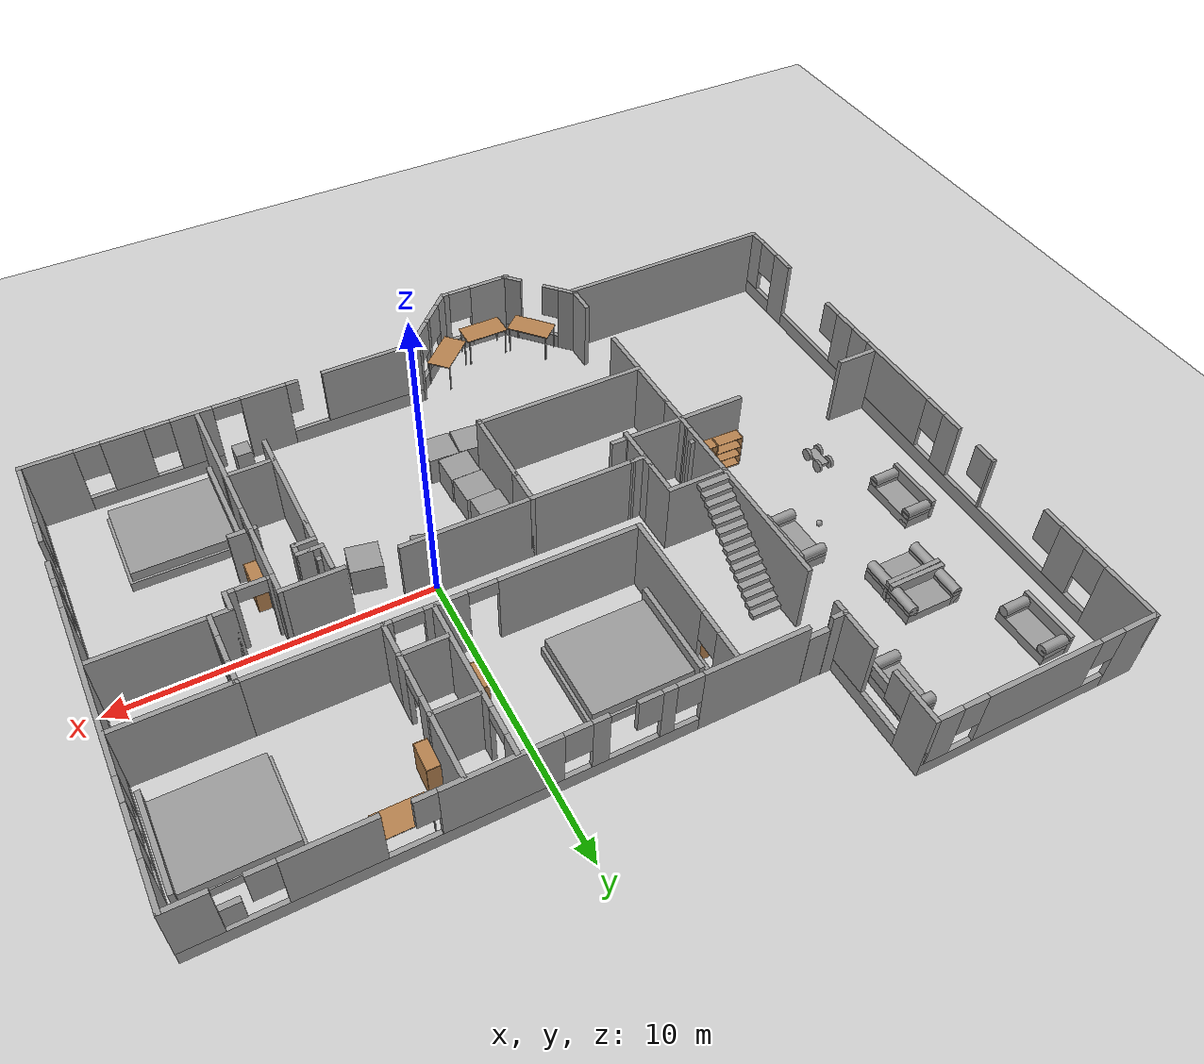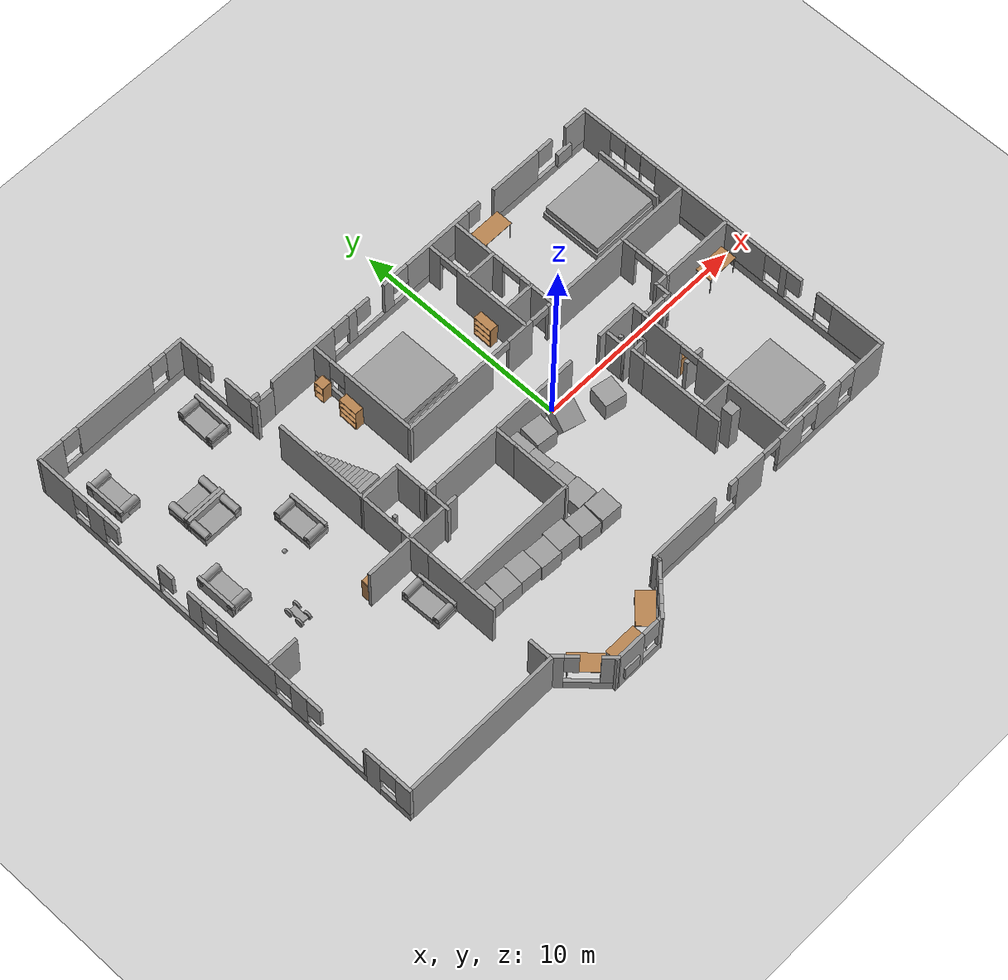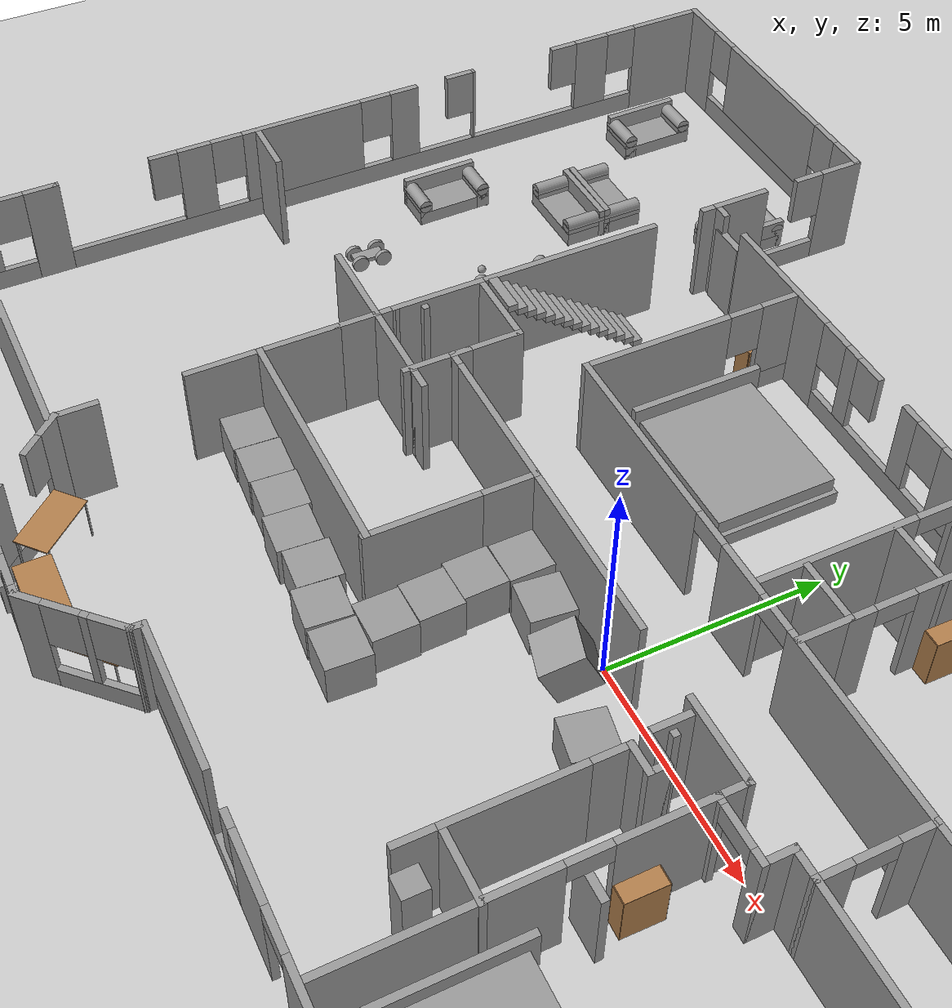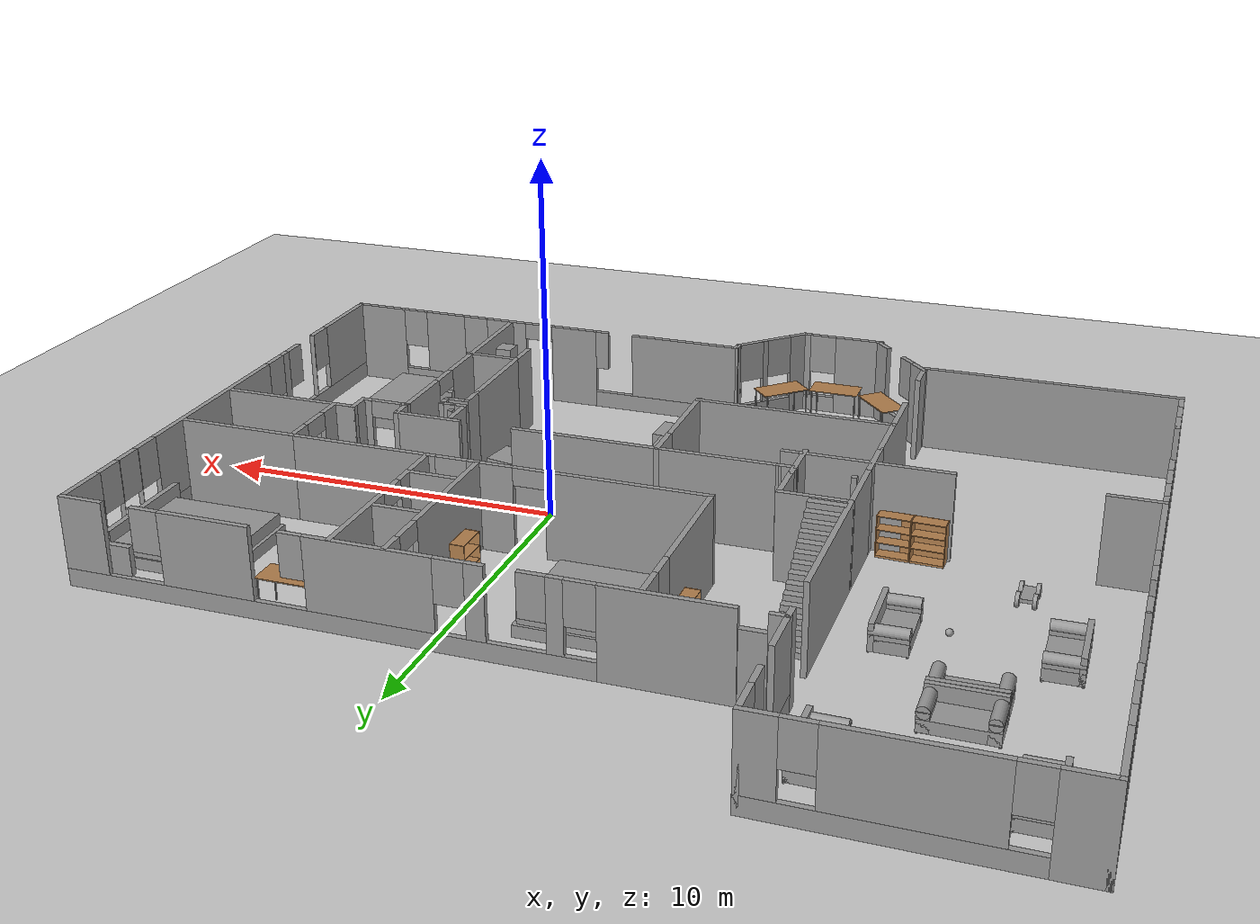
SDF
<sdf version="1.6">
 <world name="default">
  <plugin name="hello" filename="libhello.so"/>
  <light name="sun" type="directional">
   <pose>0 0 10 0 -0 0</pose>
   <diffuse>0.8 0.8 0.8 1</diffuse>
   <specular>0.2 0.2 0.2 1</specular>
   <attenuation>
    <range>1000</range>
    <constant>0.9</constant>
    <linear>0.01</linear>
    <quadratic>0.001</quadratic>
   </attenuation>
   <direction>-0.5 0.1 -0.9</direction>
  </light>
  <model name="ground_plane">
   <static>1</static>
   <link name="link">
    <collision name="collision">
     <geometry><plane><normal>0 0 1</normal><size>100 100</size></plane></geometry>
     <surface>
      <contact><collide_bitmask>65535</collide_bitmask></contact>
      <friction><ode><mu>100</mu><mu2>50</mu2></ode></friction>
     </surface>
    </collision>
    <visual name="visual">
     <cast_shadows>0</cast_shadows>
     <geometry><plane><normal>0 0 1</normal><size>100 100</size></plane></geometry>
     <material>
      <script><uri>file://media/materials/scripts/gazebo.material</uri><name>Gazebo/Grey</name></script>
     </material>
    </visual>
   </link>
  </model>
  <gravity>0 0 -9.8</gravity>
  <magnetic_field>6e-06 2.3e-05 -4.2e-05</magnetic_field>
  <atmosphere type="adiabatic"/>
  <physics name="default_physics" default="0" type="ode">
   <max_step_size>0.001</max_step_size>
   <real_time_factor>1</real_time_factor>
   <real_time_update_rate>1000</real_time_update_rate>
  </physics>
  <scene><ambient>0.4 0.4 0.4 1</ambient><background>0.7 0.7 0.7 1</background><shadows>1</shadows></scene>
  <spherical_coordinates>
   <surface_model>EARTH_WGS84</surface_model>
   <latitude_deg>0</latitude_deg>
   <longitude_deg>0</longitude_deg>
   <elevation>0</elevation>
   <heading_deg>0</heading_deg>
  </spherical_coordinates>
  <model name="spruce1st">
   <pose>-3.08285 0.81707 0 0 -0 0</pose>
   <link name="Door_0">
    <collision name="Door_0_Collision">
     <geometry><box><size>0.9 0.17 2</size></box></geometry>
     <pose>0 0 1 0 -0 0</pose>
    </collision>
    <visual name="Door_0_Visual">
     <pose>0 0 1 0 -0 0</pose>
     <geometry><box><size>0.9 0.17 2</size></box></geometry>
     <material>
      <script><uri>file://media/materials/scripts/gazebo.material</uri><name>Gazebo/Grey</name></script>
     </material>
    </visual>
    <pose>-4.99432 6.83024 0 0 -0 0</pose>
   </link>
   <link name="Door_8">
    <collision name="Door_8_Collision">
     <geometry><box><size>0.9 0.17 2</size></box></geometry>
     <pose>0 0 1 0 -0 0</pose>
    </collision>
    <visual name="Door_8_Visual">
     <pose>0 0 1 0 -0 0</pose>
     <geometry><box><size>0.9 0.17 2</size></box></geometry>
     <material>
      <script><uri>file://media/materials/scripts/gazebo.material</uri><name>Gazebo/Grey</name></script>
     </material>
    </visual>
    <pose>7.80127 -3.77874 0 0 -0 0</pose>
   </link>
   <link name="Stairs_0">
    <visual name="Stairs_0_Visual_0">
     <pose>-5.10481 4.33782 0.083333 0 -0 0</pose>
     <geometry><box><size>1 0.233333 0.166667</size></box></geometry>
     <material>
      <script><uri>file://media/materials/scripts/gazebo.material</uri><name>Gazebo/Grey</name></script>
      <ambient>1 1 1 1</ambient>
     </material>
     <meta><layer>0</layer></meta>
    </visual>
    <collision name="Stairs_0_Collision_0">
     <geometry><box><size>1 0.233333 0.166667</size></box></geometry>
     <pose>-5.10481 4.33782 0.083333 0 -0 0</pose>
    </collision>
    <visual name="Stairs_0_Visual_1">
     <pose>-5.10481 4.10449 0.25 0 -0 0</pose>
     <geometry><box><size>1 0.233333 0.166667</size></box></geometry>
     <material>
      <script><uri>file://media/materials/scripts/gazebo.material</uri><name>Gazebo/Grey</name></script>
      <ambient>1 1 1 1</ambient>
     </material>
     <meta><layer>0</layer></meta>
    </visual>
    <collision name="Stairs_0_Collision_1">
     <geometry><box><size>1 0.233333 0.166667</size></box></geometry>
     <pose>-5.10481 4.10449 0.25 0 -0 0</pose>
    </collision>
    <visual name="Stairs_0_Visual_2">
     <pose>-5.10481 3.87116 0.416667 0 -0 0</pose>
     <geometry><box><size>1 0.233333 0.166667</size></box></geometry>
     <material>
      <script><uri>file://media/materials/scripts/gazebo.material</uri><name>Gazebo/Grey</name></script>
      <ambient>1 1 1 1</ambient>
     </material>
     <meta><layer>0</layer></meta>
    </visual>
    <collision name="Stairs_0_Collision_2">
     <geometry><box><size>1 0.233333 0.166667</size></box></geometry>
     <pose>-5.10481 3.87116 0.416667 0 -0 0</pose>
    </collision>
    <visual name="Stairs_0_Visual_3">
     <pose>-5.10481 3.63782 0.583333 0 -0 0</pose>
     <geometry><box><size>1 0.233333 0.166667</size></box></geometry>
     <material>
      <script><uri>file://media/materials/scripts/gazebo.material</uri><name>Gazebo/Grey</name></script>
      <ambient>1 1 1 1</ambient>
     </material>
     <meta><layer>0</layer></meta>
    </visual>
    <collision name="Stairs_0_Collision_3">
     <geometry><box><size>1 0.233333 0.166667</size></box></geometry>
     <pose>-5.10481 3.63782 0.583333 0 -0 0</pose>
    </collision>
    <visual name="Stairs_0_Visual_4">
     <pose>-5.10481 3.40449 0.75 0 -0 0</pose>
     <geometry><box><size>1 0.233333 0.166667</size></box></geometry>
     <material>
      <script><uri>file://media/materials/scripts/gazebo.material</uri><name>Gazebo/Grey</name></script>
      <ambient>1 1 1 1</ambient>
     </material>
     <meta><layer>0</layer></meta>
    </visual>
    <collision name="Stairs_0_Collision_4">
     <geometry><box><size>1 0.233333 0.166667</size></box></geometry>
     <pose>-5.10481 3.40449 0.75 0 -0 0</pose>
    </collision>
    <visual name="Stairs_0_Visual_5">
     <pose>-5.10481 3.17116 0.916667 0 -0 0</pose>
     <geometry><box><size>1 0.233333 0.166667</size></box></geometry>
     <material>
      <script><uri>file://media/materials/scripts/gazebo.material</uri><name>Gazebo/Grey</name></script>
      <ambient>1 1 1 1</ambient>
     </material>
     <meta><layer>0</layer></meta>
    </visual>
    <collision name="Stairs_0_Collision_5">
     <geometry><box><size>1 0.233333 0.166667</size></box></geometry>
     <pose>-5.10481 3.17116 0.916667 0 -0 0</pose>
    </collision>
    <visual name="Stairs_0_Visual_6">
     <pose>-5.10481 2.93782 1.08333 0 -0 0</pose>
     <geometry><box><size>1 0.233333 0.166667</size></box></geometry>
     <material>
      <script><uri>file://media/materials/scripts/gazebo.material</uri><name>Gazebo/Grey</name></script>
      <ambient>1 1 1 1</ambient>
     </material>
     <meta><layer>0</layer></meta>
    </visual>
    <collision name="Stairs_0_Collision_6">
     <geometry><box><size>1 0.233333 0.166667</size></box></geometry>
     <pose>-5.10481 2.93782 1.08333 0 -0 0</pose>
    </collision>
    <visual name="Stairs_0_Visual_7">
     <pose>-5.10481 2.70449 1.25 0 -0 0</pose>
     <geometry><box><size>1 0.233333 0.166667</size></box></geometry>
     <material>
      <script><uri>file://media/materials/scripts/gazebo.material</uri><name>Gazebo/Grey</name></script>
      <ambient>1 1 1 1</ambient>
     </material>
     <meta><layer>0</layer></meta>
    </visual>
    <collision name="Stairs_0_Collision_7">
     <geometry><box><size>1 0.233333 0.166667</size></box></geometry>
     <pose>-5.10481 2.70449 1.25 0 -0 0</pose>
    </collision>
    <visual name="Stairs_0_Visual_8">
     <pose>-5.10481 2.47116 1.41667 0 -0 0</pose>
     <geometry><box><size>1 0.233333 0.166667</size></box></geometry>
     <material>
      <script><uri>file://media/materials/scripts/gazebo.material</uri><name>Gazebo/Grey</name></script>
      <ambient>1 1 1 1</ambient>
     </material>
     <meta><layer>0</layer></meta>
    </visual>
    <collision name="Stairs_0_Collision_8">
     <geometry><box><size>1 0.233333 0.166667</size></box></geometry>
     <pose>-5.10481 2.47116 1.41667 0 -0 0</pose>
    </collision>
    <visual name="Stairs_0_Visual_9">
     <pose>-5.10481 2.23782 1.58333 0 -0 0</pose>
     <geometry><box><size>1 0.233333 0.166667</size></box></geometry>
     <material>
      <script><uri>file://media/materials/scripts/gazebo.material</uri><name>Gazebo/Grey</name></script>
      <ambient>1 1 1 1</ambient>
     </material>
     <meta><layer>0</layer></meta>
    </visual>
    <collision name="Stairs_0_Collision_9">
     <geometry><box><size>1 0.233333 0.166667</size></box></geometry>
     <pose>-5.10481 2.23782 1.58333 0 -0 0</pose>
    </collision>
    <visual name="Stairs_0_Visual_10">
     <pose>-5.10481 2.00449 1.75 0 -0 0</pose>
     <geometry><box><size>1 0.233333 0.166667</size></box></geometry>
     <material>
      <script><uri>file://media/materials/scripts/gazebo.material</uri><name>Gazebo/Grey</name></script>
      <ambient>1 1 1 1</ambient>
     </material>
     <meta><layer>0</layer></meta>
    </visual>
    <collision name="Stairs_0_Collision_10">
     <geometry><box><size>1 0.233333 0.166667</size></box></geometry>
     <pose>-5.10481 2.00449 1.75 0 -0 0</pose>
    </collision>
    <visual name="Stairs_0_Visual_11">
     <pose>-5.10481 1.77116 1.91667 0 -0 0</pose>
     <geometry><box><size>1 0.233333 0.166667</size></box></geometry>
     <material>
      <script><uri>file://media/materials/scripts/gazebo.material</uri><name>Gazebo/Grey</name></script>
      <ambient>1 1 1 1</ambient>
     </material>
     <meta><layer>0</layer></meta>
    </visual>
    <collision name="Stairs_0_Collision_11">
     <geometry><box><size>1 0.233333 0.166667</size></box></geometry>
     <pose>-5.10481 1.77116 1.91667 0 -0 0</pose>
    </collision>
    <visual name="Stairs_0_Visual_12">
     <pose>-5.10481 1.53782 2.08333 0 -0 0</pose>
     <geometry><box><size>1 0.233333 0.166667</size></box></geometry>
     <material>
      <script><uri>file://media/materials/scripts/gazebo.material</uri><name>Gazebo/Grey</name></script>
      <ambient>1 1 1 1</ambient>
     </material>
     <meta><layer>0</layer></meta>
    </visual>
    <collision name="Stairs_0_Collision_12">
     <geometry><box><size>1 0.233333 0.166667</size></box></geometry>
     <pose>-5.10481 1.53782 2.08333 0 -0 0</pose>
    </collision>
    <visual name="Stairs_0_Visual_13">
     <pose>-5.10481 1.30449 2.25 0 -0 0</pose>
     <geometry><box><size>1 0.233333 0.166667</size></box></geometry>
     <material>
      <script><uri>file://media/materials/scripts/gazebo.material</uri><name>Gazebo/Grey</name></script>
      <ambient>1 1 1 1</ambient>
     </material>
     <meta><layer>0</layer></meta>
    </visual>
    <collision name="Stairs_0_Collision_13">
     <geometry><box><size>1 0.233333 0.166667</size></box></geometry>
     <pose>-5.10481 1.30449 2.25 0 -0 0</pose>
    </collision>
    <visual name="Stairs_0_Visual_14">
     <pose>-5.10481 1.07116 2.41667 0 -0 0</pose>
     <geometry><box><size>1 0.233333 0.166667</size></box></geometry>
     <material>
      <script><uri>file://media/materials/scripts/gazebo.material</uri><name>Gazebo/Grey</name></script>
      <ambient>1 1 1 1</ambient>
     </material>
     <meta><layer>0</layer></meta>
    </visual>
    <collision name="Stairs_0_Collision_14">
     <geometry><box><size>1 0.233333 0.166667</size></box></geometry>
     <pose>-5.10481 1.07116 2.41667 0 -0 0</pose>
    </collision>
   </link>
   <link name="Wall_101">
    <collision name="Wall_101_Collision">
     <geometry><box><size>0.75 0.15 2.5</size></box></geometry>
     <pose>0 0 1.25 0 -0 0</pose>
    </collision>
    <visual name="Wall_101_Visual">
     <pose>0 0 1.25 0 -0 0</pose>
     <geometry><box><size>0.75 0.15 2.5</size></box></geometry>
     <material>
      <script><uri>file://media/materials/scripts/gazebo.material</uri><name>Gazebo/Grey</name></script>
      <ambient>1 1 1 1</ambient>
     </material>
     <meta><layer>0</layer></meta>
    </visual>
    <pose>6.42946 -2.1381 0 0 -0 0</pose>
   </link>
   <link name="Wall_106">
    <collision name="Wall_106_Collision">
     <geometry><box><size>0.15 0.15 2.5</size></box></geometry>
     <pose>0 0 1.25 0 -0 0</pose>
    </collision>
    <visual name="Wall_106_Visual">
     <pose>0 0 1.25 0 -0 0</pose>
     <geometry><box><size>0.15 0.15 2.5</size></box></geometry>
     <material>
      <script><uri>file://media/materials/scripts/gazebo.material</uri><name>Gazebo/Grey</name></script>
      <ambient>0 0 0 0</ambient>
     </material>
     <meta><layer>0</layer></meta>
    </visual>
    <pose>6.25851 -1.36488 0 0 -0 0</pose>
   </link>
   <link name="Wall_107">
    <collision name="Wall_107_Collision">
     <geometry><box><size>0.5 0.15 2.5</size></box></geometry>
     <pose>0 0 1.25 0 -0 0</pose>
    </collision>
    <visual name="Wall_107_Visual">
     <pose>0 0 1.25 0 -0 0</pose>
     <geometry><box><size>0.5 0.15 2.5</size></box></geometry>
     <material>
      <script><uri>file://media/materials/scripts/gazebo.material</uri><name>Gazebo/Grey</name></script>
      <ambient>1 1 1 1</ambient>
     </material>
     <meta><layer>0</layer></meta>
    </visual>
    <pose>6.72946 -1.96311 0 0 -0 1.5708</pose>
   </link>
   <link name="Wall_108">
    <collision name="Wall_108_Collision">
     <geometry><box><size>0.5 0.15 2.5</size></box></geometry>
     <pose>0 0 1.25 0 -0 0</pose>
    </collision>
    <visual name="Wall_108_Visual">
     <pose>0 0 1.25 0 -0 0</pose>
     <geometry><box><size>0.5 0.15 2.5</size></box></geometry>
     <material>
      <script><uri>file://media/materials/scripts/gazebo.material</uri><name>Gazebo/Grey</name></script>
      <ambient>1 1 1 1</ambient>
     </material>
     <meta><layer>0</layer></meta>
    </visual>
    <pose>6.55446 -1.78811 0 0 -0 3.14159</pose>
   </link>
   <link name="Wall_109">
    <collision name="Wall_109_Collision">
     <geometry><box><size>0.5 0.15 2.5</size></box></geometry>
     <pose>0 0 1.25 0 -0 0</pose>
    </collision>
    <visual name="Wall_109_Visual">
     <pose>0 0 1.25 0 -0 0</pose>
     <geometry><box><size>0.5 0.15 2.5</size></box></geometry>
     <material>
      <script><uri>file://media/materials/scripts/gazebo.material</uri><name>Gazebo/Grey</name></script>
      <ambient>1 1 1 1</ambient>
     </material>
     <meta><layer>0</layer></meta>
    </visual>
    <pose>6.20446 -1.78811 0 0 -0 3.14159</pose>
   </link>
   <link name="Wall_110">
    <collision name="Wall_110_Collision">
     <geometry><box><size>1 0.15 2.5</size></box></geometry>
     <pose>0 0 1.25 0 -0 0</pose>
    </collision>
    <visual name="Wall_110_Visual">
     <pose>0 0 1.25 0 -0 0</pose>
     <geometry><box><size>1 0.15 2.5</size></box></geometry>
     <material>
      <script><uri>file://media/materials/scripts/gazebo.material</uri><name>Gazebo/Grey</name></script>
      <ambient>1 1 1 1</ambient>
     </material>
     <meta><layer>0</layer></meta>
    </visual>
    <pose>6.02946 -1.3631 0 0 -0 1.5708</pose>
   </link>
   <link name="Wall_112">
    <collision name="Wall_112_Collision">
     <geometry><box><size>3.5 0.15 2.5</size></box></geometry>
     <pose>0 0 1.25 0 -0 0</pose>
    </collision>
    <visual name="Wall_112_Visual">
     <pose>0 0 1.25 0 -0 0</pose>
     <geometry><box><size>3.5 0.15 2.5</size></box></geometry>
     <material>
      <script><uri>file://media/materials/scripts/gazebo.material</uri><name>Gazebo/Grey</name></script>
      <ambient>1 1 1 1</ambient>
     </material>
     <meta><layer>0</layer></meta>
    </visual>
    <pose>-1.7137 -0.745301 0 0 -0 3.14159</pose>
   </link>
   <link name="Wall_114">
    <collision name="Wall_114_Collision">
     <geometry><box><size>0.558425 0.15 2.5</size></box></geometry>
     <pose>0 0 1.25 0 -0 0</pose>
    </collision>
    <visual name="Wall_114_Visual">
     <pose>0 0 1.25 0 -0 0</pose>
     <geometry><box><size>0.558425 0.15 2.5</size></box></geometry>
     <material>
      <script><uri>file://media/materials/scripts/gazebo.material</uri><name>Gazebo/Grey</name></script>
      <ambient>1 1 1 1</ambient>
     </material>
     <meta><layer>0</layer></meta>
    </visual>
    <pose>-3.5929 -0.747612 0 0 -0 0.011322</pose>
   </link>
   <link name="Wall_116">
    <collision name="Wall_116_Collision">
     <geometry><box><size>1.5 0.15 2.5</size></box></geometry>
     <pose>0 0 1.25 0 -0 0</pose>
    </collision>
    <visual name="Wall_116_Visual">
     <pose>0 0 1.25 0 -0 0</pose>
     <geometry><box><size>1.5 0.15 2.5</size></box></geometry>
     <material>
      <script><uri>file://media/materials/scripts/gazebo.material</uri><name>Gazebo/Grey</name></script>
      <ambient>1 1 1 1</ambient>
     </material>
     <meta><layer>0</layer></meta>
    </visual>
    <pose>-12.3106 -1.63437 0 0 -0 0</pose>
   </link>
   <link name="Wall_118">
    <collision name="Wall_118_Collision">
     <geometry><box><size>2.25 0.15 2.5</size></box></geometry>
     <pose>0 0 1.25 0 -0 0</pose>
    </collision>
    <visual name="Wall_118_Visual">
     <pose>0 0 1.25 0 -0 0</pose>
     <geometry><box><size>2.25 0.15 2.5</size></box></geometry>
     <material>
      <script><uri>file://media/materials/scripts/gazebo.material</uri><name>Gazebo/Grey</name></script>
      <ambient>1 1 1 1</ambient>
     </material>
     <meta><layer>0</layer></meta>
    </visual>
    <pose>-6.69747 -1.68429 0 0 -0 3.14159</pose>
   </link>
   <link name="Wall_120">
    <pose>-4.75817 -9.71229 0 0 0 -0.827482</pose>
    <visual name="Wall_120_Visual_0">
     <pose>-1.03991 0 1.25 0 -0 0</pose>
     <geometry><box><size>0.672491 0.15 2.5</size></box></geometry>
     <material>
      <script><uri>file://media/materials/scripts/gazebo.material</uri><name>Gazebo/Grey</name></script>
      <ambient>1 1 1 1</ambient>
     </material>
     <meta><layer>0</layer></meta>
    </visual>
    <collision name="Wall_120_Collision_0">
     <geometry><box><size>0.672491 0.15 2.5</size></box></geometry>
     <pose>-1.03991 0 1.25 0 -0 0</pose>
    </collision>
    <visual name="Wall_120_Visual_1">
     <pose>0.336245 0 0.25 0 -0 0</pose>
     <geometry><box><size>2.07981 0.15 0.5</size></box></geometry>
     <material>
      <script><uri>file://media/materials/scripts/gazebo.material</uri><name>Gazebo/Grey</name></script>
      <ambient>1 1 1 1</ambient>
     </material>
     <meta><layer>0</layer></meta>
    </visual>
    <collision name="Wall_120_Collision_1">
     <geometry><box><size>2.07981 0.15 0.5</size></box></geometry>
     <pose>0.336245 0 0.25 0 -0 0</pose>
    </collision>
    <visual name="Wall_120_Visual_2">
     <pose>1.02545 0 1.5 0 -0 0</pose>
     <geometry><box><size>0.701408 0.15 2</size></box></geometry>
     <material>
      <script><uri>file://media/materials/scripts/gazebo.material</uri><name>Gazebo/Grey</name></script>
      <ambient>1 1 1 1</ambient>
     </material>
     <meta><layer>0</layer></meta>
    </visual>
    <collision name="Wall_120_Collision_2">
     <geometry><box><size>0.701408 0.15 2</size></box></geometry>
     <pose>1.02545 0 1.5 0 -0 0</pose>
    </collision>
    <visual name="Wall_120_Visual_3">
     <pose>-0.414459 0 1.9 0 -0 0</pose>
     <geometry><box><size>0.578405 0.15 1.2</size></box></geometry>
     <material>
      <script><uri>file://media/materials/scripts/gazebo.material</uri><name>Gazebo/Grey</name></script>
      <ambient>1 1 1 1</ambient>
     </material>
     <meta><layer>0</layer></meta>
    </visual>
    <collision name="Wall_120_Collision_3">
     <geometry><box><size>0.578405 0.15 1.2</size></box></geometry>
     <pose>-0.414459 0 1.9 0 -0 0</pose>
    </collision>
   </link>
   <link name="Wall_121">
    <pose>-2.78005 -10.6702 0 0 -0 0</pose>
    <visual name="Wall_121_Visual_0">
     <pose>-0.507131 0 1.25 0 -0 0</pose>
     <geometry><box><size>1.48574 0.15 2.5</size></box></geometry>
     <material>
      <script><uri>file://media/materials/scripts/gazebo.material</uri><name>Gazebo/Grey</name></script>
      <ambient>1 1 1 1</ambient>
     </material>
     <meta><layer>0</layer></meta>
    </visual>
    <collision name="Wall_121_Collision_0">
     <geometry><box><size>1.48574 0.15 2.5</size></box></geometry>
     <pose>-0.507131 0 1.25 0 -0 0</pose>
    </collision>
    <visual name="Wall_121_Visual_1">
     <pose>0.742869 0 0.25 0 -0 0</pose>
     <geometry><box><size>1.01426 0.15 0.5</size></box></geometry>
     <material>
      <script><uri>file://media/materials/scripts/gazebo.material</uri><name>Gazebo/Grey</name></script>
      <ambient>1 1 1 1</ambient>
     </material>
     <meta><layer>0</layer></meta>
    </visual>
    <collision name="Wall_121_Collision_1">
     <geometry><box><size>1.01426 0.15 0.5</size></box></geometry>
     <pose>0.742869 0 0.25 0 -0 0</pose>
    </collision>
    <visual name="Wall_121_Visual_2">
     <pose>1.14287 0 1.5 0 -0 0</pose>
     <geometry><box><size>0.214262 0.15 2</size></box></geometry>
     <material>
      <script><uri>file://media/materials/scripts/gazebo.material</uri><name>Gazebo/Grey</name></script>
      <ambient>1 1 1 1</ambient>
     </material>
     <meta><layer>0</layer></meta>
    </visual>
    <collision name="Wall_121_Collision_2">
     <geometry><box><size>0.214262 0.15 2</size></box></geometry>
     <pose>1.14287 0 1.5 0 -0 0</pose>
    </collision>
    <visual name="Wall_121_Visual_3">
     <pose>0.635738 0 1.9 0 -0 0</pose>
     <geometry><box><size>0.8 0.15 1.2</size></box></geometry>
     <material>
      <script><uri>file://media/materials/scripts/gazebo.material</uri><name>Gazebo/Grey</name></script>
      <ambient>1 1 1 1</ambient>
     </material>
     <meta><layer>0</layer></meta>
    </visual>
    <collision name="Wall_121_Collision_3">
     <geometry><box><size>0.8 0.15 1.2</size></box></geometry>
     <pose>0.635738 0 1.9 0 -0 0</pose>
    </collision>
   </link>
   <link name="Wall_122">
    <pose>-0.696788 -9.83939 0 0 -0 0.785398</pose>
    <visual name="Wall_122_Visual_0">
     <pose>-0.939341 0 1.25 0 -0 0</pose>
     <geometry><box><size>0.621317 0.15 2.5</size></box></geometry>
     <material>
      <script><uri>file://media/materials/scripts/gazebo.material</uri><name>Gazebo/Grey</name></script>
      <ambient>1 1 1 1</ambient>
     </material>
     <meta><layer>0</layer></meta>
    </visual>
    <collision name="Wall_122_Collision_0">
     <geometry><box><size>0.621317 0.15 2.5</size></box></geometry>
     <pose>-0.939341 0 1.25 0 -0 0</pose>
    </collision>
    <visual name="Wall_122_Visual_1">
     <pose>0.310659 0 0.25 0 -0 0</pose>
     <geometry><box><size>1.87868 0.15 0.5</size></box></geometry>
     <material>
      <script><uri>file://media/materials/scripts/gazebo.material</uri><name>Gazebo/Grey</name></script>
      <ambient>1 1 1 1</ambient>
     </material>
     <meta><layer>0</layer></meta>
    </visual>
    <collision name="Wall_122_Collision_1">
     <geometry><box><size>1.87868 0.15 0.5</size></box></geometry>
     <pose>0.310659 0 0.25 0 -0 0</pose>
    </collision>
    <visual name="Wall_122_Visual_2">
     <pose>0.257222 0 1.5 0 -0 0</pose>
     <geometry><box><size>0.17181 0.15 2</size></box></geometry>
     <material>
      <script><uri>file://media/materials/scripts/gazebo.material</uri><name>Gazebo/Grey</name></script>
      <ambient>1 1 1 1</ambient>
     </material>
     <meta><layer>0</layer></meta>
    </visual>
    <collision name="Wall_122_Collision_2">
     <geometry><box><size>0.17181 0.15 2</size></box></geometry>
     <pose>0.257222 0 1.5 0 -0 0</pose>
    </collision>
    <visual name="Wall_122_Visual_3">
     <pose>1.19656 0 1.5 0 -0 0</pose>
     <geometry><box><size>0.106873 0.15 2</size></box></geometry>
     <material>
      <script><uri>file://media/materials/scripts/gazebo.material</uri><name>Gazebo/Grey</name></script>
      <ambient>1 1 1 1</ambient>
     </material>
     <meta><layer>0</layer></meta>
    </visual>
    <collision name="Wall_122_Collision_3">
     <geometry><box><size>0.106873 0.15 2</size></box></geometry>
     <pose>1.19656 0 1.5 0 -0 0</pose>
    </collision>
    <visual name="Wall_122_Visual_4">
     <pose>-0.228683 0 1.9 0 -0 0</pose>
     <geometry><box><size>0.8 0.15 1.2</size></box></geometry>
     <material>
      <script><uri>file://media/materials/scripts/gazebo.material</uri><name>Gazebo/Grey</name></script>
      <ambient>1 1 1 1</ambient>
     </material>
     <meta><layer>0</layer></meta>
    </visual>
    <collision name="Wall_122_Collision_4">
     <geometry><box><size>0.8 0.15 1.2</size></box></geometry>
     <pose>-0.228683 0 1.9 0 -0 0</pose>
    </collision>
    <visual name="Wall_122_Visual_5">
     <pose>0.743127 0 1.9 0 -0 0</pose>
     <geometry><box><size>0.8 0.15 1.2</size></box></geometry>
     <material>
      <script><uri>file://media/materials/scripts/gazebo.material</uri><name>Gazebo/Grey</name></script>
      <ambient>1 1 1 1</ambient>
     </material>
     <meta><layer>0</layer></meta>
    </visual>
    <collision name="Wall_122_Collision_5">
     <geometry><box><size>0.8 0.15 1.2</size></box></geometry>
     <pose>0.743127 0 1.9 0 -0 0</pose>
    </collision>
   </link>
   <link name="Wall_124">
    <collision name="Wall_124_Collision">
     <geometry><box><size>7.5 0.15 2.5</size></box></geometry>
     <pose>0 0 1.25 0 -0 0</pose>
    </collision>
    <visual name="Wall_124_Visual">
     <pose>0 0 1.25 0 -0 0</pose>
     <geometry><box><size>7.5 0.15 2.5</size></box></geometry>
     <material>
      <script><uri>file://media/materials/scripts/gazebo.material</uri><name>Gazebo/Grey</name></script>
      <ambient>1 1 1 1</ambient>
     </material>
     <meta><layer>0</layer></meta>
    </visual>
    <pose>-9.3221 -8.89846 0 0 -0 0</pose>
   </link>
   <link name="Wall_126">
    <pose>6.5721 -8.75726 0 0 -0 3.14159</pose>
    <visual name="Wall_126_Visual_0">
     <pose>-5.65811 0 1.25 0 -0 0</pose>
     <geometry><box><size>1.68378 0.15 2.5</size></box></geometry>
     <material>
      <script><uri>file://media/materials/scripts/gazebo.material</uri><name>Gazebo/Grey</name></script>
      <ambient>1 1 1 1</ambient>
     </material>
     <meta><layer>0</layer></meta>
    </visual>
    <collision name="Wall_126_Collision_0">
     <geometry><box><size>1.68378 0.15 2.5</size></box></geometry>
     <pose>-5.65811 0 1.25 0 -0 0</pose>
    </collision>
    <visual name="Wall_126_Visual_1">
     <pose>1.10617 0 1.25 0 -0 0</pose>
     <geometry><box><size>1.49148 0.15 2.5</size></box></geometry>
     <material>
      <script><uri>file://media/materials/scripts/gazebo.material</uri><name>Gazebo/Grey</name></script>
      <ambient>1 1 1 1</ambient>
     </material>
     <meta><layer>0</layer></meta>
    </visual>
    <collision name="Wall_126_Collision_1">
     <geometry><box><size>1.49148 0.15 2.5</size></box></geometry>
     <pose>1.10617 0 1.25 0 -0 0</pose>
    </collision>
    <visual name="Wall_126_Visual_2">
     <pose>-2.67789 0 0.25 0 -0 0</pose>
     <geometry><box><size>4.27664 0.15 0.5</size></box></geometry>
     <material>
      <script><uri>file://media/materials/scripts/gazebo.material</uri><name>Gazebo/Grey</name></script>
      <ambient>1 1 1 1</ambient>
     </material>
     <meta><layer>0</layer></meta>
    </visual>
    <collision name="Wall_126_Collision_2">
     <geometry><box><size>4.27664 0.15 0.5</size></box></geometry>
     <pose>-2.67789 0 0.25 0 -0 0</pose>
    </collision>
    <visual name="Wall_126_Visual_3">
     <pose>4.17595 0 0.25 0 -0 0</pose>
     <geometry><box><size>4.6481 0.15 0.5</size></box></geometry>
     <material>
      <script><uri>file://media/materials/scripts/gazebo.material</uri><name>Gazebo/Grey</name></script>
      <ambient>1 1 1 1</ambient>
     </material>
     <meta><layer>0</layer></meta>
    </visual>
    <collision name="Wall_126_Collision_3">
     <geometry><box><size>4.6481 0.15 0.5</size></box></geometry>
     <pose>4.17595 0 0.25 0 -0 0</pose>
    </collision>
    <visual name="Wall_126_Visual_4">
     <pose>-3.34728 0 1.5 0 -0 0</pose>
     <geometry><box><size>1.33787 0.15 2</size></box></geometry>
     <material>
      <script><uri>file://media/materials/scripts/gazebo.material</uri><name>Gazebo/Grey</name></script>
      <ambient>1 1 1 1</ambient>
     </material>
     <meta><layer>0</layer></meta>
    </visual>
    <collision name="Wall_126_Collision_4">
     <geometry><box><size>1.33787 0.15 2</size></box></geometry>
     <pose>-3.34728 0 1.5 0 -0 0</pose>
    </collision>
    <visual name="Wall_126_Visual_5">
     <pose>-1.20896 0 1.5 0 -0 0</pose>
     <geometry><box><size>1.33877 0.15 2</size></box></geometry>
     <material>
      <script><uri>file://media/materials/scripts/gazebo.material</uri><name>Gazebo/Grey</name></script>
      <ambient>1 1 1 1</ambient>
     </material>
     <meta><layer>0</layer></meta>
    </visual>
    <collision name="Wall_126_Collision_5">
     <geometry><box><size>1.33877 0.15 2</size></box></geometry>
     <pose>-1.20896 0 1.5 0 -0 0</pose>
    </collision>
    <visual name="Wall_126_Visual_6">
     <pose>-1.20896 0 1.5 0 -0 0</pose>
     <geometry><box><size>1.33877 0.15 2</size></box></geometry>
     <material>
      <script><uri>file://media/materials/scripts/gazebo.material</uri><name>Gazebo/Grey</name></script>
      <ambient>1 1 1 1</ambient>
     </material>
     <meta><layer>0</layer></meta>
    </visual>
    <collision name="Wall_126_Collision_6">
     <geometry><box><size>1.33877 0.15 2</size></box></geometry>
     <pose>-1.20896 0 1.5 0 -0 0</pose>
    </collision>
    <visual name="Wall_126_Visual_7">
     <pose>4.77956 0 1.5 0 -0 0</pose>
     <geometry><box><size>3.44088 0.15 2</size></box></geometry>
     <material>
      <script><uri>file://media/materials/scripts/gazebo.material</uri><name>Gazebo/Grey</name></script>
      <ambient>1 1 1 1</ambient>
     </material>
     <meta><layer>0</layer></meta>
    </visual>
    <collision name="Wall_126_Collision_7">
     <geometry><box><size>3.44088 0.15 2</size></box></geometry>
     <pose>4.77956 0 1.5 0 -0 0</pose>
    </collision>
    <visual name="Wall_126_Visual_8">
     <pose>-4.41622 0 1.9 0 -0 0</pose>
     <geometry><box><size>0.8 0.15 1.2</size></box></geometry>
     <material>
      <script><uri>file://media/materials/scripts/gazebo.material</uri><name>Gazebo/Grey</name></script>
      <ambient>1 1 1 1</ambient>
     </material>
     <meta><layer>0</layer></meta>
    </visual>
    <collision name="Wall_126_Collision_8">
     <geometry><box><size>0.8 0.15 1.2</size></box></geometry>
     <pose>-4.41622 0 1.9 0 -0 0</pose>
    </collision>
    <visual name="Wall_126_Visual_9">
     <pose>2.05551 0 1.9 0 -0 0</pose>
     <geometry><box><size>0.407213 0.15 1.2</size></box></geometry>
     <material>
      <script><uri>file://media/materials/scripts/gazebo.material</uri><name>Gazebo/Grey</name></script>
      <ambient>1 1 1 1</ambient>
     </material>
     <meta><layer>0</layer></meta>
    </visual>
    <collision name="Wall_126_Collision_9">
     <geometry><box><size>0.407213 0.15 1.2</size></box></geometry>
     <pose>2.05551 0 1.9 0 -0 0</pose>
    </collision>
    <visual name="Wall_126_Visual_10">
     <pose>-2.27834 0 1.9 0 -0 0</pose>
     <geometry><box><size>0.8 0.15 1.2</size></box></geometry>
     <material>
      <script><uri>file://media/materials/scripts/gazebo.material</uri><name>Gazebo/Grey</name></script>
      <ambient>1 1 1 1</ambient>
     </material>
     <meta><layer>0</layer></meta>
    </visual>
    <collision name="Wall_126_Collision_10">
     <geometry><box><size>0.8 0.15 1.2</size></box></geometry>
     <pose>-2.27834 0 1.9 0 -0 0</pose>
    </collision>
    <visual name="Wall_126_Visual_11">
     <pose>-0.089573 0 2.25 0 -0 0</pose>
     <geometry><box><size>0.9 0.15 0.5</size></box></geometry>
     <material>
      <script><uri>file://media/materials/scripts/gazebo.material</uri><name>Gazebo/Grey</name></script>
      <ambient>1 1 1 1</ambient>
     </material>
     <meta><layer>0</layer></meta>
    </visual>
    <collision name="Wall_126_Collision_11">
     <geometry><box><size>0.9 0.15 0.5</size></box></geometry>
     <pose>-0.089573 0 2.25 0 -0 0</pose>
    </collision>
    <visual name="Wall_126_Visual_12">
     <pose>-0.089573 0 2.25 0 -0 0</pose>
     <geometry><box><size>0.9 0.15 0.5</size></box></geometry>
     <material>
      <script><uri>file://media/materials/scripts/gazebo.material</uri><name>Gazebo/Grey</name></script>
      <ambient>1 1 1 1</ambient>
     </material>
     <meta><layer>0</layer></meta>
    </visual>
    <collision name="Wall_126_Collision_12">
     <geometry><box><size>0.9 0.15 0.5</size></box></geometry>
     <pose>-0.089573 0 2.25 0 -0 0</pose>
    </collision>
   </link>
   <link name="Wall_127">
    <collision name="Wall_127_Collision">
     <geometry><box><size>0.401612 0.15 2.5</size></box></geometry>
     <pose>0 0 1.25 0 -0 0</pose>
    </collision>
    <visual name="Wall_127_Visual">
     <pose>0 0 1.25 0 -0 0</pose>
     <geometry><box><size>0.401612 0.15 2.5</size></box></geometry>
     <material>
      <script><uri>file://media/materials/scripts/gazebo.material</uri><name>Gazebo/Grey</name></script>
      <ambient>1 1 1 1</ambient>
     </material>
     <meta><layer>0</layer></meta>
    </visual>
    <pose>0.140582 -8.8829 0 0 0 -1.62264</pose>
   </link>
   <link name="Wall_129">
    <collision name="Wall_129_Collision">
     <geometry><box><size>2.13359 0.15 2.5</size></box></geometry>
     <pose>0 0 1.25 0 -0 0</pose>
    </collision>
    <visual name="Wall_129_Visual">
     <pose>0 0 1.25 0 -0 0</pose>
     <geometry><box><size>2.13359 0.15 2.5</size></box></geometry>
     <material>
      <script><uri>file://media/materials/scripts/gazebo.material</uri><name>Gazebo/Grey</name></script>
      <ambient>1 1 1 1</ambient>
     </material>
     <meta><layer>0</layer></meta>
    </visual>
    <pose>-4.65567 -1.68429 0 0 -0 0</pose>
   </link>
   <link name="Wall_13">
    <pose>-9.3221 10.7013 0 0 -0 0</pose>
    <visual name="Wall_13_Visual_0">
     <pose>-3.14849 0 1.25 0 -0 0</pose>
     <geometry><box><size>1.20303 0.15 2.5</size></box></geometry>
     <material>
      <script><uri>file://media/materials/scripts/gazebo.material</uri><name>Gazebo/Grey</name></script>
      <ambient>1 1 1 1</ambient>
     </material>
     <meta><layer>0</layer></meta>
    </visual>
    <collision name="Wall_13_Collision_0">
     <geometry><box><size>1.20303 0.15 2.5</size></box></geometry>
     <pose>-3.14849 0 1.25 0 -0 0</pose>
    </collision>
    <visual name="Wall_13_Visual_1">
     <pose>0.601514 0 0.25 0 -0 0</pose>
     <geometry><box><size>6.29697 0.15 0.5</size></box></geometry>
     <material>
      <script><uri>file://media/materials/scripts/gazebo.material</uri><name>Gazebo/Grey</name></script>
      <ambient>1 1 1 1</ambient>
     </material>
     <meta><layer>0</layer></meta>
    </visual>
    <collision name="Wall_13_Collision_1">
     <geometry><box><size>6.29697 0.15 0.5</size></box></geometry>
     <pose>0.601514 0 0.25 0 -0 0</pose>
    </collision>
    <visual name="Wall_13_Visual_2">
     <pose>0.141672 0 1.5 0 -0 0</pose>
     <geometry><box><size>3.77729 0.15 2</size></box></geometry>
     <material>
      <script><uri>file://media/materials/scripts/gazebo.material</uri><name>Gazebo/Grey</name></script>
      <ambient>1 1 1 1</ambient>
     </material>
     <meta><layer>0</layer></meta>
    </visual>
    <collision name="Wall_13_Collision_2">
     <geometry><box><size>3.77729 0.15 2</size></box></geometry>
     <pose>0.141672 0 1.5 0 -0 0</pose>
    </collision>
    <visual name="Wall_13_Visual_3">
     <pose>3.29016 0 1.5 0 -0 0</pose>
     <geometry><box><size>0.919683 0.15 2</size></box></geometry>
     <material>
      <script><uri>file://media/materials/scripts/gazebo.material</uri><name>Gazebo/Grey</name></script>
      <ambient>1 1 1 1</ambient>
     </material>
     <meta><layer>0</layer></meta>
    </visual>
    <collision name="Wall_13_Collision_3">
     <geometry><box><size>0.919683 0.15 2</size></box></geometry>
     <pose>3.29016 0 1.5 0 -0 0</pose>
    </collision>
    <visual name="Wall_13_Visual_4">
     <pose>-2.14697 0 1.9 0 -0 0</pose>
     <geometry><box><size>0.8 0.15 1.2</size></box></geometry>
     <material>
      <script><uri>file://media/materials/scripts/gazebo.material</uri><name>Gazebo/Grey</name></script>
      <ambient>1 1 1 1</ambient>
     </material>
     <meta><layer>0</layer></meta>
    </visual>
    <collision name="Wall_13_Collision_4">
     <geometry><box><size>0.8 0.15 1.2</size></box></geometry>
     <pose>-2.14697 0 1.9 0 -0 0</pose>
    </collision>
    <visual name="Wall_13_Visual_5">
     <pose>2.43032 0 1.9 0 -0 0</pose>
     <geometry><box><size>0.8 0.15 1.2</size></box></geometry>
     <material>
      <script><uri>file://media/materials/scripts/gazebo.material</uri><name>Gazebo/Grey</name></script>
      <ambient>1 1 1 1</ambient>
     </material>
     <meta><layer>0</layer></meta>
    </visual>
    <collision name="Wall_13_Collision_5">
     <geometry><box><size>0.8 0.15 1.2</size></box></geometry>
     <pose>2.43032 0 1.9 0 -0 0</pose>
    </collision>
   </link>
   <link name="Wall_130">
    <collision name="Wall_130_Collision">
     <geometry><box><size>0.5 0.15 2.5</size></box></geometry>
     <pose>0 0 1.25 0 -0 0</pose>
    </collision>
    <visual name="Wall_130_Visual">
     <pose>0 0 1.25 0 -0 0</pose>
     <geometry><box><size>0.5 0.15 2.5</size></box></geometry>
     <material>
      <script><uri>file://media/materials/scripts/gazebo.material</uri><name>Gazebo/Grey</name></script>
      <ambient>0 0 0 0</ambient>
     </material>
     <meta><layer>0</layer></meta>
    </visual>
    <pose>-3.43067 -1.68429 0 0 -0 0</pose>
   </link>
   <link name="Wall_131">
    <collision name="Wall_131_Collision">
     <geometry><box><size>1.25 0.15 2.5</size></box></geometry>
     <pose>0 0 1.25 0 -0 0</pose>
    </collision>
    <visual name="Wall_131_Visual">
     <pose>0 0 1.25 0 -0 0</pose>
     <geometry><box><size>1.25 0.15 2.5</size></box></geometry>
     <material>
      <script><uri>file://media/materials/scripts/gazebo.material</uri><name>Gazebo/Grey</name></script>
      <ambient>1 1 1 1</ambient>
     </material>
     <meta><layer>0</layer></meta>
    </visual>
    <pose>-3.7971 -1.29992 0 0 0 -1.5708</pose>
   </link>
   <link name="Wall_14">
    <pose>-5.6471 8.7763 0 0 0 -1.5708</pose>
    <visual name="Wall_14_Visual_0">
     <pose>-1.47334 0 1.25 0 -0 0</pose>
     <geometry><box><size>1.05332 0.15 2.5</size></box></geometry>
     <material>
      <script><uri>file://media/materials/scripts/gazebo.material</uri><name>Gazebo/Grey</name></script>
      <ambient>1 1 1 1</ambient>
     </material>
     <meta><layer>0</layer></meta>
    </visual>
    <collision name="Wall_14_Collision_0">
     <geometry><box><size>1.05332 0.15 2.5</size></box></geometry>
     <pose>-1.47334 0 1.25 0 -0 0</pose>
    </collision>
    <visual name="Wall_14_Visual_1">
     <pose>0.526659 0 0.25 0 -0 0</pose>
     <geometry><box><size>2.94668 0.15 0.5</size></box></geometry>
     <material>
      <script><uri>file://media/materials/scripts/gazebo.material</uri><name>Gazebo/Grey</name></script>
      <ambient>1 1 1 1</ambient>
     </material>
     <meta><layer>0</layer></meta>
    </visual>
    <collision name="Wall_14_Collision_1">
     <geometry><box><size>2.94668 0.15 0.5</size></box></geometry>
     <pose>0.526659 0 0.25 0 -0 0</pose>
    </collision>
    <visual name="Wall_14_Visual_2">
     <pose>1.28976 0 1.5 0 -0 0</pose>
     <geometry><box><size>1.42048 0.15 2</size></box></geometry>
     <material>
      <script><uri>file://media/materials/scripts/gazebo.material</uri><name>Gazebo/Grey</name></script>
      <ambient>1 1 1 1</ambient>
     </material>
     <meta><layer>0</layer></meta>
    </visual>
    <collision name="Wall_14_Collision_2">
     <geometry><box><size>1.42048 0.15 2</size></box></geometry>
     <pose>1.28976 0 1.5 0 -0 0</pose>
    </collision>
    <visual name="Wall_14_Visual_3">
     <pose>-0.58358 0 1.9 0 -0 0</pose>
     <geometry><box><size>0.726205 0.15 1.2</size></box></geometry>
     <material>
      <script><uri>file://media/materials/scripts/gazebo.material</uri><name>Gazebo/Grey</name></script>
      <ambient>1 1 1 1</ambient>
     </material>
     <meta><layer>0</layer></meta>
    </visual>
    <collision name="Wall_14_Collision_3">
     <geometry><box><size>0.726205 0.15 1.2</size></box></geometry>
     <pose>-0.58358 0 1.9 0 -0 0</pose>
    </collision>
   </link>
   <link name="Wall_15">
    <collision name="Wall_15_Collision">
     <geometry><box><size>0.5 0.15 2.5</size></box></geometry>
     <pose>0 0 1.25 0 -0 0</pose>
    </collision>
    <visual name="Wall_15_Visual">
     <pose>0 0 1.25 0 -0 0</pose>
     <geometry><box><size>0.5 0.15 2.5</size></box></geometry>
     <material>
      <script><uri>file://media/materials/scripts/gazebo.material</uri><name>Gazebo/Grey</name></script>
      <ambient>1 1 1 1</ambient>
     </material>
     <meta><layer>0</layer></meta>
    </visual>
    <pose>-5.4721 6.8513 0 0 -0 0</pose>
   </link>
   <link name="Wall_17">
    <collision name="Wall_17_Collision">
     <geometry><box><size>0.5 0.15 2.5</size></box></geometry>
     <pose>0 0 1.25 0 -0 0</pose>
    </collision>
    <visual name="Wall_17_Visual">
     <pose>0 0 1.25 0 -0 0</pose>
     <geometry><box><size>0.5 0.15 2.5</size></box></geometry>
     <material>
      <script><uri>file://media/materials/scripts/gazebo.material</uri><name>Gazebo/Grey</name></script>
      <ambient>1 1 1 1</ambient>
     </material>
     <meta><layer>0</layer></meta>
    </visual>
    <pose>-5.6471 6.6763 0 0 0 -1.5708</pose>
   </link>
   <link name="Wall_20">
    <collision name="Wall_20_Collision">
     <geometry><box><size>4.5 0.15 2.5</size></box></geometry>
     <pose>0 0 1.25 0 -0 0</pose>
    </collision>
    <visual name="Wall_20_Visual">
     <pose>0 0 1.25 0 -0 0</pose>
     <geometry><box><size>4.5 0.15 2.5</size></box></geometry>
     <material>
      <script><uri>file://media/materials/scripts/gazebo.material</uri><name>Gazebo/Grey</name></script>
      <ambient>1 1 1 1</ambient>
     </material>
     <meta><layer>0</layer></meta>
    </visual>
    <pose>-5.6471 2.9763 0 0 0 -1.5708</pose>
   </link>
   <link name="Wall_22">
    <collision name="Wall_22_Collision">
     <geometry><box><size>2 0.15 2.5</size></box></geometry>
     <pose>0 0 1.25 0 -0 0</pose>
    </collision>
    <visual name="Wall_22_Visual">
     <pose>0 0 1.25 0 -0 0</pose>
     <geometry><box><size>2 0.15 2.5</size></box></geometry>
     <material>
      <script><uri>file://media/materials/scripts/gazebo.material</uri><name>Gazebo/Grey</name></script>
      <ambient>1 1 1 1</ambient>
     </material>
     <meta><layer>0</layer></meta>
    </visual>
    <pose>-4.7221 0.801304 0 0 -0 0</pose>
   </link>
   <link name="Wall_23">
    <collision name="Wall_23_Collision">
     <geometry><box><size>1.30061 0.15 2.5</size></box></geometry>
     <pose>0 0 1.25 0 -0 0</pose>
    </collision>
    <visual name="Wall_23_Visual">
     <pose>0 0 1.25 0 -0 0</pose>
     <geometry><box><size>1.30061 0.15 2.5</size></box></geometry>
     <material>
      <script><uri>file://media/materials/scripts/gazebo.material</uri><name>Gazebo/Grey</name></script>
      <ambient>1 1 1 1</ambient>
     </material>
     <meta><layer>0</layer></meta>
    </visual>
    <pose>-3.7971 0.225996 0 0 0 -1.5708</pose>
   </link>
   <link name="Wall_24">
    <collision name="Wall_24_Collision">
     <geometry><box><size>0.5 0.15 2.5</size></box></geometry>
     <pose>0 0 1.25 0 -0 0</pose>
    </collision>
    <visual name="Wall_24_Visual">
     <pose>0 0 1.25 0 -0 0</pose>
     <geometry><box><size>0.5 0.15 2.5</size></box></geometry>
     <material>
      <script><uri>file://media/materials/scripts/gazebo.material</uri><name>Gazebo/Grey</name></script>
      <ambient>1 1 1 1</ambient>
     </material>
     <meta><layer>0</layer></meta>
    </visual>
    <pose>-3.7971 -0.574925 0 0 0 -1.5708</pose>
   </link>
   <link name="Wall_26">
    <collision name="Wall_26_Collision">
     <geometry><box><size>0.15 0.15 2.5</size></box></geometry>
     <pose>0 0 1.25 0 -0 0</pose>
    </collision>
    <visual name="Wall_26_Visual">
     <pose>0 0 1.25 0 -0 0</pose>
     <geometry><box><size>0.15 0.15 2.5</size></box></geometry>
     <material>
      <script><uri>file://media/materials/scripts/gazebo.material</uri><name>Gazebo/Grey</name></script>
      <ambient>1 1 1 1</ambient>
     </material>
     <meta><layer>0</layer></meta>
    </visual>
    <pose>-5.3971 -0.648696 0 0 -0 0</pose>
   </link>
   <link name="Wall_27">
    <collision name="Wall_27_Collision">
     <geometry><box><size>0.15 0.15 2.5</size></box></geometry>
     <pose>0 0 1.25 0 -0 0</pose>
    </collision>
    <visual name="Wall_27_Visual">
     <pose>0 0 1.25 0 -0 0</pose>
     <geometry><box><size>0.15 0.15 2.5</size></box></geometry>
     <material>
      <script><uri>file://media/materials/scripts/gazebo.material</uri><name>Gazebo/Grey</name></script>
      <ambient>1 1 1 1</ambient>
     </material>
     <meta><layer>0</layer></meta>
    </visual>
    <pose>-5.3971 -0.648696 0 0 -0 0</pose>
   </link>
   <link name="Wall_32">
    <collision name="Wall_32_Collision">
     <geometry><box><size>2.2153 0.15 2.5</size></box></geometry>
     <pose>0 0 1.25 0 -0 0</pose>
    </collision>
    <visual name="Wall_32_Visual">
     <pose>0 0 1.25 0 -0 0</pose>
     <geometry><box><size>2.2153 0.15 2.5</size></box></geometry>
     <material>
      <script><uri>file://media/materials/scripts/gazebo.material</uri><name>Gazebo/Grey</name></script>
      <ambient>1 1 1 1</ambient>
     </material>
     <meta><layer>0</layer></meta>
    </visual>
    <pose>-5.64642 -0.231348 0 0 -0 1.57145</pose>
   </link>
   <link name="Wall_34">
    <collision name="Wall_34_Collision">
     <geometry><box><size>1.5 0.15 2.5</size></box></geometry>
     <pose>0 0 1.25 0 -0 0</pose>
    </collision>
    <visual name="Wall_34_Visual">
     <pose>0 0 1.25 0 -0 0</pose>
     <geometry><box><size>1.5 0.15 2.5</size></box></geometry>
     <material>
      <script><uri>file://media/materials/scripts/gazebo.material</uri><name>Gazebo/Grey</name></script>
      <ambient>1 1 1 1</ambient>
     </material>
     <meta><layer>0</layer></meta>
    </visual>
    <pose>-5.64574 -1.939 0 0 0 -1.5708</pose>
   </link>
   <link name="Wall_37">
    <pose>-12.9971 2.0263 0 0 0 -1.5708</pose>
    <visual name="Wall_37_Visual_0">
     <pose>-7.78322 0 1.25 0 -0 0</pose>
     <geometry><box><size>1.93356 0.15 2.5</size></box></geometry>
     <material>
      <script><uri>file://media/materials/scripts/gazebo.material</uri><name>Gazebo/Grey</name></script>
      <ambient>1 1 1 1</ambient>
     </material>
     <meta><layer>0</layer></meta>
    </visual>
    <collision name="Wall_37_Collision_0">
     <geometry><box><size>1.93356 0.15 2.5</size></box></geometry>
     <pose>-7.78322 0 1.25 0 -0 0</pose>
    </collision>
    <visual name="Wall_37_Visual_1">
     <pose>0.966783 0 0.25 0 -0 0</pose>
     <geometry><box><size>15.5664 0.15 0.5</size></box></geometry>
     <material>
      <script><uri>file://media/materials/scripts/gazebo.material</uri><name>Gazebo/Grey</name></script>
      <ambient>1 1 1 1</ambient>
     </material>
     <meta><layer>0</layer></meta>
    </visual>
    <collision name="Wall_37_Collision_1">
     <geometry><box><size>15.5664 0.15 0.5</size></box></geometry>
     <pose>0.966783 0 0.25 0 -0 0</pose>
    </collision>
    <visual name="Wall_37_Visual_2">
     <pose>-5.55552 0 1.5 0 -0 0</pose>
     <geometry><box><size>0.921827 0.15 2</size></box></geometry>
     <material>
      <script><uri>file://media/materials/scripts/gazebo.material</uri><name>Gazebo/Grey</name></script>
      <ambient>1 1 1 1</ambient>
     </material>
     <meta><layer>0</layer></meta>
    </visual>
    <collision name="Wall_37_Collision_2">
     <geometry><box><size>0.921827 0.15 2</size></box></geometry>
     <pose>-5.55552 0 1.5 0 -0 0</pose>
    </collision>
    <visual name="Wall_37_Visual_3">
     <pose>-2.14673 0 1.5 0 -0 0</pose>
     <geometry><box><size>0.068166 0.15 2</size></box></geometry>
     <material>
      <script><uri>file://media/materials/scripts/gazebo.material</uri><name>Gazebo/Grey</name></script>
      <ambient>1 1 1 1</ambient>
     </material>
     <meta><layer>0</layer></meta>
    </visual>
    <collision name="Wall_37_Collision_3">
     <geometry><box><size>0.068166 0.15 2</size></box></geometry>
     <pose>-2.14673 0 1.5 0 -0 0</pose>
    </collision>
    <visual name="Wall_37_Visual_4">
     <pose>-0.221666 0 1.5 0 -0 0</pose>
     <geometry><box><size>0.7476 0.15 2</size></box></geometry>
     <material>
      <script><uri>file://media/materials/scripts/gazebo.material</uri><name>Gazebo/Grey</name></script>
      <ambient>1 1 1 1</ambient>
     </material>
     <meta><layer>0</layer></meta>
    </visual>
    <collision name="Wall_37_Collision_4">
     <geometry><box><size>0.7476 0.15 2</size></box></geometry>
     <pose>-0.221666 0 1.5 0 -0 0</pose>
    </collision>
    <visual name="Wall_37_Visual_5">
     <pose>2.50576 0 1.5 0 -0 0</pose>
     <geometry><box><size>3.10725 0.15 2</size></box></geometry>
     <material>
      <script><uri>file://media/materials/scripts/gazebo.material</uri><name>Gazebo/Grey</name></script>
      <ambient>1 1 1 1</ambient>
     </material>
     <meta><layer>0</layer></meta>
    </visual>
    <collision name="Wall_37_Collision_5">
     <geometry><box><size>3.10725 0.15 2</size></box></geometry>
     <pose>2.50576 0 1.5 0 -0 0</pose>
    </collision>
    <visual name="Wall_37_Visual_6">
     <pose>5.28306 0 1.5 0 -0 0</pose>
     <geometry><box><size>0.847345 0.15 2</size></box></geometry>
     <material>
      <script><uri>file://media/materials/scripts/gazebo.material</uri><name>Gazebo/Grey</name></script>
      <ambient>1 1 1 1</ambient>
     </material>
     <meta><layer>0</layer></meta>
    </visual>
    <collision name="Wall_37_Collision_6">
     <geometry><box><size>0.847345 0.15 2</size></box></geometry>
     <pose>5.28306 0 1.5 0 -0 0</pose>
    </collision>
    <visual name="Wall_37_Visual_7">
     <pose>8.70164 0 1.5 0 -0 0</pose>
     <geometry><box><size>0.096727 0.15 2</size></box></geometry>
     <material>
      <script><uri>file://media/materials/scripts/gazebo.material</uri><name>Gazebo/Grey</name></script>
      <ambient>1 1 1 1</ambient>
     </material>
     <meta><layer>0</layer></meta>
    </visual>
    <collision name="Wall_37_Collision_7">
     <geometry><box><size>0.096727 0.15 2</size></box></geometry>
     <pose>8.70164 0 1.5 0 -0 0</pose>
    </collision>
    <visual name="Wall_37_Visual_8">
     <pose>-6.41643 0 1.9 0 -0 0</pose>
     <geometry><box><size>0.8 0.15 1.2</size></box></geometry>
     <material>
      <script><uri>file://media/materials/scripts/gazebo.material</uri><name>Gazebo/Grey</name></script>
      <ambient>1 1 1 1</ambient>
     </material>
     <meta><layer>0</layer></meta>
    </visual>
    <collision name="Wall_37_Collision_8">
     <geometry><box><size>0.8 0.15 1.2</size></box></geometry>
     <pose>-6.41643 0 1.9 0 -0 0</pose>
    </collision>
    <visual name="Wall_37_Visual_9">
     <pose>-4.73602 0 1.9 0 -0 0</pose>
     <geometry><box><size>0.71718 0.15 1.2</size></box></geometry>
     <material>
      <script><uri>file://media/materials/scripts/gazebo.material</uri><name>Gazebo/Grey</name></script>
      <ambient>1 1 1 1</ambient>
     </material>
     <meta><layer>0</layer></meta>
    </visual>
    <collision name="Wall_37_Collision_9">
     <geometry><box><size>0.71718 0.15 1.2</size></box></geometry>
     <pose>-4.73602 0 1.9 0 -0 0</pose>
    </collision>
    <visual name="Wall_37_Visual_10">
     <pose>-1.75406 0 1.9 0 -0 0</pose>
     <geometry><box><size>0.717181 0.15 1.2</size></box></geometry>
     <material>
      <script><uri>file://media/materials/scripts/gazebo.material</uri><name>Gazebo/Grey</name></script>
      <ambient>1 1 1 1</ambient>
     </material>
     <meta><layer>0</layer></meta>
    </visual>
    <collision name="Wall_37_Collision_10">
     <geometry><box><size>0.717181 0.15 1.2</size></box></geometry>
     <pose>-1.75406 0 1.9 0 -0 0</pose>
    </collision>
    <visual name="Wall_37_Visual_11">
     <pose>0.552134 0 1.9 0 -0 0</pose>
     <geometry><box><size>0.8 0.15 1.2</size></box></geometry>
     <material>
      <script><uri>file://media/materials/scripts/gazebo.material</uri><name>Gazebo/Grey</name></script>
      <ambient>1 1 1 1</ambient>
     </material>
     <meta><layer>0</layer></meta>
    </visual>
    <collision name="Wall_37_Collision_11">
     <geometry><box><size>0.8 0.15 1.2</size></box></geometry>
     <pose>0.552134 0 1.9 0 -0 0</pose>
    </collision>
    <visual name="Wall_37_Visual_12">
     <pose>4.45939 0 1.9 0 -0 0</pose>
     <geometry><box><size>0.8 0.15 1.2</size></box></geometry>
     <material>
      <script><uri>file://media/materials/scripts/gazebo.material</uri><name>Gazebo/Grey</name></script>
      <ambient>1 1 1 1</ambient>
     </material>
     <meta><layer>0</layer></meta>
    </visual>
    <collision name="Wall_37_Collision_12">
     <geometry><box><size>0.8 0.15 1.2</size></box></geometry>
     <pose>4.45939 0 1.9 0 -0 0</pose>
    </collision>
    <visual name="Wall_37_Visual_13">
     <pose>6.05617 0 1.9 0 -0 0</pose>
     <geometry><box><size>0.698874 0.15 1.2</size></box></geometry>
     <material>
      <script><uri>file://media/materials/scripts/gazebo.material</uri><name>Gazebo/Grey</name></script>
      <ambient>1 1 1 1</ambient>
     </material>
     <meta><layer>0</layer></meta>
    </visual>
    <collision name="Wall_37_Collision_13">
     <geometry><box><size>0.698874 0.15 1.2</size></box></geometry>
     <pose>6.05617 0 1.9 0 -0 0</pose>
    </collision>
   </link>
   <link name="Wall_38">
    <pose>-12.9971 -7.77358 0 0 0 -1.5708</pose>
    <visual name="Wall_38_Visual_0">
     <pose>-0.774668 0 1.25 0 -0 0</pose>
     <geometry><box><size>0.850976 0.15 2.5</size></box></geometry>
     <material>
      <script><uri>file://media/materials/scripts/gazebo.material</uri><name>Gazebo/Grey</name></script>
      <ambient>1 1 1 1</ambient>
     </material>
     <meta><layer>0</layer></meta>
    </visual>
    <collision name="Wall_38_Collision_0">
     <geometry><box><size>0.850976 0.15 2.5</size></box></geometry>
     <pose>-0.774668 0 1.25 0 -0 0</pose>
    </collision>
    <visual name="Wall_38_Visual_1">
     <pose>0.425488 0 0.25 0 -0 0</pose>
     <geometry><box><size>1.54934 0.15 0.5</size></box></geometry>
     <material>
      <script><uri>file://media/materials/scripts/gazebo.material</uri><name>Gazebo/Grey</name></script>
      <ambient>1 1 1 1</ambient>
     </material>
     <meta><layer>0</layer></meta>
    </visual>
    <collision name="Wall_38_Collision_1">
     <geometry><box><size>1.54934 0.15 0.5</size></box></geometry>
     <pose>0.425488 0 0.25 0 -0 0</pose>
    </collision>
    <visual name="Wall_38_Visual_2">
     <pose>0.825488 0 1.5 0 -0 0</pose>
     <geometry><box><size>0.749337 0.15 2</size></box></geometry>
     <material>
      <script><uri>file://media/materials/scripts/gazebo.material</uri><name>Gazebo/Grey</name></script>
      <ambient>1 1 1 1</ambient>
     </material>
     <meta><layer>0</layer></meta>
    </visual>
    <collision name="Wall_38_Collision_2">
     <geometry><box><size>0.749337 0.15 2</size></box></geometry>
     <pose>0.825488 0 1.5 0 -0 0</pose>
    </collision>
    <visual name="Wall_38_Visual_3">
     <pose>0.050819 0 1.9 0 -0 0</pose>
     <geometry><box><size>0.8 0.15 1.2</size></box></geometry>
     <material>
      <script><uri>file://media/materials/scripts/gazebo.material</uri><name>Gazebo/Grey</name></script>
      <ambient>1 1 1 1</ambient>
     </material>
     <meta><layer>0</layer></meta>
    </visual>
    <collision name="Wall_38_Collision_3">
     <geometry><box><size>0.8 0.15 1.2</size></box></geometry>
     <pose>0.050819 0 1.9 0 -0 0</pose>
    </collision>
   </link>
   <link name="Wall_4">
    <pose>4.27021 6.84274 0 0 -0 0</pose>
    <visual name="Wall_4_Visual_0">
     <pose>-7.14725 0 1.25 0 -0 0</pose>
     <geometry><box><size>3.30928 0.15 2.5</size></box></geometry>
     <material>
      <script><uri>file://media/materials/scripts/gazebo.material</uri><name>Gazebo/Grey</name></script>
      <ambient>1 1 1 1</ambient>
     </material>
     <meta><layer>0</layer></meta>
    </visual>
    <collision name="Wall_4_Collision_0">
     <geometry><box><size>3.30928 0.15 2.5</size></box></geometry>
     <pose>-7.14725 0 1.25 0 -0 0</pose>
    </collision>
    <visual name="Wall_4_Visual_1">
     <pose>1.65464 0 0.25 0 -0 0</pose>
     <geometry><box><size>14.2945 0.15 0.5</size></box></geometry>
     <material>
      <script><uri>file://media/materials/scripts/gazebo.material</uri><name>Gazebo/Grey</name></script>
      <ambient>1 1 1 1</ambient>
     </material>
     <meta><layer>0</layer></meta>
    </visual>
    <collision name="Wall_4_Collision_1">
     <geometry><box><size>14.2945 0.15 0.5</size></box></geometry>
     <pose>1.65464 0 0.25 0 -0 0</pose>
    </collision>
    <visual name="Wall_4_Visual_2">
     <pose>-4.48027 0 1.5 0 -0 0</pose>
     <geometry><box><size>0.424693 0.15 2</size></box></geometry>
     <material>
      <script><uri>file://media/materials/scripts/gazebo.material</uri><name>Gazebo/Grey</name></script>
      <ambient>1 1 1 1</ambient>
     </material>
     <meta><layer>0</layer></meta>
    </visual>
    <collision name="Wall_4_Collision_2">
     <geometry><box><size>0.424693 0.15 2</size></box></geometry>
     <pose>-4.48027 0 1.5 0 -0 0</pose>
    </collision>
    <visual name="Wall_4_Visual_3">
     <pose>-2.49014 0 1.5 0 -0 0</pose>
     <geometry><box><size>0.501236 0.15 2</size></box></geometry>
     <material>
      <script><uri>file://media/materials/scripts/gazebo.material</uri><name>Gazebo/Grey</name></script>
      <ambient>1 1 1 1</ambient>
     </material>
     <meta><layer>0</layer></meta>
    </visual>
    <collision name="Wall_4_Collision_3">
     <geometry><box><size>0.501236 0.15 2</size></box></geometry>
     <pose>-2.49014 0 1.5 0 -0 0</pose>
    </collision>
    <visual name="Wall_4_Visual_4">
     <pose>0.265416 0 1.5 0 -0 0</pose>
     <geometry><box><size>3.40988 0.15 2</size></box></geometry>
     <material>
      <script><uri>file://media/materials/scripts/gazebo.material</uri><name>Gazebo/Grey</name></script>
      <ambient>1 1 1 1</ambient>
     </material>
     <meta><layer>0</layer></meta>
    </visual>
    <collision name="Wall_4_Collision_4">
     <geometry><box><size>3.40988 0.15 2</size></box></geometry>
     <pose>0.265416 0 1.5 0 -0 0</pose>
    </collision>
    <visual name="Wall_4_Visual_5">
     <pose>4.69139 0 1.5 0 -0 0</pose>
     <geometry><box><size>2.54082 0.15 2</size></box></geometry>
     <material>
      <script><uri>file://media/materials/scripts/gazebo.material</uri><name>Gazebo/Grey</name></script>
      <ambient>1 1 1 1</ambient>
     </material>
     <meta><layer>0</layer></meta>
    </visual>
    <collision name="Wall_4_Collision_5">
     <geometry><box><size>2.54082 0.15 2</size></box></geometry>
     <pose>4.69139 0 1.5 0 -0 0</pose>
    </collision>
    <visual name="Wall_4_Visual_6">
     <pose>8.1781 0 1.5 0 -0 0</pose>
     <geometry><box><size>1.24758 0.15 2</size></box></geometry>
     <material>
      <script><uri>file://media/materials/scripts/gazebo.material</uri><name>Gazebo/Grey</name></script>
      <ambient>1 1 1 1</ambient>
     </material>
     <meta><layer>0</layer></meta>
    </visual>
    <collision name="Wall_4_Collision_6">
     <geometry><box><size>1.24758 0.15 2</size></box></geometry>
     <pose>8.1781 0 1.5 0 -0 0</pose>
    </collision>
    <visual name="Wall_4_Visual_7">
     <pose>-5.09261 0 1.9 0 -0 0</pose>
     <geometry><box><size>0.8 0.15 1.2</size></box></geometry>
     <material>
      <script><uri>file://media/materials/scripts/gazebo.material</uri><name>Gazebo/Grey</name></script>
      <ambient>1 1 1 1</ambient>
     </material>
     <meta><layer>0</layer></meta>
    </visual>
    <collision name="Wall_4_Collision_7">
     <geometry><box><size>0.8 0.15 1.2</size></box></geometry>
     <pose>-5.09261 0 1.9 0 -0 0</pose>
    </collision>
    <visual name="Wall_4_Visual_8">
     <pose>-3.90434 0 1.9 0 -0 0</pose>
     <geometry><box><size>0.727161 0.15 1.2</size></box></geometry>
     <material>
      <script><uri>file://media/materials/scripts/gazebo.material</uri><name>Gazebo/Grey</name></script>
      <ambient>1 1 1 1</ambient>
     </material>
     <meta><layer>0</layer></meta>
    </visual>
    <collision name="Wall_4_Collision_8">
     <geometry><box><size>0.727161 0.15 1.2</size></box></geometry>
     <pose>-3.90434 0 1.9 0 -0 0</pose>
    </collision>
    <visual name="Wall_4_Visual_9">
     <pose>-1.83952 0 1.9 0 -0 0</pose>
     <geometry><box><size>0.8 0.15 1.2</size></box></geometry>
     <material>
      <script><uri>file://media/materials/scripts/gazebo.material</uri><name>Gazebo/Grey</name></script>
      <ambient>1 1 1 1</ambient>
     </material>
     <meta><layer>0</layer></meta>
    </visual>
    <collision name="Wall_4_Collision_9">
     <geometry><box><size>0.8 0.15 1.2</size></box></geometry>
     <pose>-1.83952 0 1.9 0 -0 0</pose>
    </collision>
    <visual name="Wall_4_Visual_10">
     <pose>2.29567 0 1.9 0 -0 0</pose>
     <geometry><box><size>0.650619 0.15 1.2</size></box></geometry>
     <material>
      <script><uri>file://media/materials/scripts/gazebo.material</uri><name>Gazebo/Grey</name></script>
      <ambient>1 1 1 1</ambient>
     </material>
     <meta><layer>0</layer></meta>
    </visual>
    <collision name="Wall_4_Collision_10">
     <geometry><box><size>0.650619 0.15 1.2</size></box></geometry>
     <pose>2.29567 0 1.9 0 -0 0</pose>
    </collision>
    <visual name="Wall_4_Visual_11">
     <pose>6.35806 0 1.9 0 -0 0</pose>
     <geometry><box><size>0.792515 0.15 1.2</size></box></geometry>
     <material>
      <script><uri>file://media/materials/scripts/gazebo.material</uri><name>Gazebo/Grey</name></script>
      <ambient>1 1 1 1</ambient>
     </material>
     <meta><layer>0</layer></meta>
    </visual>
    <collision name="Wall_4_Collision_11">
     <geometry><box><size>0.792515 0.15 1.2</size></box></geometry>
     <pose>6.35806 0 1.9 0 -0 0</pose>
    </collision>
   </link>
   <link name="Wall_41">
    <pose>12.9971 -0.957263 0 0 0 -1.5708</pose>
    <visual name="Wall_41_Visual_0">
     <pose>-7.10477 0 1.25 0 -0 0</pose>
     <geometry><box><size>1.54045 0.15 2.5</size></box></geometry>
     <material>
      <script><uri>file://media/materials/scripts/gazebo.material</uri><name>Gazebo/Grey</name></script>
      <ambient>1 1 1 1</ambient>
     </material>
     <meta><layer>0</layer></meta>
    </visual>
    <collision name="Wall_41_Collision_0">
     <geometry><box><size>1.54045 0.15 2.5</size></box></geometry>
     <pose>-7.10477 0 1.25 0 -0 0</pose>
    </collision>
    <visual name="Wall_41_Visual_1">
     <pose>0.770227 0 0.25 0 -0 0</pose>
     <geometry><box><size>14.2095 0.15 0.5</size></box></geometry>
     <material>
      <script><uri>file://media/materials/scripts/gazebo.material</uri><name>Gazebo/Grey</name></script>
      <ambient>1 1 1 1</ambient>
     </material>
     <meta><layer>0</layer></meta>
    </visual>
    <collision name="Wall_41_Collision_1">
     <geometry><box><size>14.2095 0.15 0.5</size></box></geometry>
     <pose>0.770227 0 0.25 0 -0 0</pose>
    </collision>
    <visual name="Wall_41_Visual_2">
     <pose>-5.52733 0 1.5 0 -0 0</pose>
     <geometry><box><size>0.014427 0.15 2</size></box></geometry>
     <material>
      <script><uri>file://media/materials/scripts/gazebo.material</uri><name>Gazebo/Grey</name></script>
      <ambient>1 1 1 1</ambient>
     </material>
     <meta><layer>0</layer></meta>
    </visual>
    <collision name="Wall_41_Collision_2">
     <geometry><box><size>0.014427 0.15 2</size></box></geometry>
     <pose>-5.52733 0 1.5 0 -0 0</pose>
    </collision>
    <visual name="Wall_41_Visual_3">
     <pose>-4.71291 0 1.5 0 -0 0</pose>
     <geometry><box><size>0.014427 0.15 2</size></box></geometry>
     <material>
      <script><uri>file://media/materials/scripts/gazebo.material</uri><name>Gazebo/Grey</name></script>
      <ambient>1 1 1 1</ambient>
     </material>
     <meta><layer>0</layer></meta>
    </visual>
    <collision name="Wall_41_Collision_3">
     <geometry><box><size>0.014427 0.15 2</size></box></geometry>
     <pose>-4.71291 0 1.5 0 -0 0</pose>
    </collision>
    <visual name="Wall_41_Visual_4">
     <pose>-0.997084 0 1.5 0 -0 0</pose>
     <geometry><box><size>5.81722 0.15 2</size></box></geometry>
     <material>
      <script><uri>file://media/materials/scripts/gazebo.material</uri><name>Gazebo/Grey</name></script>
      <ambient>1 1 1 1</ambient>
     </material>
     <meta><layer>0</layer></meta>
    </visual>
    <collision name="Wall_41_Collision_4">
     <geometry><box><size>5.81722 0.15 2</size></box></geometry>
     <pose>-0.997084 0 1.5 0 -0 0</pose>
    </collision>
    <visual name="Wall_41_Visual_5">
     <pose>2.87144 0 1.5 0 -0 0</pose>
     <geometry><box><size>0.319837 0.15 2</size></box></geometry>
     <material>
      <script><uri>file://media/materials/scripts/gazebo.material</uri><name>Gazebo/Grey</name></script>
      <ambient>1 1 1 1</ambient>
     </material>
     <meta><layer>0</layer></meta>
    </visual>
    <collision name="Wall_41_Collision_5">
     <geometry><box><size>0.319837 0.15 2</size></box></geometry>
     <pose>2.87144 0 1.5 0 -0 0</pose>
    </collision>
    <visual name="Wall_41_Visual_6">
     <pose>4.5512 0 1.5 0 -0 0</pose>
     <geometry><box><size>0.014426 0.15 2</size></box></geometry>
     <material>
      <script><uri>file://media/materials/scripts/gazebo.material</uri><name>Gazebo/Grey</name></script>
      <ambient>1 1 1 1</ambient>
     </material>
     <meta><layer>0</layer></meta>
    </visual>
    <collision name="Wall_41_Collision_6">
     <geometry><box><size>0.014426 0.15 2</size></box></geometry>
     <pose>4.5512 0 1.5 0 -0 0</pose>
    </collision>
    <visual name="Wall_41_Visual_7">
     <pose>6.61671 0 1.5 0 -0 0</pose>
     <geometry><box><size>2.51659 0.15 2</size></box></geometry>
     <material>
      <script><uri>file://media/materials/scripts/gazebo.material</uri><name>Gazebo/Grey</name></script>
      <ambient>1 1 1 1</ambient>
     </material>
     <meta><layer>0</layer></meta>
    </visual>
    <collision name="Wall_41_Collision_7">
     <geometry><box><size>2.51659 0.15 2</size></box></geometry>
     <pose>6.61671 0 1.5 0 -0 0</pose>
    </collision>
    <visual name="Wall_41_Visual_8">
     <pose>-5.93455 0 1.9 0 -0 0</pose>
     <geometry><box><size>0.8 0.15 1.2</size></box></geometry>
     <material>
      <script><uri>file://media/materials/scripts/gazebo.material</uri><name>Gazebo/Grey</name></script>
      <ambient>1 1 1 1</ambient>
     </material>
     <meta><layer>0</layer></meta>
    </visual>
    <collision name="Wall_41_Collision_8">
     <geometry><box><size>0.8 0.15 1.2</size></box></geometry>
     <pose>-5.93455 0 1.9 0 -0 0</pose>
    </collision>
    <visual name="Wall_41_Visual_9">
     <pose>-5.12012 0 1.9 0 -0 0</pose>
     <geometry><box><size>0.8 0.15 1.2</size></box></geometry>
     <material>
      <script><uri>file://media/materials/scripts/gazebo.material</uri><name>Gazebo/Grey</name></script>
      <ambient>1 1 1 1</ambient>
     </material>
     <meta><layer>0</layer></meta>
    </visual>
    <collision name="Wall_41_Collision_9">
     <geometry><box><size>0.8 0.15 1.2</size></box></geometry>
     <pose>-5.12012 0 1.9 0 -0 0</pose>
    </collision>
    <visual name="Wall_41_Visual_10">
     <pose>-4.30569 0 1.9 0 -0 0</pose>
     <geometry><box><size>0.8 0.15 1.2</size></box></geometry>
     <material>
      <script><uri>file://media/materials/scripts/gazebo.material</uri><name>Gazebo/Grey</name></script>
      <ambient>1 1 1 1</ambient>
     </material>
     <meta><layer>0</layer></meta>
    </visual>
    <collision name="Wall_41_Collision_10">
     <geometry><box><size>0.8 0.15 1.2</size></box></geometry>
     <pose>-4.30569 0 1.9 0 -0 0</pose>
    </collision>
    <visual name="Wall_41_Visual_11">
     <pose>2.31152 0 1.9 0 -0 0</pose>
     <geometry><box><size>0.8 0.15 1.2</size></box></geometry>
     <material>
      <script><uri>file://media/materials/scripts/gazebo.material</uri><name>Gazebo/Grey</name></script>
      <ambient>1 1 1 1</ambient>
     </material>
     <meta><layer>0</layer></meta>
    </visual>
    <collision name="Wall_41_Collision_11">
     <geometry><box><size>0.8 0.15 1.2</size></box></geometry>
     <pose>2.31152 0 1.9 0 -0 0</pose>
    </collision>
    <visual name="Wall_41_Visual_12">
     <pose>3.38767 0 1.9 0 -0 0</pose>
     <geometry><box><size>0.712624 0.15 1.2</size></box></geometry>
     <material>
      <script><uri>file://media/materials/scripts/gazebo.material</uri><name>Gazebo/Grey</name></script>
      <ambient>1 1 1 1</ambient>
     </material>
     <meta><layer>0</layer></meta>
    </visual>
    <collision name="Wall_41_Collision_12">
     <geometry><box><size>0.712624 0.15 1.2</size></box></geometry>
     <pose>3.38767 0 1.9 0 -0 0</pose>
    </collision>
    <visual name="Wall_41_Visual_13">
     <pose>4.95841 0 1.9 0 -0 0</pose>
     <geometry><box><size>0.8 0.15 1.2</size></box></geometry>
     <material>
      <script><uri>file://media/materials/scripts/gazebo.material</uri><name>Gazebo/Grey</name></script>
      <ambient>1 1 1 1</ambient>
     </material>
     <meta><layer>0</layer></meta>
    </visual>
    <collision name="Wall_41_Collision_13">
     <geometry><box><size>0.8 0.15 1.2</size></box></geometry>
     <pose>4.95841 0 1.9 0 -0 0</pose>
    </collision>
   </link>
   <link name="Wall_43">
    <collision name="Wall_43_Collision">
     <geometry><box><size>3.5 0.15 2.5</size></box></geometry>
     <pose>0 0 1.25 0 -0 0</pose>
    </collision>
    <visual name="Wall_43_Visual">
     <pose>0 0 1.25 0 -0 0</pose>
     <geometry><box><size>3.5 0.15 2.5</size></box></geometry>
     <material>
      <script><uri>file://media/materials/scripts/gazebo.material</uri><name>Gazebo/Grey</name></script>
      <ambient>1 1 1 1</ambient>
     </material>
     <meta><layer>0</layer></meta>
    </visual>
    <pose>-5.64574 -4.289 0 0 0 -1.5708</pose>
   </link>
   <link name="Wall_45">
    <collision name="Wall_45_Collision">
     <geometry><box><size>1 0.15 2.5</size></box></geometry>
     <pose>0 0 1.25 0 -0 0</pose>
    </collision>
    <visual name="Wall_45_Visual">
     <pose>0 0 1.25 0 -0 0</pose>
     <geometry><box><size>1 0.15 2.5</size></box></geometry>
     <material>
      <script><uri>file://media/materials/scripts/gazebo.material</uri><name>Gazebo/Grey</name></script>
      <ambient>1 1 1 1</ambient>
     </material>
     <meta><layer>0</layer></meta>
    </visual>
    <pose>-5.6387 -8.32935 0 0 -0 1.5708</pose>
   </link>
   <link name="Wall_47">
    <collision name="Wall_47_Collision">
     <geometry><box><size>5.75 0.15 2.5</size></box></geometry>
     <pose>0 0 1.25 0 -0 0</pose>
    </collision>
    <visual name="Wall_47_Visual">
     <pose>0 0 1.25 0 -0 0</pose>
     <geometry><box><size>5.75 0.15 2.5</size></box></geometry>
     <material>
      <script><uri>file://media/materials/scripts/gazebo.material</uri><name>Gazebo/Grey</name></script>
      <ambient>1 1 1 1</ambient>
     </material>
     <meta><layer>0</layer></meta>
    </visual>
    <pose>-2.8387 -4.3461 0 0 -0 0</pose>
   </link>
   <link name="Wall_48">
    <collision name="Wall_48_Collision">
     <geometry><box><size>2.70084 0.15 2.5</size></box></geometry>
     <pose>0 0 1.25 0 -0 0</pose>
    </collision>
    <visual name="Wall_48_Visual">
     <pose>0 0 1.25 0 -0 0</pose>
     <geometry><box><size>2.70084 0.15 2.5</size></box></geometry>
     <material>
      <script><uri>file://media/materials/scripts/gazebo.material</uri><name>Gazebo/Grey</name></script>
      <ambient>1 1 1 1</ambient>
     </material>
     <meta><layer>0</layer></meta>
    </visual>
    <pose>-0.038701 -3.12072 0 0 -0 1.5708</pose>
   </link>
   <link name="Wall_53">
    <collision name="Wall_53_Collision">
     <geometry><box><size>1.25 0.15 2.5</size></box></geometry>
     <pose>0 0 1.25 0 -0 0</pose>
    </collision>
    <visual name="Wall_53_Visual">
     <pose>0 0 1.25 0 -0 0</pose>
     <geometry><box><size>1.25 0.15 2.5</size></box></geometry>
     <material>
      <script><uri>file://media/materials/scripts/gazebo.material</uri><name>Gazebo/Grey</name></script>
      <ambient>1 1 1 1</ambient>
     </material>
     <meta><layer>0</layer></meta>
    </visual>
    <pose>-0.038701 -1.2953 0 0 -0 1.5708</pose>
   </link>
   <link name="Wall_57">
    <pose>9.5613 0.429699 0 0 -0 1.5708</pose>
    <visual name="Wall_57_Visual_0">
     <pose>-0.855988 0 1.25 0 -0 0</pose>
     <geometry><box><size>0.788025 0.15 2.5</size></box></geometry>
     <material>
      <script><uri>file://media/materials/scripts/gazebo.material</uri><name>Gazebo/Grey</name></script>
      <ambient>1 1 1 1</ambient>
     </material>
     <meta><layer>0</layer></meta>
    </visual>
    <collision name="Wall_57_Collision_0">
     <geometry><box><size>0.788025 0.15 2.5</size></box></geometry>
     <pose>-0.855988 0 1.25 0 -0 0</pose>
    </collision>
    <visual name="Wall_57_Visual_1">
     <pose>0.844012 0 1.25 0 -0 0</pose>
     <geometry><box><size>0.811975 0.15 2.5</size></box></geometry>
     <material>
      <script><uri>file://media/materials/scripts/gazebo.material</uri><name>Gazebo/Grey</name></script>
      <ambient>1 1 1 1</ambient>
     </material>
     <meta><layer>0</layer></meta>
    </visual>
    <collision name="Wall_57_Collision_1">
     <geometry><box><size>0.811975 0.15 2.5</size></box></geometry>
     <pose>0.844012 0 1.25 0 -0 0</pose>
    </collision>
    <visual name="Wall_57_Visual_2">
     <pose>-0.011975 0 2.25 0 -0 0</pose>
     <geometry><box><size>0.9 0.15 0.5</size></box></geometry>
     <material>
      <script><uri>file://media/materials/scripts/gazebo.material</uri><name>Gazebo/Grey</name></script>
      <ambient>1 1 1 1</ambient>
     </material>
     <meta><layer>0</layer></meta>
    </visual>
    <collision name="Wall_57_Collision_2">
     <geometry><box><size>0.9 0.15 0.5</size></box></geometry>
     <pose>-0.011975 0 2.25 0 -0 0</pose>
    </collision>
   </link>
   <link name="Wall_58">
    <collision name="Wall_58_Collision">
     <geometry><box><size>3.5 0.15 2.5</size></box></geometry>
     <pose>0 0 1.25 0 -0 0</pose>
    </collision>
    <visual name="Wall_58_Visual">
     <pose>0 0 1.25 0 -0 0</pose>
     <geometry><box><size>3.5 0.15 2.5</size></box></geometry>
     <material>
      <script><uri>file://media/materials/scripts/gazebo.material</uri><name>Gazebo/Grey</name></script>
      <ambient>1 1 1 1</ambient>
     </material>
     <meta><layer>0</layer></meta>
    </visual>
    <pose>11.2363 1.6047 0 0 -0 0</pose>
   </link>
   <link name="Wall_60">
    <collision name="Wall_60_Collision">
     <geometry><box><size>3.5 0.15 2.5</size></box></geometry>
     <pose>0 0 1.25 0 -0 0</pose>
    </collision>
    <visual name="Wall_60_Visual">
     <pose>0 0 1.25 0 -0 0</pose>
     <geometry><box><size>3.5 0.15 2.5</size></box></geometry>
     <material>
      <script><uri>file://media/materials/scripts/gazebo.material</uri><name>Gazebo/Grey</name></script>
      <ambient>1 1 1 1</ambient>
     </material>
     <meta><layer>0</layer></meta>
    </visual>
    <pose>11.2363 -0.745301 0 0 -0 0</pose>
   </link>
   <link name="Wall_62">
    <pose>3.6363 1.6047 0 0 -0 3.14159</pose>
    <visual name="Wall_62_Visual_0">
     <pose>-3.82063 0 1.25 0 -0 0</pose>
     <geometry><box><size>4.35874 0.15 2.5</size></box></geometry>
     <material>
      <script><uri>file://media/materials/scripts/gazebo.material</uri><name>Gazebo/Grey</name></script>
      <ambient>1 1 1 1</ambient>
     </material>
     <meta><layer>0</layer></meta>
    </visual>
    <collision name="Wall_62_Collision_0">
     <geometry><box><size>4.35874 0.15 2.5</size></box></geometry>
     <pose>-3.82063 0 1.25 0 -0 0</pose>
    </collision>
    <visual name="Wall_62_Visual_1">
     <pose>-0.0885 0 1.25 0 -0 0</pose>
     <geometry><box><size>1.30552 0.15 2.5</size></box></geometry>
     <material>
      <script><uri>file://media/materials/scripts/gazebo.material</uri><name>Gazebo/Grey</name></script>
      <ambient>1 1 1 1</ambient>
     </material>
     <meta><layer>0</layer></meta>
    </visual>
    <collision name="Wall_62_Collision_1">
     <geometry><box><size>1.30552 0.15 2.5</size></box></geometry>
     <pose>-0.0885 0 1.25 0 -0 0</pose>
    </collision>
    <visual name="Wall_62_Visual_2">
     <pose>3.73213 0 1.25 0 -0 0</pose>
     <geometry><box><size>4.53574 0.15 2.5</size></box></geometry>
     <material>
      <script><uri>file://media/materials/scripts/gazebo.material</uri><name>Gazebo/Grey</name></script>
      <ambient>1 1 1 1</ambient>
     </material>
     <meta><layer>0</layer></meta>
    </visual>
    <collision name="Wall_62_Collision_2">
     <geometry><box><size>4.53574 0.15 2.5</size></box></geometry>
     <pose>3.73213 0 1.25 0 -0 0</pose>
    </collision>
    <visual name="Wall_62_Visual_3">
     <pose>-1.19126 0 2.25 0 -0 0</pose>
     <geometry><box><size>0.9 0.15 0.5</size></box></geometry>
     <material>
      <script><uri>file://media/materials/scripts/gazebo.material</uri><name>Gazebo/Grey</name></script>
      <ambient>1 1 1 1</ambient>
     </material>
     <meta><layer>0</layer></meta>
    </visual>
    <collision name="Wall_62_Collision_3">
     <geometry><box><size>0.9 0.15 0.5</size></box></geometry>
     <pose>-1.19126 0 2.25 0 -0 0</pose>
    </collision>
    <visual name="Wall_62_Visual_4">
     <pose>1.01426 0 2.25 0 -0 0</pose>
     <geometry><box><size>0.9 0.15 0.5</size></box></geometry>
     <material>
      <script><uri>file://media/materials/scripts/gazebo.material</uri><name>Gazebo/Grey</name></script>
      <ambient>1 1 1 1</ambient>
     </material>
     <meta><layer>0</layer></meta>
    </visual>
    <collision name="Wall_62_Collision_4">
     <geometry><box><size>0.9 0.15 0.5</size></box></geometry>
     <pose>1.01426 0 2.25 0 -0 0</pose>
    </collision>
   </link>
   <link name="Wall_63">
    <pose>-2.2887 4.1547 0 0 -0 1.5708</pose>
    <visual name="Wall_63_Visual_0">
     <pose>-0.8467 0 1.25 0 -0 0</pose>
     <geometry><box><size>3.5566 0.15 2.5</size></box></geometry>
     <material>
      <script><uri>file://media/materials/scripts/gazebo.material</uri><name>Gazebo/Grey</name></script>
      <ambient>1 1 1 1</ambient>
     </material>
     <meta><layer>0</layer></meta>
    </visual>
    <collision name="Wall_63_Collision_0">
     <geometry><box><size>3.5566 0.15 2.5</size></box></geometry>
     <pose>-0.8467 0 1.25 0 -0 0</pose>
    </collision>
    <visual name="Wall_63_Visual_1">
     <pose>1.7783 0 0.25 0 -0 0</pose>
     <geometry><box><size>1.6934 0.15 0.5</size></box></geometry>
     <material>
      <script><uri>file://media/materials/scripts/gazebo.material</uri><name>Gazebo/Grey</name></script>
      <ambient>1 1 1 1</ambient>
     </material>
     <meta><layer>0</layer></meta>
    </visual>
    <collision name="Wall_63_Collision_1">
     <geometry><box><size>1.6934 0.15 0.5</size></box></geometry>
     <pose>1.7783 0 0.25 0 -0 0</pose>
    </collision>
    <visual name="Wall_63_Visual_2">
     <pose>2.1783 0 1.5 0 -0 0</pose>
     <geometry><box><size>0.8934 0.15 2</size></box></geometry>
     <material>
      <script><uri>file://media/materials/scripts/gazebo.material</uri><name>Gazebo/Grey</name></script>
      <ambient>1 1 1 1</ambient>
     </material>
     <meta><layer>0</layer></meta>
    </visual>
    <collision name="Wall_63_Collision_2">
     <geometry><box><size>0.8934 0.15 2</size></box></geometry>
     <pose>2.1783 0 1.5 0 -0 0</pose>
    </collision>
    <visual name="Wall_63_Visual_3">
     <pose>1.3316 0 1.9 0 -0 0</pose>
     <geometry><box><size>0.8 0.15 1.2</size></box></geometry>
     <material>
      <script><uri>file://media/materials/scripts/gazebo.material</uri><name>Gazebo/Grey</name></script>
      <ambient>1 1 1 1</ambient>
     </material>
     <meta><layer>0</layer></meta>
    </visual>
    <collision name="Wall_63_Collision_3">
     <geometry><box><size>0.8 0.15 1.2</size></box></geometry>
     <pose>1.3316 0 1.9 0 -0 0</pose>
    </collision>
   </link>
   <link name="Wall_68">
    <collision name="Wall_68_Collision">
     <geometry><box><size>0.75 0.15 2.5</size></box></geometry>
     <pose>0 0 1.25 0 -0 0</pose>
    </collision>
    <visual name="Wall_68_Visual">
     <pose>0 0 1.25 0 -0 0</pose>
     <geometry><box><size>0.75 0.15 2.5</size></box></geometry>
     <material>
      <script><uri>file://media/materials/scripts/gazebo.material</uri><name>Gazebo/Grey</name></script>
      <ambient>1 1 1 1</ambient>
     </material>
     <meta><layer>0</layer></meta>
    </visual>
    <pose>9.2613 -0.745301 0 0 -0 3.14159</pose>
   </link>
   <link name="Wall_69">
    <collision name="Wall_69_Collision">
     <geometry><box><size>0.75 0.15 2.5</size></box></geometry>
     <pose>0 0 1.25 0 -0 0</pose>
    </collision>
    <visual name="Wall_69_Visual">
     <pose>0 0 1.25 0 -0 0</pose>
     <geometry><box><size>0.75 0.15 2.5</size></box></geometry>
     <material>
      <script><uri>file://media/materials/scripts/gazebo.material</uri><name>Gazebo/Grey</name></script>
      <ambient>1 1 1 1</ambient>
     </material>
     <meta><layer>0</layer></meta>
    </visual>
    <pose>8.9613 -1.0453 0 0 0 -1.5708</pose>
   </link>
   <link name="Wall_70">
    <pose>8.2863 -1.3453 0 0 -0 3.14159</pose>
    <visual name="Wall_70_Visual_0">
     <pose>-0.573224 0 1.25 0 -0 0</pose>
     <geometry><box><size>0.353552 0.15 2.5</size></box></geometry>
     <material>
      <script><uri>file://media/materials/scripts/gazebo.material</uri><name>Gazebo/Grey</name></script>
      <ambient>1 1 1 1</ambient>
     </material>
     <meta><layer>0</layer></meta>
    </visual>
    <collision name="Wall_70_Collision_0">
     <geometry><box><size>0.353552 0.15 2.5</size></box></geometry>
     <pose>-0.573224 0 1.25 0 -0 0</pose>
    </collision>
    <visual name="Wall_70_Visual_1">
     <pose>0.626776 0 1.25 0 -0 0</pose>
     <geometry><box><size>0.246448 0.15 2.5</size></box></geometry>
     <material>
      <script><uri>file://media/materials/scripts/gazebo.material</uri><name>Gazebo/Grey</name></script>
      <ambient>1 1 1 1</ambient>
     </material>
     <meta><layer>0</layer></meta>
    </visual>
    <collision name="Wall_70_Collision_1">
     <geometry><box><size>0.246448 0.15 2.5</size></box></geometry>
     <pose>0.626776 0 1.25 0 -0 0</pose>
    </collision>
    <visual name="Wall_70_Visual_2">
     <pose>0.053552 0 2.25 0 -0 0</pose>
     <geometry><box><size>0.9 0.15 0.5</size></box></geometry>
     <material>
      <script><uri>file://media/materials/scripts/gazebo.material</uri><name>Gazebo/Grey</name></script>
      <ambient>1 1 1 1</ambient>
     </material>
     <meta><layer>0</layer></meta>
    </visual>
    <collision name="Wall_70_Collision_2">
     <geometry><box><size>0.9 0.15 0.5</size></box></geometry>
     <pose>0.053552 0 2.25 0 -0 0</pose>
    </collision>
   </link>
   <link name="Wall_75">
    <collision name="Wall_75_Collision">
     <geometry><box><size>4.25 0.15 2.5</size></box></geometry>
     <pose>0 0 1.25 0 -0 0</pose>
    </collision>
    <visual name="Wall_75_Visual">
     <pose>0 0 1.25 0 -0 0</pose>
     <geometry><box><size>4.25 0.15 2.5</size></box></geometry>
     <material>
      <script><uri>file://media/materials/scripts/gazebo.material</uri><name>Gazebo/Grey</name></script>
      <ambient>1 1 1 1</ambient>
     </material>
     <meta><layer>0</layer></meta>
    </visual>
    <pose>2.0113 -0.745301 0 0 -0 0</pose>
   </link>
   <link name="Wall_77">
    <collision name="Wall_77_Collision">
     <geometry><box><size>0.75 0.15 2.5</size></box></geometry>
     <pose>0 0 1.25 0 -0 0</pose>
    </collision>
    <visual name="Wall_77_Visual">
     <pose>0 0 1.25 0 -0 0</pose>
     <geometry><box><size>0.75 0.15 2.5</size></box></geometry>
     <material>
      <script><uri>file://media/materials/scripts/gazebo.material</uri><name>Gazebo/Grey</name></script>
      <ambient>1 1 1 1</ambient>
     </material>
     <meta><layer>0</layer></meta>
    </visual>
    <pose>7.6113 -1.0453 0 0 -0 1.5708</pose>
   </link>
   <link name="Wall_78">
    <collision name="Wall_78_Collision">
     <geometry><box><size>2 0.15 2.5</size></box></geometry>
     <pose>0 0 1.25 0 -0 0</pose>
    </collision>
    <visual name="Wall_78_Visual">
     <pose>0 0 1.25 0 -0 0</pose>
     <geometry><box><size>2 0.15 2.5</size></box></geometry>
     <material>
      <script><uri>file://media/materials/scripts/gazebo.material</uri><name>Gazebo/Grey</name></script>
      <ambient>1 1 1 1</ambient>
     </material>
     <meta><layer>0</layer></meta>
    </visual>
    <pose>6.6863 -0.745301 0 0 -0 3.14159</pose>
   </link>
   <link name="Wall_80">
    <pose>7.6113 -5.0203 0 0 0 -1.5708</pose>
    <visual name="Wall_80_Visual_0">
     <pose>-2.73626 0 1.25 0 -0 0</pose>
     <geometry><box><size>2.02747 0.15 2.5</size></box></geometry>
     <material>
      <script><uri>file://media/materials/scripts/gazebo.material</uri><name>Gazebo/Grey</name></script>
      <ambient>1 1 1 1</ambient>
     </material>
     <meta><layer>0</layer></meta>
    </visual>
    <collision name="Wall_80_Collision_0">
     <geometry><box><size>2.02747 0.15 2.5</size></box></geometry>
     <pose>-2.73626 0 1.25 0 -0 0</pose>
    </collision>
    <visual name="Wall_80_Visual_1">
     <pose>1.46374 0 1.25 0 -0 0</pose>
     <geometry><box><size>4.57253 0.15 2.5</size></box></geometry>
     <material>
      <script><uri>file://media/materials/scripts/gazebo.material</uri><name>Gazebo/Grey</name></script>
      <ambient>1 1 1 1</ambient>
     </material>
     <meta><layer>0</layer></meta>
    </visual>
    <collision name="Wall_80_Collision_1">
     <geometry><box><size>4.57253 0.15 2.5</size></box></geometry>
     <pose>1.46374 0 1.25 0 -0 0</pose>
    </collision>
    <visual name="Wall_80_Visual_2">
     <pose>-1.27253 0 2.25 0 -0 0</pose>
     <geometry><box><size>0.9 0.15 0.5</size></box></geometry>
     <material>
      <script><uri>file://media/materials/scripts/gazebo.material</uri><name>Gazebo/Grey</name></script>
      <ambient>1 1 1 1</ambient>
     </material>
     <meta><layer>0</layer></meta>
    </visual>
    <collision name="Wall_80_Collision_2">
     <geometry><box><size>0.9 0.15 0.5</size></box></geometry>
     <pose>-1.27253 0 2.25 0 -0 0</pose>
    </collision>
   </link>
   <link name="Wall_82">
    <pose>4.07689 4.22305 0 0 0 -1.5708</pose>
    <visual name="Wall_82_Visual_0">
     <pose>-2.28703 0 1.25 0 -0 0</pose>
     <geometry><box><size>0.67593 0.15 2.5</size></box></geometry>
     <material>
      <script><uri>file://media/materials/scripts/gazebo.material</uri><name>Gazebo/Grey</name></script>
      <ambient>1 1 1 1</ambient>
     </material>
     <meta><layer>0</layer></meta>
    </visual>
    <collision name="Wall_82_Collision_0">
     <geometry><box><size>0.67593 0.15 2.5</size></box></geometry>
     <pose>-2.28703 0 1.25 0 -0 0</pose>
    </collision>
    <visual name="Wall_82_Visual_1">
     <pose>0.787965 0 1.25 0 -0 0</pose>
     <geometry><box><size>3.67407 0.15 2.5</size></box></geometry>
     <material>
      <script><uri>file://media/materials/scripts/gazebo.material</uri><name>Gazebo/Grey</name></script>
      <ambient>1 1 1 1</ambient>
     </material>
     <meta><layer>0</layer></meta>
    </visual>
    <collision name="Wall_82_Collision_1">
     <geometry><box><size>3.67407 0.15 2.5</size></box></geometry>
     <pose>0.787965 0 1.25 0 -0 0</pose>
    </collision>
    <visual name="Wall_82_Visual_2">
     <pose>-1.49907 0 2.25 0 -0 0</pose>
     <geometry><box><size>0.9 0.15 0.5</size></box></geometry>
     <material>
      <script><uri>file://media/materials/scripts/gazebo.material</uri><name>Gazebo/Grey</name></script>
      <ambient>1 1 1 1</ambient>
     </material>
     <meta><layer>0</layer></meta>
    </visual>
    <collision name="Wall_82_Collision_2">
     <geometry><box><size>0.9 0.15 0.5</size></box></geometry>
     <pose>-1.49907 0 2.25 0 -0 0</pose>
    </collision>
   </link>
   <link name="Wall_84">
    <collision name="Wall_84_Collision">
     <geometry><box><size>1.5 0.15 2.5</size></box></geometry>
     <pose>0 0 1.25 0 -0 0</pose>
    </collision>
    <visual name="Wall_84_Visual">
     <pose>0 0 1.25 0 -0 0</pose>
     <geometry><box><size>1.5 0.15 2.5</size></box></geometry>
     <material>
      <script><uri>file://media/materials/scripts/gazebo.material</uri><name>Gazebo/Grey</name></script>
      <ambient>1 1 1 1</ambient>
     </material>
     <meta><layer>0</layer></meta>
    </visual>
    <pose>4.85198 2.71947 0 0 -0 0</pose>
   </link>
   <link name="Wall_85">
    <collision name="Wall_85_Collision">
     <geometry><box><size>1.25 0.15 2.5</size></box></geometry>
     <pose>0 0 1.25 0 -0 0</pose>
    </collision>
    <visual name="Wall_85_Visual">
     <pose>0 0 1.25 0 -0 0</pose>
     <geometry><box><size>1.25 0.15 2.5</size></box></geometry>
     <material>
      <script><uri>file://media/materials/scripts/gazebo.material</uri><name>Gazebo/Grey</name></script>
      <ambient>1 1 1 1</ambient>
     </material>
     <meta><layer>0</layer></meta>
    </visual>
    <pose>5.52698 2.16947 0 0 0 -1.5708</pose>
   </link>
   <link name="Wall_87">
    <pose>5.52698 4.76947 0 0 -0 1.5708</pose>
    <visual name="Wall_87_Visual_0">
     <pose>-1.81206 0 1.25 0 -0 0</pose>
     <geometry><box><size>0.625886 0.15 2.5</size></box></geometry>
     <material>
      <script><uri>file://media/materials/scripts/gazebo.material</uri><name>Gazebo/Grey</name></script>
      <ambient>1 1 1 1</ambient>
     </material>
     <meta><layer>0</layer></meta>
    </visual>
    <collision name="Wall_87_Collision_0">
     <geometry><box><size>0.625886 0.15 2.5</size></box></geometry>
     <pose>-1.81206 0 1.25 0 -0 0</pose>
    </collision>
    <visual name="Wall_87_Visual_1">
     <pose>0.762943 0 1.25 0 -0 0</pose>
     <geometry><box><size>2.72411 0.15 2.5</size></box></geometry>
     <material>
      <script><uri>file://media/materials/scripts/gazebo.material</uri><name>Gazebo/Grey</name></script>
      <ambient>1 1 1 1</ambient>
     </material>
     <meta><layer>0</layer></meta>
    </visual>
    <collision name="Wall_87_Collision_1">
     <geometry><box><size>2.72411 0.15 2.5</size></box></geometry>
     <pose>0.762943 0 1.25 0 -0 0</pose>
    </collision>
    <visual name="Wall_87_Visual_2">
     <pose>-1.04911 0 2.25 0 -0 0</pose>
     <geometry><box><size>0.9 0.15 0.5</size></box></geometry>
     <material>
      <script><uri>file://media/materials/scripts/gazebo.material</uri><name>Gazebo/Grey</name></script>
      <ambient>1 1 1 1</ambient>
     </material>
     <meta><layer>0</layer></meta>
    </visual>
    <collision name="Wall_87_Collision_2">
     <geometry><box><size>0.9 0.15 0.5</size></box></geometry>
     <pose>-1.04911 0 2.25 0 -0 0</pose>
    </collision>
   </link>
   <link name="Wall_89">
    <collision name="Wall_89_Collision">
     <geometry><box><size>1.5 0.15 2.5</size></box></geometry>
     <pose>0 0 1.25 0 -0 0</pose>
    </collision>
    <visual name="Wall_89_Visual">
     <pose>0 0 1.25 0 -0 0</pose>
     <geometry><box><size>1.5 0.15 2.5</size></box></geometry>
     <material>
      <script><uri>file://media/materials/scripts/gazebo.material</uri><name>Gazebo/Grey</name></script>
      <ambient>1 1 1 1</ambient>
     </material>
     <meta><layer>0</layer></meta>
    </visual>
    <pose>4.85198 4.77128 0 0 -0 0</pose>
   </link>
   <link name="Wall_91">
    <collision name="Wall_91_Collision">
     <geometry><box><size>1.50044 0.15 2.5</size></box></geometry>
     <pose>0 0 1.25 0 -0 0</pose>
    </collision>
    <visual name="Wall_91_Visual">
     <pose>0 0 1.25 0 -0 0</pose>
     <geometry><box><size>1.50044 0.15 2.5</size></box></geometry>
     <material>
      <script><uri>file://media/materials/scripts/gazebo.material</uri><name>Gazebo/Grey</name></script>
      <ambient>1 1 1 1</ambient>
     </material>
     <meta><layer>0</layer></meta>
    </visual>
    <pose>6.95481 -5.68797 0 0 -0 3.14159</pose>
   </link>
   <link name="Wall_92">
    <collision name="Wall_92_Collision">
     <geometry><box><size>1 0.15 2.5</size></box></geometry>
     <pose>0 0 1.25 0 -0 0</pose>
    </collision>
    <visual name="Wall_92_Visual">
     <pose>0 0 1.25 0 -0 0</pose>
     <geometry><box><size>1 0.15 2.5</size></box></geometry>
     <material>
      <script><uri>file://media/materials/scripts/gazebo.material</uri><name>Gazebo/Grey</name></script>
      <ambient>1 1 1 1</ambient>
     </material>
     <meta><layer>0</layer></meta>
    </visual>
    <pose>6.12946 -6.11297 0 0 0 -1.5708</pose>
   </link>
   <link name="Wall_96">
    <collision name="Wall_96_Collision">
     <geometry><box><size>3 0.15 2.5</size></box></geometry>
     <pose>0 0 1.25 0 -0 0</pose>
    </collision>
    <visual name="Wall_96_Visual">
     <pose>0 0 1.25 0 -0 0</pose>
     <geometry><box><size>3 0.15 2.5</size></box></geometry>
     <material>
      <script><uri>file://media/materials/scripts/gazebo.material</uri><name>Gazebo/Grey</name></script>
      <ambient>1 1 1 1</ambient>
     </material>
     <meta><layer>0</layer></meta>
    </visual>
    <pose>6.12946 -4.26297 0 0 -0 1.5708</pose>
   </link>
   <link name="Wall_98">
    <collision name="Wall_98_Collision">
     <geometry><box><size>0.849867 0.15 2.5</size></box></geometry>
     <pose>0 0 1.25 0 -0 0</pose>
    </collision>
    <visual name="Wall_98_Visual">
     <pose>0 0 1.25 0 -0 0</pose>
     <geometry><box><size>0.849867 0.15 2.5</size></box></geometry>
     <material>
      <script><uri>file://media/materials/scripts/gazebo.material</uri><name>Gazebo/Grey</name></script>
      <ambient>1 1 1 1</ambient>
     </material>
     <meta><layer>0</layer></meta>
    </visual>
    <pose>6.12946 -2.48804 0 0 -0 1.5708</pose>
   </link>
   <link name="Window_18">
    <collision name="Window_18_Collision">
     <geometry><box><size>0.8 0.17 0.8</size></box></geometry>
     <pose>0 0 0.4 0 -0 0</pose>
    </collision>
    <visual name="Window_18_Visual">
     <pose>0 0 0.4 0 -0 0</pose>
     <geometry><box><size>0.8 0.17 0.8</size></box></geometry>
     <material>
      <script><uri>file://media/materials/scripts/gazebo.material</uri><name>Gazebo/Grey</name></script>
     </material>
    </visual>
    <pose>-3.21325 -10.7513 0.5 0 -0 0</pose>
   </link>
   <link name="Window_37">
    <collision name="Window_37_Collision">
     <geometry><box><size>0.8 0.17 0.8</size></box></geometry>
     <pose>0 0 0.4 0 -0 0</pose>
    </collision>
    <visual name="Window_37_Visual">
     <pose>0 0 0.4 0 -0 0</pose>
     <geometry><box><size>0.8 0.17 0.8</size></box></geometry>
     <material>
      <script><uri>file://media/materials/scripts/gazebo.material</uri><name>Gazebo/Grey</name></script>
     </material>
    </visual>
    <pose>11.65 6.70794 0.5 0 -0 0</pose>
   </link>
   <static>1</static>
  </model>
  <model name="bedtry1">
   <link name="link_1">
    <pose>-1.11426 0.018994 0.114995 0 -0 0</pose>
    <inertial>
     <mass>0.506131</mass>
     <inertia>
      <ixx>0.462337</ixx>
      <ixy>0</ixy>
      <ixz>0</ixz>
      <iyy>0.0441055</iyy>
      <iyz>0</iyz>
      <izz>0.420361</izz>
     </inertia>
    </inertial>
    <visual name="visual">
     <geometry><box><size>0.158906 3.15297 1.01018</size></box></geometry>
     <material>
      <lighting>1</lighting>
      <script><uri>file://media/materials/scripts/gazebo.material</uri><name>Gazebo/Grey</name></script>
      <shader type="pixel"><normal_map>__default__</normal_map></shader>
      <ambient>0.3 0.3 0.3 1</ambient>
      <diffuse>0.7 0.7 0.7 1</diffuse>
      <specular>0.01 0.01 0.01 1</specular>
      <emissive>0 0 0 1</emissive>
     </material>
    </visual>
    <collision name="collision">
     <geometry><box><size>0.158906 3.15297 1.01018</size></box></geometry>
     <surface>
      <friction>
       <ode><mu>1</mu><mu2>1</mu2><fdir1>0 0 0</fdir1><slip1>0</slip1><slip2>0</slip2></ode>
       <torsional>
        <coefficient>1</coefficient>
        <patch_radius>0</patch_radius>
        <surface_radius>0</surface_radius>
        <use_patch_radius>1</use_patch_radius>
        <ode><slip>0</slip></ode>
       </torsional>
      </friction>
      <bounce><restitution_coefficient>0</restitution_coefficient><threshold>1e+06</threshold></bounce>
      <contact>
       <collide_without_contact>0</collide_without_contact>
       <collide_without_contact_bitmask>1</collide_without_contact_bitmask>
       <collide_bitmask>1</collide_bitmask>
       <ode>
        <soft_cfm>0</soft_cfm>
        <soft_erp>0.2</soft_erp>
        <kp>1e+13</kp>
        <kd>1</kd>
        <max_vel>0.01</max_vel>
        <min_depth>0</min_depth>
       </ode>
       <bullet>
        <split_impulse>1</split_impulse>
        <split_impulse_penetration_threshold>-0.01</split_impulse_penetration_threshold>
        <soft_cfm>0</soft_cfm>
        <soft_erp>0.2</soft_erp>
        <kp>1e+13</kp>
        <kd>1</kd>
       </bullet>
      </contact>
     </surface>
    </collision>
   </link>
   <link name="link_2">
    <pose>0.540571 0.000416 -0.229697 0 -0 0</pose>
    <inertial>
     <mass>3.41387</mass>
     <inertia><ixx>2.48377</ixx><ixy>0</ixy><ixz>0</ixz><iyy>3.45159</iyy><iyz>0</iyz><izz>5.87135</izz></inertia>
    </inertial>
    <visual name="visual">
     <geometry><box><size>3.46699 2.93567 0.335414</size></box></geometry>
     <material>
      <lighting>1</lighting>
      <script><uri>file://media/materials/scripts/gazebo.material</uri><name>Gazebo/Grey</name></script>
      <shader type="pixel"><normal_map>__default__</normal_map></shader>
      <ambient>0.3 0.3 0.3 1</ambient>
      <diffuse>0.7 0.7 0.7 1</diffuse>
      <specular>0.01 0.01 0.01 1</specular>
      <emissive>0 0 0 1</emissive>
     </material>
    </visual>
    <collision name="collision">
     <geometry><box><size>3.46699 2.93567 0.335414</size></box></geometry>
     <surface>
      <friction>
       <ode><mu>1</mu><mu2>1</mu2><fdir1>0 0 0</fdir1><slip1>0</slip1><slip2>0</slip2></ode>
       <torsional>
        <coefficient>1</coefficient>
        <patch_radius>0</patch_radius>
        <surface_radius>0</surface_radius>
        <use_patch_radius>1</use_patch_radius>
        <ode><slip>0</slip></ode>
       </torsional>
      </friction>
      <bounce><restitution_coefficient>0</restitution_coefficient><threshold>1e+06</threshold></bounce>
      <contact>
       <collide_without_contact>0</collide_without_contact>
       <collide_without_contact_bitmask>1</collide_without_contact_bitmask>
       <collide_bitmask>1</collide_bitmask>
       <ode>
        <soft_cfm>0</soft_cfm>
        <soft_erp>0.2</soft_erp>
        <kp>1e+13</kp>
        <kd>1</kd>
        <max_vel>0.01</max_vel>
        <min_depth>0</min_depth>
       </ode>
       <bullet>
        <split_impulse>1</split_impulse>
        <split_impulse_penetration_threshold>-0.01</split_impulse_penetration_threshold>
        <soft_cfm>0</soft_cfm>
        <soft_erp>0.2</soft_erp>
        <kp>1e+13</kp>
        <kd>1</kd>
       </bullet>
      </contact>
     </surface>
    </collision>
   </link>
   <link name="link_3">
    <pose>0.573695 -0.01941 0.114702 0 -0 0</pose>
    <inertial>
     <mass>3.04536</mass>
     <inertia><ixx>2.05172</ixx><ixy>0</ixy><ixz>0</ixz><iyy>2.63138</iyy><iyz>0</iyz><izz>4.62552</izz></inertia>
    </inertial>
    <visual name="visual">
     <geometry><box><size>3.20239 2.82333 0.336824</size></box></geometry>
     <material>
      <lighting>1</lighting>
      <script><uri>file://media/materials/scripts/gazebo.material</uri><name>Gazebo/Grey</name></script>
      <shader type="pixel"/>
      <ambient>0.3 0.3 0.3 1</ambient>
      <diffuse>0.7 0.7 0.7 1</diffuse>
      <specular>0.01 0.01 0.01 1</specular>
      <emissive>0 0 0 1</emissive>
     </material>
    </visual>
    <collision name="collision">
     <geometry><box><size>3.20239 2.82333 0.336824</size></box></geometry>
     <surface>
      <friction>
       <ode><mu>1</mu><mu2>1</mu2><fdir1>0 0 0</fdir1><slip1>0</slip1><slip2>0</slip2></ode>
       <torsional>
        <coefficient>1</coefficient>
        <patch_radius>0</patch_radius>
        <surface_radius>0</surface_radius>
        <use_patch_radius>1</use_patch_radius>
        <ode><slip>0</slip></ode>
       </torsional>
      </friction>
      <bounce><restitution_coefficient>0</restitution_coefficient><threshold>1e+06</threshold></bounce>
      <contact>
       <collide_without_contact>0</collide_without_contact>
       <collide_without_contact_bitmask>1</collide_without_contact_bitmask>
       <collide_bitmask>1</collide_bitmask>
       <ode>
        <soft_cfm>0</soft_cfm>
        <soft_erp>0.2</soft_erp>
        <kp>1e+13</kp>
        <kd>1</kd>
        <max_vel>0.01</max_vel>
        <min_depth>0</min_depth>
       </ode>
       <bullet>
        <split_impulse>1</split_impulse>
        <split_impulse_penetration_threshold>-0.01</split_impulse_penetration_threshold>
        <soft_cfm>0</soft_cfm>
        <soft_erp>0.2</soft_erp>
        <kp>1e+13</kp>
        <kd>1</kd>
       </bullet>
      </contact>
     </surface>
    </collision>
   </link>
   <joint name="link_1_JOINT_2" type="fixed">
    <parent>link_1</parent>
    <child>link_3</child>
    <physics>
     <ode><limit><cfm>0</cfm><erp>0.2</erp></limit><suspension><cfm>0</cfm><erp>0.2</erp></suspension></ode>
    </physics>
   </joint>
   <joint name="link_2_JOINT_0" type="fixed">
    <parent>link_2</parent>
    <child>link_1</child>
    <physics>
     <ode><limit><cfm>0</cfm><erp>0.2</erp></limit><suspension><cfm>0</cfm><erp>0.2</erp></suspension></ode>
    </physics>
   </joint>
   <joint name="link_3_JOINT_1" type="fixed">
    <parent>link_3</parent>
    <child>link_2</child>
    <physics>
     <ode><limit><cfm>0</cfm><erp>0.2</erp></limit><suspension><cfm>0</cfm><erp>0.2</erp></suspension></ode>
    </physics>
   </joint>
   <static>0</static>
   <pose>-3.92331 5.03308 0.397404 0 -0 0</pose>
  </model>
  <model name="bedtry1_clone">
   <link name="link_1">
    <pose>-1.11426 0.018994 0.114995 0 -0 0</pose>
    <inertial>
     <mass>0.506131</mass>
     <inertia>
      <ixx>0.462337</ixx>
      <ixy>0</ixy>
      <ixz>0</ixz>
      <iyy>0.0441055</iyy>
      <iyz>0</iyz>
      <izz>0.420361</izz>
     </inertia>
    </inertial>
    <visual name="visual">
     <geometry><box><size>0.158906 3.15297 1.01018</size></box></geometry>
     <material>
      <lighting>1</lighting>
      <script><uri>file://media/materials/scripts/gazebo.material</uri><name>Gazebo/Grey</name></script>
      <shader type="pixel"><normal_map>__default__</normal_map></shader>
      <ambient>0.3 0.3 0.3 1</ambient>
      <diffuse>0.7 0.7 0.7 1</diffuse>
      <specular>0.01 0.01 0.01 1</specular>
      <emissive>0 0 0 1</emissive>
     </material>
    </visual>
    <collision name="collision">
     <geometry><box><size>0.158906 3.15297 1.01018</size></box></geometry>
     <surface>
      <friction>
       <ode><mu>1</mu><mu2>1</mu2><fdir1>0 0 0</fdir1><slip1>0</slip1><slip2>0</slip2></ode>
       <torsional>
        <coefficient>1</coefficient>
        <patch_radius>0</patch_radius>
        <surface_radius>0</surface_radius>
        <use_patch_radius>1</use_patch_radius>
        <ode><slip>0</slip></ode>
       </torsional>
      </friction>
      <bounce><restitution_coefficient>0</restitution_coefficient><threshold>1e+06</threshold></bounce>
      <contact>
       <collide_without_contact>0</collide_without_contact>
       <collide_without_contact_bitmask>1</collide_without_contact_bitmask>
       <collide_bitmask>1</collide_bitmask>
       <ode>
        <soft_cfm>0</soft_cfm>
        <soft_erp>0.2</soft_erp>
        <kp>1e+13</kp>
        <kd>1</kd>
        <max_vel>0.01</max_vel>
        <min_depth>0</min_depth>
       </ode>
       <bullet>
        <split_impulse>1</split_impulse>
        <split_impulse_penetration_threshold>-0.01</split_impulse_penetration_threshold>
        <soft_cfm>0</soft_cfm>
        <soft_erp>0.2</soft_erp>
        <kp>1e+13</kp>
        <kd>1</kd>
       </bullet>
      </contact>
     </surface>
    </collision>
   </link>
   <link name="link_2">
    <pose>0.540571 0.000416 -0.229697 0 -0 0</pose>
    <inertial>
     <mass>3.41387</mass>
     <inertia><ixx>2.48377</ixx><ixy>0</ixy><ixz>0</ixz><iyy>3.45159</iyy><iyz>0</iyz><izz>5.87135</izz></inertia>
    </inertial>
    <visual name="visual">
     <geometry><box><size>3.46699 2.93567 0.335414</size></box></geometry>
     <material>
      <lighting>1</lighting>
      <script><uri>file://media/materials/scripts/gazebo.material</uri><name>Gazebo/Grey</name></script>
      <shader type="pixel"><normal_map>__default__</normal_map></shader>
      <ambient>0.3 0.3 0.3 1</ambient>
      <diffuse>0.7 0.7 0.7 1</diffuse>
      <specular>0.01 0.01 0.01 1</specular>
      <emissive>0 0 0 1</emissive>
     </material>
    </visual>
    <collision name="collision">
     <geometry><box><size>3.46699 2.93567 0.335414</size></box></geometry>
     <surface>
      <friction>
       <ode><mu>1</mu><mu2>1</mu2><fdir1>0 0 0</fdir1><slip1>0</slip1><slip2>0</slip2></ode>
       <torsional>
        <coefficient>1</coefficient>
        <patch_radius>0</patch_radius>
        <surface_radius>0</surface_radius>
        <use_patch_radius>1</use_patch_radius>
        <ode><slip>0</slip></ode>
       </torsional>
      </friction>
      <bounce><restitution_coefficient>0</restitution_coefficient><threshold>1e+06</threshold></bounce>
      <contact>
       <collide_without_contact>0</collide_without_contact>
       <collide_without_contact_bitmask>1</collide_without_contact_bitmask>
       <collide_bitmask>1</collide_bitmask>
       <ode>
        <soft_cfm>0</soft_cfm>
        <soft_erp>0.2</soft_erp>
        <kp>1e+13</kp>
        <kd>1</kd>
        <max_vel>0.01</max_vel>
        <min_depth>0</min_depth>
       </ode>
       <bullet>
        <split_impulse>1</split_impulse>
        <split_impulse_penetration_threshold>-0.01</split_impulse_penetration_threshold>
        <soft_cfm>0</soft_cfm>
        <soft_erp>0.2</soft_erp>
        <kp>1e+13</kp>
        <kd>1</kd>
       </bullet>
      </contact>
     </surface>
    </collision>
   </link>
   <link name="link_3">
    <pose>0.573695 -0.01941 0.114702 0 -0 0</pose>
    <inertial>
     <mass>3.04536</mass>
     <inertia><ixx>2.05172</ixx><ixy>0</ixy><ixz>0</ixz><iyy>2.63138</iyy><iyz>0</iyz><izz>4.62552</izz></inertia>
    </inertial>
    <visual name="visual">
     <geometry><box><size>3.20239 2.82333 0.336824</size></box></geometry>
     <material>
      <lighting>1</lighting>
      <script><uri>file://media/materials/scripts/gazebo.material</uri><name>Gazebo/Grey</name></script>
      <shader type="pixel"/>
      <ambient>0.3 0.3 0.3 1</ambient>
      <diffuse>0.7 0.7 0.7 1</diffuse>
      <specular>0.01 0.01 0.01 1</specular>
      <emissive>0 0 0 1</emissive>
     </material>
    </visual>
    <collision name="collision">
     <geometry><box><size>3.20239 2.82333 0.336824</size></box></geometry>
     <surface>
      <friction>
       <ode><mu>1</mu><mu2>1</mu2><fdir1>0 0 0</fdir1><slip1>0</slip1><slip2>0</slip2></ode>
       <torsional>
        <coefficient>1</coefficient>
        <patch_radius>0</patch_radius>
        <surface_radius>0</surface_radius>
        <use_patch_radius>1</use_patch_radius>
        <ode><slip>0</slip></ode>
       </torsional>
      </friction>
      <bounce><restitution_coefficient>0</restitution_coefficient><threshold>1e+06</threshold></bounce>
      <contact>
       <collide_without_contact>0</collide_without_contact>
       <collide_without_contact_bitmask>1</collide_without_contact_bitmask>
       <collide_bitmask>1</collide_bitmask>
       <ode>
        <soft_cfm>0</soft_cfm>
        <soft_erp>0.2</soft_erp>
        <kp>1e+13</kp>
        <kd>1</kd>
        <max_vel>0.01</max_vel>
        <min_depth>0</min_depth>
       </ode>
       <bullet>
        <split_impulse>1</split_impulse>
        <split_impulse_penetration_threshold>-0.01</split_impulse_penetration_threshold>
        <soft_cfm>0</soft_cfm>
        <soft_erp>0.2</soft_erp>
        <kp>1e+13</kp>
        <kd>1</kd>
       </bullet>
      </contact>
     </surface>
    </collision>
   </link>
   <joint name="link_1_JOINT_2" type="fixed">
    <parent>link_1</parent>
    <child>link_3</child>
    <physics>
     <ode><limit><cfm>0</cfm><erp>0.2</erp></limit><suspension><cfm>0</cfm><erp>0.2</erp></suspension></ode>
    </physics>
   </joint>
   <joint name="link_2_JOINT_0" type="fixed">
    <parent>link_2</parent>
    <child>link_1</child>
    <physics>
     <ode><limit><cfm>0</cfm><erp>0.2</erp></limit><suspension><cfm>0</cfm><erp>0.2</erp></suspension></ode>
    </physics>
   </joint>
   <joint name="link_3_JOINT_1" type="fixed">
    <parent>link_3</parent>
    <child>link_2</child>
    <physics>
     <ode><limit><cfm>0</cfm><erp>0.2</erp></limit><suspension><cfm>0</cfm><erp>0.2</erp></suspension></ode>
    </physics>
   </joint>
   <static>0</static>
   <pose>8.52567 4.96723 0.397404 0 0 -3.13921</pose>
  </model>
  <model name="bedtry1_clone_clone">
   <link name="link_1">
    <pose>-1.11426 0.018994 0.114995 0 -0 0</pose>
    <inertial>
     <mass>0.506131</mass>
     <inertia>
      <ixx>0.462337</ixx>
      <ixy>0</ixy>
      <ixz>0</ixz>
      <iyy>0.0441055</iyy>
      <iyz>0</iyz>
      <izz>0.420361</izz>
     </inertia>
    </inertial>
    <visual name="visual">
     <geometry><box><size>0.158906 3.15297 1.01018</size></box></geometry>
     <material>
      <lighting>1</lighting>
      <script><uri>file://media/materials/scripts/gazebo.material</uri><name>Gazebo/Grey</name></script>
      <shader type="pixel"><normal_map>__default__</normal_map></shader>
      <ambient>0.3 0.3 0.3 1</ambient>
      <diffuse>0.7 0.7 0.7 1</diffuse>
      <specular>0.01 0.01 0.01 1</specular>
      <emissive>0 0 0 1</emissive>
     </material>
    </visual>
    <collision name="collision">
     <geometry><box><size>0.158906 3.15297 1.01018</size></box></geometry>
     <surface>
      <friction>
       <ode><mu>1</mu><mu2>1</mu2><fdir1>0 0 0</fdir1><slip1>0</slip1><slip2>0</slip2></ode>
       <torsional>
        <coefficient>1</coefficient>
        <patch_radius>0</patch_radius>
        <surface_radius>0</surface_radius>
        <use_patch_radius>1</use_patch_radius>
        <ode><slip>0</slip></ode>
       </torsional>
      </friction>
      <bounce><restitution_coefficient>0</restitution_coefficient><threshold>1e+06</threshold></bounce>
      <contact>
       <collide_without_contact>0</collide_without_contact>
       <collide_without_contact_bitmask>1</collide_without_contact_bitmask>
       <collide_bitmask>1</collide_bitmask>
       <ode>
        <soft_cfm>0</soft_cfm>
        <soft_erp>0.2</soft_erp>
        <kp>1e+13</kp>
        <kd>1</kd>
        <max_vel>0.01</max_vel>
        <min_depth>0</min_depth>
       </ode>
       <bullet>
        <split_impulse>1</split_impulse>
        <split_impulse_penetration_threshold>-0.01</split_impulse_penetration_threshold>
        <soft_cfm>0</soft_cfm>
        <soft_erp>0.2</soft_erp>
        <kp>1e+13</kp>
        <kd>1</kd>
       </bullet>
      </contact>
     </surface>
    </collision>
   </link>
   <link name="link_2">
    <pose>0.540571 0.000416 -0.229697 0 -0 0</pose>
    <inertial>
     <mass>3.41387</mass>
     <inertia><ixx>2.48377</ixx><ixy>0</ixy><ixz>0</ixz><iyy>3.45159</iyy><iyz>0</iyz><izz>5.87135</izz></inertia>
    </inertial>
    <visual name="visual">
     <geometry><box><size>3.46699 2.93567 0.335414</size></box></geometry>
     <material>
      <lighting>1</lighting>
      <script><uri>file://media/materials/scripts/gazebo.material</uri><name>Gazebo/Grey</name></script>
      <shader type="pixel"><normal_map>__default__</normal_map></shader>
      <ambient>0.3 0.3 0.3 1</ambient>
      <diffuse>0.7 0.7 0.7 1</diffuse>
      <specular>0.01 0.01 0.01 1</specular>
      <emissive>0 0 0 1</emissive>
     </material>
    </visual>
    <collision name="collision">
     <geometry><box><size>3.46699 2.93567 0.335414</size></box></geometry>
     <surface>
      <friction>
       <ode><mu>1</mu><mu2>1</mu2><fdir1>0 0 0</fdir1><slip1>0</slip1><slip2>0</slip2></ode>
       <torsional>
        <coefficient>1</coefficient>
        <patch_radius>0</patch_radius>
        <surface_radius>0</surface_radius>
        <use_patch_radius>1</use_patch_radius>
        <ode><slip>0</slip></ode>
       </torsional>
      </friction>
      <bounce><restitution_coefficient>0</restitution_coefficient><threshold>1e+06</threshold></bounce>
      <contact>
       <collide_without_contact>0</collide_without_contact>
       <collide_without_contact_bitmask>1</collide_without_contact_bitmask>
       <collide_bitmask>1</collide_bitmask>
       <ode>
        <soft_cfm>0</soft_cfm>
        <soft_erp>0.2</soft_erp>
        <kp>1e+13</kp>
        <kd>1</kd>
        <max_vel>0.01</max_vel>
        <min_depth>0</min_depth>
       </ode>
       <bullet>
        <split_impulse>1</split_impulse>
        <split_impulse_penetration_threshold>-0.01</split_impulse_penetration_threshold>
        <soft_cfm>0</soft_cfm>
        <soft_erp>0.2</soft_erp>
        <kp>1e+13</kp>
        <kd>1</kd>
       </bullet>
      </contact>
     </surface>
    </collision>
   </link>
   <link name="link_3">
    <pose>0.573695 -0.01941 0.114702 0 -0 0</pose>
    <inertial>
     <mass>3.04536</mass>
     <inertia><ixx>2.05172</ixx><ixy>0</ixy><ixz>0</ixz><iyy>2.63138</iyy><iyz>0</iyz><izz>4.62552</izz></inertia>
    </inertial>
    <visual name="visual">
     <geometry><box><size>3.20239 2.82333 0.336824</size></box></geometry>
     <material>
      <lighting>1</lighting>
      <script><uri>file://media/materials/scripts/gazebo.material</uri><name>Gazebo/Grey</name></script>
      <shader type="pixel"/>
      <ambient>0.3 0.3 0.3 1</ambient>
      <diffuse>0.7 0.7 0.7 1</diffuse>
      <specular>0.01 0.01 0.01 1</specular>
      <emissive>0 0 0 1</emissive>
     </material>
    </visual>
    <collision name="collision">
     <geometry><box><size>3.20239 2.82333 0.336824</size></box></geometry>
     <surface>
      <friction>
       <ode><mu>1</mu><mu2>1</mu2><fdir1>0 0 0</fdir1><slip1>0</slip1><slip2>0</slip2></ode>
       <torsional>
        <coefficient>1</coefficient>
        <patch_radius>0</patch_radius>
        <surface_radius>0</surface_radius>
        <use_patch_radius>1</use_patch_radius>
        <ode><slip>0</slip></ode>
       </torsional>
      </friction>
      <bounce><restitution_coefficient>0</restitution_coefficient><threshold>1e+06</threshold></bounce>
      <contact>
       <collide_without_contact>0</collide_without_contact>
       <collide_without_contact_bitmask>1</collide_without_contact_bitmask>
       <collide_bitmask>1</collide_bitmask>
       <ode>
        <soft_cfm>0</soft_cfm>
        <soft_erp>0.2</soft_erp>
        <kp>1e+13</kp>
        <kd>1</kd>
        <max_vel>0.01</max_vel>
        <min_depth>0</min_depth>
       </ode>
       <bullet>
        <split_impulse>1</split_impulse>
        <split_impulse_penetration_threshold>-0.01</split_impulse_penetration_threshold>
        <soft_cfm>0</soft_cfm>
        <soft_erp>0.2</soft_erp>
        <kp>1e+13</kp>
        <kd>1</kd>
       </bullet>
      </contact>
     </surface>
    </collision>
   </link>
   <joint name="link_1_JOINT_2" type="fixed">
    <parent>link_1</parent>
    <child>link_3</child>
    <physics>
     <ode><limit><cfm>0</cfm><erp>0.2</erp></limit><suspension><cfm>0</cfm><erp>0.2</erp></suspension></ode>
    </physics>
   </joint>
   <joint name="link_2_JOINT_0" type="fixed">
    <parent>link_2</parent>
    <child>link_1</child>
    <physics>
     <ode><limit><cfm>0</cfm><erp>0.2</erp></limit><suspension><cfm>0</cfm><erp>0.2</erp></suspension></ode>
    </physics>
   </joint>
   <joint name="link_3_JOINT_1" type="fixed">
    <parent>link_3</parent>
    <child>link_2</child>
    <physics>
     <ode><limit><cfm>0</cfm><erp>0.2</erp></limit><suspension><cfm>0</cfm><erp>0.2</erp></suspension></ode>
    </physics>
   </joint>
   <static>0</static>
   <pose>5.82538 -5.47789 0.397404 0 0 -0.001865</pose>
  </model>
  <model name="table">
   <static>1</static>
   <link name="link">
    <collision name="surface">
     <pose>0 0 1 0 -0 0</pose>
     <geometry><box><size>1.5 0.8 0.03</size></box></geometry>
     <surface><friction><ode><mu>0.6</mu><mu2>0.6</mu2></ode></friction></surface>
    </collision>
    <visual name="visual1">
     <pose>0 0 1 0 -0 0</pose>
     <geometry><box><size>1.5 0.8 0.03</size></box></geometry>
     <material>
      <script><uri>file://media/materials/scripts/gazebo.material</uri><name>Gazebo/Wood</name></script>
     </material>
    </visual>
    <collision name="front_left_leg">
     <pose>0.68 0.38 0.5 0 -0 0</pose>
     <geometry><cylinder><radius>0.02</radius><length>1</length></cylinder></geometry>
    </collision>
    <visual name="front_left_leg">
     <pose>0.68 0.38 0.5 0 -0 0</pose>
     <geometry><cylinder><radius>0.02</radius><length>1</length></cylinder></geometry>
     <material>
      <script><uri>file://media/materials/scripts/gazebo.material</uri><name>Gazebo/Grey</name></script>
     </material>
    </visual>
    <collision name="front_right_leg">
     <pose>0.68 -0.38 0.5 0 -0 0</pose>
     <geometry><cylinder><radius>0.02</radius><length>1</length></cylinder></geometry>
    </collision>
    <visual name="front_right_leg">
     <pose>0.68 -0.38 0.5 0 -0 0</pose>
     <geometry><cylinder><radius>0.02</radius><length>1</length></cylinder></geometry>
     <material>
      <script><uri>file://media/materials/scripts/gazebo.material</uri><name>Gazebo/Grey</name></script>
     </material>
    </visual>
    <collision name="back_right_leg">
     <pose>-0.68 -0.38 0.5 0 -0 0</pose>
     <geometry><cylinder><radius>0.02</radius><length>1</length></cylinder></geometry>
    </collision>
    <visual name="back_right_leg">
     <pose>-0.68 -0.38 0.5 0 -0 0</pose>
     <geometry><cylinder><radius>0.02</radius><length>1</length></cylinder></geometry>
     <material>
      <script><uri>file://media/materials/scripts/gazebo.material</uri><name>Gazebo/Grey</name></script>
     </material>
    </visual>
    <collision name="back_left_leg">
     <pose>-0.68 0.38 0.5 0 -0 0</pose>
     <geometry><cylinder><radius>0.02</radius><length>1</length></cylinder></geometry>
    </collision>
    <visual name="back_left_leg">
     <pose>-0.68 0.38 0.5 0 -0 0</pose>
     <geometry><cylinder><radius>0.02</radius><length>1</length></cylinder></geometry>
     <material>
      <script><uri>file://media/materials/scripts/gazebo.material</uri><name>Gazebo/Grey</name></script>
     </material>
    </visual>
   </link>
   <pose>8.92875 -0.374107 0 0 -0 0</pose>
  </model>
  <model name="table_0">
   <static>1</static>
   <link name="link">
    <collision name="surface">
     <pose>0 0 1 0 -0 0</pose>
     <geometry><box><size>1.5 0.8 0.03</size></box></geometry>
     <surface><friction><ode><mu>0.6</mu><mu2>0.6</mu2></ode></friction></surface>
    </collision>
    <visual name="visual1">
     <pose>0 0 1 0 -0 0</pose>
     <geometry><box><size>1.5 0.8 0.03</size></box></geometry>
     <material>
      <script><uri>file://media/materials/scripts/gazebo.material</uri><name>Gazebo/Wood</name></script>
     </material>
    </visual>
    <collision name="front_left_leg">
     <pose>0.68 0.38 0.5 0 -0 0</pose>
     <geometry><cylinder><radius>0.02</radius><length>1</length></cylinder></geometry>
    </collision>
    <visual name="front_left_leg">
     <pose>0.68 0.38 0.5 0 -0 0</pose>
     <geometry><cylinder><radius>0.02</radius><length>1</length></cylinder></geometry>
     <material>
      <script><uri>file://media/materials/scripts/gazebo.material</uri><name>Gazebo/Grey</name></script>
     </material>
    </visual>
    <collision name="front_right_leg">
     <pose>0.68 -0.38 0.5 0 -0 0</pose>
     <geometry><cylinder><radius>0.02</radius><length>1</length></cylinder></geometry>
    </collision>
    <visual name="front_right_leg">
     <pose>0.68 -0.38 0.5 0 -0 0</pose>
     <geometry><cylinder><radius>0.02</radius><length>1</length></cylinder></geometry>
     <material>
      <script><uri>file://media/materials/scripts/gazebo.material</uri><name>Gazebo/Grey</name></script>
     </material>
    </visual>
    <collision name="back_right_leg">
     <pose>-0.68 -0.38 0.5 0 -0 0</pose>
     <geometry><cylinder><radius>0.02</radius><length>1</length></cylinder></geometry>
    </collision>
    <visual name="back_right_leg">
     <pose>-0.68 -0.38 0.5 0 -0 0</pose>
     <geometry><cylinder><radius>0.02</radius><length>1</length></cylinder></geometry>
     <material>
      <script><uri>file://media/materials/scripts/gazebo.material</uri><name>Gazebo/Grey</name></script>
     </material>
    </visual>
    <collision name="back_left_leg">
     <pose>-0.68 0.38 0.5 0 -0 0</pose>
     <geometry><cylinder><radius>0.02</radius><length>1</length></cylinder></geometry>
    </collision>
    <visual name="back_left_leg">
     <pose>-0.68 0.38 0.5 0 -0 0</pose>
     <geometry><cylinder><radius>0.02</radius><length>1</length></cylinder></geometry>
     <material>
      <script><uri>file://media/materials/scripts/gazebo.material</uri><name>Gazebo/Grey</name></script>
     </material>
    </visual>
   </link>
   <pose>-5.80464 -9.26924 0 0 -0 0</pose>
  </model>
  <model name="table_1">
   <static>1</static>
   <link name="link">
    <collision name="surface">
     <pose>0 0 1 0 -0 0</pose>
     <geometry><box><size>1.5 0.8 0.03</size></box></geometry>
     <surface><friction><ode><mu>0.6</mu><mu2>0.6</mu2></ode></friction></surface>
    </collision>
    <visual name="visual1">
     <pose>0 0 1 0 -0 0</pose>
     <geometry><box><size>1.5 0.8 0.03</size></box></geometry>
     <material>
      <script><uri>file://media/materials/scripts/gazebo.material</uri><name>Gazebo/Wood</name></script>
     </material>
    </visual>
    <collision name="front_left_leg">
     <pose>0.68 0.38 0.5 0 -0 0</pose>
     <geometry><cylinder><radius>0.02</radius><length>1</length></cylinder></geometry>
    </collision>
    <visual name="front_left_leg">
     <pose>0.68 0.38 0.5 0 -0 0</pose>
     <geometry><cylinder><radius>0.02</radius><length>1</length></cylinder></geometry>
     <material>
      <script><uri>file://media/materials/scripts/gazebo.material</uri><name>Gazebo/Grey</name></script>
     </material>
    </visual>
    <collision name="front_right_leg">
     <pose>0.68 -0.38 0.5 0 -0 0</pose>
     <geometry><cylinder><radius>0.02</radius><length>1</length></cylinder></geometry>
    </collision>
    <visual name="front_right_leg">
     <pose>0.68 -0.38 0.5 0 -0 0</pose>
     <geometry><cylinder><radius>0.02</radius><length>1</length></cylinder></geometry>
     <material>
      <script><uri>file://media/materials/scripts/gazebo.material</uri><name>Gazebo/Grey</name></script>
     </material>
    </visual>
    <collision name="back_right_leg">
     <pose>-0.68 -0.38 0.5 0 -0 0</pose>
     <geometry><cylinder><radius>0.02</radius><length>1</length></cylinder></geometry>
    </collision>
    <visual name="back_right_leg">
     <pose>-0.68 -0.38 0.5 0 -0 0</pose>
     <geometry><cylinder><radius>0.02</radius><length>1</length></cylinder></geometry>
     <material>
      <script><uri>file://media/materials/scripts/gazebo.material</uri><name>Gazebo/Grey</name></script>
     </material>
    </visual>
    <collision name="back_left_leg">
     <pose>-0.68 0.38 0.5 0 -0 0</pose>
     <geometry><cylinder><radius>0.02</radius><length>1</length></cylinder></geometry>
    </collision>
    <visual name="back_left_leg">
     <pose>-0.68 0.38 0.5 0 -0 0</pose>
     <geometry><cylinder><radius>0.02</radius><length>1</length></cylinder></geometry>
     <material>
      <script><uri>file://media/materials/scripts/gazebo.material</uri><name>Gazebo/Grey</name></script>
     </material>
    </visual>
   </link>
   <pose>-7.3924 -8.64565 0 0 0 -0.841721</pose>
  </model>
  <model name="table_2">
   <static>1</static>
   <link name="link">
    <collision name="surface">
     <pose>0 0 1 0 -0 0</pose>
     <geometry><box><size>1.5 0.8 0.03</size></box></geometry>
     <surface><friction><ode><mu>0.6</mu><mu2>0.6</mu2></ode></friction></surface>
    </collision>
    <visual name="visual1">
     <pose>0 0 1 0 -0 0</pose>
     <geometry><box><size>1.5 0.8 0.03</size></box></geometry>
     <material>
      <script><uri>file://media/materials/scripts/gazebo.material</uri><name>Gazebo/Wood</name></script>
     </material>
    </visual>
    <collision name="front_left_leg">
     <pose>0.68 0.38 0.5 0 -0 0</pose>
     <geometry><cylinder><radius>0.02</radius><length>1</length></cylinder></geometry>
    </collision>
    <visual name="front_left_leg">
     <pose>0.68 0.38 0.5 0 -0 0</pose>
     <geometry><cylinder><radius>0.02</radius><length>1</length></cylinder></geometry>
     <material>
      <script><uri>file://media/materials/scripts/gazebo.material</uri><name>Gazebo/Grey</name></script>
     </material>
    </visual>
    <collision name="front_right_leg">
     <pose>0.68 -0.38 0.5 0 -0 0</pose>
     <geometry><cylinder><radius>0.02</radius><length>1</length></cylinder></geometry>
    </collision>
    <visual name="front_right_leg">
     <pose>0.68 -0.38 0.5 0 -0 0</pose>
     <geometry><cylinder><radius>0.02</radius><length>1</length></cylinder></geometry>
     <material>
      <script><uri>file://media/materials/scripts/gazebo.material</uri><name>Gazebo/Grey</name></script>
     </material>
    </visual>
    <collision name="back_right_leg">
     <pose>-0.68 -0.38 0.5 0 -0 0</pose>
     <geometry><cylinder><radius>0.02</radius><length>1</length></cylinder></geometry>
    </collision>
    <visual name="back_right_leg">
     <pose>-0.68 -0.38 0.5 0 -0 0</pose>
     <geometry><cylinder><radius>0.02</radius><length>1</length></cylinder></geometry>
     <material>
      <script><uri>file://media/materials/scripts/gazebo.material</uri><name>Gazebo/Grey</name></script>
     </material>
    </visual>
    <collision name="back_left_leg">
     <pose>-0.68 0.38 0.5 0 -0 0</pose>
     <geometry><cylinder><radius>0.02</radius><length>1</length></cylinder></geometry>
    </collision>
    <visual name="back_left_leg">
     <pose>-0.68 0.38 0.5 0 -0 0</pose>
     <geometry><cylinder><radius>0.02</radius><length>1</length></cylinder></geometry>
     <material>
      <script><uri>file://media/materials/scripts/gazebo.material</uri><name>Gazebo/Grey</name></script>
     </material>
    </visual>
   </link>
   <pose>-4.1919 -8.72411 0 0 -0 0.755331</pose>
  </model>
  <model name="table_3">
   <static>1</static>
   <link name="link">
    <collision name="surface">
     <pose>0 0 1 0 -0 0</pose>
     <geometry><box><size>1.5 0.8 0.03</size></box></geometry>
     <surface><friction><ode><mu>0.6</mu><mu2>0.6</mu2></ode></friction></surface>
    </collision>
    <visual name="visual1">
     <pose>0 0 1 0 -0 0</pose>
     <geometry><box><size>1.5 0.8 0.03</size></box></geometry>
     <material>
      <script><uri>file://media/materials/scripts/gazebo.material</uri><name>Gazebo/Wood</name></script>
     </material>
    </visual>
    <collision name="front_left_leg">
     <pose>0.68 0.38 0.5 0 -0 0</pose>
     <geometry><cylinder><radius>0.02</radius><length>1</length></cylinder></geometry>
    </collision>
    <visual name="front_left_leg">
     <pose>0.68 0.38 0.5 0 -0 0</pose>
     <geometry><cylinder><radius>0.02</radius><length>1</length></cylinder></geometry>
     <material>
      <script><uri>file://media/materials/scripts/gazebo.material</uri><name>Gazebo/Grey</name></script>
     </material>
    </visual>
    <collision name="front_right_leg">
     <pose>0.68 -0.38 0.5 0 -0 0</pose>
     <geometry><cylinder><radius>0.02</radius><length>1</length></cylinder></geometry>
    </collision>
    <visual name="front_right_leg">
     <pose>0.68 -0.38 0.5 0 -0 0</pose>
     <geometry><cylinder><radius>0.02</radius><length>1</length></cylinder></geometry>
     <material>
      <script><uri>file://media/materials/scripts/gazebo.material</uri><name>Gazebo/Grey</name></script>
     </material>
    </visual>
    <collision name="back_right_leg">
     <pose>-0.68 -0.38 0.5 0 -0 0</pose>
     <geometry><cylinder><radius>0.02</radius><length>1</length></cylinder></geometry>
    </collision>
    <visual name="back_right_leg">
     <pose>-0.68 -0.38 0.5 0 -0 0</pose>
     <geometry><cylinder><radius>0.02</radius><length>1</length></cylinder></geometry>
     <material>
      <script><uri>file://media/materials/scripts/gazebo.material</uri><name>Gazebo/Grey</name></script>
     </material>
    </visual>
    <collision name="back_left_leg">
     <pose>-0.68 0.38 0.5 0 -0 0</pose>
     <geometry><cylinder><radius>0.02</radius><length>1</length></cylinder></geometry>
    </collision>
    <visual name="back_left_leg">
     <pose>-0.68 0.38 0.5 0 -0 0</pose>
     <geometry><cylinder><radius>0.02</radius><length>1</length></cylinder></geometry>
     <material>
      <script><uri>file://media/materials/scripts/gazebo.material</uri><name>Gazebo/Grey</name></script>
     </material>
    </visual>
   </link>
   <pose>3.95075 7.10137 0 0 -0 0</pose>
  </model>
  <model name="cabinet">
   <static>1</static>
   <link name="cabinet_bottom_plate">
    <inertial>
     <pose>0 0 -1 0 -0 0</pose>
     <inertia><ixx>2.05</ixx><ixy>0</ixy><ixz>0</ixz><iyy>2.05</iyy><iyz>0</iyz><izz>2.05</izz></inertia>
     <mass>25</mass>
    </inertial>
    <collision name="cabinet_bottom_plate_geom">
     <pose>0 0 0.01 0 -0 0</pose>
     <geometry><box><size>0.45 0.45 0.02</size></box></geometry>
    </collision>
    <visual name="cabinet_bottom_plate_geom_visual">
     <pose>0 0 0.01 0 -0 0</pose>
     <geometry><box><size>0.45 0.45 0.02</size></box></geometry>
     <material>
      <script><uri>file://media/materials/scripts/gazebo.material</uri><name>Gazebo/Wood</name></script>
     </material>
    </visual>
    <collision name="cabinet_bottom_plate_geom_cabinet_back_plate">
     <pose>0.235 0 0.51 0 -0 0</pose>
     <geometry><box><size>0.02 0.45 1.02</size></box></geometry>
    </collision>
    <visual name="cabinet_bottom_plate_geom_cabinet_back_plate_visual">
     <pose>0.235 0 0.51 0 -0 0</pose>
     <geometry><box><size>0.02 0.45 1.02</size></box></geometry>
     <material>
      <script><uri>file://media/materials/scripts/gazebo.material</uri><name>Gazebo/Wood</name></script>
     </material>
    </visual>
    <collision name="cabinet_bottom_plate_geom_cabinet_left_plate">
     <pose>0 0.235 0.51 0 -0 0</pose>
     <geometry><box><size>0.45 0.02 1.02</size></box></geometry>
    </collision>
    <visual name="cabinet_bottom_plate_geom_cabinet_left_plate_visual">
     <pose>0 0.235 0.51 0 -0 0</pose>
     <geometry><box><size>0.45 0.02 1.02</size></box></geometry>
     <material>
      <script><uri>file://media/materials/scripts/gazebo.material</uri><name>Gazebo/Wood</name></script>
     </material>
    </visual>
    <collision name="cabinet_bottom_plate_geom_cabinet_middle_plate">
     <pose>0 0 0.51 0 -0 0</pose>
     <geometry><box><size>0.45 0.45 0.02</size></box></geometry>
    </collision>
    <visual name="cabinet_bottom_plate_geom_cabinet_middle_plate_visual">
     <pose>0 0 0.51 0 -0 0</pose>
     <geometry><box><size>0.45 0.45 0.02</size></box></geometry>
     <material>
      <script><uri>file://media/materials/scripts/gazebo.material</uri><name>Gazebo/Wood</name></script>
     </material>
    </visual>
    <collision name="cabinet_bottom_plate_geom_cabinet_right_plate">
     <pose>0 -0.235 0.51 0 -0 0</pose>
     <geometry><box><size>0.45 0.02 1.02</size></box></geometry>
    </collision>
    <visual name="cabinet_bottom_plate_geom_cabinet_right_plate_visual">
     <pose>0 -0.235 0.51 0 -0 0</pose>
     <geometry><box><size>0.45 0.02 1.02</size></box></geometry>
     <material>
      <script><uri>file://media/materials/scripts/gazebo.material</uri><name>Gazebo/Wood</name></script>
     </material>
    </visual>
    <collision name="cabinet_bottom_plate_geom_cabinet_top_plate">
     <pose>0 0 1.01 0 -0 0</pose>
     <geometry><box><size>0.45 0.45 0.02</size></box></geometry>
    </collision>
    <visual name="cabinet_bottom_plate_geom_cabinet_top_plate_visual">
     <pose>0 0 1.01 0 -0 0</pose>
     <geometry><box><size>0.45 0.45 0.02</size></box></geometry>
     <material>
      <script><uri>file://media/materials/scripts/gazebo.material</uri><name>Gazebo/Wood</name></script>
     </material>
    </visual>
   </link>
   <pose>-5.69297 6.88744 0 0 -0 0</pose>
  </model>
  <model name="bookshelf">
   <static>1</static>
   <link name="link">
    <inertial><mass>1</mass></inertial>
    <collision name="back">
     <pose>0 0.005 0.6 0 -0 0</pose>
     <geometry><box><size>0.9 0.01 1.2</size></box></geometry>
    </collision>
    <visual name="visual1">
     <pose>0 0.005 0.6 0 -0 0</pose>
     <geometry><box><size>0.9 0.01 1.2</size></box></geometry>
     <material>
      <script><uri>file://media/materials/scripts/gazebo.material</uri><name>Gazebo/Wood</name></script>
     </material>
    </visual>
    <collision name="left_side">
     <pose>0.45 -0.195 0.6 0 -0 0</pose>
     <geometry><box><size>0.02 0.4 1.2</size></box></geometry>
    </collision>
    <visual name="visual2">
     <pose>0.45 -0.195 0.6 0 -0 0</pose>
     <geometry><box><size>0.02 0.4 1.2</size></box></geometry>
     <material>
      <script><uri>file://media/materials/scripts/gazebo.material</uri><name>Gazebo/Wood</name></script>
     </material>
    </visual>
    <collision name="right_side">
     <pose>-0.45 -0.195 0.6 0 -0 0</pose>
     <geometry><box><size>0.02 0.4 1.2</size></box></geometry>
    </collision>
    <visual name="visual3">
     <pose>-0.45 -0.195 0.6 0 -0 0</pose>
     <geometry><box><size>0.02 0.4 1.2</size></box></geometry>
     <material>
      <script><uri>file://media/materials/scripts/gazebo.material</uri><name>Gazebo/Wood</name></script>
     </material>
    </visual>
    <collision name="bottom">
     <pose>0 -0.195 0.03 0 -0 0</pose>
     <geometry><box><size>0.88 0.4 0.06</size></box></geometry>
    </collision>
    <visual name="visual4">
     <pose>0 -0.195 0.03 0 -0 0</pose>
     <geometry><box><size>0.88 0.4 0.06</size></box></geometry>
     <material>
      <script><uri>file://media/materials/scripts/gazebo.material</uri><name>Gazebo/Wood</name></script>
     </material>
    </visual>
    <collision name="top">
     <pose>0 -0.195 1.19 0 -0 0</pose>
     <geometry><box><size>0.88 0.4 0.02</size></box></geometry>
    </collision>
    <visual name="visual5">
     <pose>0 -0.195 1.19 0 -0 0</pose>
     <geometry><box><size>0.88 0.4 0.02</size></box></geometry>
     <material>
      <script><uri>file://media/materials/scripts/gazebo.material</uri><name>Gazebo/Wood</name></script>
     </material>
    </visual>
    <collision name="low_shelf">
     <pose>0 -0.195 0.43 0 -0 0</pose>
     <geometry><box><size>0.88 0.4 0.02</size></box></geometry>
    </collision>
    <visual name="visual6">
     <pose>0 -0.195 0.43 0 -0 0</pose>
     <geometry><box><size>0.88 0.4 0.02</size></box></geometry>
     <material>
      <script><uri>file://media/materials/scripts/gazebo.material</uri><name>Gazebo/Wood</name></script>
     </material>
    </visual>
    <collision name="high_shelf">
     <pose>0 -0.195 0.8 0 -0 0</pose>
     <geometry><box><size>0.88 0.4 0.02</size></box></geometry>
    </collision>
    <visual name="visual7">
     <pose>0 -0.195 0.8 0 -0 0</pose>
     <geometry><box><size>0.88 0.4 0.02</size></box></geometry>
     <material>
      <script><uri>file://media/materials/scripts/gazebo.material</uri><name>Gazebo/Wood</name></script>
     </material>
    </visual>
   </link>
   <pose>-5.48843 5.33433 0 0 0 -1.58791</pose>
  </model>
  <model name="bookshelf_clone">
   <static>1</static>
   <link name="link">
    <inertial><mass>1</mass></inertial>
    <collision name="back">
     <pose>0 0.005 0.6 0 -0 0</pose>
     <geometry><box><size>0.9 0.01 1.2</size></box></geometry>
    </collision>
    <visual name="visual1">
     <pose>0 0.005 0.6 0 -0 0</pose>
     <geometry><box><size>0.9 0.01 1.2</size></box></geometry>
     <material>
      <script><uri>file://media/materials/scripts/gazebo.material</uri><name>Gazebo/Wood</name></script>
     </material>
    </visual>
    <collision name="left_side">
     <pose>0.45 -0.195 0.6 0 -0 0</pose>
     <geometry><box><size>0.02 0.4 1.2</size></box></geometry>
    </collision>
    <visual name="visual2">
     <pose>0.45 -0.195 0.6 0 -0 0</pose>
     <geometry><box><size>0.02 0.4 1.2</size></box></geometry>
     <material>
      <script><uri>file://media/materials/scripts/gazebo.material</uri><name>Gazebo/Wood</name></script>
     </material>
    </visual>
    <collision name="right_side">
     <pose>-0.45 -0.195 0.6 0 -0 0</pose>
     <geometry><box><size>0.02 0.4 1.2</size></box></geometry>
    </collision>
    <visual name="visual3">
     <pose>-0.45 -0.195 0.6 0 -0 0</pose>
     <geometry><box><size>0.02 0.4 1.2</size></box></geometry>
     <material>
      <script><uri>file://media/materials/scripts/gazebo.material</uri><name>Gazebo/Wood</name></script>
     </material>
    </visual>
    <collision name="bottom">
     <pose>0 -0.195 0.03 0 -0 0</pose>
     <geometry><box><size>0.88 0.4 0.06</size></box></geometry>
    </collision>
    <visual name="visual4">
     <pose>0 -0.195 0.03 0 -0 0</pose>
     <geometry><box><size>0.88 0.4 0.06</size></box></geometry>
     <material>
      <script><uri>file://media/materials/scripts/gazebo.material</uri><name>Gazebo/Wood</name></script>
     </material>
    </visual>
    <collision name="top">
     <pose>0 -0.195 1.19 0 -0 0</pose>
     <geometry><box><size>0.88 0.4 0.02</size></box></geometry>
    </collision>
    <visual name="visual5">
     <pose>0 -0.195 1.19 0 -0 0</pose>
     <geometry><box><size>0.88 0.4 0.02</size></box></geometry>
     <material>
      <script><uri>file://media/materials/scripts/gazebo.material</uri><name>Gazebo/Wood</name></script>
     </material>
    </visual>
    <collision name="low_shelf">
     <pose>0 -0.195 0.43 0 -0 0</pose>
     <geometry><box><size>0.88 0.4 0.02</size></box></geometry>
    </collision>
    <visual name="visual6">
     <pose>0 -0.195 0.43 0 -0 0</pose>
     <geometry><box><size>0.88 0.4 0.02</size></box></geometry>
     <material>
      <script><uri>file://media/materials/scripts/gazebo.material</uri><name>Gazebo/Wood</name></script>
     </material>
    </visual>
    <collision name="high_shelf">
     <pose>0 -0.195 0.8 0 -0 0</pose>
     <geometry><box><size>0.88 0.4 0.02</size></box></geometry>
    </collision>
    <visual name="visual7">
     <pose>0 -0.195 0.8 0 -0 0</pose>
     <geometry><box><size>0.88 0.4 0.02</size></box></geometry>
     <material>
      <script><uri>file://media/materials/scripts/gazebo.material</uri><name>Gazebo/Wood</name></script>
     </material>
    </visual>
   </link>
   <pose>0.802188 4.1913 0 0 0 -1.58791</pose>
  </model>
  <model name="bookshelf_clone_0">
   <static>1</static>
   <link name="link">
    <inertial><mass>1</mass></inertial>
    <collision name="back">
     <pose>0 0.005 0.6 0 -0 0</pose>
     <geometry><box><size>0.9 0.01 1.2</size></box></geometry>
    </collision>
    <visual name="visual1">
     <pose>0 0.005 0.6 0 -0 0</pose>
     <geometry><box><size>0.9 0.01 1.2</size></box></geometry>
     <material>
      <script><uri>file://media/materials/scripts/gazebo.material</uri><name>Gazebo/Wood</name></script>
     </material>
    </visual>
    <collision name="left_side">
     <pose>0.45 -0.195 0.6 0 -0 0</pose>
     <geometry><box><size>0.02 0.4 1.2</size></box></geometry>
    </collision>
    <visual name="visual2">
     <pose>0.45 -0.195 0.6 0 -0 0</pose>
     <geometry><box><size>0.02 0.4 1.2</size></box></geometry>
     <material>
      <script><uri>file://media/materials/scripts/gazebo.material</uri><name>Gazebo/Wood</name></script>
     </material>
    </visual>
    <collision name="right_side">
     <pose>-0.45 -0.195 0.6 0 -0 0</pose>
     <geometry><box><size>0.02 0.4 1.2</size></box></geometry>
    </collision>
    <visual name="visual3">
     <pose>-0.45 -0.195 0.6 0 -0 0</pose>
     <geometry><box><size>0.02 0.4 1.2</size></box></geometry>
     <material>
      <script><uri>file://media/materials/scripts/gazebo.material</uri><name>Gazebo/Wood</name></script>
     </material>
    </visual>
    <collision name="bottom">
     <pose>0 -0.195 0.03 0 -0 0</pose>
     <geometry><box><size>0.88 0.4 0.06</size></box></geometry>
    </collision>
    <visual name="visual4">
     <pose>0 -0.195 0.03 0 -0 0</pose>
     <geometry><box><size>0.88 0.4 0.06</size></box></geometry>
     <material>
      <script><uri>file://media/materials/scripts/gazebo.material</uri><name>Gazebo/Wood</name></script>
     </material>
    </visual>
    <collision name="top">
     <pose>0 -0.195 1.19 0 -0 0</pose>
     <geometry><box><size>0.88 0.4 0.02</size></box></geometry>
    </collision>
    <visual name="visual5">
     <pose>0 -0.195 1.19 0 -0 0</pose>
     <geometry><box><size>0.88 0.4 0.02</size></box></geometry>
     <material>
      <script><uri>file://media/materials/scripts/gazebo.material</uri><name>Gazebo/Wood</name></script>
     </material>
    </visual>
    <collision name="low_shelf">
     <pose>0 -0.195 0.43 0 -0 0</pose>
     <geometry><box><size>0.88 0.4 0.02</size></box></geometry>
    </collision>
    <visual name="visual6">
     <pose>0 -0.195 0.43 0 -0 0</pose>
     <geometry><box><size>0.88 0.4 0.02</size></box></geometry>
     <material>
      <script><uri>file://media/materials/scripts/gazebo.material</uri><name>Gazebo/Wood</name></script>
     </material>
    </visual>
    <collision name="high_shelf">
     <pose>0 -0.195 0.8 0 -0 0</pose>
     <geometry><box><size>0.88 0.4 0.02</size></box></geometry>
    </collision>
    <visual name="visual7">
     <pose>0 -0.195 0.8 0 -0 0</pose>
     <geometry><box><size>0.88 0.4 0.02</size></box></geometry>
     <material>
      <script><uri>file://media/materials/scripts/gazebo.material</uri><name>Gazebo/Wood</name></script>
     </material>
    </visual>
   </link>
   <pose>2.94822 5.84703 0 0 0 -1.58791</pose>
  </model>
  <model name="bookshelf_clone_1">
   <static>1</static>
   <link name="link">
    <inertial><mass>1</mass></inertial>
    <collision name="back">
     <pose>0 0.005 0.6 0 -0 0</pose>
     <geometry><box><size>0.9 0.01 1.2</size></box></geometry>
    </collision>
    <visual name="visual1">
     <pose>0 0.005 0.6 0 -0 0</pose>
     <geometry><box><size>0.9 0.01 1.2</size></box></geometry>
     <material>
      <script><uri>file://media/materials/scripts/gazebo.material</uri><name>Gazebo/Wood</name></script>
     </material>
    </visual>
    <collision name="left_side">
     <pose>0.45 -0.195 0.6 0 -0 0</pose>
     <geometry><box><size>0.02 0.4 1.2</size></box></geometry>
    </collision>
    <visual name="visual2">
     <pose>0.45 -0.195 0.6 0 -0 0</pose>
     <geometry><box><size>0.02 0.4 1.2</size></box></geometry>
     <material>
      <script><uri>file://media/materials/scripts/gazebo.material</uri><name>Gazebo/Wood</name></script>
     </material>
    </visual>
    <collision name="right_side">
     <pose>-0.45 -0.195 0.6 0 -0 0</pose>
     <geometry><box><size>0.02 0.4 1.2</size></box></geometry>
    </collision>
    <visual name="visual3">
     <pose>-0.45 -0.195 0.6 0 -0 0</pose>
     <geometry><box><size>0.02 0.4 1.2</size></box></geometry>
     <material>
      <script><uri>file://media/materials/scripts/gazebo.material</uri><name>Gazebo/Wood</name></script>
     </material>
    </visual>
    <collision name="bottom">
     <pose>0 -0.195 0.03 0 -0 0</pose>
     <geometry><box><size>0.88 0.4 0.06</size></box></geometry>
    </collision>
    <visual name="visual4">
     <pose>0 -0.195 0.03 0 -0 0</pose>
     <geometry><box><size>0.88 0.4 0.06</size></box></geometry>
     <material>
      <script><uri>file://media/materials/scripts/gazebo.material</uri><name>Gazebo/Wood</name></script>
     </material>
    </visual>
    <collision name="top">
     <pose>0 -0.195 1.19 0 -0 0</pose>
     <geometry><box><size>0.88 0.4 0.02</size></box></geometry>
    </collision>
    <visual name="visual5">
     <pose>0 -0.195 1.19 0 -0 0</pose>
     <geometry><box><size>0.88 0.4 0.02</size></box></geometry>
     <material>
      <script><uri>file://media/materials/scripts/gazebo.material</uri><name>Gazebo/Wood</name></script>
     </material>
    </visual>
    <collision name="low_shelf">
     <pose>0 -0.195 0.43 0 -0 0</pose>
     <geometry><box><size>0.88 0.4 0.02</size></box></geometry>
    </collision>
    <visual name="visual6">
     <pose>0 -0.195 0.43 0 -0 0</pose>
     <geometry><box><size>0.88 0.4 0.02</size></box></geometry>
     <material>
      <script><uri>file://media/materials/scripts/gazebo.material</uri><name>Gazebo/Wood</name></script>
     </material>
    </visual>
    <collision name="high_shelf">
     <pose>0 -0.195 0.8 0 -0 0</pose>
     <geometry><box><size>0.88 0.4 0.02</size></box></geometry>
    </collision>
    <visual name="visual7">
     <pose>0 -0.195 0.8 0 -0 0</pose>
     <geometry><box><size>0.88 0.4 0.02</size></box></geometry>
     <material>
      <script><uri>file://media/materials/scripts/gazebo.material</uri><name>Gazebo/Wood</name></script>
     </material>
    </visual>
   </link>
   <pose>4.98487 -2.01409 0 0 0 -1.58791</pose>
  </model>
  <model name="bookshelf_clone_2">
   <static>1</static>
   <link name="link">
    <inertial><mass>1</mass></inertial>
    <collision name="back">
     <pose>0 0.005 0.6 0 -0 0</pose>
     <geometry><box><size>0.9 0.01 1.2</size></box></geometry>
    </collision>
    <visual name="visual1">
     <pose>0 0.005 0.6 0 -0 0</pose>
     <geometry><box><size>0.9 0.01 1.2</size></box></geometry>
     <material>
      <script><uri>file://media/materials/scripts/gazebo.material</uri><name>Gazebo/Wood</name></script>
     </material>
    </visual>
    <collision name="left_side">
     <pose>0.45 -0.195 0.6 0 -0 0</pose>
     <geometry><box><size>0.02 0.4 1.2</size></box></geometry>
    </collision>
    <visual name="visual2">
     <pose>0.45 -0.195 0.6 0 -0 0</pose>
     <geometry><box><size>0.02 0.4 1.2</size></box></geometry>
     <material>
      <script><uri>file://media/materials/scripts/gazebo.material</uri><name>Gazebo/Wood</name></script>
     </material>
    </visual>
    <collision name="right_side">
     <pose>-0.45 -0.195 0.6 0 -0 0</pose>
     <geometry><box><size>0.02 0.4 1.2</size></box></geometry>
    </collision>
    <visual name="visual3">
     <pose>-0.45 -0.195 0.6 0 -0 0</pose>
     <geometry><box><size>0.02 0.4 1.2</size></box></geometry>
     <material>
      <script><uri>file://media/materials/scripts/gazebo.material</uri><name>Gazebo/Wood</name></script>
     </material>
    </visual>
    <collision name="bottom">
     <pose>0 -0.195 0.03 0 -0 0</pose>
     <geometry><box><size>0.88 0.4 0.06</size></box></geometry>
    </collision>
    <visual name="visual4">
     <pose>0 -0.195 0.03 0 -0 0</pose>
     <geometry><box><size>0.88 0.4 0.06</size></box></geometry>
     <material>
      <script><uri>file://media/materials/scripts/gazebo.material</uri><name>Gazebo/Wood</name></script>
     </material>
    </visual>
    <collision name="top">
     <pose>0 -0.195 1.19 0 -0 0</pose>
     <geometry><box><size>0.88 0.4 0.02</size></box></geometry>
    </collision>
    <visual name="visual5">
     <pose>0 -0.195 1.19 0 -0 0</pose>
     <geometry><box><size>0.88 0.4 0.02</size></box></geometry>
     <material>
      <script><uri>file://media/materials/scripts/gazebo.material</uri><name>Gazebo/Wood</name></script>
     </material>
    </visual>
    <collision name="low_shelf">
     <pose>0 -0.195 0.43 0 -0 0</pose>
     <geometry><box><size>0.88 0.4 0.02</size></box></geometry>
    </collision>
    <visual name="visual6">
     <pose>0 -0.195 0.43 0 -0 0</pose>
     <geometry><box><size>0.88 0.4 0.02</size></box></geometry>
     <material>
      <script><uri>file://media/materials/scripts/gazebo.material</uri><name>Gazebo/Wood</name></script>
     </material>
    </visual>
    <collision name="high_shelf">
     <pose>0 -0.195 0.8 0 -0 0</pose>
     <geometry><box><size>0.88 0.4 0.02</size></box></geometry>
    </collision>
    <visual name="visual7">
     <pose>0 -0.195 0.8 0 -0 0</pose>
     <geometry><box><size>0.88 0.4 0.02</size></box></geometry>
     <material>
      <script><uri>file://media/materials/scripts/gazebo.material</uri><name>Gazebo/Wood</name></script>
     </material>
    </visual>
   </link>
   <pose>-9.46219 -0.797828 0 0 -0 3.09572</pose>
  </model>
  <model name="bookshelf_clone_3">
   <static>1</static>
   <link name="link">
    <inertial><mass>1</mass></inertial>
    <collision name="back">
     <pose>0 0.005 0.6 0 -0 0</pose>
     <geometry><box><size>0.9 0.01 1.2</size></box></geometry>
    </collision>
    <visual name="visual1">
     <pose>0 0.005 0.6 0 -0 0</pose>
     <geometry><box><size>0.9 0.01 1.2</size></box></geometry>
     <material>
      <script><uri>file://media/materials/scripts/gazebo.material</uri><name>Gazebo/Wood</name></script>
     </material>
    </visual>
    <collision name="left_side">
     <pose>0.45 -0.195 0.6 0 -0 0</pose>
     <geometry><box><size>0.02 0.4 1.2</size></box></geometry>
    </collision>
    <visual name="visual2">
     <pose>0.45 -0.195 0.6 0 -0 0</pose>
     <geometry><box><size>0.02 0.4 1.2</size></box></geometry>
     <material>
      <script><uri>file://media/materials/scripts/gazebo.material</uri><name>Gazebo/Wood</name></script>
     </material>
    </visual>
    <collision name="right_side">
     <pose>-0.45 -0.195 0.6 0 -0 0</pose>
     <geometry><box><size>0.02 0.4 1.2</size></box></geometry>
    </collision>
    <visual name="visual3">
     <pose>-0.45 -0.195 0.6 0 -0 0</pose>
     <geometry><box><size>0.02 0.4 1.2</size></box></geometry>
     <material>
      <script><uri>file://media/materials/scripts/gazebo.material</uri><name>Gazebo/Wood</name></script>
     </material>
    </visual>
    <collision name="bottom">
     <pose>0 -0.195 0.03 0 -0 0</pose>
     <geometry><box><size>0.88 0.4 0.06</size></box></geometry>
    </collision>
    <visual name="visual4">
     <pose>0 -0.195 0.03 0 -0 0</pose>
     <geometry><box><size>0.88 0.4 0.06</size></box></geometry>
     <material>
      <script><uri>file://media/materials/scripts/gazebo.material</uri><name>Gazebo/Wood</name></script>
     </material>
    </visual>
    <collision name="top">
     <pose>0 -0.195 1.19 0 -0 0</pose>
     <geometry><box><size>0.88 0.4 0.02</size></box></geometry>
    </collision>
    <visual name="visual5">
     <pose>0 -0.195 1.19 0 -0 0</pose>
     <geometry><box><size>0.88 0.4 0.02</size></box></geometry>
     <material>
      <script><uri>file://media/materials/scripts/gazebo.material</uri><name>Gazebo/Wood</name></script>
     </material>
    </visual>
    <collision name="low_shelf">
     <pose>0 -0.195 0.43 0 -0 0</pose>
     <geometry><box><size>0.88 0.4 0.02</size></box></geometry>
    </collision>
    <visual name="visual6">
     <pose>0 -0.195 0.43 0 -0 0</pose>
     <geometry><box><size>0.88 0.4 0.02</size></box></geometry>
     <material>
      <script><uri>file://media/materials/scripts/gazebo.material</uri><name>Gazebo/Wood</name></script>
     </material>
    </visual>
    <collision name="high_shelf">
     <pose>0 -0.195 0.8 0 -0 0</pose>
     <geometry><box><size>0.88 0.4 0.02</size></box></geometry>
    </collision>
    <visual name="visual7">
     <pose>0 -0.195 0.8 0 -0 0</pose>
     <geometry><box><size>0.88 0.4 0.02</size></box></geometry>
     <material>
      <script><uri>file://media/materials/scripts/gazebo.material</uri><name>Gazebo/Wood</name></script>
     </material>
    </visual>
   </link>
   <pose>-10.3801 -0.761902 0 0 -0 3.10867</pose>
  </model>
  <model name="couch2.0">
   <link name="link_0">
    <pose>0 0.042624 -0.025032 0 -0 0</pose>
    <inertial>
     <mass>0.629351</mass>
     <inertia>
      <ixx>0.0582683</ixx>
      <ixy>0</ixy>
      <ixz>0</ixz>
      <iyy>0.192922</iyy>
      <iyz>0</iyz>
      <izz>0.239546</izz>
     </inertia>
    </inertial>
    <visual name="visual">
     <geometry><box><size>1.88878 1 0.33319</size></box></geometry>
     <material>
      <lighting>1</lighting>
      <script><uri>file://media/materials/scripts/gazebo.material</uri><name>Gazebo/Grey</name></script>
      <shader type="pixel"><normal_map>__default__</normal_map></shader>
      <ambient>0.3 0.3 0.3 1</ambient>
      <diffuse>0.7 0.7 0.7 1</diffuse>
      <specular>0.01 0.01 0.01 1</specular>
      <emissive>0 0 0 1</emissive>
     </material>
    </visual>
    <collision name="collision">
     <geometry><box><size>1.88878 1 0.33319</size></box></geometry>
     <surface>
      <friction>
       <ode><mu>1</mu><mu2>1</mu2><fdir1>0 0 0</fdir1><slip1>0</slip1><slip2>0</slip2></ode>
       <torsional>
        <coefficient>1</coefficient>
        <patch_radius>0</patch_radius>
        <surface_radius>0</surface_radius>
        <use_patch_radius>1</use_patch_radius>
        <ode><slip>0</slip></ode>
       </torsional>
      </friction>
      <bounce><restitution_coefficient>0</restitution_coefficient><threshold>1e+06</threshold></bounce>
      <contact>
       <collide_without_contact>0</collide_without_contact>
       <collide_without_contact_bitmask>1</collide_without_contact_bitmask>
       <collide_bitmask>1</collide_bitmask>
       <ode>
        <soft_cfm>0</soft_cfm>
        <soft_erp>0.2</soft_erp>
        <kp>1e+13</kp>
        <kd>1</kd>
        <max_vel>0.01</max_vel>
        <min_depth>0</min_depth>
       </ode>
       <bullet>
        <split_impulse>1</split_impulse>
        <split_impulse_penetration_threshold>-0.01</split_impulse_penetration_threshold>
        <soft_cfm>0</soft_cfm>
        <soft_erp>0.2</soft_erp>
        <kp>1e+13</kp>
        <kd>1</kd>
       </bullet>
      </contact>
     </surface>
    </collision>
   </link>
   <link name="link_0_clone">
    <pose>0 -0.383981 0.182545 0 -0 0</pose>
    <inertial>
     <mass>0.207466</mass>
     <inertia>
      <ixx>0.0100546</ixx>
      <ixy>0</ixy>
      <ixz>0</ixz>
      <iyy>0.0713599</iyy>
      <iyz>0</iyz>
      <izz>0.0620503</izz>
     </inertia>
    </inertial>
    <visual name="visual">
     <geometry><box><size>1.88878 0.146789 0.748345</size></box></geometry>
     <material>
      <lighting>1</lighting>
      <script><uri>file://media/materials/scripts/gazebo.material</uri><name>Gazebo/Grey</name></script>
      <shader type="pixel"><normal_map>__default__</normal_map></shader>
      <ambient>0.3 0.3 0.3 1</ambient>
      <diffuse>0.7 0.7 0.7 1</diffuse>
      <specular>0.01 0.01 0.01 1</specular>
      <emissive>0 0 0 1</emissive>
     </material>
    </visual>
    <collision name="collision">
     <geometry><box><size>1.88878 0.146789 0.748345</size></box></geometry>
     <surface>
      <friction>
       <ode><mu>1</mu><mu2>1</mu2><fdir1>0 0 0</fdir1><slip1>0</slip1><slip2>0</slip2></ode>
       <torsional>
        <coefficient>1</coefficient>
        <patch_radius>0</patch_radius>
        <surface_radius>0</surface_radius>
        <use_patch_radius>1</use_patch_radius>
        <ode><slip>0</slip></ode>
       </torsional>
      </friction>
      <bounce><restitution_coefficient>0</restitution_coefficient><threshold>1e+06</threshold></bounce>
      <contact>
       <collide_without_contact>0</collide_without_contact>
       <collide_without_contact_bitmask>1</collide_without_contact_bitmask>
       <collide_bitmask>1</collide_bitmask>
       <ode>
        <soft_cfm>0</soft_cfm>
        <soft_erp>0.2</soft_erp>
        <kp>1e+13</kp>
        <kd>1</kd>
        <max_vel>0.01</max_vel>
        <min_depth>0</min_depth>
       </ode>
       <bullet>
        <split_impulse>1</split_impulse>
        <split_impulse_penetration_threshold>-0.01</split_impulse_penetration_threshold>
        <soft_cfm>0</soft_cfm>
        <soft_erp>0.2</soft_erp>
        <kp>1e+13</kp>
        <kd>1</kd>
       </bullet>
      </contact>
     </surface>
    </collision>
   </link>
   <link name="link_1">
    <pose>-0.909335 -0.422322 -0.235214 0 -0 0</pose>
    <inertial>
     <mass>0.000500743</mass>
     <inertia>
      <ixx>5.85623e-07</ixx>
      <ixy>0</ixy>
      <ixz>0</ixz>
      <iyy>5.85623e-07</iyy>
      <iyz>0</iyz>
      <izz>3.07643e-07</izz>
     </inertia>
    </inertial>
    <visual name="visual">
     <geometry><cylinder><radius>0.0350535</radius><length>0.101724</length></cylinder></geometry>
     <material>
      <lighting>1</lighting>
      <script><uri>file://media/materials/scripts/gazebo.material</uri><name>Gazebo/Grey</name></script>
      <shader type="pixel"/>
      <ambient>0.3 0.3 0.3 1</ambient>
      <diffuse>0.7 0.7 0.7 1</diffuse>
      <specular>0.01 0.01 0.01 1</specular>
      <emissive>0 0 0 1</emissive>
     </material>
    </visual>
    <collision name="collision">
     <geometry><cylinder><radius>0.035053</radius><length>0.101724</length></cylinder></geometry>
     <surface>
      <friction>
       <ode><mu>1</mu><mu2>1</mu2><fdir1>0 0 0</fdir1><slip1>0</slip1><slip2>0</slip2></ode>
       <torsional>
        <coefficient>1</coefficient>
        <patch_radius>0</patch_radius>
        <surface_radius>0</surface_radius>
        <use_patch_radius>1</use_patch_radius>
        <ode><slip>0</slip></ode>
       </torsional>
      </friction>
      <bounce><restitution_coefficient>0</restitution_coefficient><threshold>1e+06</threshold></bounce>
      <contact>
       <collide_without_contact>0</collide_without_contact>
       <collide_without_contact_bitmask>1</collide_without_contact_bitmask>
       <collide_bitmask>1</collide_bitmask>
       <ode>
        <soft_cfm>0</soft_cfm>
        <soft_erp>0.2</soft_erp>
        <kp>1e+13</kp>
        <kd>1</kd>
        <max_vel>0.01</max_vel>
        <min_depth>0</min_depth>
       </ode>
       <bullet>
        <split_impulse>1</split_impulse>
        <split_impulse_penetration_threshold>-0.01</split_impulse_penetration_threshold>
        <soft_cfm>0</soft_cfm>
        <soft_erp>0.2</soft_erp>
        <kp>1e+13</kp>
        <kd>1</kd>
       </bullet>
      </contact>
     </surface>
    </collision>
   </link>
   <link name="link_1_clone">
    <pose>-0.909335 0.507571 -0.235214 0 -0 0</pose>
    <inertial>
     <mass>0.000500743</mass>
     <inertia>
      <ixx>5.85623e-07</ixx>
      <ixy>0</ixy>
      <ixz>0</ixz>
      <iyy>5.85623e-07</iyy>
      <iyz>0</iyz>
      <izz>3.07643e-07</izz>
     </inertia>
    </inertial>
    <visual name="visual">
     <geometry><cylinder><radius>0.0350535</radius><length>0.101724</length></cylinder></geometry>
     <material>
      <lighting>1</lighting>
      <script><uri>file://media/materials/scripts/gazebo.material</uri><name>Gazebo/Grey</name></script>
      <shader type="pixel"/>
      <ambient>0.3 0.3 0.3 1</ambient>
      <diffuse>0.7 0.7 0.7 1</diffuse>
      <specular>0.01 0.01 0.01 1</specular>
      <emissive>0 0 0 1</emissive>
     </material>
    </visual>
    <collision name="collision">
     <geometry><cylinder><radius>0.035053</radius><length>0.101724</length></cylinder></geometry>
     <surface>
      <friction>
       <ode><mu>1</mu><mu2>1</mu2><fdir1>0 0 0</fdir1><slip1>0</slip1><slip2>0</slip2></ode>
       <torsional>
        <coefficient>1</coefficient>
        <patch_radius>0</patch_radius>
        <surface_radius>0</surface_radius>
        <use_patch_radius>1</use_patch_radius>
        <ode><slip>0</slip></ode>
       </torsional>
      </friction>
      <bounce><restitution_coefficient>0</restitution_coefficient><threshold>1e+06</threshold></bounce>
      <contact>
       <collide_without_contact>0</collide_without_contact>
       <collide_without_contact_bitmask>1</collide_without_contact_bitmask>
       <collide_bitmask>1</collide_bitmask>
       <ode>
        <soft_cfm>0</soft_cfm>
        <soft_erp>0.2</soft_erp>
        <kp>1e+13</kp>
        <kd>1</kd>
        <max_vel>0.01</max_vel>
        <min_depth>0</min_depth>
       </ode>
       <bullet>
        <split_impulse>1</split_impulse>
        <split_impulse_penetration_threshold>-0.01</split_impulse_penetration_threshold>
        <soft_cfm>0</soft_cfm>
        <soft_erp>0.2</soft_erp>
        <kp>1e+13</kp>
        <kd>1</kd>
       </bullet>
      </contact>
     </surface>
    </collision>
   </link>
   <link name="link_1_clone_0">
    <pose>0.909335 -0.422322 -0.235214 0 -0 0</pose>
    <inertial>
     <mass>0.000500743</mass>
     <inertia>
      <ixx>5.85623e-07</ixx>
      <ixy>0</ixy>
      <ixz>0</ixz>
      <iyy>5.85623e-07</iyy>
      <iyz>0</iyz>
      <izz>3.07643e-07</izz>
     </inertia>
    </inertial>
    <visual name="visual">
     <geometry><cylinder><radius>0.0350535</radius><length>0.101724</length></cylinder></geometry>
     <material>
      <lighting>1</lighting>
      <script><uri>file://media/materials/scripts/gazebo.material</uri><name>Gazebo/Grey</name></script>
      <shader type="pixel"/>
      <ambient>0.3 0.3 0.3 1</ambient>
      <diffuse>0.7 0.7 0.7 1</diffuse>
      <specular>0.01 0.01 0.01 1</specular>
      <emissive>0 0 0 1</emissive>
     </material>
    </visual>
    <collision name="collision">
     <geometry><cylinder><radius>0.035053</radius><length>0.101724</length></cylinder></geometry>
     <surface>
      <friction>
       <ode><mu>1</mu><mu2>1</mu2><fdir1>0 0 0</fdir1><slip1>0</slip1><slip2>0</slip2></ode>
       <torsional>
        <coefficient>1</coefficient>
        <patch_radius>0</patch_radius>
        <surface_radius>0</surface_radius>
        <use_patch_radius>1</use_patch_radius>
        <ode><slip>0</slip></ode>
       </torsional>
      </friction>
      <bounce><restitution_coefficient>0</restitution_coefficient><threshold>1e+06</threshold></bounce>
      <contact>
       <collide_without_contact>0</collide_without_contact>
       <collide_without_contact_bitmask>1</collide_without_contact_bitmask>
       <collide_bitmask>1</collide_bitmask>
       <ode>
        <soft_cfm>0</soft_cfm>
        <soft_erp>0.2</soft_erp>
        <kp>1e+13</kp>
        <kd>1</kd>
        <max_vel>0.01</max_vel>
        <min_depth>0</min_depth>
       </ode>
       <bullet>
        <split_impulse>1</split_impulse>
        <split_impulse_penetration_threshold>-0.01</split_impulse_penetration_threshold>
        <soft_cfm>0</soft_cfm>
        <soft_erp>0.2</soft_erp>
        <kp>1e+13</kp>
        <kd>1</kd>
       </bullet>
      </contact>
     </surface>
    </collision>
   </link>
   <link name="link_1_clone_1">
    <pose>0.909335 0.507571 -0.235214 0 -0 0</pose>
    <inertial>
     <mass>0.000500743</mass>
     <inertia>
      <ixx>5.85623e-07</ixx>
      <ixy>0</ixy>
      <ixz>0</ixz>
      <iyy>5.85623e-07</iyy>
      <iyz>0</iyz>
      <izz>3.07643e-07</izz>
     </inertia>
    </inertial>
    <visual name="visual">
     <geometry><cylinder><radius>0.0350535</radius><length>0.101724</length></cylinder></geometry>
     <material>
      <lighting>1</lighting>
      <script><uri>file://media/materials/scripts/gazebo.material</uri><name>Gazebo/Grey</name></script>
      <shader type="pixel"/>
      <ambient>0.3 0.3 0.3 1</ambient>
      <diffuse>0.7 0.7 0.7 1</diffuse>
      <specular>0.01 0.01 0.01 1</specular>
      <emissive>0 0 0 1</emissive>
     </material>
    </visual>
    <collision name="collision">
     <geometry><cylinder><radius>0.035053</radius><length>0.101724</length></cylinder></geometry>
     <surface>
      <friction>
       <ode><mu>1</mu><mu2>1</mu2><fdir1>0 0 0</fdir1><slip1>0</slip1><slip2>0</slip2></ode>
       <torsional>
        <coefficient>1</coefficient>
        <patch_radius>0</patch_radius>
        <surface_radius>0</surface_radius>
        <use_patch_radius>1</use_patch_radius>
        <ode><slip>0</slip></ode>
       </torsional>
      </friction>
      <bounce><restitution_coefficient>0</restitution_coefficient><threshold>1e+06</threshold></bounce>
      <contact>
       <collide_without_contact>0</collide_without_contact>
       <collide_without_contact_bitmask>1</collide_without_contact_bitmask>
       <collide_bitmask>1</collide_bitmask>
       <ode>
        <soft_cfm>0</soft_cfm>
        <soft_erp>0.2</soft_erp>
        <kp>1e+13</kp>
        <kd>1</kd>
        <max_vel>0.01</max_vel>
        <min_depth>0</min_depth>
       </ode>
       <bullet>
        <split_impulse>1</split_impulse>
        <split_impulse_penetration_threshold>-0.01</split_impulse_penetration_threshold>
        <soft_cfm>0</soft_cfm>
        <soft_erp>0.2</soft_erp>
        <kp>1e+13</kp>
        <kd>1</kd>
       </bullet>
      </contact>
     </surface>
    </collision>
   </link>
   <link name="link_3">
    <pose>-0.787536 0.042624 0.075794 0 -0 0</pose>
    <inertial>
     <mass>0.167781</mass>
     <inertia>
      <ixx>0.0179813</ixx>
      <ixy>0</ixy>
      <ixz>0</ixz>
      <iyy>0.0053755</iyy>
      <iyz>0</iyz>
      <izz>0.0153577</izz>
     </inertia>
    </inertial>
    <visual name="visual">
     <geometry><box><size>0.313705 1 0.534841</size></box></geometry>
     <material>
      <lighting>1</lighting>
      <script><uri>file://media/materials/scripts/gazebo.material</uri><name>Gazebo/Grey</name></script>
      <shader type="pixel"/>
      <ambient>0.3 0.3 0.3 1</ambient>
      <diffuse>0.7 0.7 0.7 1</diffuse>
      <specular>0.01 0.01 0.01 1</specular>
      <emissive>0 0 0 1</emissive>
     </material>
    </visual>
    <collision name="collision">
     <geometry><box><size>0.313705 1 0.534841</size></box></geometry>
     <surface>
      <friction>
       <ode><mu>1</mu><mu2>1</mu2><fdir1>0 0 0</fdir1><slip1>0</slip1><slip2>0</slip2></ode>
       <torsional>
        <coefficient>1</coefficient>
        <patch_radius>0</patch_radius>
        <surface_radius>0</surface_radius>
        <use_patch_radius>1</use_patch_radius>
        <ode><slip>0</slip></ode>
       </torsional>
      </friction>
      <bounce><restitution_coefficient>0</restitution_coefficient><threshold>1e+06</threshold></bounce>
      <contact>
       <collide_without_contact>0</collide_without_contact>
       <collide_without_contact_bitmask>1</collide_without_contact_bitmask>
       <collide_bitmask>1</collide_bitmask>
       <ode>
        <soft_cfm>0</soft_cfm>
        <soft_erp>0.2</soft_erp>
        <kp>1e+13</kp>
        <kd>1</kd>
        <max_vel>0.01</max_vel>
        <min_depth>0</min_depth>
       </ode>
       <bullet>
        <split_impulse>1</split_impulse>
        <split_impulse_penetration_threshold>-0.01</split_impulse_penetration_threshold>
        <soft_cfm>0</soft_cfm>
        <soft_erp>0.2</soft_erp>
        <kp>1e+13</kp>
        <kd>1</kd>
       </bullet>
      </contact>
     </surface>
    </collision>
   </link>
   <link name="link_3_clone">
    <pose>0.787536 0.042624 0.075794 0 -0 0</pose>
    <inertial>
     <mass>0.163893</mass>
     <inertia>
      <ixx>0.0173856</ixx>
      <ixy>0</ixy>
      <ixz>0</ixz>
      <iyy>0.00507196</iyy>
      <iyz>0</iyz>
      <izz>0.0150018</izz>
     </inertia>
    </inertial>
    <visual name="visual">
     <geometry><box><size>0.313705 1 0.522447</size></box></geometry>
     <material>
      <lighting>1</lighting>
      <script><uri>file://media/materials/scripts/gazebo.material</uri><name>Gazebo/Grey</name></script>
      <shader type="pixel"><normal_map>__default__</normal_map></shader>
      <ambient>0.3 0.3 0.3 1</ambient>
      <diffuse>0.7 0.7 0.7 1</diffuse>
      <specular>0.01 0.01 0.01 1</specular>
      <emissive>0 0 0 1</emissive>
     </material>
    </visual>
    <collision name="collision">
     <geometry><box><size>0.313705 1 0.522447</size></box></geometry>
     <surface>
      <friction>
       <ode><mu>1</mu><mu2>1</mu2><fdir1>0 0 0</fdir1><slip1>0</slip1><slip2>0</slip2></ode>
       <torsional>
        <coefficient>1</coefficient>
        <patch_radius>0</patch_radius>
        <surface_radius>0</surface_radius>
        <use_patch_radius>1</use_patch_radius>
        <ode><slip>0</slip></ode>
       </torsional>
      </friction>
      <bounce><restitution_coefficient>0</restitution_coefficient><threshold>1e+06</threshold></bounce>
      <contact>
       <collide_without_contact>0</collide_without_contact>
       <collide_without_contact_bitmask>1</collide_without_contact_bitmask>
       <collide_bitmask>1</collide_bitmask>
       <ode>
        <soft_cfm>0</soft_cfm>
        <soft_erp>0.2</soft_erp>
        <kp>1e+13</kp>
        <kd>1</kd>
        <max_vel>0.01</max_vel>
        <min_depth>0</min_depth>
       </ode>
       <bullet>
        <split_impulse>1</split_impulse>
        <split_impulse_penetration_threshold>-0.01</split_impulse_penetration_threshold>
        <soft_cfm>0</soft_cfm>
        <soft_erp>0.2</soft_erp>
        <kp>1e+13</kp>
        <kd>1</kd>
       </bullet>
      </contact>
     </surface>
    </collision>
   </link>
   <link name="link_4">
    <pose>0.787536 0.042624 0.315876 1.573 -0 0</pose>
    <inertial>
     <mass>0.110343</mass>
     <inertia>
      <ixx>0.00995618</ixx>
      <ixy>0</ixy>
      <ixz>0</ixz>
      <iyy>0.00995618</iyy>
      <iyz>0</iyz>
      <izz>0.00152191</izz>
     </inertia>
     <pose>0 0 0 0 1.51 0</pose>
    </inertial>
    <visual name="visual">
     <geometry><cylinder><radius>0.166088</radius><length>1</length></cylinder></geometry>
     <material>
      <lighting>1</lighting>
      <script><uri>file://media/materials/scripts/gazebo.material</uri><name>Gazebo/Grey</name></script>
      <shader type="pixel"><normal_map>__default__</normal_map></shader>
      <ambient>0.3 0.3 0.3 1</ambient>
      <diffuse>0.7 0.7 0.7 1</diffuse>
      <specular>0.01 0.01 0.01 1</specular>
      <emissive>0 0 0 1</emissive>
     </material>
    </visual>
    <collision name="collision">
     <geometry><cylinder><radius>0.166088</radius><length>1</length></cylinder></geometry>
     <surface>
      <friction>
       <ode><mu>1</mu><mu2>1</mu2><fdir1>0 0 0</fdir1><slip1>0</slip1><slip2>0</slip2></ode>
       <torsional>
        <coefficient>1</coefficient>
        <patch_radius>0</patch_radius>
        <surface_radius>0</surface_radius>
        <use_patch_radius>1</use_patch_radius>
        <ode><slip>0</slip></ode>
       </torsional>
      </friction>
      <bounce><restitution_coefficient>0</restitution_coefficient><threshold>1e+06</threshold></bounce>
      <contact>
       <collide_without_contact>0</collide_without_contact>
       <collide_without_contact_bitmask>1</collide_without_contact_bitmask>
       <collide_bitmask>1</collide_bitmask>
       <ode>
        <soft_cfm>0</soft_cfm>
        <soft_erp>0.2</soft_erp>
        <kp>1e+13</kp>
        <kd>1</kd>
        <max_vel>0.01</max_vel>
        <min_depth>0</min_depth>
       </ode>
       <bullet>
        <split_impulse>1</split_impulse>
        <split_impulse_penetration_threshold>-0.01</split_impulse_penetration_threshold>
        <soft_cfm>0</soft_cfm>
        <soft_erp>0.2</soft_erp>
        <kp>1e+13</kp>
        <kd>1</kd>
       </bullet>
      </contact>
     </surface>
    </collision>
   </link>
   <link name="link_4_clone">
    <pose>-0.787536 0.042624 0.315877 1.573 -0 0</pose>
    <inertial>
     <mass>0.110343</mass>
     <inertia>
      <ixx>0.00995618</ixx>
      <ixy>0</ixy>
      <ixz>0</ixz>
      <iyy>0.00995618</iyy>
      <iyz>0</iyz>
      <izz>0.00152191</izz>
     </inertia>
     <pose>0 0 0 0 1.51 0</pose>
    </inertial>
    <visual name="visual">
     <geometry><cylinder><radius>0.166088</radius><length>1</length></cylinder></geometry>
     <material>
      <lighting>1</lighting>
      <script><uri>file://media/materials/scripts/gazebo.material</uri><name>Gazebo/Grey</name></script>
      <shader type="pixel"><normal_map>__default__</normal_map></shader>
      <ambient>0.3 0.3 0.3 1</ambient>
      <diffuse>0.7 0.7 0.7 1</diffuse>
      <specular>0.01 0.01 0.01 1</specular>
      <emissive>0 0 0 1</emissive>
     </material>
    </visual>
    <collision name="collision">
     <geometry><cylinder><radius>0.166088</radius><length>1</length></cylinder></geometry>
     <surface>
      <friction>
       <ode><mu>1</mu><mu2>1</mu2><fdir1>0 0 0</fdir1><slip1>0</slip1><slip2>0</slip2></ode>
       <torsional>
        <coefficient>1</coefficient>
        <patch_radius>0</patch_radius>
        <surface_radius>0</surface_radius>
        <use_patch_radius>1</use_patch_radius>
        <ode><slip>0</slip></ode>
       </torsional>
      </friction>
      <bounce><restitution_coefficient>0</restitution_coefficient><threshold>1e+06</threshold></bounce>
      <contact>
       <collide_without_contact>0</collide_without_contact>
       <collide_without_contact_bitmask>1</collide_without_contact_bitmask>
       <collide_bitmask>1</collide_bitmask>
       <ode>
        <soft_cfm>0</soft_cfm>
        <soft_erp>0.2</soft_erp>
        <kp>1e+13</kp>
        <kd>1</kd>
        <max_vel>0.01</max_vel>
        <min_depth>0</min_depth>
       </ode>
       <bullet>
        <split_impulse>1</split_impulse>
        <split_impulse_penetration_threshold>-0.01</split_impulse_penetration_threshold>
        <soft_cfm>0</soft_cfm>
        <soft_erp>0.2</soft_erp>
        <kp>1e+13</kp>
        <kd>1</kd>
       </bullet>
      </contact>
     </surface>
    </collision>
   </link>
   <joint name="link_0_JOINT_0" type="fixed">
    <parent>link_0</parent>
    <child>link_1</child>
    <physics>
     <ode><limit><cfm>0</cfm><erp>0.2</erp></limit><suspension><cfm>0</cfm><erp>0.2</erp></suspension></ode>
    </physics>
   </joint>
   <joint name="link_0_JOINT_1" type="fixed">
    <parent>link_0</parent>
    <child>link_1_clone</child>
    <physics>
     <ode><limit><cfm>0</cfm><erp>0.2</erp></limit><suspension><cfm>0</cfm><erp>0.2</erp></suspension></ode>
    </physics>
   </joint>
   <joint name="link_0_JOINT_2" type="fixed">
    <parent>link_0</parent>
    <child>link_1_clone_0</child>
    <physics>
     <ode><limit><cfm>0</cfm><erp>0.2</erp></limit><suspension><cfm>0</cfm><erp>0.2</erp></suspension></ode>
    </physics>
   </joint>
   <joint name="link_0_JOINT_3" type="fixed">
    <parent>link_0</parent>
    <child>link_1_clone_1</child>
    <physics>
     <ode><limit><cfm>0</cfm><erp>0.2</erp></limit><suspension><cfm>0</cfm><erp>0.2</erp></suspension></ode>
    </physics>
   </joint>
   <joint name="link_0_JOINT_4" type="fixed">
    <parent>link_0</parent>
    <child>link_3</child>
    <physics>
     <ode><limit><cfm>0</cfm><erp>0.2</erp></limit><suspension><cfm>0</cfm><erp>0.2</erp></suspension></ode>
    </physics>
   </joint>
   <joint name="link_0_JOINT_5" type="fixed">
    <parent>link_0</parent>
    <child>link_3_clone</child>
    <physics>
     <ode><limit><cfm>0</cfm><erp>0.2</erp></limit><suspension><cfm>0</cfm><erp>0.2</erp></suspension></ode>
    </physics>
   </joint>
   <joint name="link_0_JOINT_9" type="fixed">
    <parent>link_0</parent>
    <child>link_0_clone</child>
    <physics>
     <ode><limit><cfm>0</cfm><erp>0.2</erp></limit><suspension><cfm>0</cfm><erp>0.2</erp></suspension></ode>
    </physics>
   </joint>
   <joint name="link_4_JOINT_7" type="fixed">
    <parent>link_4</parent>
    <child>link_3_clone</child>
    <physics>
     <ode><limit><cfm>0</cfm><erp>0.2</erp></limit><suspension><cfm>0</cfm><erp>0.2</erp></suspension></ode>
    </physics>
   </joint>
   <joint name="link_4_clone_JOINT_8" type="fixed">
    <parent>link_3</parent>
    <child>link_4_clone</child>
    <physics>
     <ode><limit><cfm>0</cfm><erp>0.2</erp></limit><suspension><cfm>0</cfm><erp>0.2</erp></suspension></ode>
    </physics>
   </joint>
   <static>0</static>
   <pose>-12.5174 6.87695 0.191632 2e-06 4e-06 -0.001419</pose>
  </model>
  <model name="couch2.0_0">
   <link name="link_0">
    <pose>0 0.042624 -0.025032 0 -0 0</pose>
    <inertial>
     <mass>0.629351</mass>
     <inertia>
      <ixx>0.0582683</ixx>
      <ixy>0</ixy>
      <ixz>0</ixz>
      <iyy>0.192922</iyy>
      <iyz>0</iyz>
      <izz>0.239546</izz>
     </inertia>
    </inertial>
    <visual name="visual">
     <geometry><box><size>1.88878 1 0.33319</size></box></geometry>
     <material>
      <lighting>1</lighting>
      <script><uri>file://media/materials/scripts/gazebo.material</uri><name>Gazebo/Grey</name></script>
      <shader type="pixel"><normal_map>__default__</normal_map></shader>
      <ambient>0.3 0.3 0.3 1</ambient>
      <diffuse>0.7 0.7 0.7 1</diffuse>
      <specular>0.01 0.01 0.01 1</specular>
      <emissive>0 0 0 1</emissive>
     </material>
    </visual>
    <collision name="collision">
     <geometry><box><size>1.88878 1 0.33319</size></box></geometry>
     <surface>
      <friction>
       <ode><mu>1</mu><mu2>1</mu2><fdir1>0 0 0</fdir1><slip1>0</slip1><slip2>0</slip2></ode>
       <torsional>
        <coefficient>1</coefficient>
        <patch_radius>0</patch_radius>
        <surface_radius>0</surface_radius>
        <use_patch_radius>1</use_patch_radius>
        <ode><slip>0</slip></ode>
       </torsional>
      </friction>
      <bounce><restitution_coefficient>0</restitution_coefficient><threshold>1e+06</threshold></bounce>
      <contact>
       <collide_without_contact>0</collide_without_contact>
       <collide_without_contact_bitmask>1</collide_without_contact_bitmask>
       <collide_bitmask>1</collide_bitmask>
       <ode>
        <soft_cfm>0</soft_cfm>
        <soft_erp>0.2</soft_erp>
        <kp>1e+13</kp>
        <kd>1</kd>
        <max_vel>0.01</max_vel>
        <min_depth>0</min_depth>
       </ode>
       <bullet>
        <split_impulse>1</split_impulse>
        <split_impulse_penetration_threshold>-0.01</split_impulse_penetration_threshold>
        <soft_cfm>0</soft_cfm>
        <soft_erp>0.2</soft_erp>
        <kp>1e+13</kp>
        <kd>1</kd>
       </bullet>
      </contact>
     </surface>
    </collision>
   </link>
   <link name="link_0_clone">
    <pose>0 -0.383981 0.182545 0 -0 0</pose>
    <inertial>
     <mass>0.207466</mass>
     <inertia>
      <ixx>0.0100546</ixx>
      <ixy>0</ixy>
      <ixz>0</ixz>
      <iyy>0.0713599</iyy>
      <iyz>0</iyz>
      <izz>0.0620503</izz>
     </inertia>
    </inertial>
    <visual name="visual">
     <geometry><box><size>1.88878 0.146789 0.748345</size></box></geometry>
     <material>
      <lighting>1</lighting>
      <script><uri>file://media/materials/scripts/gazebo.material</uri><name>Gazebo/Grey</name></script>
      <shader type="pixel"><normal_map>__default__</normal_map></shader>
      <ambient>0.3 0.3 0.3 1</ambient>
      <diffuse>0.7 0.7 0.7 1</diffuse>
      <specular>0.01 0.01 0.01 1</specular>
      <emissive>0 0 0 1</emissive>
     </material>
    </visual>
    <collision name="collision">
     <geometry><box><size>1.88878 0.146789 0.748345</size></box></geometry>
     <surface>
      <friction>
       <ode><mu>1</mu><mu2>1</mu2><fdir1>0 0 0</fdir1><slip1>0</slip1><slip2>0</slip2></ode>
       <torsional>
        <coefficient>1</coefficient>
        <patch_radius>0</patch_radius>
        <surface_radius>0</surface_radius>
        <use_patch_radius>1</use_patch_radius>
        <ode><slip>0</slip></ode>
       </torsional>
      </friction>
      <bounce><restitution_coefficient>0</restitution_coefficient><threshold>1e+06</threshold></bounce>
      <contact>
       <collide_without_contact>0</collide_without_contact>
       <collide_without_contact_bitmask>1</collide_without_contact_bitmask>
       <collide_bitmask>1</collide_bitmask>
       <ode>
        <soft_cfm>0</soft_cfm>
        <soft_erp>0.2</soft_erp>
        <kp>1e+13</kp>
        <kd>1</kd>
        <max_vel>0.01</max_vel>
        <min_depth>0</min_depth>
       </ode>
       <bullet>
        <split_impulse>1</split_impulse>
        <split_impulse_penetration_threshold>-0.01</split_impulse_penetration_threshold>
        <soft_cfm>0</soft_cfm>
        <soft_erp>0.2</soft_erp>
        <kp>1e+13</kp>
        <kd>1</kd>
       </bullet>
      </contact>
     </surface>
    </collision>
   </link>
   <link name="link_1">
    <pose>-0.909335 -0.422322 -0.235214 0 -0 0</pose>
    <inertial>
     <mass>0.000500743</mass>
     <inertia>
      <ixx>5.85623e-07</ixx>
      <ixy>0</ixy>
      <ixz>0</ixz>
      <iyy>5.85623e-07</iyy>
      <iyz>0</iyz>
      <izz>3.07643e-07</izz>
     </inertia>
    </inertial>
    <visual name="visual">
     <geometry><cylinder><radius>0.0350535</radius><length>0.101724</length></cylinder></geometry>
     <material>
      <lighting>1</lighting>
      <script><uri>file://media/materials/scripts/gazebo.material</uri><name>Gazebo/Grey</name></script>
      <shader type="pixel"/>
      <ambient>0.3 0.3 0.3 1</ambient>
      <diffuse>0.7 0.7 0.7 1</diffuse>
      <specular>0.01 0.01 0.01 1</specular>
      <emissive>0 0 0 1</emissive>
     </material>
    </visual>
    <collision name="collision">
     <geometry><cylinder><radius>0.035053</radius><length>0.101724</length></cylinder></geometry>
     <surface>
      <friction>
       <ode><mu>1</mu><mu2>1</mu2><fdir1>0 0 0</fdir1><slip1>0</slip1><slip2>0</slip2></ode>
       <torsional>
        <coefficient>1</coefficient>
        <patch_radius>0</patch_radius>
        <surface_radius>0</surface_radius>
        <use_patch_radius>1</use_patch_radius>
        <ode><slip>0</slip></ode>
       </torsional>
      </friction>
      <bounce><restitution_coefficient>0</restitution_coefficient><threshold>1e+06</threshold></bounce>
      <contact>
       <collide_without_contact>0</collide_without_contact>
       <collide_without_contact_bitmask>1</collide_without_contact_bitmask>
       <collide_bitmask>1</collide_bitmask>
       <ode>
        <soft_cfm>0</soft_cfm>
        <soft_erp>0.2</soft_erp>
        <kp>1e+13</kp>
        <kd>1</kd>
        <max_vel>0.01</max_vel>
        <min_depth>0</min_depth>
       </ode>
       <bullet>
        <split_impulse>1</split_impulse>
        <split_impulse_penetration_threshold>-0.01</split_impulse_penetration_threshold>
        <soft_cfm>0</soft_cfm>
        <soft_erp>0.2</soft_erp>
        <kp>1e+13</kp>
        <kd>1</kd>
       </bullet>
      </contact>
     </surface>
    </collision>
   </link>
   <link name="link_1_clone">
    <pose>-0.909335 0.507571 -0.235214 0 -0 0</pose>
    <inertial>
     <mass>0.000500743</mass>
     <inertia>
      <ixx>5.85623e-07</ixx>
      <ixy>0</ixy>
      <ixz>0</ixz>
      <iyy>5.85623e-07</iyy>
      <iyz>0</iyz>
      <izz>3.07643e-07</izz>
     </inertia>
    </inertial>
    <visual name="visual">
     <geometry><cylinder><radius>0.0350535</radius><length>0.101724</length></cylinder></geometry>
     <material>
      <lighting>1</lighting>
      <script><uri>file://media/materials/scripts/gazebo.material</uri><name>Gazebo/Grey</name></script>
      <shader type="pixel"/>
      <ambient>0.3 0.3 0.3 1</ambient>
      <diffuse>0.7 0.7 0.7 1</diffuse>
      <specular>0.01 0.01 0.01 1</specular>
      <emissive>0 0 0 1</emissive>
     </material>
    </visual>
    <collision name="collision">
     <geometry><cylinder><radius>0.035053</radius><length>0.101724</length></cylinder></geometry>
     <surface>
      <friction>
       <ode><mu>1</mu><mu2>1</mu2><fdir1>0 0 0</fdir1><slip1>0</slip1><slip2>0</slip2></ode>
       <torsional>
        <coefficient>1</coefficient>
        <patch_radius>0</patch_radius>
        <surface_radius>0</surface_radius>
        <use_patch_radius>1</use_patch_radius>
        <ode><slip>0</slip></ode>
       </torsional>
      </friction>
      <bounce><restitution_coefficient>0</restitution_coefficient><threshold>1e+06</threshold></bounce>
      <contact>
       <collide_without_contact>0</collide_without_contact>
       <collide_without_contact_bitmask>1</collide_without_contact_bitmask>
       <collide_bitmask>1</collide_bitmask>
       <ode>
        <soft_cfm>0</soft_cfm>
        <soft_erp>0.2</soft_erp>
        <kp>1e+13</kp>
        <kd>1</kd>
        <max_vel>0.01</max_vel>
        <min_depth>0</min_depth>
       </ode>
       <bullet>
        <split_impulse>1</split_impulse>
        <split_impulse_penetration_threshold>-0.01</split_impulse_penetration_threshold>
        <soft_cfm>0</soft_cfm>
        <soft_erp>0.2</soft_erp>
        <kp>1e+13</kp>
        <kd>1</kd>
       </bullet>
      </contact>
     </surface>
    </collision>
   </link>
   <link name="link_1_clone_0">
    <pose>0.909335 -0.422322 -0.235214 0 -0 0</pose>
    <inertial>
     <mass>0.000500743</mass>
     <inertia>
      <ixx>5.85623e-07</ixx>
      <ixy>0</ixy>
      <ixz>0</ixz>
      <iyy>5.85623e-07</iyy>
      <iyz>0</iyz>
      <izz>3.07643e-07</izz>
     </inertia>
    </inertial>
    <visual name="visual">
     <geometry><cylinder><radius>0.0350535</radius><length>0.101724</length></cylinder></geometry>
     <material>
      <lighting>1</lighting>
      <script><uri>file://media/materials/scripts/gazebo.material</uri><name>Gazebo/Grey</name></script>
      <shader type="pixel"/>
      <ambient>0.3 0.3 0.3 1</ambient>
      <diffuse>0.7 0.7 0.7 1</diffuse>
      <specular>0.01 0.01 0.01 1</specular>
      <emissive>0 0 0 1</emissive>
     </material>
    </visual>
    <collision name="collision">
     <geometry><cylinder><radius>0.035053</radius><length>0.101724</length></cylinder></geometry>
     <surface>
      <friction>
       <ode><mu>1</mu><mu2>1</mu2><fdir1>0 0 0</fdir1><slip1>0</slip1><slip2>0</slip2></ode>
       <torsional>
        <coefficient>1</coefficient>
        <patch_radius>0</patch_radius>
        <surface_radius>0</surface_radius>
        <use_patch_radius>1</use_patch_radius>
        <ode><slip>0</slip></ode>
       </torsional>
      </friction>
      <bounce><restitution_coefficient>0</restitution_coefficient><threshold>1e+06</threshold></bounce>
      <contact>
       <collide_without_contact>0</collide_without_contact>
       <collide_without_contact_bitmask>1</collide_without_contact_bitmask>
       <collide_bitmask>1</collide_bitmask>
       <ode>
        <soft_cfm>0</soft_cfm>
        <soft_erp>0.2</soft_erp>
        <kp>1e+13</kp>
        <kd>1</kd>
        <max_vel>0.01</max_vel>
        <min_depth>0</min_depth>
       </ode>
       <bullet>
        <split_impulse>1</split_impulse>
        <split_impulse_penetration_threshold>-0.01</split_impulse_penetration_threshold>
        <soft_cfm>0</soft_cfm>
        <soft_erp>0.2</soft_erp>
        <kp>1e+13</kp>
        <kd>1</kd>
       </bullet>
      </contact>
     </surface>
    </collision>
   </link>
   <link name="link_1_clone_1">
    <pose>0.909335 0.507571 -0.235214 0 -0 0</pose>
    <inertial>
     <mass>0.000500743</mass>
     <inertia>
      <ixx>5.85623e-07</ixx>
      <ixy>0</ixy>
      <ixz>0</ixz>
      <iyy>5.85623e-07</iyy>
      <iyz>0</iyz>
      <izz>3.07643e-07</izz>
     </inertia>
    </inertial>
    <visual name="visual">
     <geometry><cylinder><radius>0.0350535</radius><length>0.101724</length></cylinder></geometry>
     <material>
      <lighting>1</lighting>
      <script><uri>file://media/materials/scripts/gazebo.material</uri><name>Gazebo/Grey</name></script>
      <shader type="pixel"/>
      <ambient>0.3 0.3 0.3 1</ambient>
      <diffuse>0.7 0.7 0.7 1</diffuse>
      <specular>0.01 0.01 0.01 1</specular>
      <emissive>0 0 0 1</emissive>
     </material>
    </visual>
    <collision name="collision">
     <geometry><cylinder><radius>0.035053</radius><length>0.101724</length></cylinder></geometry>
     <surface>
      <friction>
       <ode><mu>1</mu><mu2>1</mu2><fdir1>0 0 0</fdir1><slip1>0</slip1><slip2>0</slip2></ode>
       <torsional>
        <coefficient>1</coefficient>
        <patch_radius>0</patch_radius>
        <surface_radius>0</surface_radius>
        <use_patch_radius>1</use_patch_radius>
        <ode><slip>0</slip></ode>
       </torsional>
      </friction>
      <bounce><restitution_coefficient>0</restitution_coefficient><threshold>1e+06</threshold></bounce>
      <contact>
       <collide_without_contact>0</collide_without_contact>
       <collide_without_contact_bitmask>1</collide_without_contact_bitmask>
       <collide_bitmask>1</collide_bitmask>
       <ode>
        <soft_cfm>0</soft_cfm>
        <soft_erp>0.2</soft_erp>
        <kp>1e+13</kp>
        <kd>1</kd>
        <max_vel>0.01</max_vel>
        <min_depth>0</min_depth>
       </ode>
       <bullet>
        <split_impulse>1</split_impulse>
        <split_impulse_penetration_threshold>-0.01</split_impulse_penetration_threshold>
        <soft_cfm>0</soft_cfm>
        <soft_erp>0.2</soft_erp>
        <kp>1e+13</kp>
        <kd>1</kd>
       </bullet>
      </contact>
     </surface>
    </collision>
   </link>
   <link name="link_3">
    <pose>-0.787536 0.042624 0.075794 0 -0 0</pose>
    <inertial>
     <mass>0.167781</mass>
     <inertia>
      <ixx>0.0179813</ixx>
      <ixy>0</ixy>
      <ixz>0</ixz>
      <iyy>0.0053755</iyy>
      <iyz>0</iyz>
      <izz>0.0153577</izz>
     </inertia>
    </inertial>
    <visual name="visual">
     <geometry><box><size>0.313705 1 0.534841</size></box></geometry>
     <material>
      <lighting>1</lighting>
      <script><uri>file://media/materials/scripts/gazebo.material</uri><name>Gazebo/Grey</name></script>
      <shader type="pixel"/>
      <ambient>0.3 0.3 0.3 1</ambient>
      <diffuse>0.7 0.7 0.7 1</diffuse>
      <specular>0.01 0.01 0.01 1</specular>
      <emissive>0 0 0 1</emissive>
     </material>
    </visual>
    <collision name="collision">
     <geometry><box><size>0.313705 1 0.534841</size></box></geometry>
     <surface>
      <friction>
       <ode><mu>1</mu><mu2>1</mu2><fdir1>0 0 0</fdir1><slip1>0</slip1><slip2>0</slip2></ode>
       <torsional>
        <coefficient>1</coefficient>
        <patch_radius>0</patch_radius>
        <surface_radius>0</surface_radius>
        <use_patch_radius>1</use_patch_radius>
        <ode><slip>0</slip></ode>
       </torsional>
      </friction>
      <bounce><restitution_coefficient>0</restitution_coefficient><threshold>1e+06</threshold></bounce>
      <contact>
       <collide_without_contact>0</collide_without_contact>
       <collide_without_contact_bitmask>1</collide_without_contact_bitmask>
       <collide_bitmask>1</collide_bitmask>
       <ode>
        <soft_cfm>0</soft_cfm>
        <soft_erp>0.2</soft_erp>
        <kp>1e+13</kp>
        <kd>1</kd>
        <max_vel>0.01</max_vel>
        <min_depth>0</min_depth>
       </ode>
       <bullet>
        <split_impulse>1</split_impulse>
        <split_impulse_penetration_threshold>-0.01</split_impulse_penetration_threshold>
        <soft_cfm>0</soft_cfm>
        <soft_erp>0.2</soft_erp>
        <kp>1e+13</kp>
        <kd>1</kd>
       </bullet>
      </contact>
     </surface>
    </collision>
   </link>
   <link name="link_3_clone">
    <pose>0.787536 0.042624 0.075794 0 -0 0</pose>
    <inertial>
     <mass>0.163893</mass>
     <inertia>
      <ixx>0.0173856</ixx>
      <ixy>0</ixy>
      <ixz>0</ixz>
      <iyy>0.00507196</iyy>
      <iyz>0</iyz>
      <izz>0.0150018</izz>
     </inertia>
    </inertial>
    <visual name="visual">
     <geometry><box><size>0.313705 1 0.522447</size></box></geometry>
     <material>
      <lighting>1</lighting>
      <script><uri>file://media/materials/scripts/gazebo.material</uri><name>Gazebo/Grey</name></script>
      <shader type="pixel"><normal_map>__default__</normal_map></shader>
      <ambient>0.3 0.3 0.3 1</ambient>
      <diffuse>0.7 0.7 0.7 1</diffuse>
      <specular>0.01 0.01 0.01 1</specular>
      <emissive>0 0 0 1</emissive>
     </material>
    </visual>
    <collision name="collision">
     <geometry><box><size>0.313705 1 0.522447</size></box></geometry>
     <surface>
      <friction>
       <ode><mu>1</mu><mu2>1</mu2><fdir1>0 0 0</fdir1><slip1>0</slip1><slip2>0</slip2></ode>
       <torsional>
        <coefficient>1</coefficient>
        <patch_radius>0</patch_radius>
        <surface_radius>0</surface_radius>
        <use_patch_radius>1</use_patch_radius>
        <ode><slip>0</slip></ode>
       </torsional>
      </friction>
      <bounce><restitution_coefficient>0</restitution_coefficient><threshold>1e+06</threshold></bounce>
      <contact>
       <collide_without_contact>0</collide_without_contact>
       <collide_without_contact_bitmask>1</collide_without_contact_bitmask>
       <collide_bitmask>1</collide_bitmask>
       <ode>
        <soft_cfm>0</soft_cfm>
        <soft_erp>0.2</soft_erp>
        <kp>1e+13</kp>
        <kd>1</kd>
        <max_vel>0.01</max_vel>
        <min_depth>0</min_depth>
       </ode>
       <bullet>
        <split_impulse>1</split_impulse>
        <split_impulse_penetration_threshold>-0.01</split_impulse_penetration_threshold>
        <soft_cfm>0</soft_cfm>
        <soft_erp>0.2</soft_erp>
        <kp>1e+13</kp>
        <kd>1</kd>
       </bullet>
      </contact>
     </surface>
    </collision>
   </link>
   <link name="link_4">
    <pose>0.787536 0.042624 0.315876 1.573 -0 0</pose>
    <inertial>
     <mass>0.110343</mass>
     <inertia>
      <ixx>0.00995618</ixx>
      <ixy>0</ixy>
      <ixz>0</ixz>
      <iyy>0.00995618</iyy>
      <iyz>0</iyz>
      <izz>0.00152191</izz>
     </inertia>
     <pose>0 0 0 0 1.51 0</pose>
    </inertial>
    <visual name="visual">
     <geometry><cylinder><radius>0.166088</radius><length>1</length></cylinder></geometry>
     <material>
      <lighting>1</lighting>
      <script><uri>file://media/materials/scripts/gazebo.material</uri><name>Gazebo/Grey</name></script>
      <shader type="pixel"><normal_map>__default__</normal_map></shader>
      <ambient>0.3 0.3 0.3 1</ambient>
      <diffuse>0.7 0.7 0.7 1</diffuse>
      <specular>0.01 0.01 0.01 1</specular>
      <emissive>0 0 0 1</emissive>
     </material>
    </visual>
    <collision name="collision">
     <geometry><cylinder><radius>0.166088</radius><length>1</length></cylinder></geometry>
     <surface>
      <friction>
       <ode><mu>1</mu><mu2>1</mu2><fdir1>0 0 0</fdir1><slip1>0</slip1><slip2>0</slip2></ode>
       <torsional>
        <coefficient>1</coefficient>
        <patch_radius>0</patch_radius>
        <surface_radius>0</surface_radius>
        <use_patch_radius>1</use_patch_radius>
        <ode><slip>0</slip></ode>
       </torsional>
      </friction>
      <bounce><restitution_coefficient>0</restitution_coefficient><threshold>1e+06</threshold></bounce>
      <contact>
       <collide_without_contact>0</collide_without_contact>
       <collide_without_contact_bitmask>1</collide_without_contact_bitmask>
       <collide_bitmask>1</collide_bitmask>
       <ode>
        <soft_cfm>0</soft_cfm>
        <soft_erp>0.2</soft_erp>
        <kp>1e+13</kp>
        <kd>1</kd>
        <max_vel>0.01</max_vel>
        <min_depth>0</min_depth>
       </ode>
       <bullet>
        <split_impulse>1</split_impulse>
        <split_impulse_penetration_threshold>-0.01</split_impulse_penetration_threshold>
        <soft_cfm>0</soft_cfm>
        <soft_erp>0.2</soft_erp>
        <kp>1e+13</kp>
        <kd>1</kd>
       </bullet>
      </contact>
     </surface>
    </collision>
   </link>
   <link name="link_4_clone">
    <pose>-0.787536 0.042624 0.315877 1.573 -0 0</pose>
    <inertial>
     <mass>0.110343</mass>
     <inertia>
      <ixx>0.00995618</ixx>
      <ixy>0</ixy>
      <ixz>0</ixz>
      <iyy>0.00995618</iyy>
      <iyz>0</iyz>
      <izz>0.00152191</izz>
     </inertia>
     <pose>0 0 0 0 1.51 0</pose>
    </inertial>
    <visual name="visual">
     <geometry><cylinder><radius>0.166088</radius><length>1</length></cylinder></geometry>
     <material>
      <lighting>1</lighting>
      <script><uri>file://media/materials/scripts/gazebo.material</uri><name>Gazebo/Grey</name></script>
      <shader type="pixel"><normal_map>__default__</normal_map></shader>
      <ambient>0.3 0.3 0.3 1</ambient>
      <diffuse>0.7 0.7 0.7 1</diffuse>
      <specular>0.01 0.01 0.01 1</specular>
      <emissive>0 0 0 1</emissive>
     </material>
    </visual>
    <collision name="collision">
     <geometry><cylinder><radius>0.166088</radius><length>1</length></cylinder></geometry>
     <surface>
      <friction>
       <ode><mu>1</mu><mu2>1</mu2><fdir1>0 0 0</fdir1><slip1>0</slip1><slip2>0</slip2></ode>
       <torsional>
        <coefficient>1</coefficient>
        <patch_radius>0</patch_radius>
        <surface_radius>0</surface_radius>
        <use_patch_radius>1</use_patch_radius>
        <ode><slip>0</slip></ode>
       </torsional>
      </friction>
      <bounce><restitution_coefficient>0</restitution_coefficient><threshold>1e+06</threshold></bounce>
      <contact>
       <collide_without_contact>0</collide_without_contact>
       <collide_without_contact_bitmask>1</collide_without_contact_bitmask>
       <collide_bitmask>1</collide_bitmask>
       <ode>
        <soft_cfm>0</soft_cfm>
        <soft_erp>0.2</soft_erp>
        <kp>1e+13</kp>
        <kd>1</kd>
        <max_vel>0.01</max_vel>
        <min_depth>0</min_depth>
       </ode>
       <bullet>
        <split_impulse>1</split_impulse>
        <split_impulse_penetration_threshold>-0.01</split_impulse_penetration_threshold>
        <soft_cfm>0</soft_cfm>
        <soft_erp>0.2</soft_erp>
        <kp>1e+13</kp>
        <kd>1</kd>
       </bullet>
      </contact>
     </surface>
    </collision>
   </link>
   <joint name="link_0_JOINT_0" type="fixed">
    <parent>link_0</parent>
    <child>link_1</child>
    <physics>
     <ode><limit><cfm>0</cfm><erp>0.2</erp></limit><suspension><cfm>0</cfm><erp>0.2</erp></suspension></ode>
    </physics>
   </joint>
   <joint name="link_0_JOINT_1" type="fixed">
    <parent>link_0</parent>
    <child>link_1_clone</child>
    <physics>
     <ode><limit><cfm>0</cfm><erp>0.2</erp></limit><suspension><cfm>0</cfm><erp>0.2</erp></suspension></ode>
    </physics>
   </joint>
   <joint name="link_0_JOINT_2" type="fixed">
    <parent>link_0</parent>
    <child>link_1_clone_0</child>
    <physics>
     <ode><limit><cfm>0</cfm><erp>0.2</erp></limit><suspension><cfm>0</cfm><erp>0.2</erp></suspension></ode>
    </physics>
   </joint>
   <joint name="link_0_JOINT_3" type="fixed">
    <parent>link_0</parent>
    <child>link_1_clone_1</child>
    <physics>
     <ode><limit><cfm>0</cfm><erp>0.2</erp></limit><suspension><cfm>0</cfm><erp>0.2</erp></suspension></ode>
    </physics>
   </joint>
   <joint name="link_0_JOINT_4" type="fixed">
    <parent>link_0</parent>
    <child>link_3</child>
    <physics>
     <ode><limit><cfm>0</cfm><erp>0.2</erp></limit><suspension><cfm>0</cfm><erp>0.2</erp></suspension></ode>
    </physics>
   </joint>
   <joint name="link_0_JOINT_5" type="fixed">
    <parent>link_0</parent>
    <child>link_3_clone</child>
    <physics>
     <ode><limit><cfm>0</cfm><erp>0.2</erp></limit><suspension><cfm>0</cfm><erp>0.2</erp></suspension></ode>
    </physics>
   </joint>
   <joint name="link_0_JOINT_9" type="fixed">
    <parent>link_0</parent>
    <child>link_0_clone</child>
    <physics>
     <ode><limit><cfm>0</cfm><erp>0.2</erp></limit><suspension><cfm>0</cfm><erp>0.2</erp></suspension></ode>
    </physics>
   </joint>
   <joint name="link_4_JOINT_7" type="fixed">
    <parent>link_4</parent>
    <child>link_3_clone</child>
    <physics>
     <ode><limit><cfm>0</cfm><erp>0.2</erp></limit><suspension><cfm>0</cfm><erp>0.2</erp></suspension></ode>
    </physics>
   </joint>
   <joint name="link_4_clone_JOINT_8" type="fixed">
    <parent>link_3</parent>
    <child>link_4_clone</child>
    <physics>
     <ode><limit><cfm>0</cfm><erp>0.2</erp></limit><suspension><cfm>0</cfm><erp>0.2</erp></suspension></ode>
    </physics>
   </joint>
   <static>0</static>
   <pose>-14.5689 9.36652 0.191633 2e-06 3e-06 -1.56048</pose>
  </model>
  <model name="couch2.0_1">
   <link name="link_0">
    <pose>0 0.042624 -0.025032 0 -0 0</pose>
    <inertial>
     <mass>0.629351</mass>
     <inertia>
      <ixx>0.0582683</ixx>
      <ixy>0</ixy>
      <ixz>0</ixz>
      <iyy>0.192922</iyy>
      <iyz>0</iyz>
      <izz>0.239546</izz>
     </inertia>
    </inertial>
    <visual name="visual">
     <geometry><box><size>1.88878 1 0.33319</size></box></geometry>
     <material>
      <lighting>1</lighting>
      <script><uri>file://media/materials/scripts/gazebo.material</uri><name>Gazebo/Grey</name></script>
      <shader type="pixel"><normal_map>__default__</normal_map></shader>
      <ambient>0.3 0.3 0.3 1</ambient>
      <diffuse>0.7 0.7 0.7 1</diffuse>
      <specular>0.01 0.01 0.01 1</specular>
      <emissive>0 0 0 1</emissive>
     </material>
    </visual>
    <collision name="collision">
     <geometry><box><size>1.88878 1 0.33319</size></box></geometry>
     <surface>
      <friction>
       <ode><mu>1</mu><mu2>1</mu2><fdir1>0 0 0</fdir1><slip1>0</slip1><slip2>0</slip2></ode>
       <torsional>
        <coefficient>1</coefficient>
        <patch_radius>0</patch_radius>
        <surface_radius>0</surface_radius>
        <use_patch_radius>1</use_patch_radius>
        <ode><slip>0</slip></ode>
       </torsional>
      </friction>
      <bounce><restitution_coefficient>0</restitution_coefficient><threshold>1e+06</threshold></bounce>
      <contact>
       <collide_without_contact>0</collide_without_contact>
       <collide_without_contact_bitmask>1</collide_without_contact_bitmask>
       <collide_bitmask>1</collide_bitmask>
       <ode>
        <soft_cfm>0</soft_cfm>
        <soft_erp>0.2</soft_erp>
        <kp>1e+13</kp>
        <kd>1</kd>
        <max_vel>0.01</max_vel>
        <min_depth>0</min_depth>
       </ode>
       <bullet>
        <split_impulse>1</split_impulse>
        <split_impulse_penetration_threshold>-0.01</split_impulse_penetration_threshold>
        <soft_cfm>0</soft_cfm>
        <soft_erp>0.2</soft_erp>
        <kp>1e+13</kp>
        <kd>1</kd>
       </bullet>
      </contact>
     </surface>
    </collision>
   </link>
   <link name="link_0_clone">
    <pose>0 -0.383981 0.182545 0 -0 0</pose>
    <inertial>
     <mass>0.207466</mass>
     <inertia>
      <ixx>0.0100546</ixx>
      <ixy>0</ixy>
      <ixz>0</ixz>
      <iyy>0.0713599</iyy>
      <iyz>0</iyz>
      <izz>0.0620503</izz>
     </inertia>
    </inertial>
    <visual name="visual">
     <geometry><box><size>1.88878 0.146789 0.748345</size></box></geometry>
     <material>
      <lighting>1</lighting>
      <script><uri>file://media/materials/scripts/gazebo.material</uri><name>Gazebo/Grey</name></script>
      <shader type="pixel"><normal_map>__default__</normal_map></shader>
      <ambient>0.3 0.3 0.3 1</ambient>
      <diffuse>0.7 0.7 0.7 1</diffuse>
      <specular>0.01 0.01 0.01 1</specular>
      <emissive>0 0 0 1</emissive>
     </material>
    </visual>
    <collision name="collision">
     <geometry><box><size>1.88878 0.146789 0.748345</size></box></geometry>
     <surface>
      <friction>
       <ode><mu>1</mu><mu2>1</mu2><fdir1>0 0 0</fdir1><slip1>0</slip1><slip2>0</slip2></ode>
       <torsional>
        <coefficient>1</coefficient>
        <patch_radius>0</patch_radius>
        <surface_radius>0</surface_radius>
        <use_patch_radius>1</use_patch_radius>
        <ode><slip>0</slip></ode>
       </torsional>
      </friction>
      <bounce><restitution_coefficient>0</restitution_coefficient><threshold>1e+06</threshold></bounce>
      <contact>
       <collide_without_contact>0</collide_without_contact>
       <collide_without_contact_bitmask>1</collide_without_contact_bitmask>
       <collide_bitmask>1</collide_bitmask>
       <ode>
        <soft_cfm>0</soft_cfm>
        <soft_erp>0.2</soft_erp>
        <kp>1e+13</kp>
        <kd>1</kd>
        <max_vel>0.01</max_vel>
        <min_depth>0</min_depth>
       </ode>
       <bullet>
        <split_impulse>1</split_impulse>
        <split_impulse_penetration_threshold>-0.01</split_impulse_penetration_threshold>
        <soft_cfm>0</soft_cfm>
        <soft_erp>0.2</soft_erp>
        <kp>1e+13</kp>
        <kd>1</kd>
       </bullet>
      </contact>
     </surface>
    </collision>
   </link>
   <link name="link_1">
    <pose>-0.909335 -0.422322 -0.235214 0 -0 0</pose>
    <inertial>
     <mass>0.000500743</mass>
     <inertia>
      <ixx>5.85623e-07</ixx>
      <ixy>0</ixy>
      <ixz>0</ixz>
      <iyy>5.85623e-07</iyy>
      <iyz>0</iyz>
      <izz>3.07643e-07</izz>
     </inertia>
    </inertial>
    <visual name="visual">
     <geometry><cylinder><radius>0.0350535</radius><length>0.101724</length></cylinder></geometry>
     <material>
      <lighting>1</lighting>
      <script><uri>file://media/materials/scripts/gazebo.material</uri><name>Gazebo/Grey</name></script>
      <shader type="pixel"/>
      <ambient>0.3 0.3 0.3 1</ambient>
      <diffuse>0.7 0.7 0.7 1</diffuse>
      <specular>0.01 0.01 0.01 1</specular>
      <emissive>0 0 0 1</emissive>
     </material>
    </visual>
    <collision name="collision">
     <geometry><cylinder><radius>0.035053</radius><length>0.101724</length></cylinder></geometry>
     <surface>
      <friction>
       <ode><mu>1</mu><mu2>1</mu2><fdir1>0 0 0</fdir1><slip1>0</slip1><slip2>0</slip2></ode>
       <torsional>
        <coefficient>1</coefficient>
        <patch_radius>0</patch_radius>
        <surface_radius>0</surface_radius>
        <use_patch_radius>1</use_patch_radius>
        <ode><slip>0</slip></ode>
       </torsional>
      </friction>
      <bounce><restitution_coefficient>0</restitution_coefficient><threshold>1e+06</threshold></bounce>
      <contact>
       <collide_without_contact>0</collide_without_contact>
       <collide_without_contact_bitmask>1</collide_without_contact_bitmask>
       <collide_bitmask>1</collide_bitmask>
       <ode>
        <soft_cfm>0</soft_cfm>
        <soft_erp>0.2</soft_erp>
        <kp>1e+13</kp>
        <kd>1</kd>
        <max_vel>0.01</max_vel>
        <min_depth>0</min_depth>
       </ode>
       <bullet>
        <split_impulse>1</split_impulse>
        <split_impulse_penetration_threshold>-0.01</split_impulse_penetration_threshold>
        <soft_cfm>0</soft_cfm>
        <soft_erp>0.2</soft_erp>
        <kp>1e+13</kp>
        <kd>1</kd>
       </bullet>
      </contact>
     </surface>
    </collision>
   </link>
   <link name="link_1_clone">
    <pose>-0.909335 0.507571 -0.235214 0 -0 0</pose>
    <inertial>
     <mass>0.000500743</mass>
     <inertia>
      <ixx>5.85623e-07</ixx>
      <ixy>0</ixy>
      <ixz>0</ixz>
      <iyy>5.85623e-07</iyy>
      <iyz>0</iyz>
      <izz>3.07643e-07</izz>
     </inertia>
    </inertial>
    <visual name="visual">
     <geometry><cylinder><radius>0.0350535</radius><length>0.101724</length></cylinder></geometry>
     <material>
      <lighting>1</lighting>
      <script><uri>file://media/materials/scripts/gazebo.material</uri><name>Gazebo/Grey</name></script>
      <shader type="pixel"/>
      <ambient>0.3 0.3 0.3 1</ambient>
      <diffuse>0.7 0.7 0.7 1</diffuse>
      <specular>0.01 0.01 0.01 1</specular>
      <emissive>0 0 0 1</emissive>
     </material>
    </visual>
    <collision name="collision">
     <geometry><cylinder><radius>0.035053</radius><length>0.101724</length></cylinder></geometry>
     <surface>
      <friction>
       <ode><mu>1</mu><mu2>1</mu2><fdir1>0 0 0</fdir1><slip1>0</slip1><slip2>0</slip2></ode>
       <torsional>
        <coefficient>1</coefficient>
        <patch_radius>0</patch_radius>
        <surface_radius>0</surface_radius>
        <use_patch_radius>1</use_patch_radius>
        <ode><slip>0</slip></ode>
       </torsional>
      </friction>
      <bounce><restitution_coefficient>0</restitution_coefficient><threshold>1e+06</threshold></bounce>
      <contact>
       <collide_without_contact>0</collide_without_contact>
       <collide_without_contact_bitmask>1</collide_without_contact_bitmask>
       <collide_bitmask>1</collide_bitmask>
       <ode>
        <soft_cfm>0</soft_cfm>
        <soft_erp>0.2</soft_erp>
        <kp>1e+13</kp>
        <kd>1</kd>
        <max_vel>0.01</max_vel>
        <min_depth>0</min_depth>
       </ode>
       <bullet>
        <split_impulse>1</split_impulse>
        <split_impulse_penetration_threshold>-0.01</split_impulse_penetration_threshold>
        <soft_cfm>0</soft_cfm>
        <soft_erp>0.2</soft_erp>
        <kp>1e+13</kp>
        <kd>1</kd>
       </bullet>
      </contact>
     </surface>
    </collision>
   </link>
   <link name="link_1_clone_0">
    <pose>0.909335 -0.422322 -0.235214 0 -0 0</pose>
    <inertial>
     <mass>0.000500743</mass>
     <inertia>
      <ixx>5.85623e-07</ixx>
      <ixy>0</ixy>
      <ixz>0</ixz>
      <iyy>5.85623e-07</iyy>
      <iyz>0</iyz>
      <izz>3.07643e-07</izz>
     </inertia>
    </inertial>
    <visual name="visual">
     <geometry><cylinder><radius>0.0350535</radius><length>0.101724</length></cylinder></geometry>
     <material>
      <lighting>1</lighting>
      <script><uri>file://media/materials/scripts/gazebo.material</uri><name>Gazebo/Grey</name></script>
      <shader type="pixel"/>
      <ambient>0.3 0.3 0.3 1</ambient>
      <diffuse>0.7 0.7 0.7 1</diffuse>
      <specular>0.01 0.01 0.01 1</specular>
      <emissive>0 0 0 1</emissive>
     </material>
    </visual>
    <collision name="collision">
     <geometry><cylinder><radius>0.035053</radius><length>0.101724</length></cylinder></geometry>
     <surface>
      <friction>
       <ode><mu>1</mu><mu2>1</mu2><fdir1>0 0 0</fdir1><slip1>0</slip1><slip2>0</slip2></ode>
       <torsional>
        <coefficient>1</coefficient>
        <patch_radius>0</patch_radius>
        <surface_radius>0</surface_radius>
        <use_patch_radius>1</use_patch_radius>
        <ode><slip>0</slip></ode>
       </torsional>
      </friction>
      <bounce><restitution_coefficient>0</restitution_coefficient><threshold>1e+06</threshold></bounce>
      <contact>
       <collide_without_contact>0</collide_without_contact>
       <collide_without_contact_bitmask>1</collide_without_contact_bitmask>
       <collide_bitmask>1</collide_bitmask>
       <ode>
        <soft_cfm>0</soft_cfm>
        <soft_erp>0.2</soft_erp>
        <kp>1e+13</kp>
        <kd>1</kd>
        <max_vel>0.01</max_vel>
        <min_depth>0</min_depth>
       </ode>
       <bullet>
        <split_impulse>1</split_impulse>
        <split_impulse_penetration_threshold>-0.01</split_impulse_penetration_threshold>
        <soft_cfm>0</soft_cfm>
        <soft_erp>0.2</soft_erp>
        <kp>1e+13</kp>
        <kd>1</kd>
       </bullet>
      </contact>
     </surface>
    </collision>
   </link>
   <link name="link_1_clone_1">
    <pose>0.909335 0.507571 -0.235214 0 -0 0</pose>
    <inertial>
     <mass>0.000500743</mass>
     <inertia>
      <ixx>5.85623e-07</ixx>
      <ixy>0</ixy>
      <ixz>0</ixz>
      <iyy>5.85623e-07</iyy>
      <iyz>0</iyz>
      <izz>3.07643e-07</izz>
     </inertia>
    </inertial>
    <visual name="visual">
     <geometry><cylinder><radius>0.0350535</radius><length>0.101724</length></cylinder></geometry>
     <material>
      <lighting>1</lighting>
      <script><uri>file://media/materials/scripts/gazebo.material</uri><name>Gazebo/Grey</name></script>
      <shader type="pixel"/>
      <ambient>0.3 0.3 0.3 1</ambient>
      <diffuse>0.7 0.7 0.7 1</diffuse>
      <specular>0.01 0.01 0.01 1</specular>
      <emissive>0 0 0 1</emissive>
     </material>
    </visual>
    <collision name="collision">
     <geometry><cylinder><radius>0.035053</radius><length>0.101724</length></cylinder></geometry>
     <surface>
      <friction>
       <ode><mu>1</mu><mu2>1</mu2><fdir1>0 0 0</fdir1><slip1>0</slip1><slip2>0</slip2></ode>
       <torsional>
        <coefficient>1</coefficient>
        <patch_radius>0</patch_radius>
        <surface_radius>0</surface_radius>
        <use_patch_radius>1</use_patch_radius>
        <ode><slip>0</slip></ode>
       </torsional>
      </friction>
      <bounce><restitution_coefficient>0</restitution_coefficient><threshold>1e+06</threshold></bounce>
      <contact>
       <collide_without_contact>0</collide_without_contact>
       <collide_without_contact_bitmask>1</collide_without_contact_bitmask>
       <collide_bitmask>1</collide_bitmask>
       <ode>
        <soft_cfm>0</soft_cfm>
        <soft_erp>0.2</soft_erp>
        <kp>1e+13</kp>
        <kd>1</kd>
        <max_vel>0.01</max_vel>
        <min_depth>0</min_depth>
       </ode>
       <bullet>
        <split_impulse>1</split_impulse>
        <split_impulse_penetration_threshold>-0.01</split_impulse_penetration_threshold>
        <soft_cfm>0</soft_cfm>
        <soft_erp>0.2</soft_erp>
        <kp>1e+13</kp>
        <kd>1</kd>
       </bullet>
      </contact>
     </surface>
    </collision>
   </link>
   <link name="link_3">
    <pose>-0.787536 0.042624 0.075794 0 -0 0</pose>
    <inertial>
     <mass>0.167781</mass>
     <inertia>
      <ixx>0.0179813</ixx>
      <ixy>0</ixy>
      <ixz>0</ixz>
      <iyy>0.0053755</iyy>
      <iyz>0</iyz>
      <izz>0.0153577</izz>
     </inertia>
    </inertial>
    <visual name="visual">
     <geometry><box><size>0.313705 1 0.534841</size></box></geometry>
     <material>
      <lighting>1</lighting>
      <script><uri>file://media/materials/scripts/gazebo.material</uri><name>Gazebo/Grey</name></script>
      <shader type="pixel"/>
      <ambient>0.3 0.3 0.3 1</ambient>
      <diffuse>0.7 0.7 0.7 1</diffuse>
      <specular>0.01 0.01 0.01 1</specular>
      <emissive>0 0 0 1</emissive>
     </material>
    </visual>
    <collision name="collision">
     <geometry><box><size>0.313705 1 0.534841</size></box></geometry>
     <surface>
      <friction>
       <ode><mu>1</mu><mu2>1</mu2><fdir1>0 0 0</fdir1><slip1>0</slip1><slip2>0</slip2></ode>
       <torsional>
        <coefficient>1</coefficient>
        <patch_radius>0</patch_radius>
        <surface_radius>0</surface_radius>
        <use_patch_radius>1</use_patch_radius>
        <ode><slip>0</slip></ode>
       </torsional>
      </friction>
      <bounce><restitution_coefficient>0</restitution_coefficient><threshold>1e+06</threshold></bounce>
      <contact>
       <collide_without_contact>0</collide_without_contact>
       <collide_without_contact_bitmask>1</collide_without_contact_bitmask>
       <collide_bitmask>1</collide_bitmask>
       <ode>
        <soft_cfm>0</soft_cfm>
        <soft_erp>0.2</soft_erp>
        <kp>1e+13</kp>
        <kd>1</kd>
        <max_vel>0.01</max_vel>
        <min_depth>0</min_depth>
       </ode>
       <bullet>
        <split_impulse>1</split_impulse>
        <split_impulse_penetration_threshold>-0.01</split_impulse_penetration_threshold>
        <soft_cfm>0</soft_cfm>
        <soft_erp>0.2</soft_erp>
        <kp>1e+13</kp>
        <kd>1</kd>
       </bullet>
      </contact>
     </surface>
    </collision>
   </link>
   <link name="link_3_clone">
    <pose>0.787536 0.042624 0.075794 0 -0 0</pose>
    <inertial>
     <mass>0.163893</mass>
     <inertia>
      <ixx>0.0173856</ixx>
      <ixy>0</ixy>
      <ixz>0</ixz>
      <iyy>0.00507196</iyy>
      <iyz>0</iyz>
      <izz>0.0150018</izz>
     </inertia>
    </inertial>
    <visual name="visual">
     <geometry><box><size>0.313705 1 0.522447</size></box></geometry>
     <material>
      <lighting>1</lighting>
      <script><uri>file://media/materials/scripts/gazebo.material</uri><name>Gazebo/Grey</name></script>
      <shader type="pixel"><normal_map>__default__</normal_map></shader>
      <ambient>0.3 0.3 0.3 1</ambient>
      <diffuse>0.7 0.7 0.7 1</diffuse>
      <specular>0.01 0.01 0.01 1</specular>
      <emissive>0 0 0 1</emissive>
     </material>
    </visual>
    <collision name="collision">
     <geometry><box><size>0.313705 1 0.522447</size></box></geometry>
     <surface>
      <friction>
       <ode><mu>1</mu><mu2>1</mu2><fdir1>0 0 0</fdir1><slip1>0</slip1><slip2>0</slip2></ode>
       <torsional>
        <coefficient>1</coefficient>
        <patch_radius>0</patch_radius>
        <surface_radius>0</surface_radius>
        <use_patch_radius>1</use_patch_radius>
        <ode><slip>0</slip></ode>
       </torsional>
      </friction>
      <bounce><restitution_coefficient>0</restitution_coefficient><threshold>1e+06</threshold></bounce>
      <contact>
       <collide_without_contact>0</collide_without_contact>
       <collide_without_contact_bitmask>1</collide_without_contact_bitmask>
       <collide_bitmask>1</collide_bitmask>
       <ode>
        <soft_cfm>0</soft_cfm>
        <soft_erp>0.2</soft_erp>
        <kp>1e+13</kp>
        <kd>1</kd>
        <max_vel>0.01</max_vel>
        <min_depth>0</min_depth>
       </ode>
       <bullet>
        <split_impulse>1</split_impulse>
        <split_impulse_penetration_threshold>-0.01</split_impulse_penetration_threshold>
        <soft_cfm>0</soft_cfm>
        <soft_erp>0.2</soft_erp>
        <kp>1e+13</kp>
        <kd>1</kd>
       </bullet>
      </contact>
     </surface>
    </collision>
   </link>
   <link name="link_4">
    <pose>0.787536 0.042624 0.315876 1.573 -0 0</pose>
    <inertial>
     <mass>0.110343</mass>
     <inertia>
      <ixx>0.00995618</ixx>
      <ixy>0</ixy>
      <ixz>0</ixz>
      <iyy>0.00995618</iyy>
      <iyz>0</iyz>
      <izz>0.00152191</izz>
     </inertia>
     <pose>0 0 0 0 1.51 0</pose>
    </inertial>
    <visual name="visual">
     <geometry><cylinder><radius>0.166088</radius><length>1</length></cylinder></geometry>
     <material>
      <lighting>1</lighting>
      <script><uri>file://media/materials/scripts/gazebo.material</uri><name>Gazebo/Grey</name></script>
      <shader type="pixel"><normal_map>__default__</normal_map></shader>
      <ambient>0.3 0.3 0.3 1</ambient>
      <diffuse>0.7 0.7 0.7 1</diffuse>
      <specular>0.01 0.01 0.01 1</specular>
      <emissive>0 0 0 1</emissive>
     </material>
    </visual>
    <collision name="collision">
     <geometry><cylinder><radius>0.166088</radius><length>1</length></cylinder></geometry>
     <surface>
      <friction>
       <ode><mu>1</mu><mu2>1</mu2><fdir1>0 0 0</fdir1><slip1>0</slip1><slip2>0</slip2></ode>
       <torsional>
        <coefficient>1</coefficient>
        <patch_radius>0</patch_radius>
        <surface_radius>0</surface_radius>
        <use_patch_radius>1</use_patch_radius>
        <ode><slip>0</slip></ode>
       </torsional>
      </friction>
      <bounce><restitution_coefficient>0</restitution_coefficient><threshold>1e+06</threshold></bounce>
      <contact>
       <collide_without_contact>0</collide_without_contact>
       <collide_without_contact_bitmask>1</collide_without_contact_bitmask>
       <collide_bitmask>1</collide_bitmask>
       <ode>
        <soft_cfm>0</soft_cfm>
        <soft_erp>0.2</soft_erp>
        <kp>1e+13</kp>
        <kd>1</kd>
        <max_vel>0.01</max_vel>
        <min_depth>0</min_depth>
       </ode>
       <bullet>
        <split_impulse>1</split_impulse>
        <split_impulse_penetration_threshold>-0.01</split_impulse_penetration_threshold>
        <soft_cfm>0</soft_cfm>
        <soft_erp>0.2</soft_erp>
        <kp>1e+13</kp>
        <kd>1</kd>
       </bullet>
      </contact>
     </surface>
    </collision>
   </link>
   <link name="link_4_clone">
    <pose>-0.787536 0.042624 0.315877 1.573 -0 0</pose>
    <inertial>
     <mass>0.110343</mass>
     <inertia>
      <ixx>0.00995618</ixx>
      <ixy>0</ixy>
      <ixz>0</ixz>
      <iyy>0.00995618</iyy>
      <iyz>0</iyz>
      <izz>0.00152191</izz>
     </inertia>
     <pose>0 0 0 0 1.51 0</pose>
    </inertial>
    <visual name="visual">
     <geometry><cylinder><radius>0.166088</radius><length>1</length></cylinder></geometry>
     <material>
      <lighting>1</lighting>
      <script><uri>file://media/materials/scripts/gazebo.material</uri><name>Gazebo/Grey</name></script>
      <shader type="pixel"><normal_map>__default__</normal_map></shader>
      <ambient>0.3 0.3 0.3 1</ambient>
      <diffuse>0.7 0.7 0.7 1</diffuse>
      <specular>0.01 0.01 0.01 1</specular>
      <emissive>0 0 0 1</emissive>
     </material>
    </visual>
    <collision name="collision">
     <geometry><cylinder><radius>0.166088</radius><length>1</length></cylinder></geometry>
     <surface>
      <friction>
       <ode><mu>1</mu><mu2>1</mu2><fdir1>0 0 0</fdir1><slip1>0</slip1><slip2>0</slip2></ode>
       <torsional>
        <coefficient>1</coefficient>
        <patch_radius>0</patch_radius>
        <surface_radius>0</surface_radius>
        <use_patch_radius>1</use_patch_radius>
        <ode><slip>0</slip></ode>
       </torsional>
      </friction>
      <bounce><restitution_coefficient>0</restitution_coefficient><threshold>1e+06</threshold></bounce>
      <contact>
       <collide_without_contact>0</collide_without_contact>
       <collide_without_contact_bitmask>1</collide_without_contact_bitmask>
       <collide_bitmask>1</collide_bitmask>
       <ode>
        <soft_cfm>0</soft_cfm>
        <soft_erp>0.2</soft_erp>
        <kp>1e+13</kp>
        <kd>1</kd>
        <max_vel>0.01</max_vel>
        <min_depth>0</min_depth>
       </ode>
       <bullet>
        <split_impulse>1</split_impulse>
        <split_impulse_penetration_threshold>-0.01</split_impulse_penetration_threshold>
        <soft_cfm>0</soft_cfm>
        <soft_erp>0.2</soft_erp>
        <kp>1e+13</kp>
        <kd>1</kd>
       </bullet>
      </contact>
     </surface>
    </collision>
   </link>
   <joint name="link_0_JOINT_0" type="fixed">
    <parent>link_0</parent>
    <child>link_1</child>
    <physics>
     <ode><limit><cfm>0</cfm><erp>0.2</erp></limit><suspension><cfm>0</cfm><erp>0.2</erp></suspension></ode>
    </physics>
   </joint>
   <joint name="link_0_JOINT_1" type="fixed">
    <parent>link_0</parent>
    <child>link_1_clone</child>
    <physics>
     <ode><limit><cfm>0</cfm><erp>0.2</erp></limit><suspension><cfm>0</cfm><erp>0.2</erp></suspension></ode>
    </physics>
   </joint>
   <joint name="link_0_JOINT_2" type="fixed">
    <parent>link_0</parent>
    <child>link_1_clone_0</child>
    <physics>
     <ode><limit><cfm>0</cfm><erp>0.2</erp></limit><suspension><cfm>0</cfm><erp>0.2</erp></suspension></ode>
    </physics>
   </joint>
   <joint name="link_0_JOINT_3" type="fixed">
    <parent>link_0</parent>
    <child>link_1_clone_1</child>
    <physics>
     <ode><limit><cfm>0</cfm><erp>0.2</erp></limit><suspension><cfm>0</cfm><erp>0.2</erp></suspension></ode>
    </physics>
   </joint>
   <joint name="link_0_JOINT_4" type="fixed">
    <parent>link_0</parent>
    <child>link_3</child>
    <physics>
     <ode><limit><cfm>0</cfm><erp>0.2</erp></limit><suspension><cfm>0</cfm><erp>0.2</erp></suspension></ode>
    </physics>
   </joint>
   <joint name="link_0_JOINT_5" type="fixed">
    <parent>link_0</parent>
    <child>link_3_clone</child>
    <physics>
     <ode><limit><cfm>0</cfm><erp>0.2</erp></limit><suspension><cfm>0</cfm><erp>0.2</erp></suspension></ode>
    </physics>
   </joint>
   <joint name="link_0_JOINT_9" type="fixed">
    <parent>link_0</parent>
    <child>link_0_clone</child>
    <physics>
     <ode><limit><cfm>0</cfm><erp>0.2</erp></limit><suspension><cfm>0</cfm><erp>0.2</erp></suspension></ode>
    </physics>
   </joint>
   <joint name="link_4_JOINT_7" type="fixed">
    <parent>link_4</parent>
    <child>link_3_clone</child>
    <physics>
     <ode><limit><cfm>0</cfm><erp>0.2</erp></limit><suspension><cfm>0</cfm><erp>0.2</erp></suspension></ode>
    </physics>
   </joint>
   <joint name="link_4_clone_JOINT_8" type="fixed">
    <parent>link_3</parent>
    <child>link_4_clone</child>
    <physics>
     <ode><limit><cfm>0</cfm><erp>0.2</erp></limit><suspension><cfm>0</cfm><erp>0.2</erp></suspension></ode>
    </physics>
   </joint>
   <static>0</static>
   <pose>-9.79983 9.2215 0.191632 1e-06 5e-06 1.55663</pose>
  </model>
  <model name="couch2.0_2">
   <link name="link_0">
    <pose>0 0.042624 -0.025032 0 -0 0</pose>
    <inertial>
     <mass>0.629351</mass>
     <inertia>
      <ixx>0.0582683</ixx>
      <ixy>0</ixy>
      <ixz>0</ixz>
      <iyy>0.192922</iyy>
      <iyz>0</iyz>
      <izz>0.239546</izz>
     </inertia>
    </inertial>
    <visual name="visual">
     <geometry><box><size>1.88878 1 0.33319</size></box></geometry>
     <material>
      <lighting>1</lighting>
      <script><uri>file://media/materials/scripts/gazebo.material</uri><name>Gazebo/Grey</name></script>
      <shader type="pixel"><normal_map>__default__</normal_map></shader>
      <ambient>0.3 0.3 0.3 1</ambient>
      <diffuse>0.7 0.7 0.7 1</diffuse>
      <specular>0.01 0.01 0.01 1</specular>
      <emissive>0 0 0 1</emissive>
     </material>
    </visual>
    <collision name="collision">
     <geometry><box><size>1.88878 1 0.33319</size></box></geometry>
     <surface>
      <friction>
       <ode><mu>1</mu><mu2>1</mu2><fdir1>0 0 0</fdir1><slip1>0</slip1><slip2>0</slip2></ode>
       <torsional>
        <coefficient>1</coefficient>
        <patch_radius>0</patch_radius>
        <surface_radius>0</surface_radius>
        <use_patch_radius>1</use_patch_radius>
        <ode><slip>0</slip></ode>
       </torsional>
      </friction>
      <bounce><restitution_coefficient>0</restitution_coefficient><threshold>1e+06</threshold></bounce>
      <contact>
       <collide_without_contact>0</collide_without_contact>
       <collide_without_contact_bitmask>1</collide_without_contact_bitmask>
       <collide_bitmask>1</collide_bitmask>
       <ode>
        <soft_cfm>0</soft_cfm>
        <soft_erp>0.2</soft_erp>
        <kp>1e+13</kp>
        <kd>1</kd>
        <max_vel>0.01</max_vel>
        <min_depth>0</min_depth>
       </ode>
       <bullet>
        <split_impulse>1</split_impulse>
        <split_impulse_penetration_threshold>-0.01</split_impulse_penetration_threshold>
        <soft_cfm>0</soft_cfm>
        <soft_erp>0.2</soft_erp>
        <kp>1e+13</kp>
        <kd>1</kd>
       </bullet>
      </contact>
     </surface>
    </collision>
   </link>
   <link name="link_0_clone">
    <pose>0 -0.383981 0.182545 0 -0 0</pose>
    <inertial>
     <mass>0.207466</mass>
     <inertia>
      <ixx>0.0100546</ixx>
      <ixy>0</ixy>
      <ixz>0</ixz>
      <iyy>0.0713599</iyy>
      <iyz>0</iyz>
      <izz>0.0620503</izz>
     </inertia>
    </inertial>
    <visual name="visual">
     <geometry><box><size>1.88878 0.146789 0.748345</size></box></geometry>
     <material>
      <lighting>1</lighting>
      <script><uri>file://media/materials/scripts/gazebo.material</uri><name>Gazebo/Grey</name></script>
      <shader type="pixel"><normal_map>__default__</normal_map></shader>
      <ambient>0.3 0.3 0.3 1</ambient>
      <diffuse>0.7 0.7 0.7 1</diffuse>
      <specular>0.01 0.01 0.01 1</specular>
      <emissive>0 0 0 1</emissive>
     </material>
    </visual>
    <collision name="collision">
     <geometry><box><size>1.88878 0.146789 0.748345</size></box></geometry>
     <surface>
      <friction>
       <ode><mu>1</mu><mu2>1</mu2><fdir1>0 0 0</fdir1><slip1>0</slip1><slip2>0</slip2></ode>
       <torsional>
        <coefficient>1</coefficient>
        <patch_radius>0</patch_radius>
        <surface_radius>0</surface_radius>
        <use_patch_radius>1</use_patch_radius>
        <ode><slip>0</slip></ode>
       </torsional>
      </friction>
      <bounce><restitution_coefficient>0</restitution_coefficient><threshold>1e+06</threshold></bounce>
      <contact>
       <collide_without_contact>0</collide_without_contact>
       <collide_without_contact_bitmask>1</collide_without_contact_bitmask>
       <collide_bitmask>1</collide_bitmask>
       <ode>
        <soft_cfm>0</soft_cfm>
        <soft_erp>0.2</soft_erp>
        <kp>1e+13</kp>
        <kd>1</kd>
        <max_vel>0.01</max_vel>
        <min_depth>0</min_depth>
       </ode>
       <bullet>
        <split_impulse>1</split_impulse>
        <split_impulse_penetration_threshold>-0.01</split_impulse_penetration_threshold>
        <soft_cfm>0</soft_cfm>
        <soft_erp>0.2</soft_erp>
        <kp>1e+13</kp>
        <kd>1</kd>
       </bullet>
      </contact>
     </surface>
    </collision>
   </link>
   <link name="link_1">
    <pose>-0.909335 -0.422322 -0.235214 0 -0 0</pose>
    <inertial>
     <mass>0.000500743</mass>
     <inertia>
      <ixx>5.85623e-07</ixx>
      <ixy>0</ixy>
      <ixz>0</ixz>
      <iyy>5.85623e-07</iyy>
      <iyz>0</iyz>
      <izz>3.07643e-07</izz>
     </inertia>
    </inertial>
    <visual name="visual">
     <geometry><cylinder><radius>0.0350535</radius><length>0.101724</length></cylinder></geometry>
     <material>
      <lighting>1</lighting>
      <script><uri>file://media/materials/scripts/gazebo.material</uri><name>Gazebo/Grey</name></script>
      <shader type="pixel"/>
      <ambient>0.3 0.3 0.3 1</ambient>
      <diffuse>0.7 0.7 0.7 1</diffuse>
      <specular>0.01 0.01 0.01 1</specular>
      <emissive>0 0 0 1</emissive>
     </material>
    </visual>
    <collision name="collision">
     <geometry><cylinder><radius>0.035053</radius><length>0.101724</length></cylinder></geometry>
     <surface>
      <friction>
       <ode><mu>1</mu><mu2>1</mu2><fdir1>0 0 0</fdir1><slip1>0</slip1><slip2>0</slip2></ode>
       <torsional>
        <coefficient>1</coefficient>
        <patch_radius>0</patch_radius>
        <surface_radius>0</surface_radius>
        <use_patch_radius>1</use_patch_radius>
        <ode><slip>0</slip></ode>
       </torsional>
      </friction>
      <bounce><restitution_coefficient>0</restitution_coefficient><threshold>1e+06</threshold></bounce>
      <contact>
       <collide_without_contact>0</collide_without_contact>
       <collide_without_contact_bitmask>1</collide_without_contact_bitmask>
       <collide_bitmask>1</collide_bitmask>
       <ode>
        <soft_cfm>0</soft_cfm>
        <soft_erp>0.2</soft_erp>
        <kp>1e+13</kp>
        <kd>1</kd>
        <max_vel>0.01</max_vel>
        <min_depth>0</min_depth>
       </ode>
       <bullet>
        <split_impulse>1</split_impulse>
        <split_impulse_penetration_threshold>-0.01</split_impulse_penetration_threshold>
        <soft_cfm>0</soft_cfm>
        <soft_erp>0.2</soft_erp>
        <kp>1e+13</kp>
        <kd>1</kd>
       </bullet>
      </contact>
     </surface>
    </collision>
   </link>
   <link name="link_1_clone">
    <pose>-0.909335 0.507571 -0.235214 0 -0 0</pose>
    <inertial>
     <mass>0.000500743</mass>
     <inertia>
      <ixx>5.85623e-07</ixx>
      <ixy>0</ixy>
      <ixz>0</ixz>
      <iyy>5.85623e-07</iyy>
      <iyz>0</iyz>
      <izz>3.07643e-07</izz>
     </inertia>
    </inertial>
    <visual name="visual">
     <geometry><cylinder><radius>0.0350535</radius><length>0.101724</length></cylinder></geometry>
     <material>
      <lighting>1</lighting>
      <script><uri>file://media/materials/scripts/gazebo.material</uri><name>Gazebo/Grey</name></script>
      <shader type="pixel"/>
      <ambient>0.3 0.3 0.3 1</ambient>
      <diffuse>0.7 0.7 0.7 1</diffuse>
      <specular>0.01 0.01 0.01 1</specular>
      <emissive>0 0 0 1</emissive>
     </material>
    </visual>
    <collision name="collision">
     <geometry><cylinder><radius>0.035053</radius><length>0.101724</length></cylinder></geometry>
     <surface>
      <friction>
       <ode><mu>1</mu><mu2>1</mu2><fdir1>0 0 0</fdir1><slip1>0</slip1><slip2>0</slip2></ode>
       <torsional>
        <coefficient>1</coefficient>
        <patch_radius>0</patch_radius>
        <surface_radius>0</surface_radius>
        <use_patch_radius>1</use_patch_radius>
        <ode><slip>0</slip></ode>
       </torsional>
      </friction>
      <bounce><restitution_coefficient>0</restitution_coefficient><threshold>1e+06</threshold></bounce>
      <contact>
       <collide_without_contact>0</collide_without_contact>
       <collide_without_contact_bitmask>1</collide_without_contact_bitmask>
       <collide_bitmask>1</collide_bitmask>
       <ode>
        <soft_cfm>0</soft_cfm>
        <soft_erp>0.2</soft_erp>
        <kp>1e+13</kp>
        <kd>1</kd>
        <max_vel>0.01</max_vel>
        <min_depth>0</min_depth>
       </ode>
       <bullet>
        <split_impulse>1</split_impulse>
        <split_impulse_penetration_threshold>-0.01</split_impulse_penetration_threshold>
        <soft_cfm>0</soft_cfm>
        <soft_erp>0.2</soft_erp>
        <kp>1e+13</kp>
        <kd>1</kd>
       </bullet>
      </contact>
     </surface>
    </collision>
   </link>
   <link name="link_1_clone_0">
    <pose>0.909335 -0.422322 -0.235214 0 -0 0</pose>
    <inertial>
     <mass>0.000500743</mass>
     <inertia>
      <ixx>5.85623e-07</ixx>
      <ixy>0</ixy>
      <ixz>0</ixz>
      <iyy>5.85623e-07</iyy>
      <iyz>0</iyz>
      <izz>3.07643e-07</izz>
     </inertia>
    </inertial>
    <visual name="visual">
     <geometry><cylinder><radius>0.0350535</radius><length>0.101724</length></cylinder></geometry>
     <material>
      <lighting>1</lighting>
      <script><uri>file://media/materials/scripts/gazebo.material</uri><name>Gazebo/Grey</name></script>
      <shader type="pixel"/>
      <ambient>0.3 0.3 0.3 1</ambient>
      <diffuse>0.7 0.7 0.7 1</diffuse>
      <specular>0.01 0.01 0.01 1</specular>
      <emissive>0 0 0 1</emissive>
     </material>
    </visual>
    <collision name="collision">
     <geometry><cylinder><radius>0.035053</radius><length>0.101724</length></cylinder></geometry>
     <surface>
      <friction>
       <ode><mu>1</mu><mu2>1</mu2><fdir1>0 0 0</fdir1><slip1>0</slip1><slip2>0</slip2></ode>
       <torsional>
        <coefficient>1</coefficient>
        <patch_radius>0</patch_radius>
        <surface_radius>0</surface_radius>
        <use_patch_radius>1</use_patch_radius>
        <ode><slip>0</slip></ode>
       </torsional>
      </friction>
      <bounce><restitution_coefficient>0</restitution_coefficient><threshold>1e+06</threshold></bounce>
      <contact>
       <collide_without_contact>0</collide_without_contact>
       <collide_without_contact_bitmask>1</collide_without_contact_bitmask>
       <collide_bitmask>1</collide_bitmask>
       <ode>
        <soft_cfm>0</soft_cfm>
        <soft_erp>0.2</soft_erp>
        <kp>1e+13</kp>
        <kd>1</kd>
        <max_vel>0.01</max_vel>
        <min_depth>0</min_depth>
       </ode>
       <bullet>
        <split_impulse>1</split_impulse>
        <split_impulse_penetration_threshold>-0.01</split_impulse_penetration_threshold>
        <soft_cfm>0</soft_cfm>
        <soft_erp>0.2</soft_erp>
        <kp>1e+13</kp>
        <kd>1</kd>
       </bullet>
      </contact>
     </surface>
    </collision>
   </link>
   <link name="link_1_clone_1">
    <pose>0.909335 0.507571 -0.235214 0 -0 0</pose>
    <inertial>
     <mass>0.000500743</mass>
     <inertia>
      <ixx>5.85623e-07</ixx>
      <ixy>0</ixy>
      <ixz>0</ixz>
      <iyy>5.85623e-07</iyy>
      <iyz>0</iyz>
      <izz>3.07643e-07</izz>
     </inertia>
    </inertial>
    <visual name="visual">
     <geometry><cylinder><radius>0.0350535</radius><length>0.101724</length></cylinder></geometry>
     <material>
      <lighting>1</lighting>
      <script><uri>file://media/materials/scripts/gazebo.material</uri><name>Gazebo/Grey</name></script>
      <shader type="pixel"/>
      <ambient>0.3 0.3 0.3 1</ambient>
      <diffuse>0.7 0.7 0.7 1</diffuse>
      <specular>0.01 0.01 0.01 1</specular>
      <emissive>0 0 0 1</emissive>
     </material>
    </visual>
    <collision name="collision">
     <geometry><cylinder><radius>0.035053</radius><length>0.101724</length></cylinder></geometry>
     <surface>
      <friction>
       <ode><mu>1</mu><mu2>1</mu2><fdir1>0 0 0</fdir1><slip1>0</slip1><slip2>0</slip2></ode>
       <torsional>
        <coefficient>1</coefficient>
        <patch_radius>0</patch_radius>
        <surface_radius>0</surface_radius>
        <use_patch_radius>1</use_patch_radius>
        <ode><slip>0</slip></ode>
       </torsional>
      </friction>
      <bounce><restitution_coefficient>0</restitution_coefficient><threshold>1e+06</threshold></bounce>
      <contact>
       <collide_without_contact>0</collide_without_contact>
       <collide_without_contact_bitmask>1</collide_without_contact_bitmask>
       <collide_bitmask>1</collide_bitmask>
       <ode>
        <soft_cfm>0</soft_cfm>
        <soft_erp>0.2</soft_erp>
        <kp>1e+13</kp>
        <kd>1</kd>
        <max_vel>0.01</max_vel>
        <min_depth>0</min_depth>
       </ode>
       <bullet>
        <split_impulse>1</split_impulse>
        <split_impulse_penetration_threshold>-0.01</split_impulse_penetration_threshold>
        <soft_cfm>0</soft_cfm>
        <soft_erp>0.2</soft_erp>
        <kp>1e+13</kp>
        <kd>1</kd>
       </bullet>
      </contact>
     </surface>
    </collision>
   </link>
   <link name="link_3">
    <pose>-0.787536 0.042624 0.075794 0 -0 0</pose>
    <inertial>
     <mass>0.167781</mass>
     <inertia>
      <ixx>0.0179813</ixx>
      <ixy>0</ixy>
      <ixz>0</ixz>
      <iyy>0.0053755</iyy>
      <iyz>0</iyz>
      <izz>0.0153577</izz>
     </inertia>
    </inertial>
    <visual name="visual">
     <geometry><box><size>0.313705 1 0.534841</size></box></geometry>
     <material>
      <lighting>1</lighting>
      <script><uri>file://media/materials/scripts/gazebo.material</uri><name>Gazebo/Grey</name></script>
      <shader type="pixel"/>
      <ambient>0.3 0.3 0.3 1</ambient>
      <diffuse>0.7 0.7 0.7 1</diffuse>
      <specular>0.01 0.01 0.01 1</specular>
      <emissive>0 0 0 1</emissive>
     </material>
    </visual>
    <collision name="collision">
     <geometry><box><size>0.313705 1 0.534841</size></box></geometry>
     <surface>
      <friction>
       <ode><mu>1</mu><mu2>1</mu2><fdir1>0 0 0</fdir1><slip1>0</slip1><slip2>0</slip2></ode>
       <torsional>
        <coefficient>1</coefficient>
        <patch_radius>0</patch_radius>
        <surface_radius>0</surface_radius>
        <use_patch_radius>1</use_patch_radius>
        <ode><slip>0</slip></ode>
       </torsional>
      </friction>
      <bounce><restitution_coefficient>0</restitution_coefficient><threshold>1e+06</threshold></bounce>
      <contact>
       <collide_without_contact>0</collide_without_contact>
       <collide_without_contact_bitmask>1</collide_without_contact_bitmask>
       <collide_bitmask>1</collide_bitmask>
       <ode>
        <soft_cfm>0</soft_cfm>
        <soft_erp>0.2</soft_erp>
        <kp>1e+13</kp>
        <kd>1</kd>
        <max_vel>0.01</max_vel>
        <min_depth>0</min_depth>
       </ode>
       <bullet>
        <split_impulse>1</split_impulse>
        <split_impulse_penetration_threshold>-0.01</split_impulse_penetration_threshold>
        <soft_cfm>0</soft_cfm>
        <soft_erp>0.2</soft_erp>
        <kp>1e+13</kp>
        <kd>1</kd>
       </bullet>
      </contact>
     </surface>
    </collision>
   </link>
   <link name="link_3_clone">
    <pose>0.787536 0.042624 0.075794 0 -0 0</pose>
    <inertial>
     <mass>0.163893</mass>
     <inertia>
      <ixx>0.0173856</ixx>
      <ixy>0</ixy>
      <ixz>0</ixz>
      <iyy>0.00507196</iyy>
      <iyz>0</iyz>
      <izz>0.0150018</izz>
     </inertia>
    </inertial>
    <visual name="visual">
     <geometry><box><size>0.313705 1 0.522447</size></box></geometry>
     <material>
      <lighting>1</lighting>
      <script><uri>file://media/materials/scripts/gazebo.material</uri><name>Gazebo/Grey</name></script>
      <shader type="pixel"><normal_map>__default__</normal_map></shader>
      <ambient>0.3 0.3 0.3 1</ambient>
      <diffuse>0.7 0.7 0.7 1</diffuse>
      <specular>0.01 0.01 0.01 1</specular>
      <emissive>0 0 0 1</emissive>
     </material>
    </visual>
    <collision name="collision">
     <geometry><box><size>0.313705 1 0.522447</size></box></geometry>
     <surface>
      <friction>
       <ode><mu>1</mu><mu2>1</mu2><fdir1>0 0 0</fdir1><slip1>0</slip1><slip2>0</slip2></ode>
       <torsional>
        <coefficient>1</coefficient>
        <patch_radius>0</patch_radius>
        <surface_radius>0</surface_radius>
        <use_patch_radius>1</use_patch_radius>
        <ode><slip>0</slip></ode>
       </torsional>
      </friction>
      <bounce><restitution_coefficient>0</restitution_coefficient><threshold>1e+06</threshold></bounce>
      <contact>
       <collide_without_contact>0</collide_without_contact>
       <collide_without_contact_bitmask>1</collide_without_contact_bitmask>
       <collide_bitmask>1</collide_bitmask>
       <ode>
        <soft_cfm>0</soft_cfm>
        <soft_erp>0.2</soft_erp>
        <kp>1e+13</kp>
        <kd>1</kd>
        <max_vel>0.01</max_vel>
        <min_depth>0</min_depth>
       </ode>
       <bullet>
        <split_impulse>1</split_impulse>
        <split_impulse_penetration_threshold>-0.01</split_impulse_penetration_threshold>
        <soft_cfm>0</soft_cfm>
        <soft_erp>0.2</soft_erp>
        <kp>1e+13</kp>
        <kd>1</kd>
       </bullet>
      </contact>
     </surface>
    </collision>
   </link>
   <link name="link_4">
    <pose>0.787536 0.042624 0.315876 1.573 -0 0</pose>
    <inertial>
     <mass>0.110343</mass>
     <inertia>
      <ixx>0.00995618</ixx>
      <ixy>0</ixy>
      <ixz>0</ixz>
      <iyy>0.00995618</iyy>
      <iyz>0</iyz>
      <izz>0.00152191</izz>
     </inertia>
     <pose>0 0 0 0 1.51 0</pose>
    </inertial>
    <visual name="visual">
     <geometry><cylinder><radius>0.166088</radius><length>1</length></cylinder></geometry>
     <material>
      <lighting>1</lighting>
      <script><uri>file://media/materials/scripts/gazebo.material</uri><name>Gazebo/Grey</name></script>
      <shader type="pixel"><normal_map>__default__</normal_map></shader>
      <ambient>0.3 0.3 0.3 1</ambient>
      <diffuse>0.7 0.7 0.7 1</diffuse>
      <specular>0.01 0.01 0.01 1</specular>
      <emissive>0 0 0 1</emissive>
     </material>
    </visual>
    <collision name="collision">
     <geometry><cylinder><radius>0.166088</radius><length>1</length></cylinder></geometry>
     <surface>
      <friction>
       <ode><mu>1</mu><mu2>1</mu2><fdir1>0 0 0</fdir1><slip1>0</slip1><slip2>0</slip2></ode>
       <torsional>
        <coefficient>1</coefficient>
        <patch_radius>0</patch_radius>
        <surface_radius>0</surface_radius>
        <use_patch_radius>1</use_patch_radius>
        <ode><slip>0</slip></ode>
       </torsional>
      </friction>
      <bounce><restitution_coefficient>0</restitution_coefficient><threshold>1e+06</threshold></bounce>
      <contact>
       <collide_without_contact>0</collide_without_contact>
       <collide_without_contact_bitmask>1</collide_without_contact_bitmask>
       <collide_bitmask>1</collide_bitmask>
       <ode>
        <soft_cfm>0</soft_cfm>
        <soft_erp>0.2</soft_erp>
        <kp>1e+13</kp>
        <kd>1</kd>
        <max_vel>0.01</max_vel>
        <min_depth>0</min_depth>
       </ode>
       <bullet>
        <split_impulse>1</split_impulse>
        <split_impulse_penetration_threshold>-0.01</split_impulse_penetration_threshold>
        <soft_cfm>0</soft_cfm>
        <soft_erp>0.2</soft_erp>
        <kp>1e+13</kp>
        <kd>1</kd>
       </bullet>
      </contact>
     </surface>
    </collision>
   </link>
   <link name="link_4_clone">
    <pose>-0.787536 0.042624 0.315877 1.573 -0 0</pose>
    <inertial>
     <mass>0.110343</mass>
     <inertia>
      <ixx>0.00995618</ixx>
      <ixy>0</ixy>
      <ixz>0</ixz>
      <iyy>0.00995618</iyy>
      <iyz>0</iyz>
      <izz>0.00152191</izz>
     </inertia>
     <pose>0 0 0 0 1.51 0</pose>
    </inertial>
    <visual name="visual">
     <geometry><cylinder><radius>0.166088</radius><length>1</length></cylinder></geometry>
     <material>
      <lighting>1</lighting>
      <script><uri>file://media/materials/scripts/gazebo.material</uri><name>Gazebo/Grey</name></script>
      <shader type="pixel"><normal_map>__default__</normal_map></shader>
      <ambient>0.3 0.3 0.3 1</ambient>
      <diffuse>0.7 0.7 0.7 1</diffuse>
      <specular>0.01 0.01 0.01 1</specular>
      <emissive>0 0 0 1</emissive>
     </material>
    </visual>
    <collision name="collision">
     <geometry><cylinder><radius>0.166088</radius><length>1</length></cylinder></geometry>
     <surface>
      <friction>
       <ode><mu>1</mu><mu2>1</mu2><fdir1>0 0 0</fdir1><slip1>0</slip1><slip2>0</slip2></ode>
       <torsional>
        <coefficient>1</coefficient>
        <patch_radius>0</patch_radius>
        <surface_radius>0</surface_radius>
        <use_patch_radius>1</use_patch_radius>
        <ode><slip>0</slip></ode>
       </torsional>
      </friction>
      <bounce><restitution_coefficient>0</restitution_coefficient><threshold>1e+06</threshold></bounce>
      <contact>
       <collide_without_contact>0</collide_without_contact>
       <collide_without_contact_bitmask>1</collide_without_contact_bitmask>
       <collide_bitmask>1</collide_bitmask>
       <ode>
        <soft_cfm>0</soft_cfm>
        <soft_erp>0.2</soft_erp>
        <kp>1e+13</kp>
        <kd>1</kd>
        <max_vel>0.01</max_vel>
        <min_depth>0</min_depth>
       </ode>
       <bullet>
        <split_impulse>1</split_impulse>
        <split_impulse_penetration_threshold>-0.01</split_impulse_penetration_threshold>
        <soft_cfm>0</soft_cfm>
        <soft_erp>0.2</soft_erp>
        <kp>1e+13</kp>
        <kd>1</kd>
       </bullet>
      </contact>
     </surface>
    </collision>
   </link>
   <joint name="link_0_JOINT_0" type="fixed">
    <parent>link_0</parent>
    <child>link_1</child>
    <physics>
     <ode><limit><cfm>0</cfm><erp>0.2</erp></limit><suspension><cfm>0</cfm><erp>0.2</erp></suspension></ode>
    </physics>
   </joint>
   <joint name="link_0_JOINT_1" type="fixed">
    <parent>link_0</parent>
    <child>link_1_clone</child>
    <physics>
     <ode><limit><cfm>0</cfm><erp>0.2</erp></limit><suspension><cfm>0</cfm><erp>0.2</erp></suspension></ode>
    </physics>
   </joint>
   <joint name="link_0_JOINT_2" type="fixed">
    <parent>link_0</parent>
    <child>link_1_clone_0</child>
    <physics>
     <ode><limit><cfm>0</cfm><erp>0.2</erp></limit><suspension><cfm>0</cfm><erp>0.2</erp></suspension></ode>
    </physics>
   </joint>
   <joint name="link_0_JOINT_3" type="fixed">
    <parent>link_0</parent>
    <child>link_1_clone_1</child>
    <physics>
     <ode><limit><cfm>0</cfm><erp>0.2</erp></limit><suspension><cfm>0</cfm><erp>0.2</erp></suspension></ode>
    </physics>
   </joint>
   <joint name="link_0_JOINT_4" type="fixed">
    <parent>link_0</parent>
    <child>link_3</child>
    <physics>
     <ode><limit><cfm>0</cfm><erp>0.2</erp></limit><suspension><cfm>0</cfm><erp>0.2</erp></suspension></ode>
    </physics>
   </joint>
   <joint name="link_0_JOINT_5" type="fixed">
    <parent>link_0</parent>
    <child>link_3_clone</child>
    <physics>
     <ode><limit><cfm>0</cfm><erp>0.2</erp></limit><suspension><cfm>0</cfm><erp>0.2</erp></suspension></ode>
    </physics>
   </joint>
   <joint name="link_0_JOINT_9" type="fixed">
    <parent>link_0</parent>
    <child>link_0_clone</child>
    <physics>
     <ode><limit><cfm>0</cfm><erp>0.2</erp></limit><suspension><cfm>0</cfm><erp>0.2</erp></suspension></ode>
    </physics>
   </joint>
   <joint name="link_4_JOINT_7" type="fixed">
    <parent>link_4</parent>
    <child>link_3_clone</child>
    <physics>
     <ode><limit><cfm>0</cfm><erp>0.2</erp></limit><suspension><cfm>0</cfm><erp>0.2</erp></suspension></ode>
    </physics>
   </joint>
   <joint name="link_4_clone_JOINT_8" type="fixed">
    <parent>link_3</parent>
    <child>link_4_clone</child>
    <physics>
     <ode><limit><cfm>0</cfm><erp>0.2</erp></limit><suspension><cfm>0</cfm><erp>0.2</erp></suspension></ode>
    </physics>
   </joint>
   <static>0</static>
   <pose>-12.5118 5.95039 0.191632 0 5e-06 -3.13245</pose>
  </model>
  <model name="couch2.0_3">
   <link name="link_0">
    <pose>0 0.042624 -0.025032 0 -0 0</pose>
    <inertial>
     <mass>0.629351</mass>
     <inertia>
      <ixx>0.0582683</ixx>
      <ixy>0</ixy>
      <ixz>0</ixz>
      <iyy>0.192922</iyy>
      <iyz>0</iyz>
      <izz>0.239546</izz>
     </inertia>
    </inertial>
    <visual name="visual">
     <geometry><box><size>1.88878 1 0.33319</size></box></geometry>
     <material>
      <lighting>1</lighting>
      <script><uri>file://media/materials/scripts/gazebo.material</uri><name>Gazebo/Grey</name></script>
      <shader type="pixel"><normal_map>__default__</normal_map></shader>
      <ambient>0.3 0.3 0.3 1</ambient>
      <diffuse>0.7 0.7 0.7 1</diffuse>
      <specular>0.01 0.01 0.01 1</specular>
      <emissive>0 0 0 1</emissive>
     </material>
    </visual>
    <collision name="collision">
     <geometry><box><size>1.88878 1 0.33319</size></box></geometry>
     <surface>
      <friction>
       <ode><mu>1</mu><mu2>1</mu2><fdir1>0 0 0</fdir1><slip1>0</slip1><slip2>0</slip2></ode>
       <torsional>
        <coefficient>1</coefficient>
        <patch_radius>0</patch_radius>
        <surface_radius>0</surface_radius>
        <use_patch_radius>1</use_patch_radius>
        <ode><slip>0</slip></ode>
       </torsional>
      </friction>
      <bounce><restitution_coefficient>0</restitution_coefficient><threshold>1e+06</threshold></bounce>
      <contact>
       <collide_without_contact>0</collide_without_contact>
       <collide_without_contact_bitmask>1</collide_without_contact_bitmask>
       <collide_bitmask>1</collide_bitmask>
       <ode>
        <soft_cfm>0</soft_cfm>
        <soft_erp>0.2</soft_erp>
        <kp>1e+13</kp>
        <kd>1</kd>
        <max_vel>0.01</max_vel>
        <min_depth>0</min_depth>
       </ode>
       <bullet>
        <split_impulse>1</split_impulse>
        <split_impulse_penetration_threshold>-0.01</split_impulse_penetration_threshold>
        <soft_cfm>0</soft_cfm>
        <soft_erp>0.2</soft_erp>
        <kp>1e+13</kp>
        <kd>1</kd>
       </bullet>
      </contact>
     </surface>
    </collision>
   </link>
   <link name="link_0_clone">
    <pose>0 -0.383981 0.182545 0 -0 0</pose>
    <inertial>
     <mass>0.207466</mass>
     <inertia>
      <ixx>0.0100546</ixx>
      <ixy>0</ixy>
      <ixz>0</ixz>
      <iyy>0.0713599</iyy>
      <iyz>0</iyz>
      <izz>0.0620503</izz>
     </inertia>
    </inertial>
    <visual name="visual">
     <geometry><box><size>1.88878 0.146789 0.748345</size></box></geometry>
     <material>
      <lighting>1</lighting>
      <script><uri>file://media/materials/scripts/gazebo.material</uri><name>Gazebo/Grey</name></script>
      <shader type="pixel"><normal_map>__default__</normal_map></shader>
      <ambient>0.3 0.3 0.3 1</ambient>
      <diffuse>0.7 0.7 0.7 1</diffuse>
      <specular>0.01 0.01 0.01 1</specular>
      <emissive>0 0 0 1</emissive>
     </material>
    </visual>
    <collision name="collision">
     <geometry><box><size>1.88878 0.146789 0.748345</size></box></geometry>
     <surface>
      <friction>
       <ode><mu>1</mu><mu2>1</mu2><fdir1>0 0 0</fdir1><slip1>0</slip1><slip2>0</slip2></ode>
       <torsional>
        <coefficient>1</coefficient>
        <patch_radius>0</patch_radius>
        <surface_radius>0</surface_radius>
        <use_patch_radius>1</use_patch_radius>
        <ode><slip>0</slip></ode>
       </torsional>
      </friction>
      <bounce><restitution_coefficient>0</restitution_coefficient><threshold>1e+06</threshold></bounce>
      <contact>
       <collide_without_contact>0</collide_without_contact>
       <collide_without_contact_bitmask>1</collide_without_contact_bitmask>
       <collide_bitmask>1</collide_bitmask>
       <ode>
        <soft_cfm>0</soft_cfm>
        <soft_erp>0.2</soft_erp>
        <kp>1e+13</kp>
        <kd>1</kd>
        <max_vel>0.01</max_vel>
        <min_depth>0</min_depth>
       </ode>
       <bullet>
        <split_impulse>1</split_impulse>
        <split_impulse_penetration_threshold>-0.01</split_impulse_penetration_threshold>
        <soft_cfm>0</soft_cfm>
        <soft_erp>0.2</soft_erp>
        <kp>1e+13</kp>
        <kd>1</kd>
       </bullet>
      </contact>
     </surface>
    </collision>
   </link>
   <link name="link_1">
    <pose>-0.909335 -0.422322 -0.235214 0 -0 0</pose>
    <inertial>
     <mass>0.000500743</mass>
     <inertia>
      <ixx>5.85623e-07</ixx>
      <ixy>0</ixy>
      <ixz>0</ixz>
      <iyy>5.85623e-07</iyy>
      <iyz>0</iyz>
      <izz>3.07643e-07</izz>
     </inertia>
    </inertial>
    <visual name="visual">
     <geometry><cylinder><radius>0.0350535</radius><length>0.101724</length></cylinder></geometry>
     <material>
      <lighting>1</lighting>
      <script><uri>file://media/materials/scripts/gazebo.material</uri><name>Gazebo/Grey</name></script>
      <shader type="pixel"/>
      <ambient>0.3 0.3 0.3 1</ambient>
      <diffuse>0.7 0.7 0.7 1</diffuse>
      <specular>0.01 0.01 0.01 1</specular>
      <emissive>0 0 0 1</emissive>
     </material>
    </visual>
    <collision name="collision">
     <geometry><cylinder><radius>0.035053</radius><length>0.101724</length></cylinder></geometry>
     <surface>
      <friction>
       <ode><mu>1</mu><mu2>1</mu2><fdir1>0 0 0</fdir1><slip1>0</slip1><slip2>0</slip2></ode>
       <torsional>
        <coefficient>1</coefficient>
        <patch_radius>0</patch_radius>
        <surface_radius>0</surface_radius>
        <use_patch_radius>1</use_patch_radius>
        <ode><slip>0</slip></ode>
       </torsional>
      </friction>
      <bounce><restitution_coefficient>0</restitution_coefficient><threshold>1e+06</threshold></bounce>
      <contact>
       <collide_without_contact>0</collide_without_contact>
       <collide_without_contact_bitmask>1</collide_without_contact_bitmask>
       <collide_bitmask>1</collide_bitmask>
       <ode>
        <soft_cfm>0</soft_cfm>
        <soft_erp>0.2</soft_erp>
        <kp>1e+13</kp>
        <kd>1</kd>
        <max_vel>0.01</max_vel>
        <min_depth>0</min_depth>
       </ode>
       <bullet>
        <split_impulse>1</split_impulse>
        <split_impulse_penetration_threshold>-0.01</split_impulse_penetration_threshold>
        <soft_cfm>0</soft_cfm>
        <soft_erp>0.2</soft_erp>
        <kp>1e+13</kp>
        <kd>1</kd>
       </bullet>
      </contact>
     </surface>
    </collision>
   </link>
   <link name="link_1_clone">
    <pose>-0.909335 0.507571 -0.235214 0 -0 0</pose>
    <inertial>
     <mass>0.000500743</mass>
     <inertia>
      <ixx>5.85623e-07</ixx>
      <ixy>0</ixy>
      <ixz>0</ixz>
      <iyy>5.85623e-07</iyy>
      <iyz>0</iyz>
      <izz>3.07643e-07</izz>
     </inertia>
    </inertial>
    <visual name="visual">
     <geometry><cylinder><radius>0.0350535</radius><length>0.101724</length></cylinder></geometry>
     <material>
      <lighting>1</lighting>
      <script><uri>file://media/materials/scripts/gazebo.material</uri><name>Gazebo/Grey</name></script>
      <shader type="pixel"/>
      <ambient>0.3 0.3 0.3 1</ambient>
      <diffuse>0.7 0.7 0.7 1</diffuse>
      <specular>0.01 0.01 0.01 1</specular>
      <emissive>0 0 0 1</emissive>
     </material>
    </visual>
    <collision name="collision">
     <geometry><cylinder><radius>0.035053</radius><length>0.101724</length></cylinder></geometry>
     <surface>
      <friction>
       <ode><mu>1</mu><mu2>1</mu2><fdir1>0 0 0</fdir1><slip1>0</slip1><slip2>0</slip2></ode>
       <torsional>
        <coefficient>1</coefficient>
        <patch_radius>0</patch_radius>
        <surface_radius>0</surface_radius>
        <use_patch_radius>1</use_patch_radius>
        <ode><slip>0</slip></ode>
       </torsional>
      </friction>
      <bounce><restitution_coefficient>0</restitution_coefficient><threshold>1e+06</threshold></bounce>
      <contact>
       <collide_without_contact>0</collide_without_contact>
       <collide_without_contact_bitmask>1</collide_without_contact_bitmask>
       <collide_bitmask>1</collide_bitmask>
       <ode>
        <soft_cfm>0</soft_cfm>
        <soft_erp>0.2</soft_erp>
        <kp>1e+13</kp>
        <kd>1</kd>
        <max_vel>0.01</max_vel>
        <min_depth>0</min_depth>
       </ode>
       <bullet>
        <split_impulse>1</split_impulse>
        <split_impulse_penetration_threshold>-0.01</split_impulse_penetration_threshold>
        <soft_cfm>0</soft_cfm>
        <soft_erp>0.2</soft_erp>
        <kp>1e+13</kp>
        <kd>1</kd>
       </bullet>
      </contact>
     </surface>
    </collision>
   </link>
   <link name="link_1_clone_0">
    <pose>0.909335 -0.422322 -0.235214 0 -0 0</pose>
    <inertial>
     <mass>0.000500743</mass>
     <inertia>
      <ixx>5.85623e-07</ixx>
      <ixy>0</ixy>
      <ixz>0</ixz>
      <iyy>5.85623e-07</iyy>
      <iyz>0</iyz>
      <izz>3.07643e-07</izz>
     </inertia>
    </inertial>
    <visual name="visual">
     <geometry><cylinder><radius>0.0350535</radius><length>0.101724</length></cylinder></geometry>
     <material>
      <lighting>1</lighting>
      <script><uri>file://media/materials/scripts/gazebo.material</uri><name>Gazebo/Grey</name></script>
      <shader type="pixel"/>
      <ambient>0.3 0.3 0.3 1</ambient>
      <diffuse>0.7 0.7 0.7 1</diffuse>
      <specular>0.01 0.01 0.01 1</specular>
      <emissive>0 0 0 1</emissive>
     </material>
    </visual>
    <collision name="collision">
     <geometry><cylinder><radius>0.035053</radius><length>0.101724</length></cylinder></geometry>
     <surface>
      <friction>
       <ode><mu>1</mu><mu2>1</mu2><fdir1>0 0 0</fdir1><slip1>0</slip1><slip2>0</slip2></ode>
       <torsional>
        <coefficient>1</coefficient>
        <patch_radius>0</patch_radius>
        <surface_radius>0</surface_radius>
        <use_patch_radius>1</use_patch_radius>
        <ode><slip>0</slip></ode>
       </torsional>
      </friction>
      <bounce><restitution_coefficient>0</restitution_coefficient><threshold>1e+06</threshold></bounce>
      <contact>
       <collide_without_contact>0</collide_without_contact>
       <collide_without_contact_bitmask>1</collide_without_contact_bitmask>
       <collide_bitmask>1</collide_bitmask>
       <ode>
        <soft_cfm>0</soft_cfm>
        <soft_erp>0.2</soft_erp>
        <kp>1e+13</kp>
        <kd>1</kd>
        <max_vel>0.01</max_vel>
        <min_depth>0</min_depth>
       </ode>
       <bullet>
        <split_impulse>1</split_impulse>
        <split_impulse_penetration_threshold>-0.01</split_impulse_penetration_threshold>
        <soft_cfm>0</soft_cfm>
        <soft_erp>0.2</soft_erp>
        <kp>1e+13</kp>
        <kd>1</kd>
       </bullet>
      </contact>
     </surface>
    </collision>
   </link>
   <link name="link_1_clone_1">
    <pose>0.909335 0.507571 -0.235214 0 -0 0</pose>
    <inertial>
     <mass>0.000500743</mass>
     <inertia>
      <ixx>5.85623e-07</ixx>
      <ixy>0</ixy>
      <ixz>0</ixz>
      <iyy>5.85623e-07</iyy>
      <iyz>0</iyz>
      <izz>3.07643e-07</izz>
     </inertia>
    </inertial>
    <visual name="visual">
     <geometry><cylinder><radius>0.0350535</radius><length>0.101724</length></cylinder></geometry>
     <material>
      <lighting>1</lighting>
      <script><uri>file://media/materials/scripts/gazebo.material</uri><name>Gazebo/Grey</name></script>
      <shader type="pixel"/>
      <ambient>0.3 0.3 0.3 1</ambient>
      <diffuse>0.7 0.7 0.7 1</diffuse>
      <specular>0.01 0.01 0.01 1</specular>
      <emissive>0 0 0 1</emissive>
     </material>
    </visual>
    <collision name="collision">
     <geometry><cylinder><radius>0.035053</radius><length>0.101724</length></cylinder></geometry>
     <surface>
      <friction>
       <ode><mu>1</mu><mu2>1</mu2><fdir1>0 0 0</fdir1><slip1>0</slip1><slip2>0</slip2></ode>
       <torsional>
        <coefficient>1</coefficient>
        <patch_radius>0</patch_radius>
        <surface_radius>0</surface_radius>
        <use_patch_radius>1</use_patch_radius>
        <ode><slip>0</slip></ode>
       </torsional>
      </friction>
      <bounce><restitution_coefficient>0</restitution_coefficient><threshold>1e+06</threshold></bounce>
      <contact>
       <collide_without_contact>0</collide_without_contact>
       <collide_without_contact_bitmask>1</collide_without_contact_bitmask>
       <collide_bitmask>1</collide_bitmask>
       <ode>
        <soft_cfm>0</soft_cfm>
        <soft_erp>0.2</soft_erp>
        <kp>1e+13</kp>
        <kd>1</kd>
        <max_vel>0.01</max_vel>
        <min_depth>0</min_depth>
       </ode>
       <bullet>
        <split_impulse>1</split_impulse>
        <split_impulse_penetration_threshold>-0.01</split_impulse_penetration_threshold>
        <soft_cfm>0</soft_cfm>
        <soft_erp>0.2</soft_erp>
        <kp>1e+13</kp>
        <kd>1</kd>
       </bullet>
      </contact>
     </surface>
    </collision>
   </link>
   <link name="link_3">
    <pose>-0.787536 0.042624 0.075794 0 -0 0</pose>
    <inertial>
     <mass>0.167781</mass>
     <inertia>
      <ixx>0.0179813</ixx>
      <ixy>0</ixy>
      <ixz>0</ixz>
      <iyy>0.0053755</iyy>
      <iyz>0</iyz>
      <izz>0.0153577</izz>
     </inertia>
    </inertial>
    <visual name="visual">
     <geometry><box><size>0.313705 1 0.534841</size></box></geometry>
     <material>
      <lighting>1</lighting>
      <script><uri>file://media/materials/scripts/gazebo.material</uri><name>Gazebo/Grey</name></script>
      <shader type="pixel"/>
      <ambient>0.3 0.3 0.3 1</ambient>
      <diffuse>0.7 0.7 0.7 1</diffuse>
      <specular>0.01 0.01 0.01 1</specular>
      <emissive>0 0 0 1</emissive>
     </material>
    </visual>
    <collision name="collision">
     <geometry><box><size>0.313705 1 0.534841</size></box></geometry>
     <surface>
      <friction>
       <ode><mu>1</mu><mu2>1</mu2><fdir1>0 0 0</fdir1><slip1>0</slip1><slip2>0</slip2></ode>
       <torsional>
        <coefficient>1</coefficient>
        <patch_radius>0</patch_radius>
        <surface_radius>0</surface_radius>
        <use_patch_radius>1</use_patch_radius>
        <ode><slip>0</slip></ode>
       </torsional>
      </friction>
      <bounce><restitution_coefficient>0</restitution_coefficient><threshold>1e+06</threshold></bounce>
      <contact>
       <collide_without_contact>0</collide_without_contact>
       <collide_without_contact_bitmask>1</collide_without_contact_bitmask>
       <collide_bitmask>1</collide_bitmask>
       <ode>
        <soft_cfm>0</soft_cfm>
        <soft_erp>0.2</soft_erp>
        <kp>1e+13</kp>
        <kd>1</kd>
        <max_vel>0.01</max_vel>
        <min_depth>0</min_depth>
       </ode>
       <bullet>
        <split_impulse>1</split_impulse>
        <split_impulse_penetration_threshold>-0.01</split_impulse_penetration_threshold>
        <soft_cfm>0</soft_cfm>
        <soft_erp>0.2</soft_erp>
        <kp>1e+13</kp>
        <kd>1</kd>
       </bullet>
      </contact>
     </surface>
    </collision>
   </link>
   <link name="link_3_clone">
    <pose>0.787536 0.042624 0.075794 0 -0 0</pose>
    <inertial>
     <mass>0.163893</mass>
     <inertia>
      <ixx>0.0173856</ixx>
      <ixy>0</ixy>
      <ixz>0</ixz>
      <iyy>0.00507196</iyy>
      <iyz>0</iyz>
      <izz>0.0150018</izz>
     </inertia>
    </inertial>
    <visual name="visual">
     <geometry><box><size>0.313705 1 0.522447</size></box></geometry>
     <material>
      <lighting>1</lighting>
      <script><uri>file://media/materials/scripts/gazebo.material</uri><name>Gazebo/Grey</name></script>
      <shader type="pixel"><normal_map>__default__</normal_map></shader>
      <ambient>0.3 0.3 0.3 1</ambient>
      <diffuse>0.7 0.7 0.7 1</diffuse>
      <specular>0.01 0.01 0.01 1</specular>
      <emissive>0 0 0 1</emissive>
     </material>
    </visual>
    <collision name="collision">
     <geometry><box><size>0.313705 1 0.522447</size></box></geometry>
     <surface>
      <friction>
       <ode><mu>1</mu><mu2>1</mu2><fdir1>0 0 0</fdir1><slip1>0</slip1><slip2>0</slip2></ode>
       <torsional>
        <coefficient>1</coefficient>
        <patch_radius>0</patch_radius>
        <surface_radius>0</surface_radius>
        <use_patch_radius>1</use_patch_radius>
        <ode><slip>0</slip></ode>
       </torsional>
      </friction>
      <bounce><restitution_coefficient>0</restitution_coefficient><threshold>1e+06</threshold></bounce>
      <contact>
       <collide_without_contact>0</collide_without_contact>
       <collide_without_contact_bitmask>1</collide_without_contact_bitmask>
       <collide_bitmask>1</collide_bitmask>
       <ode>
        <soft_cfm>0</soft_cfm>
        <soft_erp>0.2</soft_erp>
        <kp>1e+13</kp>
        <kd>1</kd>
        <max_vel>0.01</max_vel>
        <min_depth>0</min_depth>
       </ode>
       <bullet>
        <split_impulse>1</split_impulse>
        <split_impulse_penetration_threshold>-0.01</split_impulse_penetration_threshold>
        <soft_cfm>0</soft_cfm>
        <soft_erp>0.2</soft_erp>
        <kp>1e+13</kp>
        <kd>1</kd>
       </bullet>
      </contact>
     </surface>
    </collision>
   </link>
   <link name="link_4">
    <pose>0.787536 0.042624 0.315876 1.573 -0 0</pose>
    <inertial>
     <mass>0.110343</mass>
     <inertia>
      <ixx>0.00995618</ixx>
      <ixy>0</ixy>
      <ixz>0</ixz>
      <iyy>0.00995618</iyy>
      <iyz>0</iyz>
      <izz>0.00152191</izz>
     </inertia>
     <pose>0 0 0 0 1.51 0</pose>
    </inertial>
    <visual name="visual">
     <geometry><cylinder><radius>0.166088</radius><length>1</length></cylinder></geometry>
     <material>
      <lighting>1</lighting>
      <script><uri>file://media/materials/scripts/gazebo.material</uri><name>Gazebo/Grey</name></script>
      <shader type="pixel"><normal_map>__default__</normal_map></shader>
      <ambient>0.3 0.3 0.3 1</ambient>
      <diffuse>0.7 0.7 0.7 1</diffuse>
      <specular>0.01 0.01 0.01 1</specular>
      <emissive>0 0 0 1</emissive>
     </material>
    </visual>
    <collision name="collision">
     <geometry><cylinder><radius>0.166088</radius><length>1</length></cylinder></geometry>
     <surface>
      <friction>
       <ode><mu>1</mu><mu2>1</mu2><fdir1>0 0 0</fdir1><slip1>0</slip1><slip2>0</slip2></ode>
       <torsional>
        <coefficient>1</coefficient>
        <patch_radius>0</patch_radius>
        <surface_radius>0</surface_radius>
        <use_patch_radius>1</use_patch_radius>
        <ode><slip>0</slip></ode>
       </torsional>
      </friction>
      <bounce><restitution_coefficient>0</restitution_coefficient><threshold>1e+06</threshold></bounce>
      <contact>
       <collide_without_contact>0</collide_without_contact>
       <collide_without_contact_bitmask>1</collide_without_contact_bitmask>
       <collide_bitmask>1</collide_bitmask>
       <ode>
        <soft_cfm>0</soft_cfm>
        <soft_erp>0.2</soft_erp>
        <kp>1e+13</kp>
        <kd>1</kd>
        <max_vel>0.01</max_vel>
        <min_depth>0</min_depth>
       </ode>
       <bullet>
        <split_impulse>1</split_impulse>
        <split_impulse_penetration_threshold>-0.01</split_impulse_penetration_threshold>
        <soft_cfm>0</soft_cfm>
        <soft_erp>0.2</soft_erp>
        <kp>1e+13</kp>
        <kd>1</kd>
       </bullet>
      </contact>
     </surface>
    </collision>
   </link>
   <link name="link_4_clone">
    <pose>-0.787536 0.042624 0.315877 1.573 -0 0</pose>
    <inertial>
     <mass>0.110343</mass>
     <inertia>
      <ixx>0.00995618</ixx>
      <ixy>0</ixy>
      <ixz>0</ixz>
      <iyy>0.00995618</iyy>
      <iyz>0</iyz>
      <izz>0.00152191</izz>
     </inertia>
     <pose>0 0 0 0 1.51 0</pose>
    </inertial>
    <visual name="visual">
     <geometry><cylinder><radius>0.166088</radius><length>1</length></cylinder></geometry>
     <material>
      <lighting>1</lighting>
      <script><uri>file://media/materials/scripts/gazebo.material</uri><name>Gazebo/Grey</name></script>
      <shader type="pixel"><normal_map>__default__</normal_map></shader>
      <ambient>0.3 0.3 0.3 1</ambient>
      <diffuse>0.7 0.7 0.7 1</diffuse>
      <specular>0.01 0.01 0.01 1</specular>
      <emissive>0 0 0 1</emissive>
     </material>
    </visual>
    <collision name="collision">
     <geometry><cylinder><radius>0.166088</radius><length>1</length></cylinder></geometry>
     <surface>
      <friction>
       <ode><mu>1</mu><mu2>1</mu2><fdir1>0 0 0</fdir1><slip1>0</slip1><slip2>0</slip2></ode>
       <torsional>
        <coefficient>1</coefficient>
        <patch_radius>0</patch_radius>
        <surface_radius>0</surface_radius>
        <use_patch_radius>1</use_patch_radius>
        <ode><slip>0</slip></ode>
       </torsional>
      </friction>
      <bounce><restitution_coefficient>0</restitution_coefficient><threshold>1e+06</threshold></bounce>
      <contact>
       <collide_without_contact>0</collide_without_contact>
       <collide_without_contact_bitmask>1</collide_without_contact_bitmask>
       <collide_bitmask>1</collide_bitmask>
       <ode>
        <soft_cfm>0</soft_cfm>
        <soft_erp>0.2</soft_erp>
        <kp>1e+13</kp>
        <kd>1</kd>
        <max_vel>0.01</max_vel>
        <min_depth>0</min_depth>
       </ode>
       <bullet>
        <split_impulse>1</split_impulse>
        <split_impulse_penetration_threshold>-0.01</split_impulse_penetration_threshold>
        <soft_cfm>0</soft_cfm>
        <soft_erp>0.2</soft_erp>
        <kp>1e+13</kp>
        <kd>1</kd>
       </bullet>
      </contact>
     </surface>
    </collision>
   </link>
   <joint name="link_0_JOINT_0" type="fixed">
    <parent>link_0</parent>
    <child>link_1</child>
    <physics>
     <ode><limit><cfm>0</cfm><erp>0.2</erp></limit><suspension><cfm>0</cfm><erp>0.2</erp></suspension></ode>
    </physics>
   </joint>
   <joint name="link_0_JOINT_1" type="fixed">
    <parent>link_0</parent>
    <child>link_1_clone</child>
    <physics>
     <ode><limit><cfm>0</cfm><erp>0.2</erp></limit><suspension><cfm>0</cfm><erp>0.2</erp></suspension></ode>
    </physics>
   </joint>
   <joint name="link_0_JOINT_2" type="fixed">
    <parent>link_0</parent>
    <child>link_1_clone_0</child>
    <physics>
     <ode><limit><cfm>0</cfm><erp>0.2</erp></limit><suspension><cfm>0</cfm><erp>0.2</erp></suspension></ode>
    </physics>
   </joint>
   <joint name="link_0_JOINT_3" type="fixed">
    <parent>link_0</parent>
    <child>link_1_clone_1</child>
    <physics>
     <ode><limit><cfm>0</cfm><erp>0.2</erp></limit><suspension><cfm>0</cfm><erp>0.2</erp></suspension></ode>
    </physics>
   </joint>
   <joint name="link_0_JOINT_4" type="fixed">
    <parent>link_0</parent>
    <child>link_3</child>
    <physics>
     <ode><limit><cfm>0</cfm><erp>0.2</erp></limit><suspension><cfm>0</cfm><erp>0.2</erp></suspension></ode>
    </physics>
   </joint>
   <joint name="link_0_JOINT_5" type="fixed">
    <parent>link_0</parent>
    <child>link_3_clone</child>
    <physics>
     <ode><limit><cfm>0</cfm><erp>0.2</erp></limit><suspension><cfm>0</cfm><erp>0.2</erp></suspension></ode>
    </physics>
   </joint>
   <joint name="link_0_JOINT_9" type="fixed">
    <parent>link_0</parent>
    <child>link_0_clone</child>
    <physics>
     <ode><limit><cfm>0</cfm><erp>0.2</erp></limit><suspension><cfm>0</cfm><erp>0.2</erp></suspension></ode>
    </physics>
   </joint>
   <joint name="link_4_JOINT_7" type="fixed">
    <parent>link_4</parent>
    <child>link_3_clone</child>
    <physics>
     <ode><limit><cfm>0</cfm><erp>0.2</erp></limit><suspension><cfm>0</cfm><erp>0.2</erp></suspension></ode>
    </physics>
   </joint>
   <joint name="link_4_clone_JOINT_8" type="fixed">
    <parent>link_3</parent>
    <child>link_4_clone</child>
    <physics>
     <ode><limit><cfm>0</cfm><erp>0.2</erp></limit><suspension><cfm>0</cfm><erp>0.2</erp></suspension></ode>
    </physics>
   </joint>
   <static>0</static>
   <pose>-14.4206 3.4278 0.191629 0 2e-06 -1.55761</pose>
  </model>
  <model name="couch2.0_4">
   <link name="link_0">
    <pose>0 0.042624 -0.025032 0 -0 0</pose>
    <inertial>
     <mass>0.629351</mass>
     <inertia>
      <ixx>0.0582683</ixx>
      <ixy>0</ixy>
      <ixz>0</ixz>
      <iyy>0.192922</iyy>
      <iyz>0</iyz>
      <izz>0.239546</izz>
     </inertia>
    </inertial>
    <visual name="visual">
     <geometry><box><size>1.88878 1 0.33319</size></box></geometry>
     <material>
      <lighting>1</lighting>
      <script><uri>file://media/materials/scripts/gazebo.material</uri><name>Gazebo/Grey</name></script>
      <shader type="pixel"><normal_map>__default__</normal_map></shader>
      <ambient>0.3 0.3 0.3 1</ambient>
      <diffuse>0.7 0.7 0.7 1</diffuse>
      <specular>0.01 0.01 0.01 1</specular>
      <emissive>0 0 0 1</emissive>
     </material>
    </visual>
    <collision name="collision">
     <geometry><box><size>1.88878 1 0.33319</size></box></geometry>
     <surface>
      <friction>
       <ode><mu>1</mu><mu2>1</mu2><fdir1>0 0 0</fdir1><slip1>0</slip1><slip2>0</slip2></ode>
       <torsional>
        <coefficient>1</coefficient>
        <patch_radius>0</patch_radius>
        <surface_radius>0</surface_radius>
        <use_patch_radius>1</use_patch_radius>
        <ode><slip>0</slip></ode>
       </torsional>
      </friction>
      <bounce><restitution_coefficient>0</restitution_coefficient><threshold>1e+06</threshold></bounce>
      <contact>
       <collide_without_contact>0</collide_without_contact>
       <collide_without_contact_bitmask>1</collide_without_contact_bitmask>
       <collide_bitmask>1</collide_bitmask>
       <ode>
        <soft_cfm>0</soft_cfm>
        <soft_erp>0.2</soft_erp>
        <kp>1e+13</kp>
        <kd>1</kd>
        <max_vel>0.01</max_vel>
        <min_depth>0</min_depth>
       </ode>
       <bullet>
        <split_impulse>1</split_impulse>
        <split_impulse_penetration_threshold>-0.01</split_impulse_penetration_threshold>
        <soft_cfm>0</soft_cfm>
        <soft_erp>0.2</soft_erp>
        <kp>1e+13</kp>
        <kd>1</kd>
       </bullet>
      </contact>
     </surface>
    </collision>
   </link>
   <link name="link_0_clone">
    <pose>0 -0.383981 0.182545 0 -0 0</pose>
    <inertial>
     <mass>0.207466</mass>
     <inertia>
      <ixx>0.0100546</ixx>
      <ixy>0</ixy>
      <ixz>0</ixz>
      <iyy>0.0713599</iyy>
      <iyz>0</iyz>
      <izz>0.0620503</izz>
     </inertia>
    </inertial>
    <visual name="visual">
     <geometry><box><size>1.88878 0.146789 0.748345</size></box></geometry>
     <material>
      <lighting>1</lighting>
      <script><uri>file://media/materials/scripts/gazebo.material</uri><name>Gazebo/Grey</name></script>
      <shader type="pixel"><normal_map>__default__</normal_map></shader>
      <ambient>0.3 0.3 0.3 1</ambient>
      <diffuse>0.7 0.7 0.7 1</diffuse>
      <specular>0.01 0.01 0.01 1</specular>
      <emissive>0 0 0 1</emissive>
     </material>
    </visual>
    <collision name="collision">
     <geometry><box><size>1.88878 0.146789 0.748345</size></box></geometry>
     <surface>
      <friction>
       <ode><mu>1</mu><mu2>1</mu2><fdir1>0 0 0</fdir1><slip1>0</slip1><slip2>0</slip2></ode>
       <torsional>
        <coefficient>1</coefficient>
        <patch_radius>0</patch_radius>
        <surface_radius>0</surface_radius>
        <use_patch_radius>1</use_patch_radius>
        <ode><slip>0</slip></ode>
       </torsional>
      </friction>
      <bounce><restitution_coefficient>0</restitution_coefficient><threshold>1e+06</threshold></bounce>
      <contact>
       <collide_without_contact>0</collide_without_contact>
       <collide_without_contact_bitmask>1</collide_without_contact_bitmask>
       <collide_bitmask>1</collide_bitmask>
       <ode>
        <soft_cfm>0</soft_cfm>
        <soft_erp>0.2</soft_erp>
        <kp>1e+13</kp>
        <kd>1</kd>
        <max_vel>0.01</max_vel>
        <min_depth>0</min_depth>
       </ode>
       <bullet>
        <split_impulse>1</split_impulse>
        <split_impulse_penetration_threshold>-0.01</split_impulse_penetration_threshold>
        <soft_cfm>0</soft_cfm>
        <soft_erp>0.2</soft_erp>
        <kp>1e+13</kp>
        <kd>1</kd>
       </bullet>
      </contact>
     </surface>
    </collision>
   </link>
   <link name="link_1">
    <pose>-0.909335 -0.422322 -0.235214 0 -0 0</pose>
    <inertial>
     <mass>0.000500743</mass>
     <inertia>
      <ixx>5.85623e-07</ixx>
      <ixy>0</ixy>
      <ixz>0</ixz>
      <iyy>5.85623e-07</iyy>
      <iyz>0</iyz>
      <izz>3.07643e-07</izz>
     </inertia>
    </inertial>
    <visual name="visual">
     <geometry><cylinder><radius>0.0350535</radius><length>0.101724</length></cylinder></geometry>
     <material>
      <lighting>1</lighting>
      <script><uri>file://media/materials/scripts/gazebo.material</uri><name>Gazebo/Grey</name></script>
      <shader type="pixel"/>
      <ambient>0.3 0.3 0.3 1</ambient>
      <diffuse>0.7 0.7 0.7 1</diffuse>
      <specular>0.01 0.01 0.01 1</specular>
      <emissive>0 0 0 1</emissive>
     </material>
    </visual>
    <collision name="collision">
     <geometry><cylinder><radius>0.035053</radius><length>0.101724</length></cylinder></geometry>
     <surface>
      <friction>
       <ode><mu>1</mu><mu2>1</mu2><fdir1>0 0 0</fdir1><slip1>0</slip1><slip2>0</slip2></ode>
       <torsional>
        <coefficient>1</coefficient>
        <patch_radius>0</patch_radius>
        <surface_radius>0</surface_radius>
        <use_patch_radius>1</use_patch_radius>
        <ode><slip>0</slip></ode>
       </torsional>
      </friction>
      <bounce><restitution_coefficient>0</restitution_coefficient><threshold>1e+06</threshold></bounce>
      <contact>
       <collide_without_contact>0</collide_without_contact>
       <collide_without_contact_bitmask>1</collide_without_contact_bitmask>
       <collide_bitmask>1</collide_bitmask>
       <ode>
        <soft_cfm>0</soft_cfm>
        <soft_erp>0.2</soft_erp>
        <kp>1e+13</kp>
        <kd>1</kd>
        <max_vel>0.01</max_vel>
        <min_depth>0</min_depth>
       </ode>
       <bullet>
        <split_impulse>1</split_impulse>
        <split_impulse_penetration_threshold>-0.01</split_impulse_penetration_threshold>
        <soft_cfm>0</soft_cfm>
        <soft_erp>0.2</soft_erp>
        <kp>1e+13</kp>
        <kd>1</kd>
       </bullet>
      </contact>
     </surface>
    </collision>
   </link>
   <link name="link_1_clone">
    <pose>-0.909335 0.507571 -0.235214 0 -0 0</pose>
    <inertial>
     <mass>0.000500743</mass>
     <inertia>
      <ixx>5.85623e-07</ixx>
      <ixy>0</ixy>
      <ixz>0</ixz>
      <iyy>5.85623e-07</iyy>
      <iyz>0</iyz>
      <izz>3.07643e-07</izz>
     </inertia>
    </inertial>
    <visual name="visual">
     <geometry><cylinder><radius>0.0350535</radius><length>0.101724</length></cylinder></geometry>
     <material>
      <lighting>1</lighting>
      <script><uri>file://media/materials/scripts/gazebo.material</uri><name>Gazebo/Grey</name></script>
      <shader type="pixel"/>
      <ambient>0.3 0.3 0.3 1</ambient>
      <diffuse>0.7 0.7 0.7 1</diffuse>
      <specular>0.01 0.01 0.01 1</specular>
      <emissive>0 0 0 1</emissive>
     </material>
    </visual>
    <collision name="collision">
     <geometry><cylinder><radius>0.035053</radius><length>0.101724</length></cylinder></geometry>
     <surface>
      <friction>
       <ode><mu>1</mu><mu2>1</mu2><fdir1>0 0 0</fdir1><slip1>0</slip1><slip2>0</slip2></ode>
       <torsional>
        <coefficient>1</coefficient>
        <patch_radius>0</patch_radius>
        <surface_radius>0</surface_radius>
        <use_patch_radius>1</use_patch_radius>
        <ode><slip>0</slip></ode>
       </torsional>
      </friction>
      <bounce><restitution_coefficient>0</restitution_coefficient><threshold>1e+06</threshold></bounce>
      <contact>
       <collide_without_contact>0</collide_without_contact>
       <collide_without_contact_bitmask>1</collide_without_contact_bitmask>
       <collide_bitmask>1</collide_bitmask>
       <ode>
        <soft_cfm>0</soft_cfm>
        <soft_erp>0.2</soft_erp>
        <kp>1e+13</kp>
        <kd>1</kd>
        <max_vel>0.01</max_vel>
        <min_depth>0</min_depth>
       </ode>
       <bullet>
        <split_impulse>1</split_impulse>
        <split_impulse_penetration_threshold>-0.01</split_impulse_penetration_threshold>
        <soft_cfm>0</soft_cfm>
        <soft_erp>0.2</soft_erp>
        <kp>1e+13</kp>
        <kd>1</kd>
       </bullet>
      </contact>
     </surface>
    </collision>
   </link>
   <link name="link_1_clone_0">
    <pose>0.909335 -0.422322 -0.235214 0 -0 0</pose>
    <inertial>
     <mass>0.000500743</mass>
     <inertia>
      <ixx>5.85623e-07</ixx>
      <ixy>0</ixy>
      <ixz>0</ixz>
      <iyy>5.85623e-07</iyy>
      <iyz>0</iyz>
      <izz>3.07643e-07</izz>
     </inertia>
    </inertial>
    <visual name="visual">
     <geometry><cylinder><radius>0.0350535</radius><length>0.101724</length></cylinder></geometry>
     <material>
      <lighting>1</lighting>
      <script><uri>file://media/materials/scripts/gazebo.material</uri><name>Gazebo/Grey</name></script>
      <shader type="pixel"/>
      <ambient>0.3 0.3 0.3 1</ambient>
      <diffuse>0.7 0.7 0.7 1</diffuse>
      <specular>0.01 0.01 0.01 1</specular>
      <emissive>0 0 0 1</emissive>
     </material>
    </visual>
    <collision name="collision">
     <geometry><cylinder><radius>0.035053</radius><length>0.101724</length></cylinder></geometry>
     <surface>
      <friction>
       <ode><mu>1</mu><mu2>1</mu2><fdir1>0 0 0</fdir1><slip1>0</slip1><slip2>0</slip2></ode>
       <torsional>
        <coefficient>1</coefficient>
        <patch_radius>0</patch_radius>
        <surface_radius>0</surface_radius>
        <use_patch_radius>1</use_patch_radius>
        <ode><slip>0</slip></ode>
       </torsional>
      </friction>
      <bounce><restitution_coefficient>0</restitution_coefficient><threshold>1e+06</threshold></bounce>
      <contact>
       <collide_without_contact>0</collide_without_contact>
       <collide_without_contact_bitmask>1</collide_without_contact_bitmask>
       <collide_bitmask>1</collide_bitmask>
       <ode>
        <soft_cfm>0</soft_cfm>
        <soft_erp>0.2</soft_erp>
        <kp>1e+13</kp>
        <kd>1</kd>
        <max_vel>0.01</max_vel>
        <min_depth>0</min_depth>
       </ode>
       <bullet>
        <split_impulse>1</split_impulse>
        <split_impulse_penetration_threshold>-0.01</split_impulse_penetration_threshold>
        <soft_cfm>0</soft_cfm>
        <soft_erp>0.2</soft_erp>
        <kp>1e+13</kp>
        <kd>1</kd>
       </bullet>
      </contact>
     </surface>
    </collision>
   </link>
   <link name="link_1_clone_1">
    <pose>0.909335 0.507571 -0.235214 0 -0 0</pose>
    <inertial>
     <mass>0.000500743</mass>
     <inertia>
      <ixx>5.85623e-07</ixx>
      <ixy>0</ixy>
      <ixz>0</ixz>
      <iyy>5.85623e-07</iyy>
      <iyz>0</iyz>
      <izz>3.07643e-07</izz>
     </inertia>
    </inertial>
    <visual name="visual">
     <geometry><cylinder><radius>0.0350535</radius><length>0.101724</length></cylinder></geometry>
     <material>
      <lighting>1</lighting>
      <script><uri>file://media/materials/scripts/gazebo.material</uri><name>Gazebo/Grey</name></script>
      <shader type="pixel"/>
      <ambient>0.3 0.3 0.3 1</ambient>
      <diffuse>0.7 0.7 0.7 1</diffuse>
      <specular>0.01 0.01 0.01 1</specular>
      <emissive>0 0 0 1</emissive>
     </material>
    </visual>
    <collision name="collision">
     <geometry><cylinder><radius>0.035053</radius><length>0.101724</length></cylinder></geometry>
     <surface>
      <friction>
       <ode><mu>1</mu><mu2>1</mu2><fdir1>0 0 0</fdir1><slip1>0</slip1><slip2>0</slip2></ode>
       <torsional>
        <coefficient>1</coefficient>
        <patch_radius>0</patch_radius>
        <surface_radius>0</surface_radius>
        <use_patch_radius>1</use_patch_radius>
        <ode><slip>0</slip></ode>
       </torsional>
      </friction>
      <bounce><restitution_coefficient>0</restitution_coefficient><threshold>1e+06</threshold></bounce>
      <contact>
       <collide_without_contact>0</collide_without_contact>
       <collide_without_contact_bitmask>1</collide_without_contact_bitmask>
       <collide_bitmask>1</collide_bitmask>
       <ode>
        <soft_cfm>0</soft_cfm>
        <soft_erp>0.2</soft_erp>
        <kp>1e+13</kp>
        <kd>1</kd>
        <max_vel>0.01</max_vel>
        <min_depth>0</min_depth>
       </ode>
       <bullet>
        <split_impulse>1</split_impulse>
        <split_impulse_penetration_threshold>-0.01</split_impulse_penetration_threshold>
        <soft_cfm>0</soft_cfm>
        <soft_erp>0.2</soft_erp>
        <kp>1e+13</kp>
        <kd>1</kd>
       </bullet>
      </contact>
     </surface>
    </collision>
   </link>
   <link name="link_3">
    <pose>-0.787536 0.042624 0.075794 0 -0 0</pose>
    <inertial>
     <mass>0.167781</mass>
     <inertia>
      <ixx>0.0179813</ixx>
      <ixy>0</ixy>
      <ixz>0</ixz>
      <iyy>0.0053755</iyy>
      <iyz>0</iyz>
      <izz>0.0153577</izz>
     </inertia>
    </inertial>
    <visual name="visual">
     <geometry><box><size>0.313705 1 0.534841</size></box></geometry>
     <material>
      <lighting>1</lighting>
      <script><uri>file://media/materials/scripts/gazebo.material</uri><name>Gazebo/Grey</name></script>
      <shader type="pixel"/>
      <ambient>0.3 0.3 0.3 1</ambient>
      <diffuse>0.7 0.7 0.7 1</diffuse>
      <specular>0.01 0.01 0.01 1</specular>
      <emissive>0 0 0 1</emissive>
     </material>
    </visual>
    <collision name="collision">
     <geometry><box><size>0.313705 1 0.534841</size></box></geometry>
     <surface>
      <friction>
       <ode><mu>1</mu><mu2>1</mu2><fdir1>0 0 0</fdir1><slip1>0</slip1><slip2>0</slip2></ode>
       <torsional>
        <coefficient>1</coefficient>
        <patch_radius>0</patch_radius>
        <surface_radius>0</surface_radius>
        <use_patch_radius>1</use_patch_radius>
        <ode><slip>0</slip></ode>
       </torsional>
      </friction>
      <bounce><restitution_coefficient>0</restitution_coefficient><threshold>1e+06</threshold></bounce>
      <contact>
       <collide_without_contact>0</collide_without_contact>
       <collide_without_contact_bitmask>1</collide_without_contact_bitmask>
       <collide_bitmask>1</collide_bitmask>
       <ode>
        <soft_cfm>0</soft_cfm>
        <soft_erp>0.2</soft_erp>
        <kp>1e+13</kp>
        <kd>1</kd>
        <max_vel>0.01</max_vel>
        <min_depth>0</min_depth>
       </ode>
       <bullet>
        <split_impulse>1</split_impulse>
        <split_impulse_penetration_threshold>-0.01</split_impulse_penetration_threshold>
        <soft_cfm>0</soft_cfm>
        <soft_erp>0.2</soft_erp>
        <kp>1e+13</kp>
        <kd>1</kd>
       </bullet>
      </contact>
     </surface>
    </collision>
   </link>
   <link name="link_3_clone">
    <pose>0.787536 0.042624 0.075794 0 -0 0</pose>
    <inertial>
     <mass>0.163893</mass>
     <inertia>
      <ixx>0.0173856</ixx>
      <ixy>0</ixy>
      <ixz>0</ixz>
      <iyy>0.00507196</iyy>
      <iyz>0</iyz>
      <izz>0.0150018</izz>
     </inertia>
    </inertial>
    <visual name="visual">
     <geometry><box><size>0.313705 1 0.522447</size></box></geometry>
     <material>
      <lighting>1</lighting>
      <script><uri>file://media/materials/scripts/gazebo.material</uri><name>Gazebo/Grey</name></script>
      <shader type="pixel"><normal_map>__default__</normal_map></shader>
      <ambient>0.3 0.3 0.3 1</ambient>
      <diffuse>0.7 0.7 0.7 1</diffuse>
      <specular>0.01 0.01 0.01 1</specular>
      <emissive>0 0 0 1</emissive>
     </material>
    </visual>
    <collision name="collision">
     <geometry><box><size>0.313705 1 0.522447</size></box></geometry>
     <surface>
      <friction>
       <ode><mu>1</mu><mu2>1</mu2><fdir1>0 0 0</fdir1><slip1>0</slip1><slip2>0</slip2></ode>
       <torsional>
        <coefficient>1</coefficient>
        <patch_radius>0</patch_radius>
        <surface_radius>0</surface_radius>
        <use_patch_radius>1</use_patch_radius>
        <ode><slip>0</slip></ode>
       </torsional>
      </friction>
      <bounce><restitution_coefficient>0</restitution_coefficient><threshold>1e+06</threshold></bounce>
      <contact>
       <collide_without_contact>0</collide_without_contact>
       <collide_without_contact_bitmask>1</collide_without_contact_bitmask>
       <collide_bitmask>1</collide_bitmask>
       <ode>
        <soft_cfm>0</soft_cfm>
        <soft_erp>0.2</soft_erp>
        <kp>1e+13</kp>
        <kd>1</kd>
        <max_vel>0.01</max_vel>
        <min_depth>0</min_depth>
       </ode>
       <bullet>
        <split_impulse>1</split_impulse>
        <split_impulse_penetration_threshold>-0.01</split_impulse_penetration_threshold>
        <soft_cfm>0</soft_cfm>
        <soft_erp>0.2</soft_erp>
        <kp>1e+13</kp>
        <kd>1</kd>
       </bullet>
      </contact>
     </surface>
    </collision>
   </link>
   <link name="link_4">
    <pose>0.787536 0.042624 0.315876 1.573 -0 0</pose>
    <inertial>
     <mass>0.110343</mass>
     <inertia>
      <ixx>0.00995618</ixx>
      <ixy>0</ixy>
      <ixz>0</ixz>
      <iyy>0.00995618</iyy>
      <iyz>0</iyz>
      <izz>0.00152191</izz>
     </inertia>
     <pose>0 0 0 0 1.51 0</pose>
    </inertial>
    <visual name="visual">
     <geometry><cylinder><radius>0.166088</radius><length>1</length></cylinder></geometry>
     <material>
      <lighting>1</lighting>
      <script><uri>file://media/materials/scripts/gazebo.material</uri><name>Gazebo/Grey</name></script>
      <shader type="pixel"><normal_map>__default__</normal_map></shader>
      <ambient>0.3 0.3 0.3 1</ambient>
      <diffuse>0.7 0.7 0.7 1</diffuse>
      <specular>0.01 0.01 0.01 1</specular>
      <emissive>0 0 0 1</emissive>
     </material>
    </visual>
    <collision name="collision">
     <geometry><cylinder><radius>0.166088</radius><length>1</length></cylinder></geometry>
     <surface>
      <friction>
       <ode><mu>1</mu><mu2>1</mu2><fdir1>0 0 0</fdir1><slip1>0</slip1><slip2>0</slip2></ode>
       <torsional>
        <coefficient>1</coefficient>
        <patch_radius>0</patch_radius>
        <surface_radius>0</surface_radius>
        <use_patch_radius>1</use_patch_radius>
        <ode><slip>0</slip></ode>
       </torsional>
      </friction>
      <bounce><restitution_coefficient>0</restitution_coefficient><threshold>1e+06</threshold></bounce>
      <contact>
       <collide_without_contact>0</collide_without_contact>
       <collide_without_contact_bitmask>1</collide_without_contact_bitmask>
       <collide_bitmask>1</collide_bitmask>
       <ode>
        <soft_cfm>0</soft_cfm>
        <soft_erp>0.2</soft_erp>
        <kp>1e+13</kp>
        <kd>1</kd>
        <max_vel>0.01</max_vel>
        <min_depth>0</min_depth>
       </ode>
       <bullet>
        <split_impulse>1</split_impulse>
        <split_impulse_penetration_threshold>-0.01</split_impulse_penetration_threshold>
        <soft_cfm>0</soft_cfm>
        <soft_erp>0.2</soft_erp>
        <kp>1e+13</kp>
        <kd>1</kd>
       </bullet>
      </contact>
     </surface>
    </collision>
   </link>
   <link name="link_4_clone">
    <pose>-0.787536 0.042624 0.315877 1.573 -0 0</pose>
    <inertial>
     <mass>0.110343</mass>
     <inertia>
      <ixx>0.00995618</ixx>
      <ixy>0</ixy>
      <ixz>0</ixz>
      <iyy>0.00995618</iyy>
      <iyz>0</iyz>
      <izz>0.00152191</izz>
     </inertia>
     <pose>0 0 0 0 1.51 0</pose>
    </inertial>
    <visual name="visual">
     <geometry><cylinder><radius>0.166088</radius><length>1</length></cylinder></geometry>
     <material>
      <lighting>1</lighting>
      <script><uri>file://media/materials/scripts/gazebo.material</uri><name>Gazebo/Grey</name></script>
      <shader type="pixel"><normal_map>__default__</normal_map></shader>
      <ambient>0.3 0.3 0.3 1</ambient>
      <diffuse>0.7 0.7 0.7 1</diffuse>
      <specular>0.01 0.01 0.01 1</specular>
      <emissive>0 0 0 1</emissive>
     </material>
    </visual>
    <collision name="collision">
     <geometry><cylinder><radius>0.166088</radius><length>1</length></cylinder></geometry>
     <surface>
      <friction>
       <ode><mu>1</mu><mu2>1</mu2><fdir1>0 0 0</fdir1><slip1>0</slip1><slip2>0</slip2></ode>
       <torsional>
        <coefficient>1</coefficient>
        <patch_radius>0</patch_radius>
        <surface_radius>0</surface_radius>
        <use_patch_radius>1</use_patch_radius>
        <ode><slip>0</slip></ode>
       </torsional>
      </friction>
      <bounce><restitution_coefficient>0</restitution_coefficient><threshold>1e+06</threshold></bounce>
      <contact>
       <collide_without_contact>0</collide_without_contact>
       <collide_without_contact_bitmask>1</collide_without_contact_bitmask>
       <collide_bitmask>1</collide_bitmask>
       <ode>
        <soft_cfm>0</soft_cfm>
        <soft_erp>0.2</soft_erp>
        <kp>1e+13</kp>
        <kd>1</kd>
        <max_vel>0.01</max_vel>
        <min_depth>0</min_depth>
       </ode>
       <bullet>
        <split_impulse>1</split_impulse>
        <split_impulse_penetration_threshold>-0.01</split_impulse_penetration_threshold>
        <soft_cfm>0</soft_cfm>
        <soft_erp>0.2</soft_erp>
        <kp>1e+13</kp>
        <kd>1</kd>
       </bullet>
      </contact>
     </surface>
    </collision>
   </link>
   <joint name="link_0_JOINT_0" type="fixed">
    <parent>link_0</parent>
    <child>link_1</child>
    <physics>
     <ode><limit><cfm>0</cfm><erp>0.2</erp></limit><suspension><cfm>0</cfm><erp>0.2</erp></suspension></ode>
    </physics>
   </joint>
   <joint name="link_0_JOINT_1" type="fixed">
    <parent>link_0</parent>
    <child>link_1_clone</child>
    <physics>
     <ode><limit><cfm>0</cfm><erp>0.2</erp></limit><suspension><cfm>0</cfm><erp>0.2</erp></suspension></ode>
    </physics>
   </joint>
   <joint name="link_0_JOINT_2" type="fixed">
    <parent>link_0</parent>
    <child>link_1_clone_0</child>
    <physics>
     <ode><limit><cfm>0</cfm><erp>0.2</erp></limit><suspension><cfm>0</cfm><erp>0.2</erp></suspension></ode>
    </physics>
   </joint>
   <joint name="link_0_JOINT_3" type="fixed">
    <parent>link_0</parent>
    <child>link_1_clone_1</child>
    <physics>
     <ode><limit><cfm>0</cfm><erp>0.2</erp></limit><suspension><cfm>0</cfm><erp>0.2</erp></suspension></ode>
    </physics>
   </joint>
   <joint name="link_0_JOINT_4" type="fixed">
    <parent>link_0</parent>
    <child>link_3</child>
    <physics>
     <ode><limit><cfm>0</cfm><erp>0.2</erp></limit><suspension><cfm>0</cfm><erp>0.2</erp></suspension></ode>
    </physics>
   </joint>
   <joint name="link_0_JOINT_5" type="fixed">
    <parent>link_0</parent>
    <child>link_3_clone</child>
    <physics>
     <ode><limit><cfm>0</cfm><erp>0.2</erp></limit><suspension><cfm>0</cfm><erp>0.2</erp></suspension></ode>
    </physics>
   </joint>
   <joint name="link_0_JOINT_9" type="fixed">
    <parent>link_0</parent>
    <child>link_0_clone</child>
    <physics>
     <ode><limit><cfm>0</cfm><erp>0.2</erp></limit><suspension><cfm>0</cfm><erp>0.2</erp></suspension></ode>
    </physics>
   </joint>
   <joint name="link_4_JOINT_7" type="fixed">
    <parent>link_4</parent>
    <child>link_3_clone</child>
    <physics>
     <ode><limit><cfm>0</cfm><erp>0.2</erp></limit><suspension><cfm>0</cfm><erp>0.2</erp></suspension></ode>
    </physics>
   </joint>
   <joint name="link_4_clone_JOINT_8" type="fixed">
    <parent>link_3</parent>
    <child>link_4_clone</child>
    <physics>
     <ode><limit><cfm>0</cfm><erp>0.2</erp></limit><suspension><cfm>0</cfm><erp>0.2</erp></suspension></ode>
    </physics>
   </joint>
   <static>0</static>
   <pose>-10.2828 3.42825 0.191632 0 5e-06 1.5881</pose>
  </model>
  <model name="couch2.0_5">
   <link name="link_0">
    <pose>0 0.042624 -0.025032 0 -0 0</pose>
    <inertial>
     <mass>0.629351</mass>
     <inertia>
      <ixx>0.0582683</ixx>
      <ixy>0</ixy>
      <ixz>0</ixz>
      <iyy>0.192922</iyy>
      <iyz>0</iyz>
      <izz>0.239546</izz>
     </inertia>
    </inertial>
    <visual name="visual">
     <geometry><box><size>1.88878 1 0.33319</size></box></geometry>
     <material>
      <lighting>1</lighting>
      <script><uri>file://media/materials/scripts/gazebo.material</uri><name>Gazebo/Grey</name></script>
      <shader type="pixel"><normal_map>__default__</normal_map></shader>
      <ambient>0.3 0.3 0.3 1</ambient>
      <diffuse>0.7 0.7 0.7 1</diffuse>
      <specular>0.01 0.01 0.01 1</specular>
      <emissive>0 0 0 1</emissive>
     </material>
    </visual>
    <collision name="collision">
     <geometry><box><size>1.88878 1 0.33319</size></box></geometry>
     <surface>
      <friction>
       <ode><mu>1</mu><mu2>1</mu2><fdir1>0 0 0</fdir1><slip1>0</slip1><slip2>0</slip2></ode>
       <torsional>
        <coefficient>1</coefficient>
        <patch_radius>0</patch_radius>
        <surface_radius>0</surface_radius>
        <use_patch_radius>1</use_patch_radius>
        <ode><slip>0</slip></ode>
       </torsional>
      </friction>
      <bounce><restitution_coefficient>0</restitution_coefficient><threshold>1e+06</threshold></bounce>
      <contact>
       <collide_without_contact>0</collide_without_contact>
       <collide_without_contact_bitmask>1</collide_without_contact_bitmask>
       <collide_bitmask>1</collide_bitmask>
       <ode>
        <soft_cfm>0</soft_cfm>
        <soft_erp>0.2</soft_erp>
        <kp>1e+13</kp>
        <kd>1</kd>
        <max_vel>0.01</max_vel>
        <min_depth>0</min_depth>
       </ode>
       <bullet>
        <split_impulse>1</split_impulse>
        <split_impulse_penetration_threshold>-0.01</split_impulse_penetration_threshold>
        <soft_cfm>0</soft_cfm>
        <soft_erp>0.2</soft_erp>
        <kp>1e+13</kp>
        <kd>1</kd>
       </bullet>
      </contact>
     </surface>
    </collision>
   </link>
   <link name="link_0_clone">
    <pose>0 -0.383981 0.182545 0 -0 0</pose>
    <inertial>
     <mass>0.207466</mass>
     <inertia>
      <ixx>0.0100546</ixx>
      <ixy>0</ixy>
      <ixz>0</ixz>
      <iyy>0.0713599</iyy>
      <iyz>0</iyz>
      <izz>0.0620503</izz>
     </inertia>
    </inertial>
    <visual name="visual">
     <geometry><box><size>1.88878 0.146789 0.748345</size></box></geometry>
     <material>
      <lighting>1</lighting>
      <script><uri>file://media/materials/scripts/gazebo.material</uri><name>Gazebo/Grey</name></script>
      <shader type="pixel"><normal_map>__default__</normal_map></shader>
      <ambient>0.3 0.3 0.3 1</ambient>
      <diffuse>0.7 0.7 0.7 1</diffuse>
      <specular>0.01 0.01 0.01 1</specular>
      <emissive>0 0 0 1</emissive>
     </material>
    </visual>
    <collision name="collision">
     <geometry><box><size>1.88878 0.146789 0.748345</size></box></geometry>
     <surface>
      <friction>
       <ode><mu>1</mu><mu2>1</mu2><fdir1>0 0 0</fdir1><slip1>0</slip1><slip2>0</slip2></ode>
       <torsional>
        <coefficient>1</coefficient>
        <patch_radius>0</patch_radius>
        <surface_radius>0</surface_radius>
        <use_patch_radius>1</use_patch_radius>
        <ode><slip>0</slip></ode>
       </torsional>
      </friction>
      <bounce><restitution_coefficient>0</restitution_coefficient><threshold>1e+06</threshold></bounce>
      <contact>
       <collide_without_contact>0</collide_without_contact>
       <collide_without_contact_bitmask>1</collide_without_contact_bitmask>
       <collide_bitmask>1</collide_bitmask>
       <ode>
        <soft_cfm>0</soft_cfm>
        <soft_erp>0.2</soft_erp>
        <kp>1e+13</kp>
        <kd>1</kd>
        <max_vel>0.01</max_vel>
        <min_depth>0</min_depth>
       </ode>
       <bullet>
        <split_impulse>1</split_impulse>
        <split_impulse_penetration_threshold>-0.01</split_impulse_penetration_threshold>
        <soft_cfm>0</soft_cfm>
        <soft_erp>0.2</soft_erp>
        <kp>1e+13</kp>
        <kd>1</kd>
       </bullet>
      </contact>
     </surface>
    </collision>
   </link>
   <link name="link_1">
    <pose>-0.909335 -0.422322 -0.235214 0 -0 0</pose>
    <inertial>
     <mass>0.000500743</mass>
     <inertia>
      <ixx>5.85623e-07</ixx>
      <ixy>0</ixy>
      <ixz>0</ixz>
      <iyy>5.85623e-07</iyy>
      <iyz>0</iyz>
      <izz>3.07643e-07</izz>
     </inertia>
    </inertial>
    <visual name="visual">
     <geometry><cylinder><radius>0.0350535</radius><length>0.101724</length></cylinder></geometry>
     <material>
      <lighting>1</lighting>
      <script><uri>file://media/materials/scripts/gazebo.material</uri><name>Gazebo/Grey</name></script>
      <shader type="pixel"/>
      <ambient>0.3 0.3 0.3 1</ambient>
      <diffuse>0.7 0.7 0.7 1</diffuse>
      <specular>0.01 0.01 0.01 1</specular>
      <emissive>0 0 0 1</emissive>
     </material>
    </visual>
    <collision name="collision">
     <geometry><cylinder><radius>0.035053</radius><length>0.101724</length></cylinder></geometry>
     <surface>
      <friction>
       <ode><mu>1</mu><mu2>1</mu2><fdir1>0 0 0</fdir1><slip1>0</slip1><slip2>0</slip2></ode>
       <torsional>
        <coefficient>1</coefficient>
        <patch_radius>0</patch_radius>
        <surface_radius>0</surface_radius>
        <use_patch_radius>1</use_patch_radius>
        <ode><slip>0</slip></ode>
       </torsional>
      </friction>
      <bounce><restitution_coefficient>0</restitution_coefficient><threshold>1e+06</threshold></bounce>
      <contact>
       <collide_without_contact>0</collide_without_contact>
       <collide_without_contact_bitmask>1</collide_without_contact_bitmask>
       <collide_bitmask>1</collide_bitmask>
       <ode>
        <soft_cfm>0</soft_cfm>
        <soft_erp>0.2</soft_erp>
        <kp>1e+13</kp>
        <kd>1</kd>
        <max_vel>0.01</max_vel>
        <min_depth>0</min_depth>
       </ode>
       <bullet>
        <split_impulse>1</split_impulse>
        <split_impulse_penetration_threshold>-0.01</split_impulse_penetration_threshold>
        <soft_cfm>0</soft_cfm>
        <soft_erp>0.2</soft_erp>
        <kp>1e+13</kp>
        <kd>1</kd>
       </bullet>
      </contact>
     </surface>
    </collision>
   </link>
   <link name="link_1_clone">
    <pose>-0.909335 0.507571 -0.235214 0 -0 0</pose>
    <inertial>
     <mass>0.000500743</mass>
     <inertia>
      <ixx>5.85623e-07</ixx>
      <ixy>0</ixy>
      <ixz>0</ixz>
      <iyy>5.85623e-07</iyy>
      <iyz>0</iyz>
      <izz>3.07643e-07</izz>
     </inertia>
    </inertial>
    <visual name="visual">
     <geometry><cylinder><radius>0.0350535</radius><length>0.101724</length></cylinder></geometry>
     <material>
      <lighting>1</lighting>
      <script><uri>file://media/materials/scripts/gazebo.material</uri><name>Gazebo/Grey</name></script>
      <shader type="pixel"/>
      <ambient>0.3 0.3 0.3 1</ambient>
      <diffuse>0.7 0.7 0.7 1</diffuse>
      <specular>0.01 0.01 0.01 1</specular>
      <emissive>0 0 0 1</emissive>
     </material>
    </visual>
    <collision name="collision">
     <geometry><cylinder><radius>0.035053</radius><length>0.101724</length></cylinder></geometry>
     <surface>
      <friction>
       <ode><mu>1</mu><mu2>1</mu2><fdir1>0 0 0</fdir1><slip1>0</slip1><slip2>0</slip2></ode>
       <torsional>
        <coefficient>1</coefficient>
        <patch_radius>0</patch_radius>
        <surface_radius>0</surface_radius>
        <use_patch_radius>1</use_patch_radius>
        <ode><slip>0</slip></ode>
       </torsional>
      </friction>
      <bounce><restitution_coefficient>0</restitution_coefficient><threshold>1e+06</threshold></bounce>
      <contact>
       <collide_without_contact>0</collide_without_contact>
       <collide_without_contact_bitmask>1</collide_without_contact_bitmask>
       <collide_bitmask>1</collide_bitmask>
       <ode>
        <soft_cfm>0</soft_cfm>
        <soft_erp>0.2</soft_erp>
        <kp>1e+13</kp>
        <kd>1</kd>
        <max_vel>0.01</max_vel>
        <min_depth>0</min_depth>
       </ode>
       <bullet>
        <split_impulse>1</split_impulse>
        <split_impulse_penetration_threshold>-0.01</split_impulse_penetration_threshold>
        <soft_cfm>0</soft_cfm>
        <soft_erp>0.2</soft_erp>
        <kp>1e+13</kp>
        <kd>1</kd>
       </bullet>
      </contact>
     </surface>
    </collision>
   </link>
   <link name="link_1_clone_0">
    <pose>0.909335 -0.422322 -0.235214 0 -0 0</pose>
    <inertial>
     <mass>0.000500743</mass>
     <inertia>
      <ixx>5.85623e-07</ixx>
      <ixy>0</ixy>
      <ixz>0</ixz>
      <iyy>5.85623e-07</iyy>
      <iyz>0</iyz>
      <izz>3.07643e-07</izz>
     </inertia>
    </inertial>
    <visual name="visual">
     <geometry><cylinder><radius>0.0350535</radius><length>0.101724</length></cylinder></geometry>
     <material>
      <lighting>1</lighting>
      <script><uri>file://media/materials/scripts/gazebo.material</uri><name>Gazebo/Grey</name></script>
      <shader type="pixel"/>
      <ambient>0.3 0.3 0.3 1</ambient>
      <diffuse>0.7 0.7 0.7 1</diffuse>
      <specular>0.01 0.01 0.01 1</specular>
      <emissive>0 0 0 1</emissive>
     </material>
    </visual>
    <collision name="collision">
     <geometry><cylinder><radius>0.035053</radius><length>0.101724</length></cylinder></geometry>
     <surface>
      <friction>
       <ode><mu>1</mu><mu2>1</mu2><fdir1>0 0 0</fdir1><slip1>0</slip1><slip2>0</slip2></ode>
       <torsional>
        <coefficient>1</coefficient>
        <patch_radius>0</patch_radius>
        <surface_radius>0</surface_radius>
        <use_patch_radius>1</use_patch_radius>
        <ode><slip>0</slip></ode>
       </torsional>
      </friction>
      <bounce><restitution_coefficient>0</restitution_coefficient><threshold>1e+06</threshold></bounce>
      <contact>
       <collide_without_contact>0</collide_without_contact>
       <collide_without_contact_bitmask>1</collide_without_contact_bitmask>
       <collide_bitmask>1</collide_bitmask>
       <ode>
        <soft_cfm>0</soft_cfm>
        <soft_erp>0.2</soft_erp>
        <kp>1e+13</kp>
        <kd>1</kd>
        <max_vel>0.01</max_vel>
        <min_depth>0</min_depth>
       </ode>
       <bullet>
        <split_impulse>1</split_impulse>
        <split_impulse_penetration_threshold>-0.01</split_impulse_penetration_threshold>
        <soft_cfm>0</soft_cfm>
        <soft_erp>0.2</soft_erp>
        <kp>1e+13</kp>
        <kd>1</kd>
       </bullet>
      </contact>
     </surface>
    </collision>
   </link>
   <link name="link_1_clone_1">
    <pose>0.909335 0.507571 -0.235214 0 -0 0</pose>
    <inertial>
     <mass>0.000500743</mass>
     <inertia>
      <ixx>5.85623e-07</ixx>
      <ixy>0</ixy>
      <ixz>0</ixz>
      <iyy>5.85623e-07</iyy>
      <iyz>0</iyz>
      <izz>3.07643e-07</izz>
     </inertia>
    </inertial>
    <visual name="visual">
     <geometry><cylinder><radius>0.0350535</radius><length>0.101724</length></cylinder></geometry>
     <material>
      <lighting>1</lighting>
      <script><uri>file://media/materials/scripts/gazebo.material</uri><name>Gazebo/Grey</name></script>
      <shader type="pixel"/>
      <ambient>0.3 0.3 0.3 1</ambient>
      <diffuse>0.7 0.7 0.7 1</diffuse>
      <specular>0.01 0.01 0.01 1</specular>
      <emissive>0 0 0 1</emissive>
     </material>
    </visual>
    <collision name="collision">
     <geometry><cylinder><radius>0.035053</radius><length>0.101724</length></cylinder></geometry>
     <surface>
      <friction>
       <ode><mu>1</mu><mu2>1</mu2><fdir1>0 0 0</fdir1><slip1>0</slip1><slip2>0</slip2></ode>
       <torsional>
        <coefficient>1</coefficient>
        <patch_radius>0</patch_radius>
        <surface_radius>0</surface_radius>
        <use_patch_radius>1</use_patch_radius>
        <ode><slip>0</slip></ode>
       </torsional>
      </friction>
      <bounce><restitution_coefficient>0</restitution_coefficient><threshold>1e+06</threshold></bounce>
      <contact>
       <collide_without_contact>0</collide_without_contact>
       <collide_without_contact_bitmask>1</collide_without_contact_bitmask>
       <collide_bitmask>1</collide_bitmask>
       <ode>
        <soft_cfm>0</soft_cfm>
        <soft_erp>0.2</soft_erp>
        <kp>1e+13</kp>
        <kd>1</kd>
        <max_vel>0.01</max_vel>
        <min_depth>0</min_depth>
       </ode>
       <bullet>
        <split_impulse>1</split_impulse>
        <split_impulse_penetration_threshold>-0.01</split_impulse_penetration_threshold>
        <soft_cfm>0</soft_cfm>
        <soft_erp>0.2</soft_erp>
        <kp>1e+13</kp>
        <kd>1</kd>
       </bullet>
      </contact>
     </surface>
    </collision>
   </link>
   <link name="link_3">
    <pose>-0.787536 0.042624 0.075794 0 -0 0</pose>
    <inertial>
     <mass>0.167781</mass>
     <inertia>
      <ixx>0.0179813</ixx>
      <ixy>0</ixy>
      <ixz>0</ixz>
      <iyy>0.0053755</iyy>
      <iyz>0</iyz>
      <izz>0.0153577</izz>
     </inertia>
    </inertial>
    <visual name="visual">
     <geometry><box><size>0.313705 1 0.534841</size></box></geometry>
     <material>
      <lighting>1</lighting>
      <script><uri>file://media/materials/scripts/gazebo.material</uri><name>Gazebo/Grey</name></script>
      <shader type="pixel"/>
      <ambient>0.3 0.3 0.3 1</ambient>
      <diffuse>0.7 0.7 0.7 1</diffuse>
      <specular>0.01 0.01 0.01 1</specular>
      <emissive>0 0 0 1</emissive>
     </material>
    </visual>
    <collision name="collision">
     <geometry><box><size>0.313705 1 0.534841</size></box></geometry>
     <surface>
      <friction>
       <ode><mu>1</mu><mu2>1</mu2><fdir1>0 0 0</fdir1><slip1>0</slip1><slip2>0</slip2></ode>
       <torsional>
        <coefficient>1</coefficient>
        <patch_radius>0</patch_radius>
        <surface_radius>0</surface_radius>
        <use_patch_radius>1</use_patch_radius>
        <ode><slip>0</slip></ode>
       </torsional>
      </friction>
      <bounce><restitution_coefficient>0</restitution_coefficient><threshold>1e+06</threshold></bounce>
      <contact>
       <collide_without_contact>0</collide_without_contact>
       <collide_without_contact_bitmask>1</collide_without_contact_bitmask>
       <collide_bitmask>1</collide_bitmask>
       <ode>
        <soft_cfm>0</soft_cfm>
        <soft_erp>0.2</soft_erp>
        <kp>1e+13</kp>
        <kd>1</kd>
        <max_vel>0.01</max_vel>
        <min_depth>0</min_depth>
       </ode>
       <bullet>
        <split_impulse>1</split_impulse>
        <split_impulse_penetration_threshold>-0.01</split_impulse_penetration_threshold>
        <soft_cfm>0</soft_cfm>
        <soft_erp>0.2</soft_erp>
        <kp>1e+13</kp>
        <kd>1</kd>
       </bullet>
      </contact>
     </surface>
    </collision>
   </link>
   <link name="link_3_clone">
    <pose>0.787536 0.042624 0.075794 0 -0 0</pose>
    <inertial>
     <mass>0.163893</mass>
     <inertia>
      <ixx>0.0173856</ixx>
      <ixy>0</ixy>
      <ixz>0</ixz>
      <iyy>0.00507196</iyy>
      <iyz>0</iyz>
      <izz>0.0150018</izz>
     </inertia>
    </inertial>
    <visual name="visual">
     <geometry><box><size>0.313705 1 0.522447</size></box></geometry>
     <material>
      <lighting>1</lighting>
      <script><uri>file://media/materials/scripts/gazebo.material</uri><name>Gazebo/Grey</name></script>
      <shader type="pixel"><normal_map>__default__</normal_map></shader>
      <ambient>0.3 0.3 0.3 1</ambient>
      <diffuse>0.7 0.7 0.7 1</diffuse>
      <specular>0.01 0.01 0.01 1</specular>
      <emissive>0 0 0 1</emissive>
     </material>
    </visual>
    <collision name="collision">
     <geometry><box><size>0.313705 1 0.522447</size></box></geometry>
     <surface>
      <friction>
       <ode><mu>1</mu><mu2>1</mu2><fdir1>0 0 0</fdir1><slip1>0</slip1><slip2>0</slip2></ode>
       <torsional>
        <coefficient>1</coefficient>
        <patch_radius>0</patch_radius>
        <surface_radius>0</surface_radius>
        <use_patch_radius>1</use_patch_radius>
        <ode><slip>0</slip></ode>
       </torsional>
      </friction>
      <bounce><restitution_coefficient>0</restitution_coefficient><threshold>1e+06</threshold></bounce>
      <contact>
       <collide_without_contact>0</collide_without_contact>
       <collide_without_contact_bitmask>1</collide_without_contact_bitmask>
       <collide_bitmask>1</collide_bitmask>
       <ode>
        <soft_cfm>0</soft_cfm>
        <soft_erp>0.2</soft_erp>
        <kp>1e+13</kp>
        <kd>1</kd>
        <max_vel>0.01</max_vel>
        <min_depth>0</min_depth>
       </ode>
       <bullet>
        <split_impulse>1</split_impulse>
        <split_impulse_penetration_threshold>-0.01</split_impulse_penetration_threshold>
        <soft_cfm>0</soft_cfm>
        <soft_erp>0.2</soft_erp>
        <kp>1e+13</kp>
        <kd>1</kd>
       </bullet>
      </contact>
     </surface>
    </collision>
   </link>
   <link name="link_4">
    <pose>0.787536 0.042624 0.315876 1.573 -0 0</pose>
    <inertial>
     <mass>0.110343</mass>
     <inertia>
      <ixx>0.00995618</ixx>
      <ixy>0</ixy>
      <ixz>0</ixz>
      <iyy>0.00995618</iyy>
      <iyz>0</iyz>
      <izz>0.00152191</izz>
     </inertia>
     <pose>0 0 0 0 1.51 0</pose>
    </inertial>
    <visual name="visual">
     <geometry><cylinder><radius>0.166088</radius><length>1</length></cylinder></geometry>
     <material>
      <lighting>1</lighting>
      <script><uri>file://media/materials/scripts/gazebo.material</uri><name>Gazebo/Grey</name></script>
      <shader type="pixel"><normal_map>__default__</normal_map></shader>
      <ambient>0.3 0.3 0.3 1</ambient>
      <diffuse>0.7 0.7 0.7 1</diffuse>
      <specular>0.01 0.01 0.01 1</specular>
      <emissive>0 0 0 1</emissive>
     </material>
    </visual>
    <collision name="collision">
     <geometry><cylinder><radius>0.166088</radius><length>1</length></cylinder></geometry>
     <surface>
      <friction>
       <ode><mu>1</mu><mu2>1</mu2><fdir1>0 0 0</fdir1><slip1>0</slip1><slip2>0</slip2></ode>
       <torsional>
        <coefficient>1</coefficient>
        <patch_radius>0</patch_radius>
        <surface_radius>0</surface_radius>
        <use_patch_radius>1</use_patch_radius>
        <ode><slip>0</slip></ode>
       </torsional>
      </friction>
      <bounce><restitution_coefficient>0</restitution_coefficient><threshold>1e+06</threshold></bounce>
      <contact>
       <collide_without_contact>0</collide_without_contact>
       <collide_without_contact_bitmask>1</collide_without_contact_bitmask>
       <collide_bitmask>1</collide_bitmask>
       <ode>
        <soft_cfm>0</soft_cfm>
        <soft_erp>0.2</soft_erp>
        <kp>1e+13</kp>
        <kd>1</kd>
        <max_vel>0.01</max_vel>
        <min_depth>0</min_depth>
       </ode>
       <bullet>
        <split_impulse>1</split_impulse>
        <split_impulse_penetration_threshold>-0.01</split_impulse_penetration_threshold>
        <soft_cfm>0</soft_cfm>
        <soft_erp>0.2</soft_erp>
        <kp>1e+13</kp>
        <kd>1</kd>
       </bullet>
      </contact>
     </surface>
    </collision>
   </link>
   <link name="link_4_clone">
    <pose>-0.787536 0.042624 0.315877 1.573 -0 0</pose>
    <inertial>
     <mass>0.110343</mass>
     <inertia>
      <ixx>0.00995618</ixx>
      <ixy>0</ixy>
      <ixz>0</ixz>
      <iyy>0.00995618</iyy>
      <iyz>0</iyz>
      <izz>0.00152191</izz>
     </inertia>
     <pose>0 0 0 0 1.51 0</pose>
    </inertial>
    <visual name="visual">
     <geometry><cylinder><radius>0.166088</radius><length>1</length></cylinder></geometry>
     <material>
      <lighting>1</lighting>
      <script><uri>file://media/materials/scripts/gazebo.material</uri><name>Gazebo/Grey</name></script>
      <shader type="pixel"><normal_map>__default__</normal_map></shader>
      <ambient>0.3 0.3 0.3 1</ambient>
      <diffuse>0.7 0.7 0.7 1</diffuse>
      <specular>0.01 0.01 0.01 1</specular>
      <emissive>0 0 0 1</emissive>
     </material>
    </visual>
    <collision name="collision">
     <geometry><cylinder><radius>0.166088</radius><length>1</length></cylinder></geometry>
     <surface>
      <friction>
       <ode><mu>1</mu><mu2>1</mu2><fdir1>0 0 0</fdir1><slip1>0</slip1><slip2>0</slip2></ode>
       <torsional>
        <coefficient>1</coefficient>
        <patch_radius>0</patch_radius>
        <surface_radius>0</surface_radius>
        <use_patch_radius>1</use_patch_radius>
        <ode><slip>0</slip></ode>
       </torsional>
      </friction>
      <bounce><restitution_coefficient>0</restitution_coefficient><threshold>1e+06</threshold></bounce>
      <contact>
       <collide_without_contact>0</collide_without_contact>
       <collide_without_contact_bitmask>1</collide_without_contact_bitmask>
       <collide_bitmask>1</collide_bitmask>
       <ode>
        <soft_cfm>0</soft_cfm>
        <soft_erp>0.2</soft_erp>
        <kp>1e+13</kp>
        <kd>1</kd>
        <max_vel>0.01</max_vel>
        <min_depth>0</min_depth>
       </ode>
       <bullet>
        <split_impulse>1</split_impulse>
        <split_impulse_penetration_threshold>-0.01</split_impulse_penetration_threshold>
        <soft_cfm>0</soft_cfm>
        <soft_erp>0.2</soft_erp>
        <kp>1e+13</kp>
        <kd>1</kd>
       </bullet>
      </contact>
     </surface>
    </collision>
   </link>
   <joint name="link_0_JOINT_0" type="fixed">
    <parent>link_0</parent>
    <child>link_1</child>
    <physics>
     <ode><limit><cfm>0</cfm><erp>0.2</erp></limit><suspension><cfm>0</cfm><erp>0.2</erp></suspension></ode>
    </physics>
   </joint>
   <joint name="link_0_JOINT_1" type="fixed">
    <parent>link_0</parent>
    <child>link_1_clone</child>
    <physics>
     <ode><limit><cfm>0</cfm><erp>0.2</erp></limit><suspension><cfm>0</cfm><erp>0.2</erp></suspension></ode>
    </physics>
   </joint>
   <joint name="link_0_JOINT_2" type="fixed">
    <parent>link_0</parent>
    <child>link_1_clone_0</child>
    <physics>
     <ode><limit><cfm>0</cfm><erp>0.2</erp></limit><suspension><cfm>0</cfm><erp>0.2</erp></suspension></ode>
    </physics>
   </joint>
   <joint name="link_0_JOINT_3" type="fixed">
    <parent>link_0</parent>
    <child>link_1_clone_1</child>
    <physics>
     <ode><limit><cfm>0</cfm><erp>0.2</erp></limit><suspension><cfm>0</cfm><erp>0.2</erp></suspension></ode>
    </physics>
   </joint>
   <joint name="link_0_JOINT_4" type="fixed">
    <parent>link_0</parent>
    <child>link_3</child>
    <physics>
     <ode><limit><cfm>0</cfm><erp>0.2</erp></limit><suspension><cfm>0</cfm><erp>0.2</erp></suspension></ode>
    </physics>
   </joint>
   <joint name="link_0_JOINT_5" type="fixed">
    <parent>link_0</parent>
    <child>link_3_clone</child>
    <physics>
     <ode><limit><cfm>0</cfm><erp>0.2</erp></limit><suspension><cfm>0</cfm><erp>0.2</erp></suspension></ode>
    </physics>
   </joint>
   <joint name="link_0_JOINT_9" type="fixed">
    <parent>link_0</parent>
    <child>link_0_clone</child>
    <physics>
     <ode><limit><cfm>0</cfm><erp>0.2</erp></limit><suspension><cfm>0</cfm><erp>0.2</erp></suspension></ode>
    </physics>
   </joint>
   <joint name="link_4_JOINT_7" type="fixed">
    <parent>link_4</parent>
    <child>link_3_clone</child>
    <physics>
     <ode><limit><cfm>0</cfm><erp>0.2</erp></limit><suspension><cfm>0</cfm><erp>0.2</erp></suspension></ode>
    </physics>
   </joint>
   <joint name="link_4_clone_JOINT_8" type="fixed">
    <parent>link_3</parent>
    <child>link_4_clone</child>
    <physics>
     <ode><limit><cfm>0</cfm><erp>0.2</erp></limit><suspension><cfm>0</cfm><erp>0.2</erp></suspension></ode>
    </physics>
   </joint>
   <static>0</static>
   <pose>-9.32285 -2.46775 0.191632 -0 5e-06 1.60413</pose>
  </model>
  <model name="unit_box">
   <pose>-8.12908 -4.13956 0.499995 0 -1e-05 -0.049981</pose>
   <link name="link">
    <inertial>
     <mass>1</mass>
     <inertia>
      <ixx>0.166667</ixx>
      <ixy>0</ixy>
      <ixz>0</ixz>
      <iyy>0.166667</iyy>
      <iyz>0</iyz>
      <izz>0.166667</izz>
     </inertia>
    </inertial>
    <collision name="collision"><geometry><box><size>1 1 1</size></box></geometry></collision>
    <visual name="visual">
     <geometry><box><size>1 1 1</size></box></geometry>
     <material>
      <script><name>Gazebo/Grey</name><uri>file://media/materials/scripts/gazebo.material</uri></script>
     </material>
    </visual>
   </link>
  </model>
  <model name="unit_box_0">
   <pose>-7.12374 -4.16791 0.5 0 0 -0.060497</pose>
   <link name="link">
    <inertial>
     <mass>1</mass>
     <inertia>
      <ixx>0.166667</ixx>
      <ixy>0</ixy>
      <ixz>0</ixz>
      <iyy>0.166667</iyy>
      <iyz>0</iyz>
      <izz>0.166667</izz>
     </inertia>
    </inertial>
    <collision name="collision"><geometry><box><size>1 1 1</size></box></geometry></collision>
    <visual name="visual">
     <geometry><box><size>1 1 1</size></box></geometry>
     <material>
      <script><name>Gazebo/Grey</name><uri>file://media/materials/scripts/gazebo.material</uri></script>
     </material>
    </visual>
   </link>
  </model>
  <model name="unit_box_1">
   <pose>-6.1229 -4.19864 0.5 0 0 -0.062228</pose>
   <link name="link">
    <inertial>
     <mass>1</mass>
     <inertia>
      <ixx>0.166667</ixx>
      <ixy>0</ixy>
      <ixz>0</ixz>
      <iyy>0.166667</iyy>
      <iyz>0</iyz>
      <izz>0.166667</izz>
     </inertia>
    </inertial>
    <collision name="collision"><geometry><box><size>1 1 1</size></box></geometry></collision>
    <visual name="visual">
     <geometry><box><size>1 1 1</size></box></geometry>
     <material>
      <script><name>Gazebo/Grey</name><uri>file://media/materials/scripts/gazebo.material</uri></script>
     </material>
    </visual>
   </link>
  </model>
  <model name="unit_box_2">
   <pose>-5.12871 -4.32442 0.5 0 0 -0.062416</pose>
   <link name="link">
    <inertial>
     <mass>1</mass>
     <inertia>
      <ixx>0.166667</ixx>
      <ixy>0</ixy>
      <ixz>0</ixz>
      <iyy>0.166667</iyy>
      <iyz>0</iyz>
      <izz>0.166667</izz>
     </inertia>
    </inertial>
    <collision name="collision"><geometry><box><size>1 1 1</size></box></geometry></collision>
    <visual name="visual">
     <geometry><box><size>1 1 1</size></box></geometry>
     <material>
      <script><name>Gazebo/Grey</name><uri>file://media/materials/scripts/gazebo.material</uri></script>
     </material>
    </visual>
   </link>
  </model>
  <model name="unit_box_3">
   <pose>-4.12181 -4.29658 0.499995 -1e-05 -0 -0.068803</pose>
   <link name="link">
    <inertial>
     <mass>1</mass>
     <inertia>
      <ixx>0.166667</ixx>
      <ixy>0</ixy>
      <ixz>0</ixz>
      <iyy>0.166667</iyy>
      <iyz>0</iyz>
      <izz>0.166667</izz>
     </inertia>
    </inertial>
    <collision name="collision"><geometry><box><size>1 1 1</size></box></geometry></collision>
    <visual name="visual">
     <geometry><box><size>1 1 1</size></box></geometry>
     <material>
      <script><name>Gazebo/Grey</name><uri>file://media/materials/scripts/gazebo.material</uri></script>
     </material>
    </visual>
   </link>
  </model>
  <model name="unit_box_4">
   <pose>-3.12878 -4.51054 0.499995 -1e-05 -0 -0.083557</pose>
   <link name="link">
    <inertial>
     <mass>1</mass>
     <inertia>
      <ixx>0.166667</ixx>
      <ixy>0</ixy>
      <ixz>0</ixz>
      <iyy>0.166667</iyy>
      <iyz>0</iyz>
      <izz>0.166667</izz>
     </inertia>
    </inertial>
    <collision name="collision"><geometry><box><size>1 1 1</size></box></geometry></collision>
    <visual name="visual">
     <geometry><box><size>1 1 1</size></box></geometry>
     <material>
      <script><name>Gazebo/Grey</name><uri>file://media/materials/scripts/gazebo.material</uri></script>
     </material>
    </visual>
   </link>
  </model>
  <model name="unit_box_5">
   <pose>-2.08459 -4.56154 0.499995 -1e-05 -0 -0.042522</pose>
   <link name="link">
    <inertial>
     <mass>1</mass>
     <inertia>
      <ixx>0.166667</ixx>
      <ixy>0</ixy>
      <ixz>0</ixz>
      <iyy>0.166667</iyy>
      <iyz>0</iyz>
      <izz>0.166667</izz>
     </inertia>
    </inertial>
    <collision name="collision"><geometry><box><size>1 1 1</size></box></geometry></collision>
    <visual name="visual">
     <geometry><box><size>1 1 1</size></box></geometry>
     <material>
      <script><name>Gazebo/Grey</name><uri>file://media/materials/scripts/gazebo.material</uri></script>
     </material>
    </visual>
   </link>
  </model>
  <model name="unit_box_6">
   <pose>-2.336 -3.52713 0.499995 0 1e-05 0.01358</pose>
   <link name="link">
    <inertial>
     <mass>1</mass>
     <inertia>
      <ixx>0.166667</ixx>
      <ixy>0</ixy>
      <ixz>0</ixz>
      <iyy>0.166667</iyy>
      <iyz>0</iyz>
      <izz>0.166667</izz>
     </inertia>
    </inertial>
    <collision name="collision"><geometry><box><size>1 1 1</size></box></geometry></collision>
    <visual name="visual">
     <geometry><box><size>1 1 1</size></box></geometry>
     <material>
      <script><name>Gazebo/Grey</name><uri>file://media/materials/scripts/gazebo.material</uri></script>
     </material>
    </visual>
   </link>
  </model>
  <model name="unit_box_7">
   <pose>-2.40153 -2.52013 0.499995 0 1e-05 0.026946</pose>
   <link name="link">
    <inertial>
     <mass>1</mass>
     <inertia>
      <ixx>0.166667</ixx>
      <ixy>0</ixy>
      <ixz>0</ixz>
      <iyy>0.166667</iyy>
      <iyz>0</iyz>
      <izz>0.166667</izz>
     </inertia>
    </inertial>
    <collision name="collision"><geometry><box><size>1 1 1</size></box></geometry></collision>
    <visual name="visual">
     <geometry><box><size>1 1 1</size></box></geometry>
     <material>
      <script><name>Gazebo/Grey</name><uri>file://media/materials/scripts/gazebo.material</uri></script>
     </material>
    </visual>
   </link>
  </model>
  <model name="unit_box_8">
   <pose>-2.5198 -1.52285 0.5 0 -0 0.026775</pose>
   <link name="link">
    <inertial>
     <mass>1</mass>
     <inertia>
      <ixx>0.166667</ixx>
      <ixy>0</ixy>
      <ixz>0</ixz>
      <iyy>0.166667</iyy>
      <iyz>0</iyz>
      <izz>0.166667</izz>
     </inertia>
    </inertial>
    <collision name="collision"><geometry><box><size>1 1 1</size></box></geometry></collision>
    <visual name="visual">
     <geometry><box><size>1 1 1</size></box></geometry>
     <material>
      <script><name>Gazebo/Grey</name><uri>file://media/materials/scripts/gazebo.material</uri></script>
     </material>
    </visual>
   </link>
  </model>
  <model name="unit_box_9">
   <pose>-2.5156 -0.514259 0.499995 1e-05 0 0.009687</pose>
   <link name="link">
    <inertial>
     <mass>1</mass>
     <inertia>
      <ixx>0.166667</ixx>
      <ixy>0</ixy>
      <ixz>0</ixz>
      <iyy>0.166667</iyy>
      <iyz>0</iyz>
      <izz>0.166667</izz>
     </inertia>
    </inertial>
    <collision name="collision"><geometry><box><size>1 1 1</size></box></geometry></collision>
    <visual name="visual">
     <geometry><box><size>1 1 1</size></box></geometry>
     <material>
      <script><name>Gazebo/Grey</name><uri>file://media/materials/scripts/gazebo.material</uri></script>
     </material>
    </visual>
   </link>
  </model>
  <model name="unit_box_10">
   <pose>-1.38862 -0.576789 0.5 0 0 -0.107838</pose>
   <link name="link">
    <inertial>
     <mass>1</mass>
     <inertia>
      <ixx>0.166667</ixx>
      <ixy>0</ixy>
      <ixz>0</ixz>
      <iyy>0.166667</iyy>
      <iyz>0</iyz>
      <izz>0.166667</izz>
     </inertia>
    </inertial>
    <collision name="collision"><geometry><box><size>1 1 1</size></box></geometry></collision>
    <visual name="visual">
     <geometry><box><size>1 1 1</size></box></geometry>
     <material>
      <script><name>Gazebo/Grey</name><uri>file://media/materials/scripts/gazebo.material</uri></script>
     </material>
    </visual>
   </link>
  </model>
  <model name="unit_box_11">
   <pose>-0.120553 -0.778885 0.66445 0.436278 -0 -0.276327</pose>
   <link name="link">
    <inertial>
     <mass>1</mass>
     <inertia>
      <ixx>0.166667</ixx>
      <ixy>0</ixy>
      <ixz>0</ixz>
      <iyy>0.166667</iyy>
      <iyz>0</iyz>
      <izz>0.166667</izz>
     </inertia>
    </inertial>
    <collision name="collision"><geometry><box><size>1 1 1</size></box></geometry></collision>
    <visual name="visual">
     <geometry><box><size>1 1 1</size></box></geometry>
     <material>
      <script><name>Gazebo/Grey</name><uri>file://media/materials/scripts/gazebo.material</uri></script>
     </material>
    </visual>
   </link>
  </model>
  <model name="unit_box_12">
   <pose>1.72617 -1.31965 0.499996 -1.57034 1.57079 2.95666</pose>
   <link name="link">
    <inertial>
     <mass>1</mass>
     <inertia>
      <ixx>0.166667</ixx>
      <ixy>0</ixy>
      <ixz>0</ixz>
      <iyy>0.166667</iyy>
      <iyz>0</iyz>
      <izz>0.166667</izz>
     </inertia>
    </inertial>
    <collision name="collision"><geometry><box><size>1 1 1</size></box></geometry></collision>
    <visual name="visual">
     <geometry><box><size>1 1 1</size></box></geometry>
     <material>
      <script><name>Gazebo/Grey</name><uri>file://media/materials/scripts/gazebo.material</uri></script>
     </material>
    </visual>
   </link>
  </model>
  <model name="unit_box_13">
   <pose>3.75447 -5.73249 1.24915 -1e-06 2e-06 0.000204</pose>
   <link name="link">
    <inertial>
     <mass>1</mass>
     <inertia>
      <ixx>0.166667</ixx>
      <ixy>0</ixy>
      <ixz>0</ixz>
      <iyy>0.166667</iyy>
      <iyz>0</iyz>
      <izz>0.166667</izz>
     </inertia>
    </inertial>
    <collision name="collision"><geometry><box><size>0.498372 0.527189 2.4983</size></box></geometry></collision>
    <visual name="visual">
     <geometry><box><size>0.498372 0.527189 2.4983</size></box></geometry>
     <material>
      <script><name>Gazebo/Grey</name><uri>file://media/materials/scripts/gazebo.material</uri></script>
     </material>
    </visual>
   </link>
  </model>
  <model name="little_car">
   <link name="link_0">
    <pose>-0.000514 -0.021001 0 0 -0 0</pose>
    <inertial>
     <mass>1</mass>
     <inertia>
      <ixx>0.166667</ixx>
      <ixy>0</ixy>
      <ixz>0</ixz>
      <iyy>0.166667</iyy>
      <iyz>0</iyz>
      <izz>0.166667</izz>
     </inertia>
    </inertial>
    <visual name="visual">
     <geometry><box><size>0.33 0.75 0.1</size></box></geometry>
     <material>
      <lighting>1</lighting>
      <script><uri>file://media/materials/scripts/gazebo.material</uri><name>Gazebo/Grey</name></script>
      <shader type="pixel"><normal_map>__default__</normal_map></shader>
      <ambient>0.3 0.3 0.3 1</ambient>
      <diffuse>0.7 0.7 0.7 1</diffuse>
      <specular>0.01 0.01 0.01 1</specular>
      <emissive>0 0 0 1</emissive>
     </material>
    </visual>
    <collision name="collision">
     <geometry><box><size>0.33 0.75 0.1</size></box></geometry>
     <surface>
      <friction>
       <ode><mu>1</mu><mu2>1</mu2><fdir1>0 0 0</fdir1><slip1>0</slip1><slip2>0</slip2></ode>
       <torsional>
        <coefficient>1</coefficient>
        <patch_radius>0</patch_radius>
        <surface_radius>0</surface_radius>
        <use_patch_radius>1</use_patch_radius>
        <ode><slip>0</slip></ode>
       </torsional>
      </friction>
      <bounce><restitution_coefficient>0</restitution_coefficient><threshold>1e+06</threshold></bounce>
      <contact>
       <collide_without_contact>0</collide_without_contact>
       <collide_without_contact_bitmask>1</collide_without_contact_bitmask>
       <collide_bitmask>1</collide_bitmask>
       <ode>
        <soft_cfm>0</soft_cfm>
        <soft_erp>0.2</soft_erp>
        <kp>1e+13</kp>
        <kd>1</kd>
        <max_vel>0.01</max_vel>
        <min_depth>0</min_depth>
       </ode>
       <bullet>
        <split_impulse>1</split_impulse>
        <split_impulse_penetration_threshold>-0.01</split_impulse_penetration_threshold>
        <soft_cfm>0</soft_cfm>
        <soft_erp>0.2</soft_erp>
        <kp>1e+13</kp>
        <kd>1</kd>
       </bullet>
      </contact>
     </surface>
    </collision>
   </link>
   <link name="link_1">
    <pose>-0.215576 -0.292883 0 0 -0 0</pose>
    <inertial>
     <mass>1</mass>
     <inertia><ixx>0.145833</ixx><ixy>0</ixy><ixz>0</ixz><iyy>0.145833</iyy><iyz>0</iyz><izz>0.125</izz></inertia>
    </inertial>
    <visual name="visual">
     <pose>0 0 0 -1.5708 1.57079 -1.5708</pose>
     <geometry><cylinder><radius>0.2</radius><length>0.1</length></cylinder></geometry>
     <material>
      <lighting>1</lighting>
      <script><uri>file://media/materials/scripts/gazebo.material</uri><name>Gazebo/Grey</name></script>
      <shader type="pixel"><normal_map>__default__</normal_map></shader>
      <ambient>0.3 0.3 0.3 1</ambient>
      <diffuse>0.7 0.7 0.7 1</diffuse>
      <specular>0.01 0.01 0.01 1</specular>
      <emissive>0 0 0 1</emissive>
     </material>
    </visual>
    <collision name="collision">
     <pose>0 0 0 1.5708 -0 1.5708</pose>
     <geometry><cylinder><radius>0.2</radius><length>0.1</length></cylinder></geometry>
     <surface>
      <friction>
       <ode><mu>1</mu><mu2>1</mu2><fdir1>0 0 0</fdir1><slip1>0</slip1><slip2>0</slip2></ode>
       <torsional>
        <coefficient>1</coefficient>
        <patch_radius>0</patch_radius>
        <surface_radius>0</surface_radius>
        <use_patch_radius>1</use_patch_radius>
        <ode><slip>0</slip></ode>
       </torsional>
      </friction>
      <bounce><restitution_coefficient>0</restitution_coefficient><threshold>1e+06</threshold></bounce>
      <contact>
       <collide_without_contact>0</collide_without_contact>
       <collide_without_contact_bitmask>1</collide_without_contact_bitmask>
       <collide_bitmask>1</collide_bitmask>
       <ode>
        <soft_cfm>0</soft_cfm>
        <soft_erp>0.2</soft_erp>
        <kp>1e+13</kp>
        <kd>1</kd>
        <max_vel>0.01</max_vel>
        <min_depth>0</min_depth>
       </ode>
       <bullet>
        <split_impulse>1</split_impulse>
        <split_impulse_penetration_threshold>-0.01</split_impulse_penetration_threshold>
        <soft_cfm>0</soft_cfm>
        <soft_erp>0.2</soft_erp>
        <kp>1e+13</kp>
        <kd>1</kd>
       </bullet>
      </contact>
     </surface>
    </collision>
   </link>
   <link name="link_1_clone">
    <pose>0.213919 -0.284097 0 0 -0 0</pose>
    <inertial>
     <mass>1</mass>
     <inertia><ixx>0.145833</ixx><ixy>0</ixy><ixz>0</ixz><iyy>0.145833</iyy><iyz>0</iyz><izz>0.125</izz></inertia>
    </inertial>
    <visual name="visual">
     <pose>0 0 0 -1.5708 1.57079 -1.5708</pose>
     <geometry><cylinder><radius>0.2</radius><length>0.1</length></cylinder></geometry>
     <material>
      <lighting>1</lighting>
      <script><uri>file://media/materials/scripts/gazebo.material</uri><name>Gazebo/Grey</name></script>
      <shader type="pixel"><normal_map>__default__</normal_map></shader>
      <ambient>0.3 0.3 0.3 1</ambient>
      <diffuse>0.7 0.7 0.7 1</diffuse>
      <specular>0.01 0.01 0.01 1</specular>
      <emissive>0 0 0 1</emissive>
     </material>
    </visual>
    <collision name="collision">
     <pose>0 0 0 1.5708 -0 1.5708</pose>
     <geometry><cylinder><radius>0.2</radius><length>0.1</length></cylinder></geometry>
     <surface>
      <friction>
       <ode><mu>1</mu><mu2>1</mu2><fdir1>0 0 0</fdir1><slip1>0</slip1><slip2>0</slip2></ode>
       <torsional>
        <coefficient>1</coefficient>
        <patch_radius>0</patch_radius>
        <surface_radius>0</surface_radius>
        <use_patch_radius>1</use_patch_radius>
        <ode><slip>0</slip></ode>
       </torsional>
      </friction>
      <bounce><restitution_coefficient>0</restitution_coefficient><threshold>1e+06</threshold></bounce>
      <contact>
       <collide_without_contact>0</collide_without_contact>
       <collide_without_contact_bitmask>1</collide_without_contact_bitmask>
       <collide_bitmask>1</collide_bitmask>
       <ode>
        <soft_cfm>0</soft_cfm>
        <soft_erp>0.2</soft_erp>
        <kp>1e+13</kp>
        <kd>1</kd>
        <max_vel>0.01</max_vel>
        <min_depth>0</min_depth>
       </ode>
       <bullet>
        <split_impulse>1</split_impulse>
        <split_impulse_penetration_threshold>-0.01</split_impulse_penetration_threshold>
        <soft_cfm>0</soft_cfm>
        <soft_erp>0.2</soft_erp>
        <kp>1e+13</kp>
        <kd>1</kd>
       </bullet>
      </contact>
     </surface>
    </collision>
   </link>
   <link name="link_1_clone_0">
    <pose>-0.215854 0.292335 0 0 -0 0</pose>
    <inertial>
     <mass>1</mass>
     <inertia><ixx>0.145833</ixx><ixy>0</ixy><ixz>0</ixz><iyy>0.145833</iyy><iyz>0</iyz><izz>0.125</izz></inertia>
    </inertial>
    <visual name="visual">
     <pose>0 0 0 -1.5708 1.57079 -1.5708</pose>
     <geometry><cylinder><radius>0.2</radius><length>0.1</length></cylinder></geometry>
     <material>
      <lighting>1</lighting>
      <script><uri>file://media/materials/scripts/gazebo.material</uri><name>Gazebo/Grey</name></script>
      <shader type="pixel"><normal_map>__default__</normal_map></shader>
      <ambient>0.3 0.3 0.3 1</ambient>
      <diffuse>0.7 0.7 0.7 1</diffuse>
      <specular>0.01 0.01 0.01 1</specular>
      <emissive>0 0 0 1</emissive>
     </material>
    </visual>
    <collision name="collision">
     <pose>0 0 0 1.5708 -0 1.5708</pose>
     <geometry><cylinder><radius>0.2</radius><length>0.1</length></cylinder></geometry>
     <surface>
      <friction>
       <ode><mu>1</mu><mu2>1</mu2><fdir1>0 0 0</fdir1><slip1>0</slip1><slip2>0</slip2></ode>
       <torsional>
        <coefficient>1</coefficient>
        <patch_radius>0</patch_radius>
        <surface_radius>0</surface_radius>
        <use_patch_radius>1</use_patch_radius>
        <ode><slip>0</slip></ode>
       </torsional>
      </friction>
      <bounce><restitution_coefficient>0</restitution_coefficient><threshold>1e+06</threshold></bounce>
      <contact>
       <collide_without_contact>0</collide_without_contact>
       <collide_without_contact_bitmask>1</collide_without_contact_bitmask>
       <collide_bitmask>1</collide_bitmask>
       <ode>
        <soft_cfm>0</soft_cfm>
        <soft_erp>0.2</soft_erp>
        <kp>1e+13</kp>
        <kd>1</kd>
        <max_vel>0.01</max_vel>
        <min_depth>0</min_depth>
       </ode>
       <bullet>
        <split_impulse>1</split_impulse>
        <split_impulse_penetration_threshold>-0.01</split_impulse_penetration_threshold>
        <soft_cfm>0</soft_cfm>
        <soft_erp>0.2</soft_erp>
        <kp>1e+13</kp>
        <kd>1</kd>
       </bullet>
      </contact>
     </surface>
    </collision>
   </link>
   <link name="link_1_clone_1">
    <pose>0.218025 0.305649 0 0 -0 0</pose>
    <inertial>
     <mass>1</mass>
     <inertia><ixx>0.145833</ixx><ixy>0</ixy><ixz>0</ixz><iyy>0.145833</iyy><iyz>0</iyz><izz>0.125</izz></inertia>
    </inertial>
    <visual name="visual">
     <pose>0 0 0 -1.5708 1.57079 -1.5708</pose>
     <geometry><cylinder><radius>0.2</radius><length>0.1</length></cylinder></geometry>
     <material>
      <lighting>1</lighting>
      <script><uri>file://media/materials/scripts/gazebo.material</uri><name>Gazebo/Grey</name></script>
      <shader type="pixel"><normal_map>__default__</normal_map></shader>
      <ambient>0.3 0.3 0.3 1</ambient>
      <diffuse>0.7 0.7 0.7 1</diffuse>
      <specular>0.01 0.01 0.01 1</specular>
      <emissive>0 0 0 1</emissive>
     </material>
    </visual>
    <collision name="collision">
     <pose>0 0 0 1.5708 -0 1.5708</pose>
     <geometry><cylinder><radius>0.2</radius><length>0.1</length></cylinder></geometry>
     <surface>
      <friction>
       <ode><mu>1</mu><mu2>1</mu2><fdir1>0 0 0</fdir1><slip1>0</slip1><slip2>0</slip2></ode>
       <torsional>
        <coefficient>1</coefficient>
        <patch_radius>0</patch_radius>
        <surface_radius>0</surface_radius>
        <use_patch_radius>1</use_patch_radius>
        <ode><slip>0</slip></ode>
       </torsional>
      </friction>
      <bounce><restitution_coefficient>0</restitution_coefficient><threshold>1e+06</threshold></bounce>
      <contact>
       <collide_without_contact>0</collide_without_contact>
       <collide_without_contact_bitmask>1</collide_without_contact_bitmask>
       <collide_bitmask>1</collide_bitmask>
       <ode>
        <soft_cfm>0</soft_cfm>
        <soft_erp>0.2</soft_erp>
        <kp>1e+13</kp>
        <kd>1</kd>
        <max_vel>0.01</max_vel>
        <min_depth>0</min_depth>
       </ode>
       <bullet>
        <split_impulse>1</split_impulse>
        <split_impulse_penetration_threshold>-0.01</split_impulse_penetration_threshold>
        <soft_cfm>0</soft_cfm>
        <soft_erp>0.2</soft_erp>
        <kp>1e+13</kp>
        <kd>1</kd>
       </bullet>
      </contact>
     </surface>
    </collision>
   </link>
   <joint name="link_0_JOINT_0" type="revolute">
    <parent>link_0</parent>
    <child>link_1_clone_1</child>
    <axis>
     <xyz>1 0 0</xyz>
     <use_parent_model_frame>0</use_parent_model_frame>
     <limit>
      <lower>-1.79769e+308</lower>
      <upper>1.79769e+308</upper>
      <effort>-1</effort>
      <velocity>-1</velocity>
     </limit>
     <dynamics>
      <spring_reference>0</spring_reference>
      <spring_stiffness>0</spring_stiffness>
      <damping>0</damping>
     </dynamics>
    </axis>
    <physics>
     <ode><limit><cfm>0</cfm><erp>0.2</erp></limit><suspension><cfm>0</cfm><erp>0.2</erp></suspension></ode>
    </physics>
   </joint>
   <joint name="link_0_JOINT_1" type="revolute">
    <parent>link_0</parent>
    <child>link_1_clone</child>
    <axis>
     <xyz>1 0 0</xyz>
     <use_parent_model_frame>0</use_parent_model_frame>
     <limit>
      <lower>-1.79769e+308</lower>
      <upper>1.79769e+308</upper>
      <effort>-1</effort>
      <velocity>-1</velocity>
     </limit>
     <dynamics>
      <spring_reference>0</spring_reference>
      <spring_stiffness>0</spring_stiffness>
      <damping>0</damping>
     </dynamics>
    </axis>
    <physics>
     <ode><limit><cfm>0</cfm><erp>0.2</erp></limit><suspension><cfm>0</cfm><erp>0.2</erp></suspension></ode>
    </physics>
   </joint>
   <joint name="link_0_JOINT_2" type="revolute">
    <parent>link_0</parent>
    <child>link_1_clone_0</child>
    <axis>
     <xyz>1 0 0</xyz>
     <use_parent_model_frame>0</use_parent_model_frame>
     <limit>
      <lower>-1.79769e+308</lower>
      <upper>1.79769e+308</upper>
      <effort>-1</effort>
      <velocity>-1</velocity>
     </limit>
     <dynamics>
      <spring_reference>0</spring_reference>
      <spring_stiffness>0</spring_stiffness>
      <damping>0</damping>
     </dynamics>
    </axis>
    <physics>
     <ode><limit><cfm>0</cfm><erp>0.2</erp></limit><suspension><cfm>0</cfm><erp>0.2</erp></suspension></ode>
    </physics>
   </joint>
   <joint name="link_0_JOINT_3" type="revolute">
    <parent>link_0</parent>
    <child>link_1</child>
    <axis>
     <xyz>1 0 0</xyz>
     <use_parent_model_frame>0</use_parent_model_frame>
     <limit>
      <lower>-1.79769e+308</lower>
      <upper>1.79769e+308</upper>
      <effort>-1</effort>
      <velocity>-1</velocity>
     </limit>
     <dynamics>
      <spring_reference>0</spring_reference>
      <spring_stiffness>0</spring_stiffness>
      <damping>0</damping>
     </dynamics>
    </axis>
    <physics>
     <ode><limit><cfm>0</cfm><erp>0.2</erp></limit><suspension><cfm>0</cfm><erp>0.2</erp></suspension></ode>
    </physics>
   </joint>
   <static>0</static>
   <pose>-13.1264 0.738726 0.2 1e-06 -1e-06 -0.015925</pose>
  </model>
  <model name="white_ball">
   <link name="link_0">
    <inertial>
     <mass>1</mass>
     <inertia><ixx>0.1</ixx><ixy>0</ixy><ixz>0</ixz><iyy>0.1</iyy><iyz>0</iyz><izz>0.1</izz></inertia>
    </inertial>
    <visual name="visual">
     <geometry><sphere><radius>0.1</radius></sphere></geometry>
     <material>
      <lighting>1</lighting>
      <script><uri>file://media/materials/scripts/gazebo.material</uri><name>Gazebo/Grey</name></script>
      <shader type="pixel"><normal_map>__default__</normal_map></shader>
      <ambient>1 1 1 1</ambient>
      <diffuse>1 1 1 1</diffuse>
      <specular>1 1 1 1</specular>
      <emissive>0 0 0 1</emissive>
     </material>
    </visual>
    <collision name="collision">
     <geometry><sphere><radius>0.1</radius></sphere></geometry>
     <surface>
      <friction>
       <ode><mu>1</mu><mu2>1</mu2><fdir1>0 0 0</fdir1><slip1>0</slip1><slip2>0</slip2></ode>
       <torsional>
        <coefficient>1</coefficient>
        <patch_radius>0</patch_radius>
        <surface_radius>0</surface_radius>
        <use_patch_radius>1</use_patch_radius>
        <ode><slip>0</slip></ode>
       </torsional>
      </friction>
      <bounce><restitution_coefficient>0</restitution_coefficient><threshold>1e+06</threshold></bounce>
      <contact>
       <collide_without_contact>0</collide_without_contact>
       <collide_without_contact_bitmask>1</collide_without_contact_bitmask>
       <collide_bitmask>1</collide_bitmask>
       <ode>
        <soft_cfm>0</soft_cfm>
        <soft_erp>0.2</soft_erp>
        <kp>1e+13</kp>
        <kd>1</kd>
        <max_vel>0.01</max_vel>
        <min_depth>0</min_depth>
       </ode>
       <bullet>
        <split_impulse>1</split_impulse>
        <split_impulse_penetration_threshold>-0.01</split_impulse_penetration_threshold>
        <soft_cfm>0</soft_cfm>
        <soft_erp>0.2</soft_erp>
        <kp>1e+13</kp>
        <kd>1</kd>
       </bullet>
      </contact>
     </surface>
    </collision>
   </link>
   <static>0</static>
   <pose>-11.5697 3.05545 0.1 0 -0 0</pose>
  </model>
  <plugin filename="libcollision_map_creator.so" name="collision_map_creator"/>
 </world>
</sdf>
